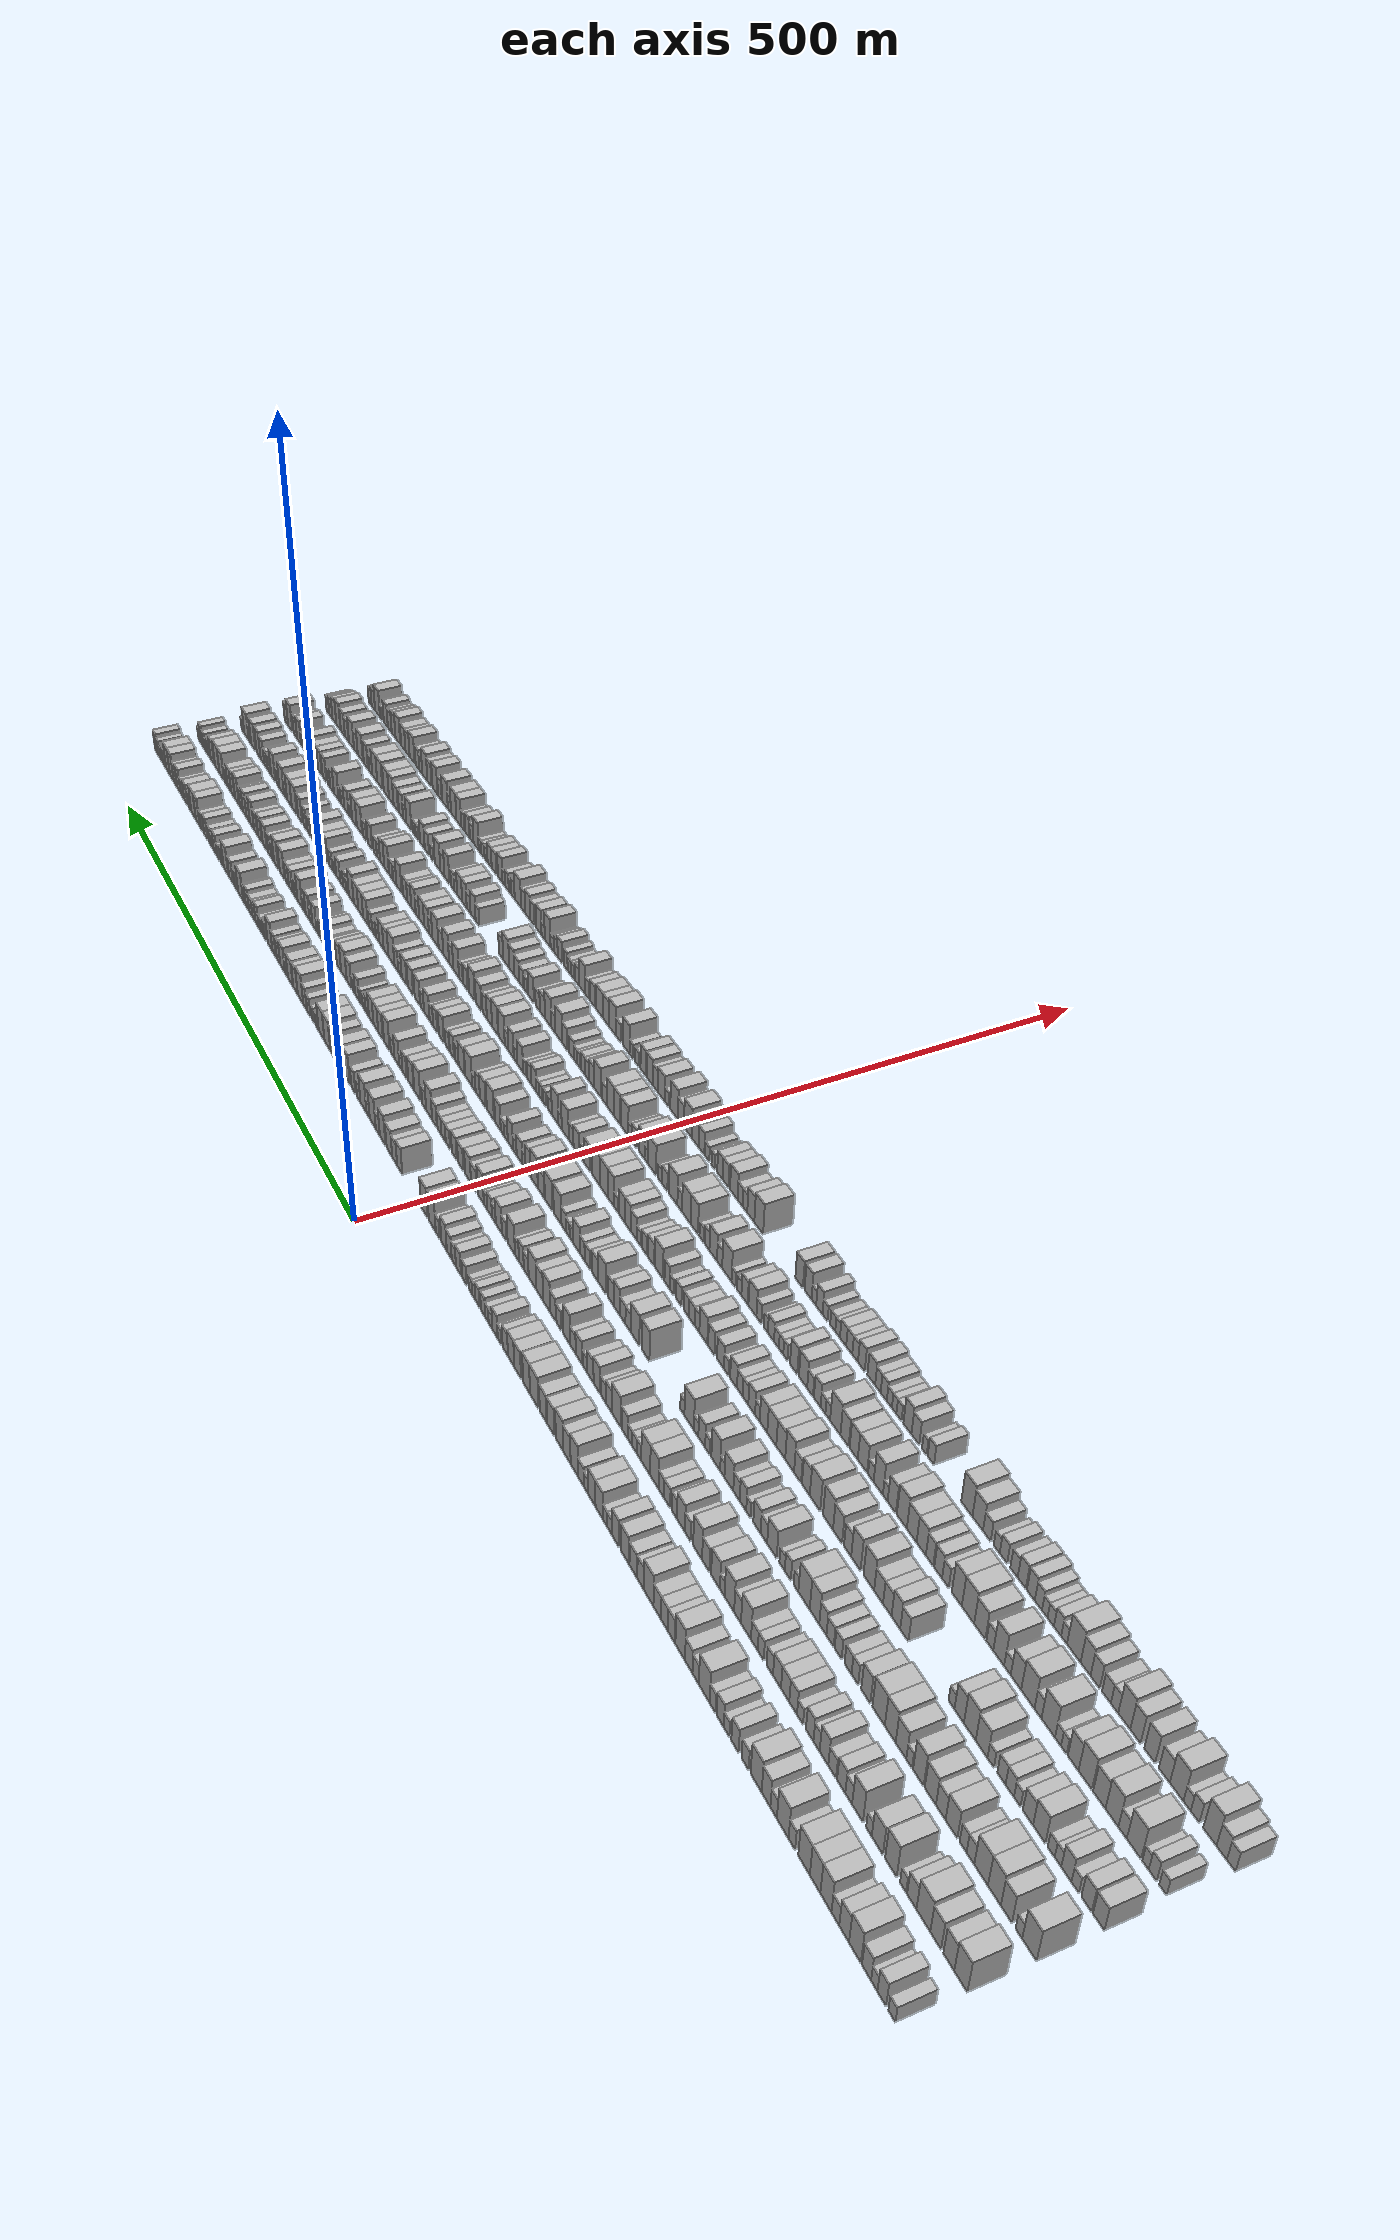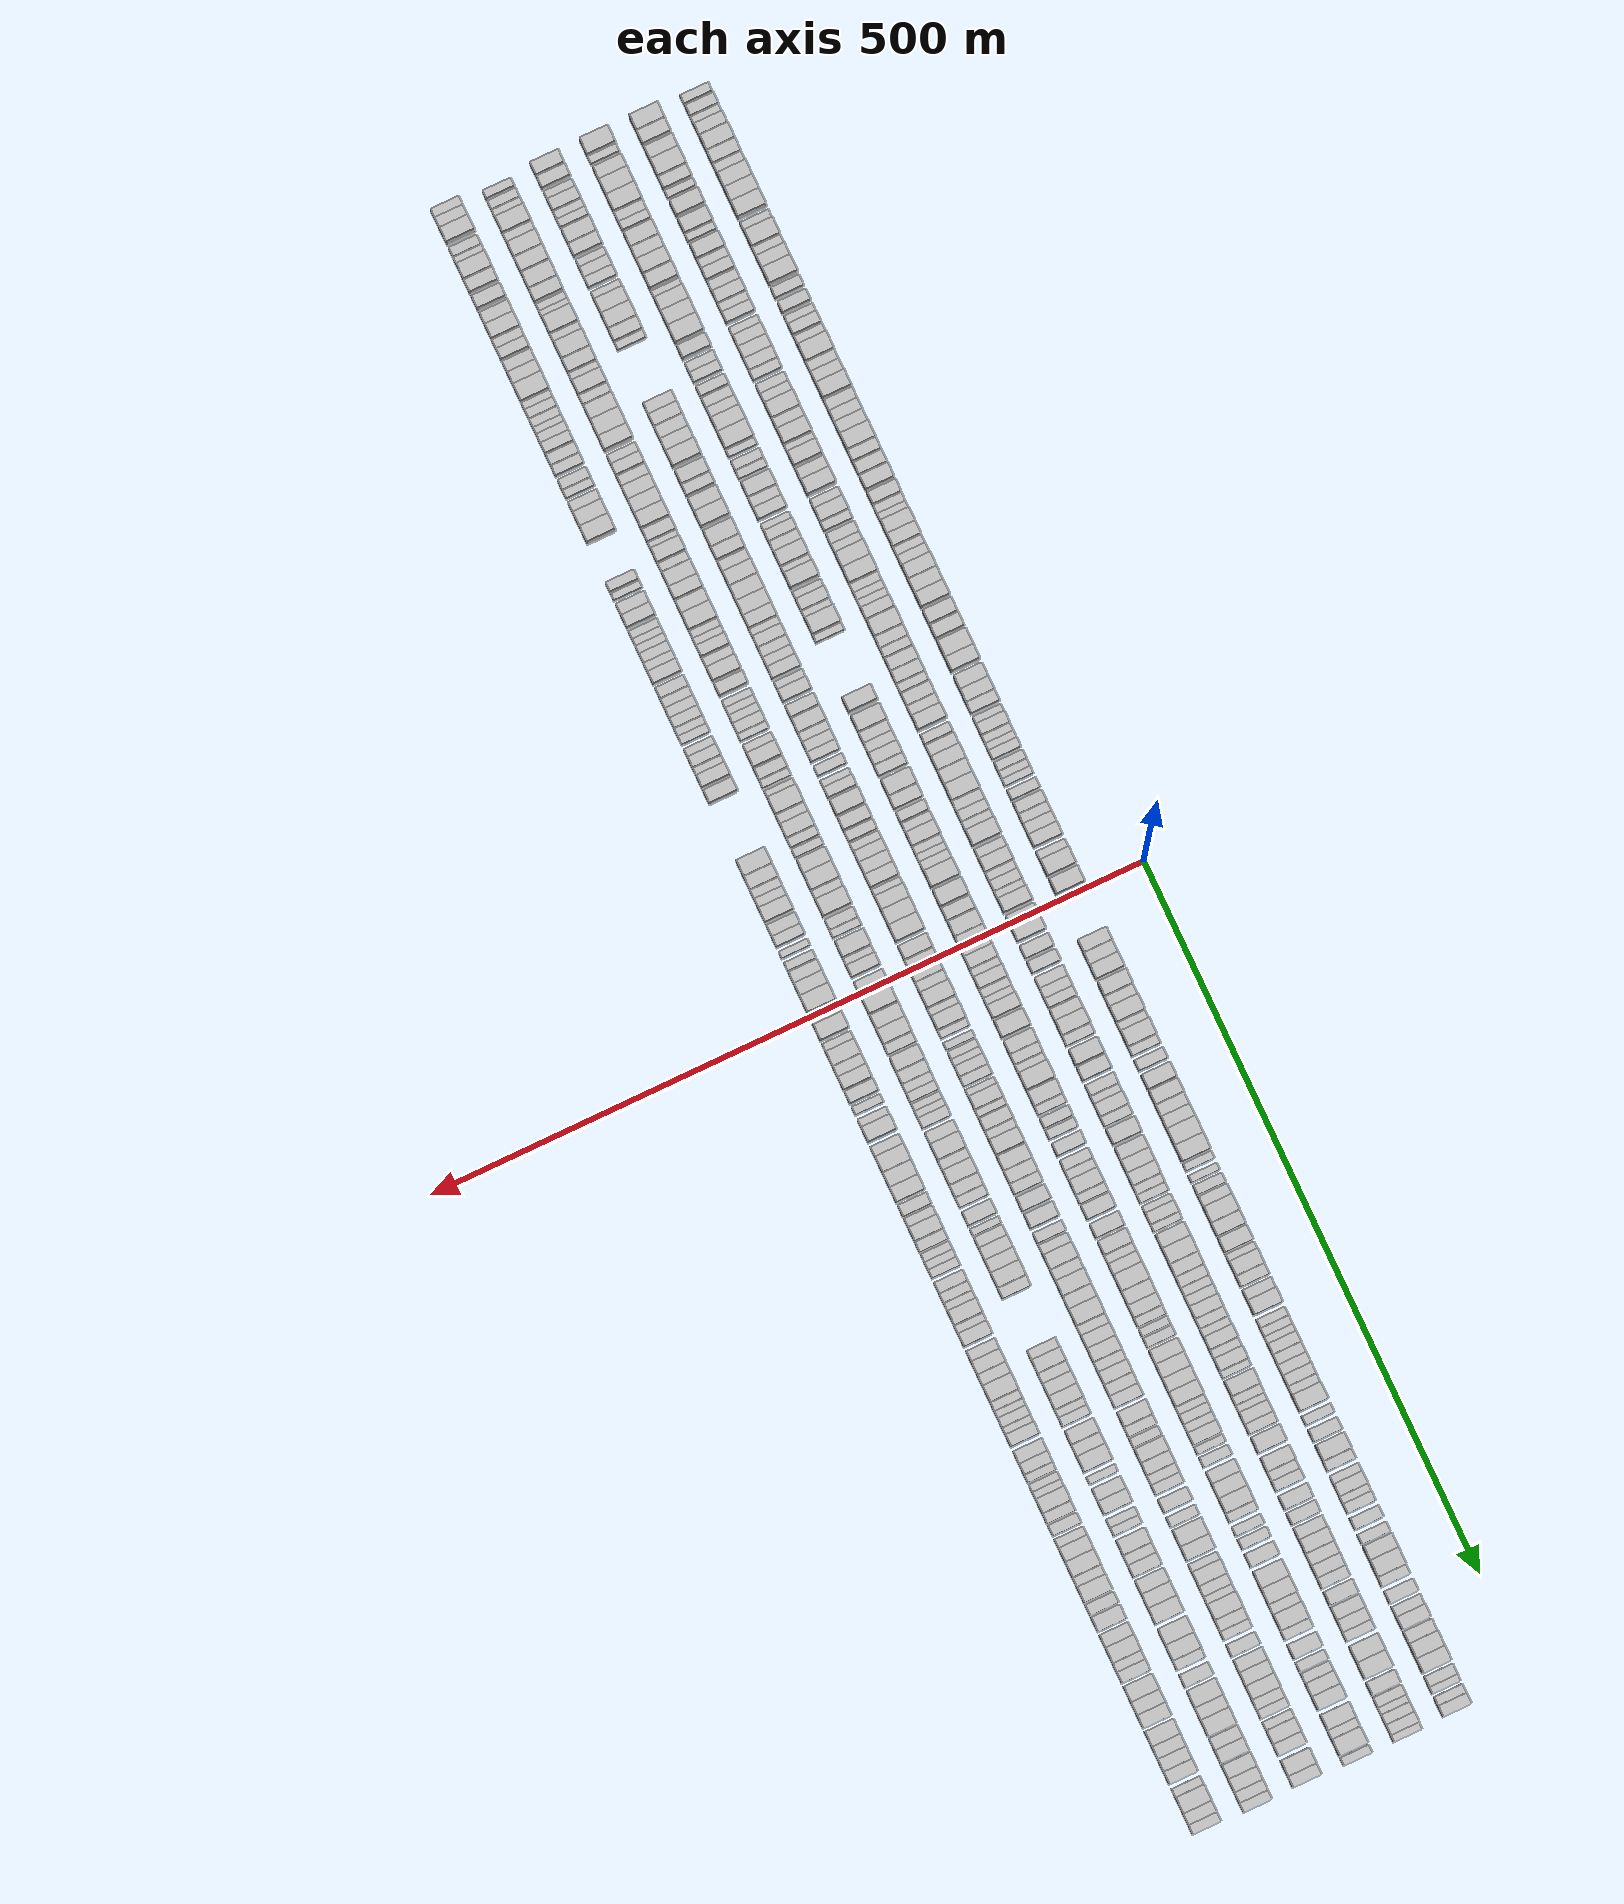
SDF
<sdf version="1.6">
 <world name="default">
  <scene>
   <sky><clouds><speed>12</speed></clouds></sky>
   <ambient>0.4 0.4 0.4 1</ambient>
   <background>0.7 0.7 0.7 1</background>
   <shadows>1</shadows>
  </scene>
  <gravity>0 0 -9.8066</gravity>
  <magnetic_field>6e-06 2.3e-05 -4.2e-05</magnetic_field>
  <physics default="0" name="default_physics" type="ode">
   <ode>
    <solver>
     <type>quick</type>
     <iters>10</iters>
     <sor>1.0</sor>
     <use_dynamic_moi_rescaling>0</use_dynamic_moi_rescaling>
    </solver>
    <constraints>
     <cfm>0</cfm>
     <erp>0.2</erp>
     <contact_max_correcting_vel>100</contact_max_correcting_vel>
     <contact_surface_layer>0.001</contact_surface_layer>
    </constraints>
   </ode>
   <max_step_size>0.004</max_step_size>
   <real_time_factor>1</real_time_factor>
   <real_time_update_rate>250</real_time_update_rate>
  </physics>
  <light name="sun" type="directional">
   <pose>0 0 10 0 0 0</pose>
   <diffuse>0.8 0.8 0.8 1</diffuse>
   <specular>0.2 0.2 0.2 1</specular>
   <attenuation>
    <range>1000</range>
    <constant>0.9</constant>
    <linear>0.01</linear>
    <quadratic>0.001</quadratic>
   </attenuation>
   <direction>-0.5 0.1 -0.9</direction>
  </light>
  <model name="building_1">
   <static>1</static>
   <pose>50.0000 -566.0021 0 0.000000 0.000000 0.000000</pose>
   <link name="link">
    <pose>0 0 6.00 0 0 0</pose>
    <collision name="collision"><geometry><box><size>20.0000 5.9958 12.0000</size></box></geometry></collision>
    <visual name="visual">
     <cast_shadows>0</cast_shadows>
     <geometry><box><size>20.0000 5.9958 12.0000</size></box></geometry>
     <material>
      <script>
       <uri>model://HANNAS_wall/materials/scripts</uri>
       <uri>model://HANNAS_wall/materials/textures</uri>
       <name>vrc/HANNAS_wall</name>
      </script>
     </material>
    </visual>
   </link>
  </model>
  <model name="building_2">
   <static>1</static>
   <pose>50.0000 -557.2755 0 0.000000 0.000000 0.000000</pose>
   <link name="link">
    <pose>0 0 9.00 0 0 0</pose>
    <collision name="collision"><geometry><box><size>20.0000 7.4574 18.0000</size></box></geometry></collision>
    <visual name="visual">
     <cast_shadows>0</cast_shadows>
     <geometry><box><size>20.0000 7.4574 18.0000</size></box></geometry>
     <material>
      <script>
       <uri>model://HANNAS_wall/materials/scripts</uri>
       <uri>model://HANNAS_wall/materials/textures</uri>
       <name>vrc/HANNAS_wall</name>
      </script>
     </material>
    </visual>
   </link>
  </model>
  <model name="building_3">
   <static>1</static>
   <pose>50.0000 -550.8041 0 0.000000 0.000000 0.000000</pose>
   <link name="link">
    <pose>0 0 6.00 0 0 0</pose>
    <collision name="collision"><geometry><box><size>20.0000 5.4854 12.0000</size></box></geometry></collision>
    <visual name="visual">
     <cast_shadows>0</cast_shadows>
     <geometry><box><size>20.0000 5.4854 12.0000</size></box></geometry>
     <material>
      <script>
       <uri>model://HANNAS_wall/materials/scripts</uri>
       <uri>model://HANNAS_wall/materials/textures</uri>
       <name>vrc/HANNAS_wall</name>
      </script>
     </material>
    </visual>
   </link>
  </model>
  <model name="building_4">
   <static>1</static>
   <pose>50.0000 -544.0784 0 0.000000 0.000000 0.000000</pose>
   <link name="link">
    <pose>0 0 9.00 0 0 0</pose>
    <collision name="collision"><geometry><box><size>20.0000 7.9661 18.0000</size></box></geometry></collision>
    <visual name="visual">
     <cast_shadows>0</cast_shadows>
     <geometry><box><size>20.0000 7.9661 18.0000</size></box></geometry>
     <material>
      <script>
       <uri>model://HANNAS_wall/materials/scripts</uri>
       <uri>model://HANNAS_wall/materials/textures</uri>
       <name>vrc/HANNAS_wall</name>
      </script>
     </material>
    </visual>
   </link>
  </model>
  <model name="building_5">
   <static>1</static>
   <pose>50.0000 -533.8237 0 0.000000 0.000000 0.000000</pose>
   <link name="link">
    <pose>0 0 12.00 0 0 0</pose>
    <collision name="collision"><geometry><box><size>20.0000 10.5432 24.0000</size></box></geometry></collision>
    <visual name="visual">
     <cast_shadows>0</cast_shadows>
     <geometry><box><size>20.0000 10.5432 24.0000</size></box></geometry>
     <material>
      <script>
       <uri>model://HANNAS_wall/materials/scripts</uri>
       <uri>model://HANNAS_wall/materials/textures</uri>
       <name>vrc/HANNAS_wall</name>
      </script>
     </material>
    </visual>
   </link>
  </model>
  <model name="building_6">
   <static>1</static>
   <pose>50.0000 -524.1240 0 0.000000 0.000000 0.000000</pose>
   <link name="link">
    <pose>0 0 10.50 0 0 0</pose>
    <collision name="collision"><geometry><box><size>20.0000 8.8564 21.0000</size></box></geometry></collision>
    <visual name="visual">
     <cast_shadows>0</cast_shadows>
     <geometry><box><size>20.0000 8.8564 21.0000</size></box></geometry>
     <material>
      <script>
       <uri>model://HANNAS_wall/materials/scripts</uri>
       <uri>model://HANNAS_wall/materials/textures</uri>
       <name>vrc/HANNAS_wall</name>
      </script>
     </material>
    </visual>
   </link>
  </model>
  <model name="building_7">
   <static>1</static>
   <pose>50.0000 -516.1544 0 0.000000 0.000000 0.000000</pose>
   <link name="link">
    <pose>0 0 7.50 0 0 0</pose>
    <collision name="collision"><geometry><box><size>20.0000 7.0828 15.0000</size></box></geometry></collision>
    <visual name="visual">
     <cast_shadows>0</cast_shadows>
     <geometry><box><size>20.0000 7.0828 15.0000</size></box></geometry>
     <material>
      <script>
       <uri>model://HANNAS_wall/materials/scripts</uri>
       <uri>model://HANNAS_wall/materials/textures</uri>
       <name>vrc/HANNAS_wall</name>
      </script>
     </material>
    </visual>
   </link>
  </model>
  <model name="building_8">
   <static>1</static>
   <pose>50.0000 -507.4797 0 0.000000 0.000000 0.000000</pose>
   <link name="link">
    <pose>0 0 12.00 0 0 0</pose>
    <collision name="collision"><geometry><box><size>20.0000 10.2665 24.0000</size></box></geometry></collision>
    <visual name="visual">
     <cast_shadows>0</cast_shadows>
     <geometry><box><size>20.0000 10.2665 24.0000</size></box></geometry>
     <material>
      <script>
       <uri>model://HANNAS_wall/materials/scripts</uri>
       <uri>model://HANNAS_wall/materials/textures</uri>
       <name>vrc/HANNAS_wall</name>
      </script>
     </material>
    </visual>
   </link>
  </model>
  <model name="building_9">
   <static>1</static>
   <pose>50.0000 -497.3951 0 0.000000 0.000000 0.000000</pose>
   <link name="link">
    <pose>0 0 12.00 0 0 0</pose>
    <collision name="collision"><geometry><box><size>20.0000 9.9028 24.0000</size></box></geometry></collision>
    <visual name="visual">
     <cast_shadows>0</cast_shadows>
     <geometry><box><size>20.0000 9.9028 24.0000</size></box></geometry>
     <material>
      <script>
       <uri>model://HANNAS_wall/materials/scripts</uri>
       <uri>model://HANNAS_wall/materials/textures</uri>
       <name>vrc/HANNAS_wall</name>
      </script>
     </material>
    </visual>
   </link>
  </model>
  <model name="building_10">
   <static>1</static>
   <pose>50.0000 -486.9409 0 0.000000 0.000000 0.000000</pose>
   <link name="link">
    <pose>0 0 12.00 0 0 0</pose>
    <collision name="collision"><geometry><box><size>20.0000 11.0058 24.0000</size></box></geometry></collision>
    <visual name="visual">
     <cast_shadows>0</cast_shadows>
     <geometry><box><size>20.0000 11.0058 24.0000</size></box></geometry>
     <material>
      <script>
       <uri>model://HANNAS_wall/materials/scripts</uri>
       <uri>model://HANNAS_wall/materials/textures</uri>
       <name>vrc/HANNAS_wall</name>
      </script>
     </material>
    </visual>
   </link>
  </model>
  <model name="building_11">
   <static>1</static>
   <pose>50.0000 -475.2833 0 0.000000 0.000000 0.000000</pose>
   <link name="link">
    <pose>0 0 7.50 0 0 0</pose>
    <collision name="collision"><geometry><box><size>20.0000 6.3094 15.0000</size></box></geometry></collision>
    <visual name="visual">
     <cast_shadows>0</cast_shadows>
     <geometry><box><size>20.0000 6.3094 15.0000</size></box></geometry>
     <material>
      <script>
       <uri>model://HANNAS_wall/materials/scripts</uri>
       <uri>model://HANNAS_wall/materials/textures</uri>
       <name>vrc/HANNAS_wall</name>
      </script>
     </material>
    </visual>
   </link>
  </model>
  <model name="building_12">
   <static>1</static>
   <pose>50.0000 -466.4035 0 0.000000 0.000000 0.000000</pose>
   <link name="link">
    <pose>0 0 12.00 0 0 0</pose>
    <collision name="collision"><geometry><box><size>20.0000 11.4501 24.0000</size></box></geometry></collision>
    <visual name="visual">
     <cast_shadows>0</cast_shadows>
     <geometry><box><size>20.0000 11.4501 24.0000</size></box></geometry>
     <material>
      <script>
       <uri>model://HANNAS_wall/materials/scripts</uri>
       <uri>model://HANNAS_wall/materials/textures</uri>
       <name>vrc/HANNAS_wall</name>
      </script>
     </material>
    </visual>
   </link>
  </model>
  <model name="building_13">
   <static>1</static>
   <pose>50.0000 -457.4832 0 0.000000 0.000000 0.000000</pose>
   <link name="link">
    <pose>0 0 7.50 0 0 0</pose>
    <collision name="collision"><geometry><box><size>20.0000 6.3907 15.0000</size></box></geometry></collision>
    <visual name="visual">
     <cast_shadows>0</cast_shadows>
     <geometry><box><size>20.0000 6.3907 15.0000</size></box></geometry>
     <material>
      <script>
       <uri>model://HANNAS_wall/materials/scripts</uri>
       <uri>model://HANNAS_wall/materials/textures</uri>
       <name>vrc/HANNAS_wall</name>
      </script>
     </material>
    </visual>
   </link>
  </model>
  <model name="building_14">
   <static>1</static>
   <pose>50.0000 -449.9137 0 0.000000 0.000000 0.000000</pose>
   <link name="link">
    <pose>0 0 10.50 0 0 0</pose>
    <collision name="collision"><geometry><box><size>20.0000 8.7481 21.0000</size></box></geometry></collision>
    <visual name="visual">
     <cast_shadows>0</cast_shadows>
     <geometry><box><size>20.0000 8.7481 21.0000</size></box></geometry>
     <material>
      <script>
       <uri>model://HANNAS_wall/materials/scripts</uri>
       <uri>model://HANNAS_wall/materials/textures</uri>
       <name>vrc/HANNAS_wall</name>
      </script>
     </material>
    </visual>
   </link>
  </model>
  <model name="building_15">
   <static>1</static>
   <pose>50.0000 -439.9456 0 0.000000 0.000000 0.000000</pose>
   <link name="link">
    <pose>0 0 12.00 0 0 0</pose>
    <collision name="collision"><geometry><box><size>20.0000 11.1882 24.0000</size></box></geometry></collision>
    <visual name="visual">
     <cast_shadows>0</cast_shadows>
     <geometry><box><size>20.0000 11.1882 24.0000</size></box></geometry>
     <material>
      <script>
       <uri>model://HANNAS_wall/materials/scripts</uri>
       <uri>model://HANNAS_wall/materials/textures</uri>
       <name>vrc/HANNAS_wall</name>
      </script>
     </material>
    </visual>
   </link>
  </model>
  <model name="building_16">
   <static>1</static>
   <pose>50.0000 -428.6951 0 0.000000 0.000000 0.000000</pose>
   <link name="link">
    <pose>0 0 7.50 0 0 0</pose>
    <collision name="collision"><geometry><box><size>20.0000 7.3129 15.0000</size></box></geometry></collision>
    <visual name="visual">
     <cast_shadows>0</cast_shadows>
     <geometry><box><size>20.0000 7.3129 15.0000</size></box></geometry>
     <material>
      <script>
       <uri>model://HANNAS_wall/materials/scripts</uri>
       <uri>model://HANNAS_wall/materials/textures</uri>
       <name>vrc/HANNAS_wall</name>
      </script>
     </material>
    </visual>
   </link>
  </model>
  <model name="building_17">
   <static>1</static>
   <pose>50.0000 -418.2388 0 0.000000 0.000000 0.000000</pose>
   <link name="link">
    <pose>0 0 9.00 0 0 0</pose>
    <collision name="collision"><geometry><box><size>20.0000 7.5996 18.0000</size></box></geometry></collision>
    <visual name="visual">
     <cast_shadows>0</cast_shadows>
     <geometry><box><size>20.0000 7.5996 18.0000</size></box></geometry>
     <material>
      <script>
       <uri>model://HANNAS_wall/materials/scripts</uri>
       <uri>model://HANNAS_wall/materials/textures</uri>
       <name>vrc/HANNAS_wall</name>
      </script>
     </material>
    </visual>
   </link>
  </model>
  <model name="building_18">
   <static>1</static>
   <pose>50.0000 -409.4825 0 0.000000 0.000000 0.000000</pose>
   <link name="link">
    <pose>0 0 6.00 0 0 0</pose>
    <collision name="collision"><geometry><box><size>20.0000 5.9131 12.0000</size></box></geometry></collision>
    <visual name="visual">
     <cast_shadows>0</cast_shadows>
     <geometry><box><size>20.0000 5.9131 12.0000</size></box></geometry>
     <material>
      <script>
       <uri>model://HANNAS_wall/materials/scripts</uri>
       <uri>model://HANNAS_wall/materials/textures</uri>
       <name>vrc/HANNAS_wall</name>
      </script>
     </material>
    </visual>
   </link>
  </model>
  <model name="building_19">
   <static>1</static>
   <pose>50.0000 -402.7227 0 0.000000 0.000000 0.000000</pose>
   <link name="link">
    <pose>0 0 9.00 0 0 0</pose>
    <collision name="collision"><geometry><box><size>20.0000 7.6064 18.0000</size></box></geometry></collision>
    <visual name="visual">
     <cast_shadows>0</cast_shadows>
     <geometry><box><size>20.0000 7.6064 18.0000</size></box></geometry>
     <material>
      <script>
       <uri>model://HANNAS_wall/materials/scripts</uri>
       <uri>model://HANNAS_wall/materials/textures</uri>
       <name>vrc/HANNAS_wall</name>
      </script>
     </material>
    </visual>
   </link>
  </model>
  <model name="building_20">
   <static>1</static>
   <pose>50.0000 -394.7155 0 0.000000 0.000000 0.000000</pose>
   <link name="link">
    <pose>0 0 7.50 0 0 0</pose>
    <collision name="collision"><geometry><box><size>20.0000 6.4081 15.0000</size></box></geometry></collision>
    <visual name="visual">
     <cast_shadows>0</cast_shadows>
     <geometry><box><size>20.0000 6.4081 15.0000</size></box></geometry>
     <material>
      <script>
       <uri>model://HANNAS_wall/materials/scripts</uri>
       <uri>model://HANNAS_wall/materials/textures</uri>
       <name>vrc/HANNAS_wall</name>
      </script>
     </material>
    </visual>
   </link>
  </model>
  <model name="building_21">
   <static>1</static>
   <pose>50.0000 -385.5684 0 0.000000 0.000000 0.000000</pose>
   <link name="link">
    <pose>0 0 12.00 0 0 0</pose>
    <collision name="collision"><geometry><box><size>20.0000 11.8859 24.0000</size></box></geometry></collision>
    <visual name="visual">
     <cast_shadows>0</cast_shadows>
     <geometry><box><size>20.0000 11.8859 24.0000</size></box></geometry>
     <material>
      <script>
       <uri>model://HANNAS_wall/materials/scripts</uri>
       <uri>model://HANNAS_wall/materials/textures</uri>
       <name>vrc/HANNAS_wall</name>
      </script>
     </material>
    </visual>
   </link>
  </model>
  <model name="building_22">
   <static>1</static>
   <pose>50.0000 -376.1716 0 0.000000 0.000000 0.000000</pose>
   <link name="link">
    <pose>0 0 7.50 0 0 0</pose>
    <collision name="collision"><geometry><box><size>20.0000 6.9078 15.0000</size></box></geometry></collision>
    <visual name="visual">
     <cast_shadows>0</cast_shadows>
     <geometry><box><size>20.0000 6.9078 15.0000</size></box></geometry>
     <material>
      <script>
       <uri>model://HANNAS_wall/materials/scripts</uri>
       <uri>model://HANNAS_wall/materials/textures</uri>
       <name>vrc/HANNAS_wall</name>
      </script>
     </material>
    </visual>
   </link>
  </model>
  <model name="building_23">
   <static>1</static>
   <pose>50.0000 -368.5605 0 0.000000 0.000000 0.000000</pose>
   <link name="link">
    <pose>0 0 9.00 0 0 0</pose>
    <collision name="collision"><geometry><box><size>20.0000 8.3145 18.0000</size></box></geometry></collision>
    <visual name="visual">
     <cast_shadows>0</cast_shadows>
     <geometry><box><size>20.0000 8.3145 18.0000</size></box></geometry>
     <material>
      <script>
       <uri>model://HANNAS_wall/materials/scripts</uri>
       <uri>model://HANNAS_wall/materials/textures</uri>
       <name>vrc/HANNAS_wall</name>
      </script>
     </material>
    </visual>
   </link>
  </model>
  <model name="building_24">
   <static>1</static>
   <pose>50.0000 -359.0265 0 0.000000 0.000000 0.000000</pose>
   <link name="link">
    <pose>0 0 12.00 0 0 0</pose>
    <collision name="collision"><geometry><box><size>20.0000 10.7535 24.0000</size></box></geometry></collision>
    <visual name="visual">
     <cast_shadows>0</cast_shadows>
     <geometry><box><size>20.0000 10.7535 24.0000</size></box></geometry>
     <material>
      <script>
       <uri>model://HANNAS_wall/materials/scripts</uri>
       <uri>model://HANNAS_wall/materials/textures</uri>
       <name>vrc/HANNAS_wall</name>
      </script>
     </material>
    </visual>
   </link>
  </model>
  <model name="building_25">
   <static>1</static>
   <pose>50.0000 -348.8388 0 0.000000 0.000000 0.000000</pose>
   <link name="link">
    <pose>0 0 9.00 0 0 0</pose>
    <collision name="collision"><geometry><box><size>20.0000 7.6219 18.0000</size></box></geometry></collision>
    <visual name="visual">
     <cast_shadows>0</cast_shadows>
     <geometry><box><size>20.0000 7.6219 18.0000</size></box></geometry>
     <material>
      <script>
       <uri>model://HANNAS_wall/materials/scripts</uri>
       <uri>model://HANNAS_wall/materials/textures</uri>
       <name>vrc/HANNAS_wall</name>
      </script>
     </material>
    </visual>
   </link>
  </model>
  <model name="building_26">
   <static>1</static>
   <pose>50.0000 -341.1490 0 0.000000 0.000000 0.000000</pose>
   <link name="link">
    <pose>0 0 9.00 0 0 0</pose>
    <collision name="collision"><geometry><box><size>20.0000 7.7577 18.0000</size></box></geometry></collision>
    <visual name="visual">
     <cast_shadows>0</cast_shadows>
     <geometry><box><size>20.0000 7.7577 18.0000</size></box></geometry>
     <material>
      <script>
       <uri>model://HANNAS_wall/materials/scripts</uri>
       <uri>model://HANNAS_wall/materials/textures</uri>
       <name>vrc/HANNAS_wall</name>
      </script>
     </material>
    </visual>
   </link>
  </model>
  <model name="building_27">
   <static>1</static>
   <pose>50.0000 -332.8798 0 0.000000 0.000000 0.000000</pose>
   <link name="link">
    <pose>0 0 9.00 0 0 0</pose>
    <collision name="collision"><geometry><box><size>20.0000 8.7808 18.0000</size></box></geometry></collision>
    <visual name="visual">
     <cast_shadows>0</cast_shadows>
     <geometry><box><size>20.0000 8.7808 18.0000</size></box></geometry>
     <material>
      <script>
       <uri>model://HANNAS_wall/materials/scripts</uri>
       <uri>model://HANNAS_wall/materials/textures</uri>
       <name>vrc/HANNAS_wall</name>
      </script>
     </material>
    </visual>
   </link>
  </model>
  <model name="building_28">
   <static>1</static>
   <pose>50.0000 -322.8463 0 0.000000 0.000000 0.000000</pose>
   <link name="link">
    <pose>0 0 12.00 0 0 0</pose>
    <collision name="collision"><geometry><box><size>20.0000 11.2861 24.0000</size></box></geometry></collision>
    <visual name="visual">
     <cast_shadows>0</cast_shadows>
     <geometry><box><size>20.0000 11.2861 24.0000</size></box></geometry>
     <material>
      <script>
       <uri>model://HANNAS_wall/materials/scripts</uri>
       <uri>model://HANNAS_wall/materials/textures</uri>
       <name>vrc/HANNAS_wall</name>
      </script>
     </material>
    </visual>
   </link>
  </model>
  <model name="building_29">
   <static>1</static>
   <pose>50.0000 -313.3382 0 0.000000 0.000000 0.000000</pose>
   <link name="link">
    <pose>0 0 9.00 0 0 0</pose>
    <collision name="collision"><geometry><box><size>20.0000 7.7301 18.0000</size></box></geometry></collision>
    <visual name="visual">
     <cast_shadows>0</cast_shadows>
     <geometry><box><size>20.0000 7.7301 18.0000</size></box></geometry>
     <material>
      <script>
       <uri>model://HANNAS_wall/materials/scripts</uri>
       <uri>model://HANNAS_wall/materials/textures</uri>
       <name>vrc/HANNAS_wall</name>
      </script>
     </material>
    </visual>
   </link>
  </model>
  <model name="building_30">
   <static>1</static>
   <pose>50.0000 -304.2649 0 0.000000 0.000000 0.000000</pose>
   <link name="link">
    <pose>0 0 9.00 0 0 0</pose>
    <collision name="collision"><geometry><box><size>20.0000 8.4165 18.0000</size></box></geometry></collision>
    <visual name="visual">
     <cast_shadows>0</cast_shadows>
     <geometry><box><size>20.0000 8.4165 18.0000</size></box></geometry>
     <material>
      <script>
       <uri>model://HANNAS_wall/materials/scripts</uri>
       <uri>model://HANNAS_wall/materials/textures</uri>
       <name>vrc/HANNAS_wall</name>
      </script>
     </material>
    </visual>
   </link>
  </model>
  <model name="building_31">
   <static>1</static>
   <pose>50.0000 -294.2038 0 0.000000 0.000000 0.000000</pose>
   <link name="link">
    <pose>0 0 10.50 0 0 0</pose>
    <collision name="collision"><geometry><box><size>20.0000 9.7058 21.0000</size></box></geometry></collision>
    <visual name="visual">
     <cast_shadows>0</cast_shadows>
     <geometry><box><size>20.0000 9.7058 21.0000</size></box></geometry>
     <material>
      <script>
       <uri>model://HANNAS_wall/materials/scripts</uri>
       <uri>model://HANNAS_wall/materials/textures</uri>
       <name>vrc/HANNAS_wall</name>
      </script>
     </material>
    </visual>
   </link>
  </model>
  <model name="building_32">
   <static>1</static>
   <pose>50.0000 -283.0797 0 0.000000 0.000000 0.000000</pose>
   <link name="link">
    <pose>0 0 10.50 0 0 0</pose>
    <collision name="collision"><geometry><box><size>20.0000 8.5424 21.0000</size></box></geometry></collision>
    <visual name="visual">
     <cast_shadows>0</cast_shadows>
     <geometry><box><size>20.0000 8.5424 21.0000</size></box></geometry>
     <material>
      <script>
       <uri>model://HANNAS_wall/materials/scripts</uri>
       <uri>model://HANNAS_wall/materials/textures</uri>
       <name>vrc/HANNAS_wall</name>
      </script>
     </material>
    </visual>
   </link>
  </model>
  <model name="building_33">
   <static>1</static>
   <pose>50.0000 -275.8419 0 0.000000 0.000000 0.000000</pose>
   <link name="link">
    <pose>0 0 6.00 0 0 0</pose>
    <collision name="collision"><geometry><box><size>20.0000 5.9331 12.0000</size></box></geometry></collision>
    <visual name="visual">
     <cast_shadows>0</cast_shadows>
     <geometry><box><size>20.0000 5.9331 12.0000</size></box></geometry>
     <material>
      <script>
       <uri>model://HANNAS_wall/materials/scripts</uri>
       <uri>model://HANNAS_wall/materials/textures</uri>
       <name>vrc/HANNAS_wall</name>
      </script>
     </material>
    </visual>
   </link>
  </model>
  <model name="building_34">
   <static>1</static>
   <pose>50.0000 -270.1936 0 0.000000 0.000000 0.000000</pose>
   <link name="link">
    <pose>0 0 6.00 0 0 0</pose>
    <collision name="collision"><geometry><box><size>20.0000 5.3635 12.0000</size></box></geometry></collision>
    <visual name="visual">
     <cast_shadows>0</cast_shadows>
     <geometry><box><size>20.0000 5.3635 12.0000</size></box></geometry>
     <material>
      <script>
       <uri>model://HANNAS_wall/materials/scripts</uri>
       <uri>model://HANNAS_wall/materials/textures</uri>
       <name>vrc/HANNAS_wall</name>
      </script>
     </material>
    </visual>
   </link>
  </model>
  <model name="building_35">
   <static>1</static>
   <pose>50.0000 -262.7760 0 0.000000 0.000000 0.000000</pose>
   <link name="link">
    <pose>0 0 10.50 0 0 0</pose>
    <collision name="collision"><geometry><box><size>20.0000 9.4717 21.0000</size></box></geometry></collision>
    <visual name="visual">
     <cast_shadows>0</cast_shadows>
     <geometry><box><size>20.0000 9.4717 21.0000</size></box></geometry>
     <material>
      <script>
       <uri>model://HANNAS_wall/materials/scripts</uri>
       <uri>model://HANNAS_wall/materials/textures</uri>
       <name>vrc/HANNAS_wall</name>
      </script>
     </material>
    </visual>
   </link>
  </model>
  <model name="building_36">
   <static>1</static>
   <pose>50.0000 -253.5233 0 0.000000 0.000000 0.000000</pose>
   <link name="link">
    <pose>0 0 10.50 0 0 0</pose>
    <collision name="collision"><geometry><box><size>20.0000 9.0336 21.0000</size></box></geometry></collision>
    <visual name="visual">
     <cast_shadows>0</cast_shadows>
     <geometry><box><size>20.0000 9.0336 21.0000</size></box></geometry>
     <material>
      <script>
       <uri>model://HANNAS_wall/materials/scripts</uri>
       <uri>model://HANNAS_wall/materials/textures</uri>
       <name>vrc/HANNAS_wall</name>
      </script>
     </material>
    </visual>
   </link>
  </model>
  <model name="building_37">
   <static>1</static>
   <pose>50.0000 -246.0254 0 0.000000 0.000000 0.000000</pose>
   <link name="link">
    <pose>0 0 6.00 0 0 0</pose>
    <collision name="collision"><geometry><box><size>20.0000 5.9621 12.0000</size></box></geometry></collision>
    <visual name="visual">
     <cast_shadows>0</cast_shadows>
     <geometry><box><size>20.0000 5.9621 12.0000</size></box></geometry>
     <material>
      <script>
       <uri>model://HANNAS_wall/materials/scripts</uri>
       <uri>model://HANNAS_wall/materials/textures</uri>
       <name>vrc/HANNAS_wall</name>
      </script>
     </material>
    </visual>
   </link>
  </model>
  <model name="building_38">
   <static>1</static>
   <pose>50.0000 -239.3330 0 0.000000 0.000000 0.000000</pose>
   <link name="link">
    <pose>0 0 7.50 0 0 0</pose>
    <collision name="collision"><geometry><box><size>20.0000 7.4227 15.0000</size></box></geometry></collision>
    <visual name="visual">
     <cast_shadows>0</cast_shadows>
     <geometry><box><size>20.0000 7.4227 15.0000</size></box></geometry>
     <material>
      <script>
       <uri>model://HANNAS_wall/materials/scripts</uri>
       <uri>model://HANNAS_wall/materials/textures</uri>
       <name>vrc/HANNAS_wall</name>
      </script>
     </material>
    </visual>
   </link>
  </model>
  <model name="building_39">
   <static>1</static>
   <pose>50.0000 -230.7598 0 0.000000 0.000000 0.000000</pose>
   <link name="link">
    <pose>0 0 12.00 0 0 0</pose>
    <collision name="collision"><geometry><box><size>20.0000 9.7237 24.0000</size></box></geometry></collision>
    <visual name="visual">
     <cast_shadows>0</cast_shadows>
     <geometry><box><size>20.0000 9.7237 24.0000</size></box></geometry>
     <material>
      <script>
       <uri>model://HANNAS_wall/materials/scripts</uri>
       <uri>model://HANNAS_wall/materials/textures</uri>
       <name>vrc/HANNAS_wall</name>
      </script>
     </material>
    </visual>
   </link>
  </model>
  <model name="building_40">
   <static>1</static>
   <pose>50.0000 -221.0899 0 0.000000 0.000000 0.000000</pose>
   <link name="link">
    <pose>0 0 10.50 0 0 0</pose>
    <collision name="collision"><geometry><box><size>20.0000 9.6162 21.0000</size></box></geometry></collision>
    <visual name="visual">
     <cast_shadows>0</cast_shadows>
     <geometry><box><size>20.0000 9.6162 21.0000</size></box></geometry>
     <material>
      <script>
       <uri>model://HANNAS_wall/materials/scripts</uri>
       <uri>model://HANNAS_wall/materials/textures</uri>
       <name>vrc/HANNAS_wall</name>
      </script>
     </material>
    </visual>
   </link>
  </model>
  <model name="building_41">
   <static>1</static>
   <pose>50.0000 -211.2209 0 0.000000 0.000000 0.000000</pose>
   <link name="link">
    <pose>0 0 12.00 0 0 0</pose>
    <collision name="collision"><geometry><box><size>20.0000 10.1218 24.0000</size></box></geometry></collision>
    <visual name="visual">
     <cast_shadows>0</cast_shadows>
     <geometry><box><size>20.0000 10.1218 24.0000</size></box></geometry>
     <material>
      <script>
       <uri>model://HANNAS_wall/materials/scripts</uri>
       <uri>model://HANNAS_wall/materials/textures</uri>
       <name>vrc/HANNAS_wall</name>
      </script>
     </material>
    </visual>
   </link>
  </model>
  <model name="building_42">
   <static>1</static>
   <pose>50.0000 -199.3403 0 0.000000 0.000000 0.000000</pose>
   <link name="link">
    <pose>0 0 10.50 0 0 0</pose>
    <collision name="collision"><geometry><box><size>20.0000 9.6392 21.0000</size></box></geometry></collision>
    <visual name="visual">
     <cast_shadows>0</cast_shadows>
     <geometry><box><size>20.0000 9.6392 21.0000</size></box></geometry>
     <material>
      <script>
       <uri>model://HANNAS_wall/materials/scripts</uri>
       <uri>model://HANNAS_wall/materials/textures</uri>
       <name>vrc/HANNAS_wall</name>
      </script>
     </material>
    </visual>
   </link>
  </model>
  <model name="building_43">
   <static>1</static>
   <pose>50.0000 -188.9205 0 0.000000 0.000000 0.000000</pose>
   <link name="link">
    <pose>0 0 10.50 0 0 0</pose>
    <collision name="collision"><geometry><box><size>20.0000 9.2004 21.0000</size></box></geometry></collision>
    <visual name="visual">
     <cast_shadows>0</cast_shadows>
     <geometry><box><size>20.0000 9.2004 21.0000</size></box></geometry>
     <material>
      <script>
       <uri>model://HANNAS_wall/materials/scripts</uri>
       <uri>model://HANNAS_wall/materials/textures</uri>
       <name>vrc/HANNAS_wall</name>
      </script>
     </material>
    </visual>
   </link>
  </model>
  <model name="building_44">
   <static>1</static>
   <pose>50.0000 -176.5398 0 0.000000 0.000000 0.000000</pose>
   <link name="link">
    <pose>0 0 12.00 0 0 0</pose>
    <collision name="collision"><geometry><box><size>20.0000 11.5611 24.0000</size></box></geometry></collision>
    <visual name="visual">
     <cast_shadows>0</cast_shadows>
     <geometry><box><size>20.0000 11.5611 24.0000</size></box></geometry>
     <material>
      <script>
       <uri>model://HANNAS_wall/materials/scripts</uri>
       <uri>model://HANNAS_wall/materials/textures</uri>
       <name>vrc/HANNAS_wall</name>
      </script>
     </material>
    </visual>
   </link>
  </model>
  <model name="building_45">
   <static>1</static>
   <pose>50.0000 -165.8892 0 0.000000 0.000000 0.000000</pose>
   <link name="link">
    <pose>0 0 12.00 0 0 0</pose>
    <collision name="collision"><geometry><box><size>20.0000 9.7400 24.0000</size></box></geometry></collision>
    <visual name="visual">
     <cast_shadows>0</cast_shadows>
     <geometry><box><size>20.0000 9.7400 24.0000</size></box></geometry>
     <material>
      <script>
       <uri>model://HANNAS_wall/materials/scripts</uri>
       <uri>model://HANNAS_wall/materials/textures</uri>
       <name>vrc/HANNAS_wall</name>
      </script>
     </material>
    </visual>
   </link>
  </model>
  <model name="building_46">
   <static>1</static>
   <pose>50.0000 -153.2231 0 0.000000 0.000000 0.000000</pose>
   <link name="link">
    <pose>0 0 10.50 0 0 0</pose>
    <collision name="collision"><geometry><box><size>20.0000 9.5921 21.0000</size></box></geometry></collision>
    <visual name="visual">
     <cast_shadows>0</cast_shadows>
     <geometry><box><size>20.0000 9.5921 21.0000</size></box></geometry>
     <material>
      <script>
       <uri>model://HANNAS_wall/materials/scripts</uri>
       <uri>model://HANNAS_wall/materials/textures</uri>
       <name>vrc/HANNAS_wall</name>
      </script>
     </material>
    </visual>
   </link>
  </model>
  <model name="building_47">
   <static>1</static>
   <pose>50.0000 -143.8796 0 0.000000 0.000000 0.000000</pose>
   <link name="link">
    <pose>0 0 10.50 0 0 0</pose>
    <collision name="collision"><geometry><box><size>20.0000 9.0949 21.0000</size></box></geometry></collision>
    <visual name="visual">
     <cast_shadows>0</cast_shadows>
     <geometry><box><size>20.0000 9.0949 21.0000</size></box></geometry>
     <material>
      <script>
       <uri>model://HANNAS_wall/materials/scripts</uri>
       <uri>model://HANNAS_wall/materials/textures</uri>
       <name>vrc/HANNAS_wall</name>
      </script>
     </material>
    </visual>
   </link>
  </model>
  <model name="building_48">
   <static>1</static>
   <pose>50.0000 -135.4511 0 0.000000 0.000000 0.000000</pose>
   <link name="link">
    <pose>0 0 9.00 0 0 0</pose>
    <collision name="collision"><geometry><box><size>20.0000 7.7621 18.0000</size></box></geometry></collision>
    <visual name="visual">
     <cast_shadows>0</cast_shadows>
     <geometry><box><size>20.0000 7.7621 18.0000</size></box></geometry>
     <material>
      <script>
       <uri>model://HANNAS_wall/materials/scripts</uri>
       <uri>model://HANNAS_wall/materials/textures</uri>
       <name>vrc/HANNAS_wall</name>
      </script>
     </material>
    </visual>
   </link>
  </model>
  <model name="building_49">
   <static>1</static>
   <pose>50.0000 -126.9528 0 0.000000 0.000000 0.000000</pose>
   <link name="link">
    <pose>0 0 6.00 0 0 0</pose>
    <collision name="collision"><geometry><box><size>20.0000 5.2345 12.0000</size></box></geometry></collision>
    <visual name="visual">
     <cast_shadows>0</cast_shadows>
     <geometry><box><size>20.0000 5.2345 12.0000</size></box></geometry>
     <material>
      <script>
       <uri>model://HANNAS_wall/materials/scripts</uri>
       <uri>model://HANNAS_wall/materials/textures</uri>
       <name>vrc/HANNAS_wall</name>
      </script>
     </material>
    </visual>
   </link>
  </model>
  <model name="building_50">
   <static>1</static>
   <pose>50.0000 -120.3016 0 0.000000 0.000000 0.000000</pose>
   <link name="link">
    <pose>0 0 9.00 0 0 0</pose>
    <collision name="collision"><geometry><box><size>20.0000 8.0678 18.0000</size></box></geometry></collision>
    <visual name="visual">
     <cast_shadows>0</cast_shadows>
     <geometry><box><size>20.0000 8.0678 18.0000</size></box></geometry>
     <material>
      <script>
       <uri>model://HANNAS_wall/materials/scripts</uri>
       <uri>model://HANNAS_wall/materials/textures</uri>
       <name>vrc/HANNAS_wall</name>
      </script>
     </material>
    </visual>
   </link>
  </model>
  <model name="building_51">
   <static>1</static>
   <pose>50.0000 -113.5602 0 0.000000 0.000000 0.000000</pose>
   <link name="link">
    <pose>0 0 6.00 0 0 0</pose>
    <collision name="collision"><geometry><box><size>20.0000 5.4152 12.0000</size></box></geometry></collision>
    <visual name="visual">
     <cast_shadows>0</cast_shadows>
     <geometry><box><size>20.0000 5.4152 12.0000</size></box></geometry>
     <material>
      <script>
       <uri>model://HANNAS_wall/materials/scripts</uri>
       <uri>model://HANNAS_wall/materials/textures</uri>
       <name>vrc/HANNAS_wall</name>
      </script>
     </material>
    </visual>
   </link>
  </model>
  <model name="building_52">
   <static>1</static>
   <pose>50.0000 -108.3492 0 0.000000 0.000000 0.000000</pose>
   <link name="link">
    <pose>0 0 6.00 0 0 0</pose>
    <collision name="collision"><geometry><box><size>20.0000 5.0068 12.0000</size></box></geometry></collision>
    <visual name="visual">
     <cast_shadows>0</cast_shadows>
     <geometry><box><size>20.0000 5.0068 12.0000</size></box></geometry>
     <material>
      <script>
       <uri>model://HANNAS_wall/materials/scripts</uri>
       <uri>model://HANNAS_wall/materials/textures</uri>
       <name>vrc/HANNAS_wall</name>
      </script>
     </material>
    </visual>
   </link>
  </model>
  <model name="building_53">
   <static>1</static>
   <pose>50.0000 -102.5391 0 0.000000 0.000000 0.000000</pose>
   <link name="link">
    <pose>0 0 7.50 0 0 0</pose>
    <collision name="collision"><geometry><box><size>20.0000 6.6133 15.0000</size></box></geometry></collision>
    <visual name="visual">
     <cast_shadows>0</cast_shadows>
     <geometry><box><size>20.0000 6.6133 15.0000</size></box></geometry>
     <material>
      <script>
       <uri>model://HANNAS_wall/materials/scripts</uri>
       <uri>model://HANNAS_wall/materials/textures</uri>
       <name>vrc/HANNAS_wall</name>
      </script>
     </material>
    </visual>
   </link>
  </model>
  <model name="building_54">
   <static>1</static>
   <pose>50.0000 -94.1244 0 0.000000 0.000000 0.000000</pose>
   <link name="link">
    <pose>0 0 7.50 0 0 0</pose>
    <collision name="collision"><geometry><box><size>20.0000 6.2161 15.0000</size></box></geometry></collision>
    <visual name="visual">
     <cast_shadows>0</cast_shadows>
     <geometry><box><size>20.0000 6.2161 15.0000</size></box></geometry>
     <material>
      <script>
       <uri>model://HANNAS_wall/materials/scripts</uri>
       <uri>model://HANNAS_wall/materials/textures</uri>
       <name>vrc/HANNAS_wall</name>
      </script>
     </material>
    </visual>
   </link>
  </model>
  <model name="building_55">
   <static>1</static>
   <pose>50.0000 -88.4312 0 0.000000 0.000000 0.000000</pose>
   <link name="link">
    <pose>0 0 6.00 0 0 0</pose>
    <collision name="collision"><geometry><box><size>20.0000 5.1702 12.0000</size></box></geometry></collision>
    <visual name="visual">
     <cast_shadows>0</cast_shadows>
     <geometry><box><size>20.0000 5.1702 12.0000</size></box></geometry>
     <material>
      <script>
       <uri>model://HANNAS_wall/materials/scripts</uri>
       <uri>model://HANNAS_wall/materials/textures</uri>
       <name>vrc/HANNAS_wall</name>
      </script>
     </material>
    </visual>
   </link>
  </model>
  <model name="building_56">
   <static>1</static>
   <pose>50.0000 -83.2639 0 0.000000 0.000000 0.000000</pose>
   <link name="link">
    <pose>0 0 6.00 0 0 0</pose>
    <collision name="collision"><geometry><box><size>20.0000 5.1645 12.0000</size></box></geometry></collision>
    <visual name="visual">
     <cast_shadows>0</cast_shadows>
     <geometry><box><size>20.0000 5.1645 12.0000</size></box></geometry>
     <material>
      <script>
       <uri>model://HANNAS_wall/materials/scripts</uri>
       <uri>model://HANNAS_wall/materials/textures</uri>
       <name>vrc/HANNAS_wall</name>
      </script>
     </material>
    </visual>
   </link>
  </model>
  <model name="building_57">
   <static>1</static>
   <pose>50.0000 -74.1556 0 0.000000 0.000000 0.000000</pose>
   <link name="link">
    <pose>0 0 7.50 0 0 0</pose>
    <collision name="collision"><geometry><box><size>20.0000 7.0520 15.0000</size></box></geometry></collision>
    <visual name="visual">
     <cast_shadows>0</cast_shadows>
     <geometry><box><size>20.0000 7.0520 15.0000</size></box></geometry>
     <material>
      <script>
       <uri>model://HANNAS_wall/materials/scripts</uri>
       <uri>model://HANNAS_wall/materials/textures</uri>
       <name>vrc/HANNAS_wall</name>
      </script>
     </material>
    </visual>
   </link>
  </model>
  <model name="building_58">
   <static>1</static>
   <pose>50.0000 -64.6822 0 0.000000 0.000000 0.000000</pose>
   <link name="link">
    <pose>0 0 9.00 0 0 0</pose>
    <collision name="collision"><geometry><box><size>20.0000 7.8949 18.0000</size></box></geometry></collision>
    <visual name="visual">
     <cast_shadows>0</cast_shadows>
     <geometry><box><size>20.0000 7.8949 18.0000</size></box></geometry>
     <material>
      <script>
       <uri>model://HANNAS_wall/materials/scripts</uri>
       <uri>model://HANNAS_wall/materials/textures</uri>
       <name>vrc/HANNAS_wall</name>
      </script>
     </material>
    </visual>
   </link>
  </model>
  <model name="building_59">
   <static>1</static>
   <pose>50.0000 -57.3447 0 0.000000 0.000000 0.000000</pose>
   <link name="link">
    <pose>0 0 7.50 0 0 0</pose>
    <collision name="collision"><geometry><box><size>20.0000 6.7800 15.0000</size></box></geometry></collision>
    <visual name="visual">
     <cast_shadows>0</cast_shadows>
     <geometry><box><size>20.0000 6.7800 15.0000</size></box></geometry>
     <material>
      <script>
       <uri>model://HANNAS_wall/materials/scripts</uri>
       <uri>model://HANNAS_wall/materials/textures</uri>
       <name>vrc/HANNAS_wall</name>
      </script>
     </material>
    </visual>
   </link>
  </model>
  <model name="building_60">
   <static>1</static>
   <pose>50.0000 -50.0588 0 0.000000 0.000000 0.000000</pose>
   <link name="link">
    <pose>0 0 9.00 0 0 0</pose>
    <collision name="collision"><geometry><box><size>20.0000 7.7916 18.0000</size></box></geometry></collision>
    <visual name="visual">
     <cast_shadows>0</cast_shadows>
     <geometry><box><size>20.0000 7.7916 18.0000</size></box></geometry>
     <material>
      <script>
       <uri>model://HANNAS_wall/materials/scripts</uri>
       <uri>model://HANNAS_wall/materials/textures</uri>
       <name>vrc/HANNAS_wall</name>
      </script>
     </material>
    </visual>
   </link>
  </model>
  <model name="building_61">
   <static>1</static>
   <pose>50.0000 -41.8054 0 0.000000 0.000000 0.000000</pose>
   <link name="link">
    <pose>0 0 10.50 0 0 0</pose>
    <collision name="collision"><geometry><box><size>20.0000 8.7152 21.0000</size></box></geometry></collision>
    <visual name="visual">
     <cast_shadows>0</cast_shadows>
     <geometry><box><size>20.0000 8.7152 21.0000</size></box></geometry>
     <material>
      <script>
       <uri>model://HANNAS_wall/materials/scripts</uri>
       <uri>model://HANNAS_wall/materials/textures</uri>
       <name>vrc/HANNAS_wall</name>
      </script>
     </material>
    </visual>
   </link>
  </model>
  <model name="building_62">
   <static>1</static>
   <pose>50.0000 -31.4027 0 0.000000 0.000000 0.000000</pose>
   <link name="link">
    <pose>0 0 7.50 0 0 0</pose>
    <collision name="collision"><geometry><box><size>20.0000 6.0904 15.0000</size></box></geometry></collision>
    <visual name="visual">
     <cast_shadows>0</cast_shadows>
     <geometry><box><size>20.0000 6.0904 15.0000</size></box></geometry>
     <material>
      <script>
       <uri>model://HANNAS_wall/materials/scripts</uri>
       <uri>model://HANNAS_wall/materials/textures</uri>
       <name>vrc/HANNAS_wall</name>
      </script>
     </material>
    </visual>
   </link>
  </model>
  <model name="building_63">
   <static>1</static>
   <pose>50.0000 -22.6697 0 0.000000 0.000000 0.000000</pose>
   <link name="link">
    <pose>0 0 12.00 0 0 0</pose>
    <collision name="collision"><geometry><box><size>20.0000 11.3756 24.0000</size></box></geometry></collision>
    <visual name="visual">
     <cast_shadows>0</cast_shadows>
     <geometry><box><size>20.0000 11.3756 24.0000</size></box></geometry>
     <material>
      <script>
       <uri>model://HANNAS_wall/materials/scripts</uri>
       <uri>model://HANNAS_wall/materials/textures</uri>
       <name>vrc/HANNAS_wall</name>
      </script>
     </material>
    </visual>
   </link>
  </model>
  <model name="building_64">
   <static>1</static>
   <pose>50.0000 -9.5587 0 0.000000 0.000000 0.000000</pose>
   <link name="link">
    <pose>0 0 12.00 0 0 0</pose>
    <collision name="collision"><geometry><box><size>20.0000 10.8463 24.0000</size></box></geometry></collision>
    <visual name="visual">
     <cast_shadows>0</cast_shadows>
     <geometry><box><size>20.0000 10.8463 24.0000</size></box></geometry>
     <material>
      <script>
       <uri>model://HANNAS_wall/materials/scripts</uri>
       <uri>model://HANNAS_wall/materials/textures</uri>
       <name>vrc/HANNAS_wall</name>
      </script>
     </material>
    </visual>
   </link>
  </model>
  <model name="building_65">
   <static>1</static>
   <pose>50.0000 32.2987 0 0.000000 0.000000 0.000000</pose>
   <link name="link">
    <pose>0 0 10.50 0 0 0</pose>
    <collision name="collision"><geometry><box><size>20.0000 8.9562 21.0000</size></box></geometry></collision>
    <visual name="visual">
     <cast_shadows>0</cast_shadows>
     <geometry><box><size>20.0000 8.9562 21.0000</size></box></geometry>
     <material>
      <script>
       <uri>model://HANNAS_wall/materials/scripts</uri>
       <uri>model://HANNAS_wall/materials/textures</uri>
       <name>vrc/HANNAS_wall</name>
      </script>
     </material>
    </visual>
   </link>
  </model>
  <model name="building_66">
   <static>1</static>
   <pose>50.0000 41.0747 0 0.000000 0.000000 0.000000</pose>
   <link name="link">
    <pose>0 0 9.00 0 0 0</pose>
    <collision name="collision"><geometry><box><size>20.0000 8.5957 18.0000</size></box></geometry></collision>
    <visual name="visual">
     <cast_shadows>0</cast_shadows>
     <geometry><box><size>20.0000 8.5957 18.0000</size></box></geometry>
     <material>
      <script>
       <uri>model://HANNAS_wall/materials/scripts</uri>
       <uri>model://HANNAS_wall/materials/textures</uri>
       <name>vrc/HANNAS_wall</name>
      </script>
     </material>
    </visual>
   </link>
  </model>
  <model name="building_67">
   <static>1</static>
   <pose>50.0000 50.3520 0 0.000000 0.000000 0.000000</pose>
   <link name="link">
    <pose>0 0 10.50 0 0 0</pose>
    <collision name="collision"><geometry><box><size>20.0000 9.9589 21.0000</size></box></geometry></collision>
    <visual name="visual">
     <cast_shadows>0</cast_shadows>
     <geometry><box><size>20.0000 9.9589 21.0000</size></box></geometry>
     <material>
      <script>
       <uri>model://HANNAS_wall/materials/scripts</uri>
       <uri>model://HANNAS_wall/materials/textures</uri>
       <name>vrc/HANNAS_wall</name>
      </script>
     </material>
    </visual>
   </link>
  </model>
  <model name="building_68">
   <static>1</static>
   <pose>50.0000 62.4243 0 0.000000 0.000000 0.000000</pose>
   <link name="link">
    <pose>0 0 12.00 0 0 0</pose>
    <collision name="collision"><geometry><box><size>20.0000 10.1857 24.0000</size></box></geometry></collision>
    <visual name="visual">
     <cast_shadows>0</cast_shadows>
     <geometry><box><size>20.0000 10.1857 24.0000</size></box></geometry>
     <material>
      <script>
       <uri>model://HANNAS_wall/materials/scripts</uri>
       <uri>model://HANNAS_wall/materials/textures</uri>
       <name>vrc/HANNAS_wall</name>
      </script>
     </material>
    </visual>
   </link>
  </model>
  <model name="building_69">
   <static>1</static>
   <pose>50.0000 71.2146 0 0.000000 0.000000 0.000000</pose>
   <link name="link">
    <pose>0 0 7.50 0 0 0</pose>
    <collision name="collision"><geometry><box><size>20.0000 7.3948 15.0000</size></box></geometry></collision>
    <visual name="visual">
     <cast_shadows>0</cast_shadows>
     <geometry><box><size>20.0000 7.3948 15.0000</size></box></geometry>
     <material>
      <script>
       <uri>model://HANNAS_wall/materials/scripts</uri>
       <uri>model://HANNAS_wall/materials/textures</uri>
       <name>vrc/HANNAS_wall</name>
      </script>
     </material>
    </visual>
   </link>
  </model>
  <model name="building_70">
   <static>1</static>
   <pose>50.0000 80.3502 0 0.000000 0.000000 0.000000</pose>
   <link name="link">
    <pose>0 0 12.00 0 0 0</pose>
    <collision name="collision"><geometry><box><size>20.0000 10.8765 24.0000</size></box></geometry></collision>
    <visual name="visual">
     <cast_shadows>0</cast_shadows>
     <geometry><box><size>20.0000 10.8765 24.0000</size></box></geometry>
     <material>
      <script>
       <uri>model://HANNAS_wall/materials/scripts</uri>
       <uri>model://HANNAS_wall/materials/textures</uri>
       <name>vrc/HANNAS_wall</name>
      </script>
     </material>
    </visual>
   </link>
  </model>
  <model name="building_71">
   <static>1</static>
   <pose>50.0000 88.7648 0 0.000000 0.000000 0.000000</pose>
   <link name="link">
    <pose>0 0 6.00 0 0 0</pose>
    <collision name="collision"><geometry><box><size>20.0000 5.9526 12.0000</size></box></geometry></collision>
    <visual name="visual">
     <cast_shadows>0</cast_shadows>
     <geometry><box><size>20.0000 5.9526 12.0000</size></box></geometry>
     <material>
      <script>
       <uri>model://HANNAS_wall/materials/scripts</uri>
       <uri>model://HANNAS_wall/materials/textures</uri>
       <name>vrc/HANNAS_wall</name>
      </script>
     </material>
    </visual>
   </link>
  </model>
  <model name="building_72">
   <static>1</static>
   <pose>50.0000 97.3793 0 0.000000 0.000000 0.000000</pose>
   <link name="link">
    <pose>0 0 12.00 0 0 0</pose>
    <collision name="collision"><geometry><box><size>20.0000 11.2766 24.0000</size></box></geometry></collision>
    <visual name="visual">
     <cast_shadows>0</cast_shadows>
     <geometry><box><size>20.0000 11.2766 24.0000</size></box></geometry>
     <material>
      <script>
       <uri>model://HANNAS_wall/materials/scripts</uri>
       <uri>model://HANNAS_wall/materials/textures</uri>
       <name>vrc/HANNAS_wall</name>
      </script>
     </material>
    </visual>
   </link>
  </model>
  <model name="building_73">
   <static>1</static>
   <pose>50.0000 106.1438 0 0.000000 0.000000 0.000000</pose>
   <link name="link">
    <pose>0 0 7.50 0 0 0</pose>
    <collision name="collision"><geometry><box><size>20.0000 6.2524 15.0000</size></box></geometry></collision>
    <visual name="visual">
     <cast_shadows>0</cast_shadows>
     <geometry><box><size>20.0000 6.2524 15.0000</size></box></geometry>
     <material>
      <script>
       <uri>model://HANNAS_wall/materials/scripts</uri>
       <uri>model://HANNAS_wall/materials/textures</uri>
       <name>vrc/HANNAS_wall</name>
      </script>
     </material>
    </visual>
   </link>
  </model>
  <model name="building_74">
   <static>1</static>
   <pose>50.0000 116.0277 0 0.000000 0.000000 0.000000</pose>
   <link name="link">
    <pose>0 0 9.00 0 0 0</pose>
    <collision name="collision"><geometry><box><size>20.0000 7.5154 18.0000</size></box></geometry></collision>
    <visual name="visual">
     <cast_shadows>0</cast_shadows>
     <geometry><box><size>20.0000 7.5154 18.0000</size></box></geometry>
     <material>
      <script>
       <uri>model://HANNAS_wall/materials/scripts</uri>
       <uri>model://HANNAS_wall/materials/textures</uri>
       <name>vrc/HANNAS_wall</name>
      </script>
     </material>
    </visual>
   </link>
  </model>
  <model name="building_75">
   <static>1</static>
   <pose>50.0000 127.8854 0 0.000000 0.000000 0.000000</pose>
   <link name="link">
    <pose>0 0 12.00 0 0 0</pose>
    <collision name="collision"><geometry><box><size>20.0000 10.2000 24.0000</size></box></geometry></collision>
    <visual name="visual">
     <cast_shadows>0</cast_shadows>
     <geometry><box><size>20.0000 10.2000 24.0000</size></box></geometry>
     <material>
      <script>
       <uri>model://HANNAS_wall/materials/scripts</uri>
       <uri>model://HANNAS_wall/materials/textures</uri>
       <name>vrc/HANNAS_wall</name>
      </script>
     </material>
    </visual>
   </link>
  </model>
  <model name="building_76">
   <static>1</static>
   <pose>50.0000 138.8652 0 0.000000 0.000000 0.000000</pose>
   <link name="link">
    <pose>0 0 12.00 0 0 0</pose>
    <collision name="collision"><geometry><box><size>20.0000 9.7596 24.0000</size></box></geometry></collision>
    <visual name="visual">
     <cast_shadows>0</cast_shadows>
     <geometry><box><size>20.0000 9.7596 24.0000</size></box></geometry>
     <material>
      <script>
       <uri>model://HANNAS_wall/materials/scripts</uri>
       <uri>model://HANNAS_wall/materials/textures</uri>
       <name>vrc/HANNAS_wall</name>
      </script>
     </material>
    </visual>
   </link>
  </model>
  <model name="building_77">
   <static>1</static>
   <pose>50.0000 147.8287 0 0.000000 0.000000 0.000000</pose>
   <link name="link">
    <pose>0 0 9.00 0 0 0</pose>
    <collision name="collision"><geometry><box><size>20.0000 8.1674 18.0000</size></box></geometry></collision>
    <visual name="visual">
     <cast_shadows>0</cast_shadows>
     <geometry><box><size>20.0000 8.1674 18.0000</size></box></geometry>
     <material>
      <script>
       <uri>model://HANNAS_wall/materials/scripts</uri>
       <uri>model://HANNAS_wall/materials/textures</uri>
       <name>vrc/HANNAS_wall</name>
      </script>
     </material>
    </visual>
   </link>
  </model>
  <model name="building_78">
   <static>1</static>
   <pose>50.0000 156.1607 0 0.000000 0.000000 0.000000</pose>
   <link name="link">
    <pose>0 0 10.50 0 0 0</pose>
    <collision name="collision"><geometry><box><size>20.0000 8.4967 21.0000</size></box></geometry></collision>
    <visual name="visual">
     <cast_shadows>0</cast_shadows>
     <geometry><box><size>20.0000 8.4967 21.0000</size></box></geometry>
     <material>
      <script>
       <uri>model://HANNAS_wall/materials/scripts</uri>
       <uri>model://HANNAS_wall/materials/textures</uri>
       <name>vrc/HANNAS_wall</name>
      </script>
     </material>
    </visual>
   </link>
  </model>
  <model name="building_79">
   <static>1</static>
   <pose>50.0000 166.3033 0 0.000000 0.000000 0.000000</pose>
   <link name="link">
    <pose>0 0 12.00 0 0 0</pose>
    <collision name="collision"><geometry><box><size>20.0000 11.7883 24.0000</size></box></geometry></collision>
    <visual name="visual">
     <cast_shadows>0</cast_shadows>
     <geometry><box><size>20.0000 11.7883 24.0000</size></box></geometry>
     <material>
      <script>
       <uri>model://HANNAS_wall/materials/scripts</uri>
       <uri>model://HANNAS_wall/materials/textures</uri>
       <name>vrc/HANNAS_wall</name>
      </script>
     </material>
    </visual>
   </link>
  </model>
  <model name="building_80">
   <static>1</static>
   <pose>50.0000 177.9087 0 0.000000 0.000000 0.000000</pose>
   <link name="link">
    <pose>0 0 12.00 0 0 0</pose>
    <collision name="collision"><geometry><box><size>20.0000 11.4226 24.0000</size></box></geometry></collision>
    <visual name="visual">
     <cast_shadows>0</cast_shadows>
     <geometry><box><size>20.0000 11.4226 24.0000</size></box></geometry>
     <material>
      <script>
       <uri>model://HANNAS_wall/materials/scripts</uri>
       <uri>model://HANNAS_wall/materials/textures</uri>
       <name>vrc/HANNAS_wall</name>
      </script>
     </material>
    </visual>
   </link>
  </model>
  <model name="building_81">
   <static>1</static>
   <pose>50.0000 187.2695 0 0.000000 0.000000 0.000000</pose>
   <link name="link">
    <pose>0 0 6.00 0 0 0</pose>
    <collision name="collision"><geometry><box><size>20.0000 5.2989 12.0000</size></box></geometry></collision>
    <visual name="visual">
     <cast_shadows>0</cast_shadows>
     <geometry><box><size>20.0000 5.2989 12.0000</size></box></geometry>
     <material>
      <script>
       <uri>model://HANNAS_wall/materials/scripts</uri>
       <uri>model://HANNAS_wall/materials/textures</uri>
       <name>vrc/HANNAS_wall</name>
      </script>
     </material>
    </visual>
   </link>
  </model>
  <model name="building_82">
   <static>1</static>
   <pose>50.0000 195.4602 0 0.000000 0.000000 0.000000</pose>
   <link name="link">
    <pose>0 0 6.00 0 0 0</pose>
    <collision name="collision"><geometry><box><size>20.0000 5.0826 12.0000</size></box></geometry></collision>
    <visual name="visual">
     <cast_shadows>0</cast_shadows>
     <geometry><box><size>20.0000 5.0826 12.0000</size></box></geometry>
     <material>
      <script>
       <uri>model://HANNAS_wall/materials/scripts</uri>
       <uri>model://HANNAS_wall/materials/textures</uri>
       <name>vrc/HANNAS_wall</name>
      </script>
     </material>
    </visual>
   </link>
  </model>
  <model name="building_83">
   <static>1</static>
   <pose>50.0000 203.4119 0 0.000000 0.000000 0.000000</pose>
   <link name="link">
    <pose>0 0 7.50 0 0 0</pose>
    <collision name="collision"><geometry><box><size>20.0000 6.8208 15.0000</size></box></geometry></collision>
    <visual name="visual">
     <cast_shadows>0</cast_shadows>
     <geometry><box><size>20.0000 6.8208 15.0000</size></box></geometry>
     <material>
      <script>
       <uri>model://HANNAS_wall/materials/scripts</uri>
       <uri>model://HANNAS_wall/materials/textures</uri>
       <name>vrc/HANNAS_wall</name>
      </script>
     </material>
    </visual>
   </link>
  </model>
  <model name="building_84">
   <static>1</static>
   <pose>50.0000 211.5135 0 0.000000 0.000000 0.000000</pose>
   <link name="link">
    <pose>0 0 9.00 0 0 0</pose>
    <collision name="collision"><geometry><box><size>20.0000 7.3824 18.0000</size></box></geometry></collision>
    <visual name="visual">
     <cast_shadows>0</cast_shadows>
     <geometry><box><size>20.0000 7.3824 18.0000</size></box></geometry>
     <material>
      <script>
       <uri>model://HANNAS_wall/materials/scripts</uri>
       <uri>model://HANNAS_wall/materials/textures</uri>
       <name>vrc/HANNAS_wall</name>
      </script>
     </material>
    </visual>
   </link>
  </model>
  <model name="building_85">
   <static>1</static>
   <pose>50.0000 220.8676 0 0.000000 0.000000 0.000000</pose>
   <link name="link">
    <pose>0 0 12.00 0 0 0</pose>
    <collision name="collision"><geometry><box><size>20.0000 11.3259 24.0000</size></box></geometry></collision>
    <visual name="visual">
     <cast_shadows>0</cast_shadows>
     <geometry><box><size>20.0000 11.3259 24.0000</size></box></geometry>
     <material>
      <script>
       <uri>model://HANNAS_wall/materials/scripts</uri>
       <uri>model://HANNAS_wall/materials/textures</uri>
       <name>vrc/HANNAS_wall</name>
      </script>
     </material>
    </visual>
   </link>
  </model>
  <model name="building_86">
   <static>1</static>
   <pose>50.0000 231.1917 0 0.000000 0.000000 0.000000</pose>
   <link name="link">
    <pose>0 0 10.50 0 0 0</pose>
    <collision name="collision"><geometry><box><size>20.0000 9.3222 21.0000</size></box></geometry></collision>
    <visual name="visual">
     <cast_shadows>0</cast_shadows>
     <geometry><box><size>20.0000 9.3222 21.0000</size></box></geometry>
     <material>
      <script>
       <uri>model://HANNAS_wall/materials/scripts</uri>
       <uri>model://HANNAS_wall/materials/textures</uri>
       <name>vrc/HANNAS_wall</name>
      </script>
     </material>
    </visual>
   </link>
  </model>
  <model name="building_87">
   <static>1</static>
   <pose>50.0000 242.0632 0 0.000000 0.000000 0.000000</pose>
   <link name="link">
    <pose>0 0 10.50 0 0 0</pose>
    <collision name="collision"><geometry><box><size>20.0000 10.4208 21.0000</size></box></geometry></collision>
    <visual name="visual">
     <cast_shadows>0</cast_shadows>
     <geometry><box><size>20.0000 10.4208 21.0000</size></box></geometry>
     <material>
      <script>
       <uri>model://HANNAS_wall/materials/scripts</uri>
       <uri>model://HANNAS_wall/materials/textures</uri>
       <name>vrc/HANNAS_wall</name>
      </script>
     </material>
    </visual>
   </link>
  </model>
  <model name="building_88">
   <static>1</static>
   <pose>50.0000 250.7900 0 0.000000 0.000000 0.000000</pose>
   <link name="link">
    <pose>0 0 6.00 0 0 0</pose>
    <collision name="collision"><geometry><box><size>20.0000 5.0328 12.0000</size></box></geometry></collision>
    <visual name="visual">
     <cast_shadows>0</cast_shadows>
     <geometry><box><size>20.0000 5.0328 12.0000</size></box></geometry>
     <material>
      <script>
       <uri>model://HANNAS_wall/materials/scripts</uri>
       <uri>model://HANNAS_wall/materials/textures</uri>
       <name>vrc/HANNAS_wall</name>
      </script>
     </material>
    </visual>
   </link>
  </model>
  <model name="building_89">
   <static>1</static>
   <pose>50.0000 258.4701 0 0.000000 0.000000 0.000000</pose>
   <link name="link">
    <pose>0 0 10.50 0 0 0</pose>
    <collision name="collision"><geometry><box><size>20.0000 10.3274 21.0000</size></box></geometry></collision>
    <visual name="visual">
     <cast_shadows>0</cast_shadows>
     <geometry><box><size>20.0000 10.3274 21.0000</size></box></geometry>
     <material>
      <script>
       <uri>model://HANNAS_wall/materials/scripts</uri>
       <uri>model://HANNAS_wall/materials/textures</uri>
       <name>vrc/HANNAS_wall</name>
      </script>
     </material>
    </visual>
   </link>
  </model>
  <model name="building_90">
   <static>1</static>
   <pose>50.0000 267.4633 0 0.000000 0.000000 0.000000</pose>
   <link name="link">
    <pose>0 0 9.00 0 0 0</pose>
    <collision name="collision"><geometry><box><size>20.0000 7.6590 18.0000</size></box></geometry></collision>
    <visual name="visual">
     <cast_shadows>0</cast_shadows>
     <geometry><box><size>20.0000 7.6590 18.0000</size></box></geometry>
     <material>
      <script>
       <uri>model://HANNAS_wall/materials/scripts</uri>
       <uri>model://HANNAS_wall/materials/textures</uri>
       <name>vrc/HANNAS_wall</name>
      </script>
     </material>
    </visual>
   </link>
  </model>
  <model name="building_91">
   <static>1</static>
   <pose>50.0000 276.9901 0 0.000000 0.000000 0.000000</pose>
   <link name="link">
    <pose>0 0 9.00 0 0 0</pose>
    <collision name="collision"><geometry><box><size>20.0000 7.3944 18.0000</size></box></geometry></collision>
    <visual name="visual">
     <cast_shadows>0</cast_shadows>
     <geometry><box><size>20.0000 7.3944 18.0000</size></box></geometry>
     <material>
      <script>
       <uri>model://HANNAS_wall/materials/scripts</uri>
       <uri>model://HANNAS_wall/materials/textures</uri>
       <name>vrc/HANNAS_wall</name>
      </script>
     </material>
    </visual>
   </link>
  </model>
  <model name="building_92">
   <static>1</static>
   <pose>50.0000 285.8323 0 0.000000 0.000000 0.000000</pose>
   <link name="link">
    <pose>0 0 12.00 0 0 0</pose>
    <collision name="collision"><geometry><box><size>20.0000 10.2900 24.0000</size></box></geometry></collision>
    <visual name="visual">
     <cast_shadows>0</cast_shadows>
     <geometry><box><size>20.0000 10.2900 24.0000</size></box></geometry>
     <material>
      <script>
       <uri>model://HANNAS_wall/materials/scripts</uri>
       <uri>model://HANNAS_wall/materials/textures</uri>
       <name>vrc/HANNAS_wall</name>
      </script>
     </material>
    </visual>
   </link>
  </model>
  <model name="building_93">
   <static>1</static>
   <pose>50.0000 296.9844 0 0.000000 0.000000 0.000000</pose>
   <link name="link">
    <pose>0 0 7.50 0 0 0</pose>
    <collision name="collision"><geometry><box><size>20.0000 6.0143 15.0000</size></box></geometry></collision>
    <visual name="visual">
     <cast_shadows>0</cast_shadows>
     <geometry><box><size>20.0000 6.0143 15.0000</size></box></geometry>
     <material>
      <script>
       <uri>model://HANNAS_wall/materials/scripts</uri>
       <uri>model://HANNAS_wall/materials/textures</uri>
       <name>vrc/HANNAS_wall</name>
      </script>
     </material>
    </visual>
   </link>
  </model>
  <model name="building_94">
   <static>1</static>
   <pose>50.0000 302.8937 0 0.000000 0.000000 0.000000</pose>
   <link name="link">
    <pose>0 0 6.00 0 0 0</pose>
    <collision name="collision"><geometry><box><size>20.0000 5.8043 12.0000</size></box></geometry></collision>
    <visual name="visual">
     <cast_shadows>0</cast_shadows>
     <geometry><box><size>20.0000 5.8043 12.0000</size></box></geometry>
     <material>
      <script>
       <uri>model://HANNAS_wall/materials/scripts</uri>
       <uri>model://HANNAS_wall/materials/textures</uri>
       <name>vrc/HANNAS_wall</name>
      </script>
     </material>
    </visual>
   </link>
  </model>
  <model name="building_95">
   <static>1</static>
   <pose>50.0000 308.3409 0 0.000000 0.000000 0.000000</pose>
   <link name="link">
    <pose>0 0 6.00 0 0 0</pose>
    <collision name="collision"><geometry><box><size>20.0000 5.0900 12.0000</size></box></geometry></collision>
    <visual name="visual">
     <cast_shadows>0</cast_shadows>
     <geometry><box><size>20.0000 5.0900 12.0000</size></box></geometry>
     <material>
      <script>
       <uri>model://HANNAS_wall/materials/scripts</uri>
       <uri>model://HANNAS_wall/materials/textures</uri>
       <name>vrc/HANNAS_wall</name>
      </script>
     </material>
    </visual>
   </link>
  </model>
  <model name="building_96">
   <static>1</static>
   <pose>50.0000 314.6957 0 0.000000 0.000000 0.000000</pose>
   <link name="link">
    <pose>0 0 9.00 0 0 0</pose>
    <collision name="collision"><geometry><box><size>20.0000 7.6195 18.0000</size></box></geometry></collision>
    <visual name="visual">
     <cast_shadows>0</cast_shadows>
     <geometry><box><size>20.0000 7.6195 18.0000</size></box></geometry>
     <material>
      <script>
       <uri>model://HANNAS_wall/materials/scripts</uri>
       <uri>model://HANNAS_wall/materials/textures</uri>
       <name>vrc/HANNAS_wall</name>
      </script>
     </material>
    </visual>
   </link>
  </model>
  <model name="building_97">
   <static>1</static>
   <pose>50.0000 322.0569 0 0.000000 0.000000 0.000000</pose>
   <link name="link">
    <pose>0 0 7.50 0 0 0</pose>
    <collision name="collision"><geometry><box><size>20.0000 7.1030 15.0000</size></box></geometry></collision>
    <visual name="visual">
     <cast_shadows>0</cast_shadows>
     <geometry><box><size>20.0000 7.1030 15.0000</size></box></geometry>
     <material>
      <script>
       <uri>model://HANNAS_wall/materials/scripts</uri>
       <uri>model://HANNAS_wall/materials/textures</uri>
       <name>vrc/HANNAS_wall</name>
      </script>
     </material>
    </visual>
   </link>
  </model>
  <model name="building_98">
   <static>1</static>
   <pose>50.0000 329.3516 0 0.000000 0.000000 0.000000</pose>
   <link name="link">
    <pose>0 0 7.50 0 0 0</pose>
    <collision name="collision"><geometry><box><size>20.0000 7.4864 15.0000</size></box></geometry></collision>
    <visual name="visual">
     <cast_shadows>0</cast_shadows>
     <geometry><box><size>20.0000 7.4864 15.0000</size></box></geometry>
     <material>
      <script>
       <uri>model://HANNAS_wall/materials/scripts</uri>
       <uri>model://HANNAS_wall/materials/textures</uri>
       <name>vrc/HANNAS_wall</name>
      </script>
     </material>
    </visual>
   </link>
  </model>
  <model name="building_99">
   <static>1</static>
   <pose>50.0000 336.9601 0 0.000000 0.000000 0.000000</pose>
   <link name="link">
    <pose>0 0 9.00 0 0 0</pose>
    <collision name="collision"><geometry><box><size>20.0000 7.7304 18.0000</size></box></geometry></collision>
    <visual name="visual">
     <cast_shadows>0</cast_shadows>
     <geometry><box><size>20.0000 7.7304 18.0000</size></box></geometry>
     <material>
      <script>
       <uri>model://HANNAS_wall/materials/scripts</uri>
       <uri>model://HANNAS_wall/materials/textures</uri>
       <name>vrc/HANNAS_wall</name>
      </script>
     </material>
    </visual>
   </link>
  </model>
  <model name="building_100">
   <static>1</static>
   <pose>50.0000 343.8478 0 0.000000 0.000000 0.000000</pose>
   <link name="link">
    <pose>0 0 7.50 0 0 0</pose>
    <collision name="collision"><geometry><box><size>20.0000 6.0451 15.0000</size></box></geometry></collision>
    <visual name="visual">
     <cast_shadows>0</cast_shadows>
     <geometry><box><size>20.0000 6.0451 15.0000</size></box></geometry>
     <material>
      <script>
       <uri>model://HANNAS_wall/materials/scripts</uri>
       <uri>model://HANNAS_wall/materials/textures</uri>
       <name>vrc/HANNAS_wall</name>
      </script>
     </material>
    </visual>
   </link>
  </model>
  <model name="building_101">
   <static>1</static>
   <pose>50.0000 352.7280 0 0.000000 0.000000 0.000000</pose>
   <link name="link">
    <pose>0 0 12.00 0 0 0</pose>
    <collision name="collision"><geometry><box><size>20.0000 11.7153 24.0000</size></box></geometry></collision>
    <visual name="visual">
     <cast_shadows>0</cast_shadows>
     <geometry><box><size>20.0000 11.7153 24.0000</size></box></geometry>
     <material>
      <script>
       <uri>model://HANNAS_wall/materials/scripts</uri>
       <uri>model://HANNAS_wall/materials/textures</uri>
       <name>vrc/HANNAS_wall</name>
      </script>
     </material>
    </visual>
   </link>
  </model>
  <model name="building_102">
   <static>1</static>
   <pose>50.0000 364.8833 0 0.000000 0.000000 0.000000</pose>
   <link name="link">
    <pose>0 0 7.50 0 0 0</pose>
    <collision name="collision"><geometry><box><size>20.0000 6.5952 15.0000</size></box></geometry></collision>
    <visual name="visual">
     <cast_shadows>0</cast_shadows>
     <geometry><box><size>20.0000 6.5952 15.0000</size></box></geometry>
     <material>
      <script>
       <uri>model://HANNAS_wall/materials/scripts</uri>
       <uri>model://HANNAS_wall/materials/textures</uri>
       <name>vrc/HANNAS_wall</name>
      </script>
     </material>
    </visual>
   </link>
  </model>
  <model name="building_103">
   <static>1</static>
   <pose>50.0000 375.5681 0 0.000000 0.000000 0.000000</pose>
   <link name="link">
    <pose>0 0 9.00 0 0 0</pose>
    <collision name="collision"><geometry><box><size>20.0000 8.7745 18.0000</size></box></geometry></collision>
    <visual name="visual">
     <cast_shadows>0</cast_shadows>
     <geometry><box><size>20.0000 8.7745 18.0000</size></box></geometry>
     <material>
      <script>
       <uri>model://HANNAS_wall/materials/scripts</uri>
       <uri>model://HANNAS_wall/materials/textures</uri>
       <name>vrc/HANNAS_wall</name>
      </script>
     </material>
    </visual>
   </link>
  </model>
  <model name="building_104">
   <static>1</static>
   <pose>50.0000 387.6037 0 0.000000 0.000000 0.000000</pose>
   <link name="link">
    <pose>0 0 12.00 0 0 0</pose>
    <collision name="collision"><geometry><box><size>20.0000 11.2968 24.0000</size></box></geometry></collision>
    <visual name="visual">
     <cast_shadows>0</cast_shadows>
     <geometry><box><size>20.0000 11.2968 24.0000</size></box></geometry>
     <material>
      <script>
       <uri>model://HANNAS_wall/materials/scripts</uri>
       <uri>model://HANNAS_wall/materials/textures</uri>
       <name>vrc/HANNAS_wall</name>
      </script>
     </material>
    </visual>
   </link>
  </model>
  <model name="building_105">
   <static>1</static>
   <pose>50.0000 396.7427 0 0.000000 0.000000 0.000000</pose>
   <link name="link">
    <pose>0 0 7.50 0 0 0</pose>
    <collision name="collision"><geometry><box><size>20.0000 6.9811 15.0000</size></box></geometry></collision>
    <visual name="visual">
     <cast_shadows>0</cast_shadows>
     <geometry><box><size>20.0000 6.9811 15.0000</size></box></geometry>
     <material>
      <script>
       <uri>model://HANNAS_wall/materials/scripts</uri>
       <uri>model://HANNAS_wall/materials/textures</uri>
       <name>vrc/HANNAS_wall</name>
      </script>
     </material>
    </visual>
   </link>
  </model>
  <model name="building_106">
   <static>1</static>
   <pose>50.0000 406.0928 0 0.000000 0.000000 0.000000</pose>
   <link name="link">
    <pose>0 0 6.00 0 0 0</pose>
    <collision name="collision"><geometry><box><size>20.0000 5.7191 12.0000</size></box></geometry></collision>
    <visual name="visual">
     <cast_shadows>0</cast_shadows>
     <geometry><box><size>20.0000 5.7191 12.0000</size></box></geometry>
     <material>
      <script>
       <uri>model://HANNAS_wall/materials/scripts</uri>
       <uri>model://HANNAS_wall/materials/textures</uri>
       <name>vrc/HANNAS_wall</name>
      </script>
     </material>
    </visual>
   </link>
  </model>
  <model name="building_107">
   <static>1</static>
   <pose>50.0000 413.3296 0 0.000000 0.000000 0.000000</pose>
   <link name="link">
    <pose>0 0 9.00 0 0 0</pose>
    <collision name="collision"><geometry><box><size>20.0000 8.7545 18.0000</size></box></geometry></collision>
    <visual name="visual">
     <cast_shadows>0</cast_shadows>
     <geometry><box><size>20.0000 8.7545 18.0000</size></box></geometry>
     <material>
      <script>
       <uri>model://HANNAS_wall/materials/scripts</uri>
       <uri>model://HANNAS_wall/materials/textures</uri>
       <name>vrc/HANNAS_wall</name>
      </script>
     </material>
    </visual>
   </link>
  </model>
  <model name="building_108">
   <static>1</static>
   <pose>50.0000 420.2775 0 0.000000 0.000000 0.000000</pose>
   <link name="link">
    <pose>0 0 6.00 0 0 0</pose>
    <collision name="collision"><geometry><box><size>20.0000 5.1414 12.0000</size></box></geometry></collision>
    <visual name="visual">
     <cast_shadows>0</cast_shadows>
     <geometry><box><size>20.0000 5.1414 12.0000</size></box></geometry>
     <material>
      <script>
       <uri>model://HANNAS_wall/materials/scripts</uri>
       <uri>model://HANNAS_wall/materials/textures</uri>
       <name>vrc/HANNAS_wall</name>
      </script>
     </material>
    </visual>
   </link>
  </model>
  <model name="building_109">
   <static>1</static>
   <pose>50.0000 426.3585 0 0.000000 0.000000 0.000000</pose>
   <link name="link">
    <pose>0 0 7.50 0 0 0</pose>
    <collision name="collision"><geometry><box><size>20.0000 7.0205 15.0000</size></box></geometry></collision>
    <visual name="visual">
     <cast_shadows>0</cast_shadows>
     <geometry><box><size>20.0000 7.0205 15.0000</size></box></geometry>
     <material>
      <script>
       <uri>model://HANNAS_wall/materials/scripts</uri>
       <uri>model://HANNAS_wall/materials/textures</uri>
       <name>vrc/HANNAS_wall</name>
      </script>
     </material>
    </visual>
   </link>
  </model>
  <model name="building_110">
   <static>1</static>
   <pose>50.0000 437.0555 0 0.000000 0.000000 0.000000</pose>
   <link name="link">
    <pose>0 0 9.00 0 0 0</pose>
    <collision name="collision"><geometry><box><size>20.0000 8.3734 18.0000</size></box></geometry></collision>
    <visual name="visual">
     <cast_shadows>0</cast_shadows>
     <geometry><box><size>20.0000 8.3734 18.0000</size></box></geometry>
     <material>
      <script>
       <uri>model://HANNAS_wall/materials/scripts</uri>
       <uri>model://HANNAS_wall/materials/textures</uri>
       <name>vrc/HANNAS_wall</name>
      </script>
     </material>
    </visual>
   </link>
  </model>
  <model name="building_111">
   <static>1</static>
   <pose>50.0000 447.8370 0 0.000000 0.000000 0.000000</pose>
   <link name="link">
    <pose>0 0 7.50 0 0 0</pose>
    <collision name="collision"><geometry><box><size>20.0000 7.1897 15.0000</size></box></geometry></collision>
    <visual name="visual">
     <cast_shadows>0</cast_shadows>
     <geometry><box><size>20.0000 7.1897 15.0000</size></box></geometry>
     <material>
      <script>
       <uri>model://HANNAS_wall/materials/scripts</uri>
       <uri>model://HANNAS_wall/materials/textures</uri>
       <name>vrc/HANNAS_wall</name>
      </script>
     </material>
    </visual>
   </link>
  </model>
  <model name="building_112">
   <static>1</static>
   <pose>50.0000 457.3846 0 0.000000 0.000000 0.000000</pose>
   <link name="link">
    <pose>0 0 12.00 0 0 0</pose>
    <collision name="collision"><geometry><box><size>20.0000 9.9054 24.0000</size></box></geometry></collision>
    <visual name="visual">
     <cast_shadows>0</cast_shadows>
     <geometry><box><size>20.0000 9.9054 24.0000</size></box></geometry>
     <material>
      <script>
       <uri>model://HANNAS_wall/materials/scripts</uri>
       <uri>model://HANNAS_wall/materials/textures</uri>
       <name>vrc/HANNAS_wall</name>
      </script>
     </material>
    </visual>
   </link>
  </model>
  <model name="building_113">
   <static>1</static>
   <pose>50.0000 468.2517 0 0.000000 0.000000 0.000000</pose>
   <link name="link">
    <pose>0 0 12.00 0 0 0</pose>
    <collision name="collision"><geometry><box><size>20.0000 11.8288 24.0000</size></box></geometry></collision>
    <visual name="visual">
     <cast_shadows>0</cast_shadows>
     <geometry><box><size>20.0000 11.8288 24.0000</size></box></geometry>
     <material>
      <script>
       <uri>model://HANNAS_wall/materials/scripts</uri>
       <uri>model://HANNAS_wall/materials/textures</uri>
       <name>vrc/HANNAS_wall</name>
      </script>
     </material>
    </visual>
   </link>
  </model>
  <model name="building_114">
   <static>1</static>
   <pose>50.0000 477.5770 0 0.000000 0.000000 0.000000</pose>
   <link name="link">
    <pose>0 0 7.50 0 0 0</pose>
    <collision name="collision"><geometry><box><size>20.0000 6.8219 15.0000</size></box></geometry></collision>
    <visual name="visual">
     <cast_shadows>0</cast_shadows>
     <geometry><box><size>20.0000 6.8219 15.0000</size></box></geometry>
     <material>
      <script>
       <uri>model://HANNAS_wall/materials/scripts</uri>
       <uri>model://HANNAS_wall/materials/textures</uri>
       <name>vrc/HANNAS_wall</name>
      </script>
     </material>
    </visual>
   </link>
  </model>
  <model name="building_115">
   <static>1</static>
   <pose>50.0000 488.3977 0 0.000000 0.000000 0.000000</pose>
   <link name="link">
    <pose>0 0 9.00 0 0 0</pose>
    <collision name="collision"><geometry><box><size>20.0000 8.8195 18.0000</size></box></geometry></collision>
    <visual name="visual">
     <cast_shadows>0</cast_shadows>
     <geometry><box><size>20.0000 8.8195 18.0000</size></box></geometry>
     <material>
      <script>
       <uri>model://HANNAS_wall/materials/scripts</uri>
       <uri>model://HANNAS_wall/materials/textures</uri>
       <name>vrc/HANNAS_wall</name>
      </script>
     </material>
    </visual>
   </link>
  </model>
  <model name="building_116">
   <static>1</static>
   <pose>50.0000 498.3627 0 0.000000 0.000000 0.000000</pose>
   <link name="link">
    <pose>0 0 7.50 0 0 0</pose>
    <collision name="collision"><geometry><box><size>20.0000 7.1104 15.0000</size></box></geometry></collision>
    <visual name="visual">
     <cast_shadows>0</cast_shadows>
     <geometry><box><size>20.0000 7.1104 15.0000</size></box></geometry>
     <material>
      <script>
       <uri>model://HANNAS_wall/materials/scripts</uri>
       <uri>model://HANNAS_wall/materials/textures</uri>
       <name>vrc/HANNAS_wall</name>
      </script>
     </material>
    </visual>
   </link>
  </model>
  <model name="building_117">
   <static>1</static>
   <pose>50.0000 506.5333 0 0.000000 0.000000 0.000000</pose>
   <link name="link">
    <pose>0 0 10.50 0 0 0</pose>
    <collision name="collision"><geometry><box><size>20.0000 9.2308 21.0000</size></box></geometry></collision>
    <visual name="visual">
     <cast_shadows>0</cast_shadows>
     <geometry><box><size>20.0000 9.2308 21.0000</size></box></geometry>
     <material>
      <script>
       <uri>model://HANNAS_wall/materials/scripts</uri>
       <uri>model://HANNAS_wall/materials/textures</uri>
       <name>vrc/HANNAS_wall</name>
      </script>
     </material>
    </visual>
   </link>
  </model>
  <model name="building_118">
   <static>1</static>
   <pose>50.0000 516.3145 0 0.000000 0.000000 0.000000</pose>
   <link name="link">
    <pose>0 0 9.00 0 0 0</pose>
    <collision name="collision"><geometry><box><size>20.0000 8.3315 18.0000</size></box></geometry></collision>
    <visual name="visual">
     <cast_shadows>0</cast_shadows>
     <geometry><box><size>20.0000 8.3315 18.0000</size></box></geometry>
     <material>
      <script>
       <uri>model://HANNAS_wall/materials/scripts</uri>
       <uri>model://HANNAS_wall/materials/textures</uri>
       <name>vrc/HANNAS_wall</name>
      </script>
     </material>
    </visual>
   </link>
  </model>
  <model name="building_119">
   <static>1</static>
   <pose>50.0000 525.7347 0 0.000000 0.000000 0.000000</pose>
   <link name="link">
    <pose>0 0 12.00 0 0 0</pose>
    <collision name="collision"><geometry><box><size>20.0000 10.5090 24.0000</size></box></geometry></collision>
    <visual name="visual">
     <cast_shadows>0</cast_shadows>
     <geometry><box><size>20.0000 10.5090 24.0000</size></box></geometry>
     <material>
      <script>
       <uri>model://HANNAS_wall/materials/scripts</uri>
       <uri>model://HANNAS_wall/materials/textures</uri>
       <name>vrc/HANNAS_wall</name>
      </script>
     </material>
    </visual>
   </link>
  </model>
  <model name="building_120">
   <static>1</static>
   <pose>50.0000 536.1999 0 0.000000 0.000000 0.000000</pose>
   <link name="link">
    <pose>0 0 12.00 0 0 0</pose>
    <collision name="collision"><geometry><box><size>20.0000 10.4213 24.0000</size></box></geometry></collision>
    <visual name="visual">
     <cast_shadows>0</cast_shadows>
     <geometry><box><size>20.0000 10.4213 24.0000</size></box></geometry>
     <material>
      <script>
       <uri>model://HANNAS_wall/materials/scripts</uri>
       <uri>model://HANNAS_wall/materials/textures</uri>
       <name>vrc/HANNAS_wall</name>
      </script>
     </material>
    </visual>
   </link>
  </model>
  <model name="building_121">
   <static>1</static>
   <pose>50.0000 547.1112 0 0.000000 0.000000 0.000000</pose>
   <link name="link">
    <pose>0 0 7.50 0 0 0</pose>
    <collision name="collision"><geometry><box><size>20.0000 7.4013 15.0000</size></box></geometry></collision>
    <visual name="visual">
     <cast_shadows>0</cast_shadows>
     <geometry><box><size>20.0000 7.4013 15.0000</size></box></geometry>
     <material>
      <script>
       <uri>model://HANNAS_wall/materials/scripts</uri>
       <uri>model://HANNAS_wall/materials/textures</uri>
       <name>vrc/HANNAS_wall</name>
      </script>
     </material>
    </visual>
   </link>
  </model>
  <model name="building_122">
   <static>1</static>
   <pose>50.0000 553.2495 0 0.000000 0.000000 0.000000</pose>
   <link name="link">
    <pose>0 0 6.00 0 0 0</pose>
    <collision name="collision"><geometry><box><size>20.0000 4.8753 12.0000</size></box></geometry></collision>
    <visual name="visual">
     <cast_shadows>0</cast_shadows>
     <geometry><box><size>20.0000 4.8753 12.0000</size></box></geometry>
     <material>
      <script>
       <uri>model://HANNAS_wall/materials/scripts</uri>
       <uri>model://HANNAS_wall/materials/textures</uri>
       <name>vrc/HANNAS_wall</name>
      </script>
     </material>
    </visual>
   </link>
  </model>
  <model name="building_123">
   <static>1</static>
   <pose>50.0000 560.7667 0 0.000000 0.000000 0.000000</pose>
   <link name="link">
    <pose>0 0 7.50 0 0 0</pose>
    <collision name="collision"><geometry><box><size>20.0000 6.1592 15.0000</size></box></geometry></collision>
    <visual name="visual">
     <cast_shadows>0</cast_shadows>
     <geometry><box><size>20.0000 6.1592 15.0000</size></box></geometry>
     <material>
      <script>
       <uri>model://HANNAS_wall/materials/scripts</uri>
       <uri>model://HANNAS_wall/materials/textures</uri>
       <name>vrc/HANNAS_wall</name>
      </script>
     </material>
    </visual>
   </link>
  </model>
  <model name="building_124">
   <static>1</static>
   <pose>50.0000 567.7388 0 0.000000 0.000000 0.000000</pose>
   <link name="link">
    <pose>0 0 9.00 0 0 0</pose>
    <collision name="collision"><geometry><box><size>20.0000 7.7850 18.0000</size></box></geometry></collision>
    <visual name="visual">
     <cast_shadows>0</cast_shadows>
     <geometry><box><size>20.0000 7.7850 18.0000</size></box></geometry>
     <material>
      <script>
       <uri>model://HANNAS_wall/materials/scripts</uri>
       <uri>model://HANNAS_wall/materials/textures</uri>
       <name>vrc/HANNAS_wall</name>
      </script>
     </material>
    </visual>
   </link>
  </model>
  <model name="building_125">
   <static>1</static>
   <pose>85.0000 -564.5752 0 0.000000 0.000000 0.000000</pose>
   <link name="link">
    <pose>0 0 12.00 0 0 0</pose>
    <collision name="collision"><geometry><box><size>20.0000 10.8495 24.0000</size></box></geometry></collision>
    <visual name="visual">
     <cast_shadows>0</cast_shadows>
     <geometry><box><size>20.0000 10.8495 24.0000</size></box></geometry>
     <material>
      <script>
       <uri>model://HANNAS_wall/materials/scripts</uri>
       <uri>model://HANNAS_wall/materials/textures</uri>
       <name>vrc/HANNAS_wall</name>
      </script>
     </material>
    </visual>
   </link>
  </model>
  <model name="building_126">
   <static>1</static>
   <pose>85.0000 -554.5731 0 0.000000 0.000000 0.000000</pose>
   <link name="link">
    <pose>0 0 10.50 0 0 0</pose>
    <collision name="collision"><geometry><box><size>20.0000 9.1548 21.0000</size></box></geometry></collision>
    <visual name="visual">
     <cast_shadows>0</cast_shadows>
     <geometry><box><size>20.0000 9.1548 21.0000</size></box></geometry>
     <material>
      <script>
       <uri>model://HANNAS_wall/materials/scripts</uri>
       <uri>model://HANNAS_wall/materials/textures</uri>
       <name>vrc/HANNAS_wall</name>
      </script>
     </material>
    </visual>
   </link>
  </model>
  <model name="building_127">
   <static>1</static>
   <pose>85.0000 -543.4138 0 0.000000 0.000000 0.000000</pose>
   <link name="link">
    <pose>0 0 10.50 0 0 0</pose>
    <collision name="collision"><geometry><box><size>20.0000 9.1639 21.0000</size></box></geometry></collision>
    <visual name="visual">
     <cast_shadows>0</cast_shadows>
     <geometry><box><size>20.0000 9.1639 21.0000</size></box></geometry>
     <material>
      <script>
       <uri>model://HANNAS_wall/materials/scripts</uri>
       <uri>model://HANNAS_wall/materials/textures</uri>
       <name>vrc/HANNAS_wall</name>
      </script>
     </material>
    </visual>
   </link>
  </model>
  <model name="building_128">
   <static>1</static>
   <pose>85.0000 -532.8423 0 0.000000 0.000000 0.000000</pose>
   <link name="link">
    <pose>0 0 12.00 0 0 0</pose>
    <collision name="collision"><geometry><box><size>20.0000 11.9789 24.0000</size></box></geometry></collision>
    <visual name="visual">
     <cast_shadows>0</cast_shadows>
     <geometry><box><size>20.0000 11.9789 24.0000</size></box></geometry>
     <material>
      <script>
       <uri>model://HANNAS_wall/materials/scripts</uri>
       <uri>model://HANNAS_wall/materials/textures</uri>
       <name>vrc/HANNAS_wall</name>
      </script>
     </material>
    </visual>
   </link>
  </model>
  <model name="building_129">
   <static>1</static>
   <pose>85.0000 -522.7722 0 0.000000 0.000000 0.000000</pose>
   <link name="link">
    <pose>0 0 9.00 0 0 0</pose>
    <collision name="collision"><geometry><box><size>20.0000 8.1614 18.0000</size></box></geometry></collision>
    <visual name="visual">
     <cast_shadows>0</cast_shadows>
     <geometry><box><size>20.0000 8.1614 18.0000</size></box></geometry>
     <material>
      <script>
       <uri>model://HANNAS_wall/materials/scripts</uri>
       <uri>model://HANNAS_wall/materials/textures</uri>
       <name>vrc/HANNAS_wall</name>
      </script>
     </material>
    </visual>
   </link>
  </model>
  <model name="building_130">
   <static>1</static>
   <pose>85.0000 -515.0618 0 0.000000 0.000000 0.000000</pose>
   <link name="link">
    <pose>0 0 6.00 0 0 0</pose>
    <collision name="collision"><geometry><box><size>20.0000 5.2594 12.0000</size></box></geometry></collision>
    <visual name="visual">
     <cast_shadows>0</cast_shadows>
     <geometry><box><size>20.0000 5.2594 12.0000</size></box></geometry>
     <material>
      <script>
       <uri>model://HANNAS_wall/materials/scripts</uri>
       <uri>model://HANNAS_wall/materials/textures</uri>
       <name>vrc/HANNAS_wall</name>
      </script>
     </material>
    </visual>
   </link>
  </model>
  <model name="building_131">
   <static>1</static>
   <pose>85.0000 -504.2198 0 0.000000 0.000000 0.000000</pose>
   <link name="link">
    <pose>0 0 12.00 0 0 0</pose>
    <collision name="collision"><geometry><box><size>20.0000 10.4248 24.0000</size></box></geometry></collision>
    <visual name="visual">
     <cast_shadows>0</cast_shadows>
     <geometry><box><size>20.0000 10.4248 24.0000</size></box></geometry>
     <material>
      <script>
       <uri>model://HANNAS_wall/materials/scripts</uri>
       <uri>model://HANNAS_wall/materials/textures</uri>
       <name>vrc/HANNAS_wall</name>
      </script>
     </material>
    </visual>
   </link>
  </model>
  <model name="building_132">
   <static>1</static>
   <pose>85.0000 -491.9169 0 0.000000 0.000000 0.000000</pose>
   <link name="link">
    <pose>0 0 10.50 0 0 0</pose>
    <collision name="collision"><geometry><box><size>20.0000 10.1810 21.0000</size></box></geometry></collision>
    <visual name="visual">
     <cast_shadows>0</cast_shadows>
     <geometry><box><size>20.0000 10.1810 21.0000</size></box></geometry>
     <material>
      <script>
       <uri>model://HANNAS_wall/materials/scripts</uri>
       <uri>model://HANNAS_wall/materials/textures</uri>
       <name>vrc/HANNAS_wall</name>
      </script>
     </material>
    </visual>
   </link>
  </model>
  <model name="building_133">
   <static>1</static>
   <pose>85.0000 -484.2434 0 0.000000 0.000000 0.000000</pose>
   <link name="link">
    <pose>0 0 6.00 0 0 0</pose>
    <collision name="collision"><geometry><box><size>20.0000 5.1661 12.0000</size></box></geometry></collision>
    <visual name="visual">
     <cast_shadows>0</cast_shadows>
     <geometry><box><size>20.0000 5.1661 12.0000</size></box></geometry>
     <material>
      <script>
       <uri>model://HANNAS_wall/materials/scripts</uri>
       <uri>model://HANNAS_wall/materials/textures</uri>
       <name>vrc/HANNAS_wall</name>
      </script>
     </material>
    </visual>
   </link>
  </model>
  <model name="building_134">
   <static>1</static>
   <pose>85.0000 -473.5802 0 0.000000 0.000000 0.000000</pose>
   <link name="link">
    <pose>0 0 12.00 0 0 0</pose>
    <collision name="collision"><geometry><box><size>20.0000 10.1602 24.0000</size></box></geometry></collision>
    <visual name="visual">
     <cast_shadows>0</cast_shadows>
     <geometry><box><size>20.0000 10.1602 24.0000</size></box></geometry>
     <material>
      <script>
       <uri>model://HANNAS_wall/materials/scripts</uri>
       <uri>model://HANNAS_wall/materials/textures</uri>
       <name>vrc/HANNAS_wall</name>
      </script>
     </material>
    </visual>
   </link>
  </model>
  <model name="building_135">
   <static>1</static>
   <pose>85.0000 -465.2892 0 0.000000 0.000000 0.000000</pose>
   <link name="link">
    <pose>0 0 7.50 0 0 0</pose>
    <collision name="collision"><geometry><box><size>20.0000 6.4219 15.0000</size></box></geometry></collision>
    <visual name="visual">
     <cast_shadows>0</cast_shadows>
     <geometry><box><size>20.0000 6.4219 15.0000</size></box></geometry>
     <material>
      <script>
       <uri>model://HANNAS_wall/materials/scripts</uri>
       <uri>model://HANNAS_wall/materials/textures</uri>
       <name>vrc/HANNAS_wall</name>
      </script>
     </material>
    </visual>
   </link>
  </model>
  <model name="building_136">
   <static>1</static>
   <pose>85.0000 -458.1255 0 0.000000 0.000000 0.000000</pose>
   <link name="link">
    <pose>0 0 9.00 0 0 0</pose>
    <collision name="collision"><geometry><box><size>20.0000 7.9053 18.0000</size></box></geometry></collision>
    <visual name="visual">
     <cast_shadows>0</cast_shadows>
     <geometry><box><size>20.0000 7.9053 18.0000</size></box></geometry>
     <material>
      <script>
       <uri>model://HANNAS_wall/materials/scripts</uri>
       <uri>model://HANNAS_wall/materials/textures</uri>
       <name>vrc/HANNAS_wall</name>
      </script>
     </material>
    </visual>
   </link>
  </model>
  <model name="building_137">
   <static>1</static>
   <pose>85.0000 -449.4346 0 0.000000 0.000000 0.000000</pose>
   <link name="link">
    <pose>0 0 7.50 0 0 0</pose>
    <collision name="collision"><geometry><box><size>20.0000 7.4765 15.0000</size></box></geometry></collision>
    <visual name="visual">
     <cast_shadows>0</cast_shadows>
     <geometry><box><size>20.0000 7.4765 15.0000</size></box></geometry>
     <material>
      <script>
       <uri>model://HANNAS_wall/materials/scripts</uri>
       <uri>model://HANNAS_wall/materials/textures</uri>
       <name>vrc/HANNAS_wall</name>
      </script>
     </material>
    </visual>
   </link>
  </model>
  <model name="building_138">
   <static>1</static>
   <pose>85.0000 -441.4592 0 0.000000 0.000000 0.000000</pose>
   <link name="link">
    <pose>0 0 10.50 0 0 0</pose>
    <collision name="collision"><geometry><box><size>20.0000 8.4742 21.0000</size></box></geometry></collision>
    <visual name="visual">
     <cast_shadows>0</cast_shadows>
     <geometry><box><size>20.0000 8.4742 21.0000</size></box></geometry>
     <material>
      <script>
       <uri>model://HANNAS_wall/materials/scripts</uri>
       <uri>model://HANNAS_wall/materials/textures</uri>
       <name>vrc/HANNAS_wall</name>
      </script>
     </material>
    </visual>
   </link>
  </model>
  <model name="building_139">
   <static>1</static>
   <pose>85.0000 -434.1700 0 0.000000 0.000000 0.000000</pose>
   <link name="link">
    <pose>0 0 7.50 0 0 0</pose>
    <collision name="collision"><geometry><box><size>20.0000 6.1043 15.0000</size></box></geometry></collision>
    <visual name="visual">
     <cast_shadows>0</cast_shadows>
     <geometry><box><size>20.0000 6.1043 15.0000</size></box></geometry>
     <material>
      <script>
       <uri>model://HANNAS_wall/materials/scripts</uri>
       <uri>model://HANNAS_wall/materials/textures</uri>
       <name>vrc/HANNAS_wall</name>
      </script>
     </material>
    </visual>
   </link>
  </model>
  <model name="building_140">
   <static>1</static>
   <pose>85.0000 -427.3878 0 0.000000 0.000000 0.000000</pose>
   <link name="link">
    <pose>0 0 9.00 0 0 0</pose>
    <collision name="collision"><geometry><box><size>20.0000 7.4600 18.0000</size></box></geometry></collision>
    <visual name="visual">
     <cast_shadows>0</cast_shadows>
     <geometry><box><size>20.0000 7.4600 18.0000</size></box></geometry>
     <material>
      <script>
       <uri>model://HANNAS_wall/materials/scripts</uri>
       <uri>model://HANNAS_wall/materials/textures</uri>
       <name>vrc/HANNAS_wall</name>
      </script>
     </material>
    </visual>
   </link>
  </model>
  <model name="building_141">
   <static>1</static>
   <pose>85.0000 -417.6631 0 0.000000 0.000000 0.000000</pose>
   <link name="link">
    <pose>0 0 6.00 0 0 0</pose>
    <collision name="collision"><geometry><box><size>20.0000 5.9894 12.0000</size></box></geometry></collision>
    <visual name="visual">
     <cast_shadows>0</cast_shadows>
     <geometry><box><size>20.0000 5.9894 12.0000</size></box></geometry>
     <material>
      <script>
       <uri>model://HANNAS_wall/materials/scripts</uri>
       <uri>model://HANNAS_wall/materials/textures</uri>
       <name>vrc/HANNAS_wall</name>
      </script>
     </material>
    </visual>
   </link>
  </model>
  <model name="building_142">
   <static>1</static>
   <pose>85.0000 -410.7108 0 0.000000 0.000000 0.000000</pose>
   <link name="link">
    <pose>0 0 9.00 0 0 0</pose>
    <collision name="collision"><geometry><box><size>20.0000 7.9152 18.0000</size></box></geometry></collision>
    <visual name="visual">
     <cast_shadows>0</cast_shadows>
     <geometry><box><size>20.0000 7.9152 18.0000</size></box></geometry>
     <material>
      <script>
       <uri>model://HANNAS_wall/materials/scripts</uri>
       <uri>model://HANNAS_wall/materials/textures</uri>
       <name>vrc/HANNAS_wall</name>
      </script>
     </material>
    </visual>
   </link>
  </model>
  <model name="building_143">
   <static>1</static>
   <pose>85.0000 -402.5007 0 0.000000 0.000000 0.000000</pose>
   <link name="link">
    <pose>0 0 9.00 0 0 0</pose>
    <collision name="collision"><geometry><box><size>20.0000 8.5051 18.0000</size></box></geometry></collision>
    <visual name="visual">
     <cast_shadows>0</cast_shadows>
     <geometry><box><size>20.0000 8.5051 18.0000</size></box></geometry>
     <material>
      <script>
       <uri>model://HANNAS_wall/materials/scripts</uri>
       <uri>model://HANNAS_wall/materials/textures</uri>
       <name>vrc/HANNAS_wall</name>
      </script>
     </material>
    </visual>
   </link>
  </model>
  <model name="building_144">
   <static>1</static>
   <pose>85.0000 -394.1140 0 0.000000 0.000000 0.000000</pose>
   <link name="link">
    <pose>0 0 9.00 0 0 0</pose>
    <collision name="collision"><geometry><box><size>20.0000 8.2684 18.0000</size></box></geometry></collision>
    <visual name="visual">
     <cast_shadows>0</cast_shadows>
     <geometry><box><size>20.0000 8.2684 18.0000</size></box></geometry>
     <material>
      <script>
       <uri>model://HANNAS_wall/materials/scripts</uri>
       <uri>model://HANNAS_wall/materials/textures</uri>
       <name>vrc/HANNAS_wall</name>
      </script>
     </material>
    </visual>
   </link>
  </model>
  <model name="building_145">
   <static>1</static>
   <pose>85.0000 -386.5935 0 0.000000 0.000000 0.000000</pose>
   <link name="link">
    <pose>0 0 7.50 0 0 0</pose>
    <collision name="collision"><geometry><box><size>20.0000 6.7724 15.0000</size></box></geometry></collision>
    <visual name="visual">
     <cast_shadows>0</cast_shadows>
     <geometry><box><size>20.0000 6.7724 15.0000</size></box></geometry>
     <material>
      <script>
       <uri>model://HANNAS_wall/materials/scripts</uri>
       <uri>model://HANNAS_wall/materials/textures</uri>
       <name>vrc/HANNAS_wall</name>
      </script>
     </material>
    </visual>
   </link>
  </model>
  <model name="building_146">
   <static>1</static>
   <pose>85.0000 -376.9957 0 0.000000 0.000000 0.000000</pose>
   <link name="link">
    <pose>0 0 7.50 0 0 0</pose>
    <collision name="collision"><geometry><box><size>20.0000 6.4231 15.0000</size></box></geometry></collision>
    <visual name="visual">
     <cast_shadows>0</cast_shadows>
     <geometry><box><size>20.0000 6.4231 15.0000</size></box></geometry>
     <material>
      <script>
       <uri>model://HANNAS_wall/materials/scripts</uri>
       <uri>model://HANNAS_wall/materials/textures</uri>
       <name>vrc/HANNAS_wall</name>
      </script>
     </material>
    </visual>
   </link>
  </model>
  <model name="building_147">
   <static>1</static>
   <pose>85.0000 -370.2069 0 0.000000 0.000000 0.000000</pose>
   <link name="link">
    <pose>0 0 7.50 0 0 0</pose>
    <collision name="collision"><geometry><box><size>20.0000 7.1545 15.0000</size></box></geometry></collision>
    <visual name="visual">
     <cast_shadows>0</cast_shadows>
     <geometry><box><size>20.0000 7.1545 15.0000</size></box></geometry>
     <material>
      <script>
       <uri>model://HANNAS_wall/materials/scripts</uri>
       <uri>model://HANNAS_wall/materials/textures</uri>
       <name>vrc/HANNAS_wall</name>
      </script>
     </material>
    </visual>
   </link>
  </model>
  <model name="building_148">
   <static>1</static>
   <pose>85.0000 -361.2239 0 0.000000 0.000000 0.000000</pose>
   <link name="link">
    <pose>0 0 12.00 0 0 0</pose>
    <collision name="collision"><geometry><box><size>20.0000 10.8116 24.0000</size></box></geometry></collision>
    <visual name="visual">
     <cast_shadows>0</cast_shadows>
     <geometry><box><size>20.0000 10.8116 24.0000</size></box></geometry>
     <material>
      <script>
       <uri>model://HANNAS_wall/materials/scripts</uri>
       <uri>model://HANNAS_wall/materials/textures</uri>
       <name>vrc/HANNAS_wall</name>
      </script>
     </material>
    </visual>
   </link>
  </model>
  <model name="building_149">
   <static>1</static>
   <pose>85.0000 -352.0449 0 0.000000 0.000000 0.000000</pose>
   <link name="link">
    <pose>0 0 9.00 0 0 0</pose>
    <collision name="collision"><geometry><box><size>20.0000 7.5464 18.0000</size></box></geometry></collision>
    <visual name="visual">
     <cast_shadows>0</cast_shadows>
     <geometry><box><size>20.0000 7.5464 18.0000</size></box></geometry>
     <material>
      <script>
       <uri>model://HANNAS_wall/materials/scripts</uri>
       <uri>model://HANNAS_wall/materials/textures</uri>
       <name>vrc/HANNAS_wall</name>
      </script>
     </material>
    </visual>
   </link>
  </model>
  <model name="building_150">
   <static>1</static>
   <pose>85.0000 -342.9796 0 0.000000 0.000000 0.000000</pose>
   <link name="link">
    <pose>0 0 12.00 0 0 0</pose>
    <collision name="collision"><geometry><box><size>20.0000 10.5842 24.0000</size></box></geometry></collision>
    <visual name="visual">
     <cast_shadows>0</cast_shadows>
     <geometry><box><size>20.0000 10.5842 24.0000</size></box></geometry>
     <material>
      <script>
       <uri>model://HANNAS_wall/materials/scripts</uri>
       <uri>model://HANNAS_wall/materials/textures</uri>
       <name>vrc/HANNAS_wall</name>
      </script>
     </material>
    </visual>
   </link>
  </model>
  <model name="building_151">
   <static>1</static>
   <pose>85.0000 -335.1094 0 0.000000 0.000000 0.000000</pose>
   <link name="link">
    <pose>0 0 6.00 0 0 0</pose>
    <collision name="collision"><geometry><box><size>20.0000 5.1560 12.0000</size></box></geometry></collision>
    <visual name="visual">
     <cast_shadows>0</cast_shadows>
     <geometry><box><size>20.0000 5.1560 12.0000</size></box></geometry>
     <material>
      <script>
       <uri>model://HANNAS_wall/materials/scripts</uri>
       <uri>model://HANNAS_wall/materials/textures</uri>
       <name>vrc/HANNAS_wall</name>
      </script>
     </material>
    </visual>
   </link>
  </model>
  <model name="building_152">
   <static>1</static>
   <pose>85.0000 -327.5653 0 0.000000 0.000000 0.000000</pose>
   <link name="link">
    <pose>0 0 10.50 0 0 0</pose>
    <collision name="collision"><geometry><box><size>20.0000 9.9322 21.0000</size></box></geometry></collision>
    <visual name="visual">
     <cast_shadows>0</cast_shadows>
     <geometry><box><size>20.0000 9.9322 21.0000</size></box></geometry>
     <material>
      <script>
       <uri>model://HANNAS_wall/materials/scripts</uri>
       <uri>model://HANNAS_wall/materials/textures</uri>
       <name>vrc/HANNAS_wall</name>
      </script>
     </material>
    </visual>
   </link>
  </model>
  <model name="building_153">
   <static>1</static>
   <pose>85.0000 -316.4506 0 0.000000 0.000000 0.000000</pose>
   <link name="link">
    <pose>0 0 9.00 0 0 0</pose>
    <collision name="collision"><geometry><box><size>20.0000 8.2972 18.0000</size></box></geometry></collision>
    <visual name="visual">
     <cast_shadows>0</cast_shadows>
     <geometry><box><size>20.0000 8.2972 18.0000</size></box></geometry>
     <material>
      <script>
       <uri>model://HANNAS_wall/materials/scripts</uri>
       <uri>model://HANNAS_wall/materials/textures</uri>
       <name>vrc/HANNAS_wall</name>
      </script>
     </material>
    </visual>
   </link>
  </model>
  <model name="building_154">
   <static>1</static>
   <pose>85.0000 -307.1242 0 0.000000 0.000000 0.000000</pose>
   <link name="link">
    <pose>0 0 12.00 0 0 0</pose>
    <collision name="collision"><geometry><box><size>20.0000 10.3557 24.0000</size></box></geometry></collision>
    <visual name="visual">
     <cast_shadows>0</cast_shadows>
     <geometry><box><size>20.0000 10.3557 24.0000</size></box></geometry>
     <material>
      <script>
       <uri>model://HANNAS_wall/materials/scripts</uri>
       <uri>model://HANNAS_wall/materials/textures</uri>
       <name>vrc/HANNAS_wall</name>
      </script>
     </material>
    </visual>
   </link>
  </model>
  <model name="building_155">
   <static>1</static>
   <pose>85.0000 -295.6260 0 0.000000 0.000000 0.000000</pose>
   <link name="link">
    <pose>0 0 7.50 0 0 0</pose>
    <collision name="collision"><geometry><box><size>20.0000 6.6408 15.0000</size></box></geometry></collision>
    <visual name="visual">
     <cast_shadows>0</cast_shadows>
     <geometry><box><size>20.0000 6.6408 15.0000</size></box></geometry>
     <material>
      <script>
       <uri>model://HANNAS_wall/materials/scripts</uri>
       <uri>model://HANNAS_wall/materials/textures</uri>
       <name>vrc/HANNAS_wall</name>
      </script>
     </material>
    </visual>
   </link>
  </model>
  <model name="building_156">
   <static>1</static>
   <pose>85.0000 -287.5985 0 0.000000 0.000000 0.000000</pose>
   <link name="link">
    <pose>0 0 10.50 0 0 0</pose>
    <collision name="collision"><geometry><box><size>20.0000 9.4142 21.0000</size></box></geometry></collision>
    <visual name="visual">
     <cast_shadows>0</cast_shadows>
     <geometry><box><size>20.0000 9.4142 21.0000</size></box></geometry>
     <material>
      <script>
       <uri>model://HANNAS_wall/materials/scripts</uri>
       <uri>model://HANNAS_wall/materials/textures</uri>
       <name>vrc/HANNAS_wall</name>
      </script>
     </material>
    </visual>
   </link>
  </model>
  <model name="building_157">
   <static>1</static>
   <pose>85.0000 -279.8517 0 0.000000 0.000000 0.000000</pose>
   <link name="link">
    <pose>0 0 7.50 0 0 0</pose>
    <collision name="collision"><geometry><box><size>20.0000 6.0793 15.0000</size></box></geometry></collision>
    <visual name="visual">
     <cast_shadows>0</cast_shadows>
     <geometry><box><size>20.0000 6.0793 15.0000</size></box></geometry>
     <material>
      <script>
       <uri>model://HANNAS_wall/materials/scripts</uri>
       <uri>model://HANNAS_wall/materials/textures</uri>
       <name>vrc/HANNAS_wall</name>
      </script>
     </material>
    </visual>
   </link>
  </model>
  <model name="building_158">
   <static>1</static>
   <pose>85.0000 -271.0899 0 0.000000 0.000000 0.000000</pose>
   <link name="link">
    <pose>0 0 7.50 0 0 0</pose>
    <collision name="collision"><geometry><box><size>20.0000 7.4442 15.0000</size></box></geometry></collision>
    <visual name="visual">
     <cast_shadows>0</cast_shadows>
     <geometry><box><size>20.0000 7.4442 15.0000</size></box></geometry>
     <material>
      <script>
       <uri>model://HANNAS_wall/materials/scripts</uri>
       <uri>model://HANNAS_wall/materials/textures</uri>
       <name>vrc/HANNAS_wall</name>
      </script>
     </material>
    </visual>
   </link>
  </model>
  <model name="building_159">
   <static>1</static>
   <pose>85.0000 -264.1698 0 0.000000 0.000000 0.000000</pose>
   <link name="link">
    <pose>0 0 7.50 0 0 0</pose>
    <collision name="collision"><geometry><box><size>20.0000 6.3959 15.0000</size></box></geometry></collision>
    <visual name="visual">
     <cast_shadows>0</cast_shadows>
     <geometry><box><size>20.0000 6.3959 15.0000</size></box></geometry>
     <material>
      <script>
       <uri>model://HANNAS_wall/materials/scripts</uri>
       <uri>model://HANNAS_wall/materials/textures</uri>
       <name>vrc/HANNAS_wall</name>
      </script>
     </material>
    </visual>
   </link>
  </model>
  <model name="building_160">
   <static>1</static>
   <pose>85.0000 -255.7183 0 0.000000 0.000000 0.000000</pose>
   <link name="link">
    <pose>0 0 12.00 0 0 0</pose>
    <collision name="collision"><geometry><box><size>20.0000 10.5071 24.0000</size></box></geometry></collision>
    <visual name="visual">
     <cast_shadows>0</cast_shadows>
     <geometry><box><size>20.0000 10.5071 24.0000</size></box></geometry>
     <material>
      <script>
       <uri>model://HANNAS_wall/materials/scripts</uri>
       <uri>model://HANNAS_wall/materials/textures</uri>
       <name>vrc/HANNAS_wall</name>
      </script>
     </material>
    </visual>
   </link>
  </model>
  <model name="building_161">
   <static>1</static>
   <pose>85.0000 -244.9627 0 0.000000 0.000000 0.000000</pose>
   <link name="link">
    <pose>0 0 12.00 0 0 0</pose>
    <collision name="collision"><geometry><box><size>20.0000 11.0042 24.0000</size></box></geometry></collision>
    <visual name="visual">
     <cast_shadows>0</cast_shadows>
     <geometry><box><size>20.0000 11.0042 24.0000</size></box></geometry>
     <material>
      <script>
       <uri>model://HANNAS_wall/materials/scripts</uri>
       <uri>model://HANNAS_wall/materials/textures</uri>
       <name>vrc/HANNAS_wall</name>
      </script>
     </material>
    </visual>
   </link>
  </model>
  <model name="building_162">
   <static>1</static>
   <pose>85.0000 -236.4675 0 0.000000 0.000000 0.000000</pose>
   <link name="link">
    <pose>0 0 6.00 0 0 0</pose>
    <collision name="collision"><geometry><box><size>20.0000 5.9862 12.0000</size></box></geometry></collision>
    <visual name="visual">
     <cast_shadows>0</cast_shadows>
     <geometry><box><size>20.0000 5.9862 12.0000</size></box></geometry>
     <material>
      <script>
       <uri>model://HANNAS_wall/materials/scripts</uri>
       <uri>model://HANNAS_wall/materials/textures</uri>
       <name>vrc/HANNAS_wall</name>
      </script>
     </material>
    </visual>
   </link>
  </model>
  <model name="building_163">
   <static>1</static>
   <pose>85.0000 -230.8353 0 0.000000 0.000000 0.000000</pose>
   <link name="link">
    <pose>0 0 6.00 0 0 0</pose>
    <collision name="collision"><geometry><box><size>20.0000 5.2783 12.0000</size></box></geometry></collision>
    <visual name="visual">
     <cast_shadows>0</cast_shadows>
     <geometry><box><size>20.0000 5.2783 12.0000</size></box></geometry>
     <material>
      <script>
       <uri>model://HANNAS_wall/materials/scripts</uri>
       <uri>model://HANNAS_wall/materials/textures</uri>
       <name>vrc/HANNAS_wall</name>
      </script>
     </material>
    </visual>
   </link>
  </model>
  <model name="building_164">
   <static>1</static>
   <pose>85.0000 -225.3508 0 0.000000 0.000000 0.000000</pose>
   <link name="link">
    <pose>0 0 6.00 0 0 0</pose>
    <collision name="collision"><geometry><box><size>20.0000 5.6907 12.0000</size></box></geometry></collision>
    <visual name="visual">
     <cast_shadows>0</cast_shadows>
     <geometry><box><size>20.0000 5.6907 12.0000</size></box></geometry>
     <material>
      <script>
       <uri>model://HANNAS_wall/materials/scripts</uri>
       <uri>model://HANNAS_wall/materials/textures</uri>
       <name>vrc/HANNAS_wall</name>
      </script>
     </material>
    </visual>
   </link>
  </model>
  <model name="building_165">
   <static>1</static>
   <pose>85.0000 -218.4374 0 0.000000 0.000000 0.000000</pose>
   <link name="link">
    <pose>0 0 9.00 0 0 0</pose>
    <collision name="collision"><geometry><box><size>20.0000 8.1360 18.0000</size></box></geometry></collision>
    <visual name="visual">
     <cast_shadows>0</cast_shadows>
     <geometry><box><size>20.0000 8.1360 18.0000</size></box></geometry>
     <material>
      <script>
       <uri>model://HANNAS_wall/materials/scripts</uri>
       <uri>model://HANNAS_wall/materials/textures</uri>
       <name>vrc/HANNAS_wall</name>
      </script>
     </material>
    </visual>
   </link>
  </model>
  <model name="building_166">
   <static>1</static>
   <pose>85.0000 -207.5686 0 0.000000 0.000000 0.000000</pose>
   <link name="link">
    <pose>0 0 12.00 0 0 0</pose>
    <collision name="collision"><geometry><box><size>20.0000 11.6016 24.0000</size></box></geometry></collision>
    <visual name="visual">
     <cast_shadows>0</cast_shadows>
     <geometry><box><size>20.0000 11.6016 24.0000</size></box></geometry>
     <material>
      <script>
       <uri>model://HANNAS_wall/materials/scripts</uri>
       <uri>model://HANNAS_wall/materials/textures</uri>
       <name>vrc/HANNAS_wall</name>
      </script>
     </material>
    </visual>
   </link>
  </model>
  <model name="building_167">
   <static>1</static>
   <pose>85.0000 -197.8309 0 0.000000 0.000000 0.000000</pose>
   <link name="link">
    <pose>0 0 9.00 0 0 0</pose>
    <collision name="collision"><geometry><box><size>20.0000 7.8739 18.0000</size></box></geometry></collision>
    <visual name="visual">
     <cast_shadows>0</cast_shadows>
     <geometry><box><size>20.0000 7.8739 18.0000</size></box></geometry>
     <material>
      <script>
       <uri>model://HANNAS_wall/materials/scripts</uri>
       <uri>model://HANNAS_wall/materials/textures</uri>
       <name>vrc/HANNAS_wall</name>
      </script>
     </material>
    </visual>
   </link>
  </model>
  <model name="building_168">
   <static>1</static>
   <pose>85.0000 -190.6220 0 0.000000 0.000000 0.000000</pose>
   <link name="link">
    <pose>0 0 7.50 0 0 0</pose>
    <collision name="collision"><geometry><box><size>20.0000 6.5438 15.0000</size></box></geometry></collision>
    <visual name="visual">
     <cast_shadows>0</cast_shadows>
     <geometry><box><size>20.0000 6.5438 15.0000</size></box></geometry>
     <material>
      <script>
       <uri>model://HANNAS_wall/materials/scripts</uri>
       <uri>model://HANNAS_wall/materials/textures</uri>
       <name>vrc/HANNAS_wall</name>
      </script>
     </material>
    </visual>
   </link>
  </model>
  <model name="building_169">
   <static>1</static>
   <pose>85.0000 -181.9804 0 0.000000 0.000000 0.000000</pose>
   <link name="link">
    <pose>0 0 10.50 0 0 0</pose>
    <collision name="collision"><geometry><box><size>20.0000 8.7394 21.0000</size></box></geometry></collision>
    <visual name="visual">
     <cast_shadows>0</cast_shadows>
     <geometry><box><size>20.0000 8.7394 21.0000</size></box></geometry>
     <material>
      <script>
       <uri>model://HANNAS_wall/materials/scripts</uri>
       <uri>model://HANNAS_wall/materials/textures</uri>
       <name>vrc/HANNAS_wall</name>
      </script>
     </material>
    </visual>
   </link>
  </model>
  <model name="building_170">
   <static>1</static>
   <pose>85.0000 -173.2847 0 0.000000 0.000000 0.000000</pose>
   <link name="link">
    <pose>0 0 9.00 0 0 0</pose>
    <collision name="collision"><geometry><box><size>20.0000 8.6521 18.0000</size></box></geometry></collision>
    <visual name="visual">
     <cast_shadows>0</cast_shadows>
     <geometry><box><size>20.0000 8.6521 18.0000</size></box></geometry>
     <material>
      <script>
       <uri>model://HANNAS_wall/materials/scripts</uri>
       <uri>model://HANNAS_wall/materials/textures</uri>
       <name>vrc/HANNAS_wall</name>
      </script>
     </material>
    </visual>
   </link>
  </model>
  <model name="building_171">
   <static>1</static>
   <pose>85.0000 -165.9737 0 0.000000 0.000000 0.000000</pose>
   <link name="link">
    <pose>0 0 6.00 0 0 0</pose>
    <collision name="collision"><geometry><box><size>20.0000 5.9699 12.0000</size></box></geometry></collision>
    <visual name="visual">
     <cast_shadows>0</cast_shadows>
     <geometry><box><size>20.0000 5.9699 12.0000</size></box></geometry>
     <material>
      <script>
       <uri>model://HANNAS_wall/materials/scripts</uri>
       <uri>model://HANNAS_wall/materials/textures</uri>
       <name>vrc/HANNAS_wall</name>
      </script>
     </material>
    </visual>
   </link>
  </model>
  <model name="building_172">
   <static>1</static>
   <pose>85.0000 -157.6527 0 0.000000 0.000000 0.000000</pose>
   <link name="link">
    <pose>0 0 9.00 0 0 0</pose>
    <collision name="collision"><geometry><box><size>20.0000 8.6721 18.0000</size></box></geometry></collision>
    <visual name="visual">
     <cast_shadows>0</cast_shadows>
     <geometry><box><size>20.0000 8.6721 18.0000</size></box></geometry>
     <material>
      <script>
       <uri>model://HANNAS_wall/materials/scripts</uri>
       <uri>model://HANNAS_wall/materials/textures</uri>
       <name>vrc/HANNAS_wall</name>
      </script>
     </material>
    </visual>
   </link>
  </model>
  <model name="building_173">
   <static>1</static>
   <pose>85.0000 -149.6448 0 0.000000 0.000000 0.000000</pose>
   <link name="link">
    <pose>0 0 7.50 0 0 0</pose>
    <collision name="collision"><geometry><box><size>20.0000 7.3436 15.0000</size></box></geometry></collision>
    <visual name="visual">
     <cast_shadows>0</cast_shadows>
     <geometry><box><size>20.0000 7.3436 15.0000</size></box></geometry>
     <material>
      <script>
       <uri>model://HANNAS_wall/materials/scripts</uri>
       <uri>model://HANNAS_wall/materials/textures</uri>
       <name>vrc/HANNAS_wall</name>
      </script>
     </material>
    </visual>
   </link>
  </model>
  <model name="building_174">
   <static>1</static>
   <pose>85.0000 -141.0411 0 0.000000 0.000000 0.000000</pose>
   <link name="link">
    <pose>0 0 12.00 0 0 0</pose>
    <collision name="collision"><geometry><box><size>20.0000 9.8637 24.0000</size></box></geometry></collision>
    <visual name="visual">
     <cast_shadows>0</cast_shadows>
     <geometry><box><size>20.0000 9.8637 24.0000</size></box></geometry>
     <material>
      <script>
       <uri>model://HANNAS_wall/materials/scripts</uri>
       <uri>model://HANNAS_wall/materials/textures</uri>
       <name>vrc/HANNAS_wall</name>
      </script>
     </material>
    </visual>
   </link>
  </model>
  <model name="building_175">
   <static>1</static>
   <pose>85.0000 -129.8252 0 0.000000 0.000000 0.000000</pose>
   <link name="link">
    <pose>0 0 7.50 0 0 0</pose>
    <collision name="collision"><geometry><box><size>20.0000 6.5681 15.0000</size></box></geometry></collision>
    <visual name="visual">
     <cast_shadows>0</cast_shadows>
     <geometry><box><size>20.0000 6.5681 15.0000</size></box></geometry>
     <material>
      <script>
       <uri>model://HANNAS_wall/materials/scripts</uri>
       <uri>model://HANNAS_wall/materials/textures</uri>
       <name>vrc/HANNAS_wall</name>
      </script>
     </material>
    </visual>
   </link>
  </model>
  <model name="building_176">
   <static>1</static>
   <pose>85.0000 -121.4539 0 0.000000 0.000000 0.000000</pose>
   <link name="link">
    <pose>0 0 9.00 0 0 0</pose>
    <collision name="collision"><geometry><box><size>20.0000 8.1746 18.0000</size></box></geometry></collision>
    <visual name="visual">
     <cast_shadows>0</cast_shadows>
     <geometry><box><size>20.0000 8.1746 18.0000</size></box></geometry>
     <material>
      <script>
       <uri>model://HANNAS_wall/materials/scripts</uri>
       <uri>model://HANNAS_wall/materials/textures</uri>
       <name>vrc/HANNAS_wall</name>
      </script>
     </material>
    </visual>
   </link>
  </model>
  <model name="building_177">
   <static>1</static>
   <pose>85.0000 -112.3186 0 0.000000 0.000000 0.000000</pose>
   <link name="link">
    <pose>0 0 12.00 0 0 0</pose>
    <collision name="collision"><geometry><box><size>20.0000 10.0960 24.0000</size></box></geometry></collision>
    <visual name="visual">
     <cast_shadows>0</cast_shadows>
     <geometry><box><size>20.0000 10.0960 24.0000</size></box></geometry>
     <material>
      <script>
       <uri>model://HANNAS_wall/materials/scripts</uri>
       <uri>model://HANNAS_wall/materials/textures</uri>
       <name>vrc/HANNAS_wall</name>
      </script>
     </material>
    </visual>
   </link>
  </model>
  <model name="building_178">
   <static>1</static>
   <pose>85.0000 -102.4097 0 0.000000 0.000000 0.000000</pose>
   <link name="link">
    <pose>0 0 10.50 0 0 0</pose>
    <collision name="collision"><geometry><box><size>20.0000 9.7217 21.0000</size></box></geometry></collision>
    <visual name="visual">
     <cast_shadows>0</cast_shadows>
     <geometry><box><size>20.0000 9.7217 21.0000</size></box></geometry>
     <material>
      <script>
       <uri>model://HANNAS_wall/materials/scripts</uri>
       <uri>model://HANNAS_wall/materials/textures</uri>
       <name>vrc/HANNAS_wall</name>
      </script>
     </material>
    </visual>
   </link>
  </model>
  <model name="building_179">
   <static>1</static>
   <pose>85.0000 -91.8756 0 0.000000 0.000000 0.000000</pose>
   <link name="link">
    <pose>0 0 12.00 0 0 0</pose>
    <collision name="collision"><geometry><box><size>20.0000 11.3465 24.0000</size></box></geometry></collision>
    <visual name="visual">
     <cast_shadows>0</cast_shadows>
     <geometry><box><size>20.0000 11.3465 24.0000</size></box></geometry>
     <material>
      <script>
       <uri>model://HANNAS_wall/materials/scripts</uri>
       <uri>model://HANNAS_wall/materials/textures</uri>
       <name>vrc/HANNAS_wall</name>
      </script>
     </material>
    </visual>
   </link>
  </model>
  <model name="building_180">
   <static>1</static>
   <pose>85.0000 -82.5604 0 0.000000 0.000000 0.000000</pose>
   <link name="link">
    <pose>0 0 7.50 0 0 0</pose>
    <collision name="collision"><geometry><box><size>20.0000 7.2840 15.0000</size></box></geometry></collision>
    <visual name="visual">
     <cast_shadows>0</cast_shadows>
     <geometry><box><size>20.0000 7.2840 15.0000</size></box></geometry>
     <material>
      <script>
       <uri>model://HANNAS_wall/materials/scripts</uri>
       <uri>model://HANNAS_wall/materials/textures</uri>
       <name>vrc/HANNAS_wall</name>
      </script>
     </material>
    </visual>
   </link>
  </model>
  <model name="building_181">
   <static>1</static>
   <pose>85.0000 -75.2940 0 0.000000 0.000000 0.000000</pose>
   <link name="link">
    <pose>0 0 9.00 0 0 0</pose>
    <collision name="collision"><geometry><box><size>20.0000 7.2488 18.0000</size></box></geometry></collision>
    <visual name="visual">
     <cast_shadows>0</cast_shadows>
     <geometry><box><size>20.0000 7.2488 18.0000</size></box></geometry>
     <material>
      <script>
       <uri>model://HANNAS_wall/materials/scripts</uri>
       <uri>model://HANNAS_wall/materials/textures</uri>
       <name>vrc/HANNAS_wall</name>
      </script>
     </material>
    </visual>
   </link>
  </model>
  <model name="building_182">
   <static>1</static>
   <pose>85.0000 -68.6359 0 0.000000 0.000000 0.000000</pose>
   <link name="link">
    <pose>0 0 7.50 0 0 0</pose>
    <collision name="collision"><geometry><box><size>20.0000 6.0674 15.0000</size></box></geometry></collision>
    <visual name="visual">
     <cast_shadows>0</cast_shadows>
     <geometry><box><size>20.0000 6.0674 15.0000</size></box></geometry>
     <material>
      <script>
       <uri>model://HANNAS_wall/materials/scripts</uri>
       <uri>model://HANNAS_wall/materials/textures</uri>
       <name>vrc/HANNAS_wall</name>
      </script>
     </material>
    </visual>
   </link>
  </model>
  <model name="building_183">
   <static>1</static>
   <pose>85.0000 -60.0396 0 0.000000 0.000000 0.000000</pose>
   <link name="link">
    <pose>0 0 12.00 0 0 0</pose>
    <collision name="collision"><geometry><box><size>20.0000 11.1253 24.0000</size></box></geometry></collision>
    <visual name="visual">
     <cast_shadows>0</cast_shadows>
     <geometry><box><size>20.0000 11.1253 24.0000</size></box></geometry>
     <material>
      <script>
       <uri>model://HANNAS_wall/materials/scripts</uri>
       <uri>model://HANNAS_wall/materials/textures</uri>
       <name>vrc/HANNAS_wall</name>
      </script>
     </material>
    </visual>
   </link>
  </model>
  <model name="building_184">
   <static>1</static>
   <pose>85.0000 -49.0860 0 0.000000 0.000000 0.000000</pose>
   <link name="link">
    <pose>0 0 7.50 0 0 0</pose>
    <collision name="collision"><geometry><box><size>20.0000 6.7820 15.0000</size></box></geometry></collision>
    <visual name="visual">
     <cast_shadows>0</cast_shadows>
     <geometry><box><size>20.0000 6.7820 15.0000</size></box></geometry>
     <material>
      <script>
       <uri>model://HANNAS_wall/materials/scripts</uri>
       <uri>model://HANNAS_wall/materials/textures</uri>
       <name>vrc/HANNAS_wall</name>
      </script>
     </material>
    </visual>
   </link>
  </model>
  <model name="building_185">
   <static>1</static>
   <pose>85.0000 -40.9374 0 0.000000 0.000000 0.000000</pose>
   <link name="link">
    <pose>0 0 10.50 0 0 0</pose>
    <collision name="collision"><geometry><box><size>20.0000 9.5151 21.0000</size></box></geometry></collision>
    <visual name="visual">
     <cast_shadows>0</cast_shadows>
     <geometry><box><size>20.0000 9.5151 21.0000</size></box></geometry>
     <material>
      <script>
       <uri>model://HANNAS_wall/materials/scripts</uri>
       <uri>model://HANNAS_wall/materials/textures</uri>
       <name>vrc/HANNAS_wall</name>
      </script>
     </material>
    </visual>
   </link>
  </model>
  <model name="building_186">
   <static>1</static>
   <pose>85.0000 -33.2122 0 0.000000 0.000000 0.000000</pose>
   <link name="link">
    <pose>0 0 6.00 0 0 0</pose>
    <collision name="collision"><geometry><box><size>20.0000 5.9353 12.0000</size></box></geometry></collision>
    <visual name="visual">
     <cast_shadows>0</cast_shadows>
     <geometry><box><size>20.0000 5.9353 12.0000</size></box></geometry>
     <material>
      <script>
       <uri>model://HANNAS_wall/materials/scripts</uri>
       <uri>model://HANNAS_wall/materials/textures</uri>
       <name>vrc/HANNAS_wall</name>
      </script>
     </material>
    </visual>
   </link>
  </model>
  <model name="building_187">
   <static>1</static>
   <pose>85.0000 -26.6049 0 0.000000 0.000000 0.000000</pose>
   <link name="link">
    <pose>0 0 7.50 0 0 0</pose>
    <collision name="collision"><geometry><box><size>20.0000 7.2794 15.0000</size></box></geometry></collision>
    <visual name="visual">
     <cast_shadows>0</cast_shadows>
     <geometry><box><size>20.0000 7.2794 15.0000</size></box></geometry>
     <material>
      <script>
       <uri>model://HANNAS_wall/materials/scripts</uri>
       <uri>model://HANNAS_wall/materials/textures</uri>
       <name>vrc/HANNAS_wall</name>
      </script>
     </material>
    </visual>
   </link>
  </model>
  <model name="building_188">
   <static>1</static>
   <pose>85.0000 -20.1975 0 0.000000 0.000000 0.000000</pose>
   <link name="link">
    <pose>0 0 6.00 0 0 0</pose>
    <collision name="collision"><geometry><box><size>20.0000 5.5354 12.0000</size></box></geometry></collision>
    <visual name="visual">
     <cast_shadows>0</cast_shadows>
     <geometry><box><size>20.0000 5.5354 12.0000</size></box></geometry>
     <material>
      <script>
       <uri>model://HANNAS_wall/materials/scripts</uri>
       <uri>model://HANNAS_wall/materials/textures</uri>
       <name>vrc/HANNAS_wall</name>
      </script>
     </material>
    </visual>
   </link>
  </model>
  <model name="building_189">
   <static>1</static>
   <pose>85.0000 -12.5226 0 0.000000 0.000000 0.000000</pose>
   <link name="link">
    <pose>0 0 12.00 0 0 0</pose>
    <collision name="collision"><geometry><box><size>20.0000 9.8143 24.0000</size></box></geometry></collision>
    <visual name="visual">
     <cast_shadows>0</cast_shadows>
     <geometry><box><size>20.0000 9.8143 24.0000</size></box></geometry>
     <material>
      <script>
       <uri>model://HANNAS_wall/materials/scripts</uri>
       <uri>model://HANNAS_wall/materials/textures</uri>
       <name>vrc/HANNAS_wall</name>
      </script>
     </material>
    </visual>
   </link>
  </model>
  <model name="building_190">
   <static>1</static>
   <pose>85.0000 -1.2175 0 0.000000 0.000000 0.000000</pose>
   <link name="link">
    <pose>0 0 9.00 0 0 0</pose>
    <collision name="collision"><geometry><box><size>20.0000 8.7960 18.0000</size></box></geometry></collision>
    <visual name="visual">
     <cast_shadows>0</cast_shadows>
     <geometry><box><size>20.0000 8.7960 18.0000</size></box></geometry>
     <material>
      <script>
       <uri>model://HANNAS_wall/materials/scripts</uri>
       <uri>model://HANNAS_wall/materials/textures</uri>
       <name>vrc/HANNAS_wall</name>
      </script>
     </material>
    </visual>
   </link>
  </model>
  <model name="building_191">
   <static>1</static>
   <pose>85.0000 7.8904 0 0.000000 0.000000 0.000000</pose>
   <link name="link">
    <pose>0 0 10.50 0 0 0</pose>
    <collision name="collision"><geometry><box><size>20.0000 9.4198 21.0000</size></box></geometry></collision>
    <visual name="visual">
     <cast_shadows>0</cast_shadows>
     <geometry><box><size>20.0000 9.4198 21.0000</size></box></geometry>
     <material>
      <script>
       <uri>model://HANNAS_wall/materials/scripts</uri>
       <uri>model://HANNAS_wall/materials/textures</uri>
       <name>vrc/HANNAS_wall</name>
      </script>
     </material>
    </visual>
   </link>
  </model>
  <model name="building_192">
   <static>1</static>
   <pose>85.0000 20.0888 0 0.000000 0.000000 0.000000</pose>
   <link name="link">
    <pose>0 0 9.00 0 0 0</pose>
    <collision name="collision"><geometry><box><size>20.0000 8.9771 18.0000</size></box></geometry></collision>
    <visual name="visual">
     <cast_shadows>0</cast_shadows>
     <geometry><box><size>20.0000 8.9771 18.0000</size></box></geometry>
     <material>
      <script>
       <uri>model://HANNAS_wall/materials/scripts</uri>
       <uri>model://HANNAS_wall/materials/textures</uri>
       <name>vrc/HANNAS_wall</name>
      </script>
     </material>
    </visual>
   </link>
  </model>
  <model name="building_193">
   <static>1</static>
   <pose>85.0000 30.6857 0 0.000000 0.000000 0.000000</pose>
   <link name="link">
    <pose>0 0 9.00 0 0 0</pose>
    <collision name="collision"><geometry><box><size>20.0000 8.2168 18.0000</size></box></geometry></collision>
    <visual name="visual">
     <cast_shadows>0</cast_shadows>
     <geometry><box><size>20.0000 8.2168 18.0000</size></box></geometry>
     <material>
      <script>
       <uri>model://HANNAS_wall/materials/scripts</uri>
       <uri>model://HANNAS_wall/materials/textures</uri>
       <name>vrc/HANNAS_wall</name>
      </script>
     </material>
    </visual>
   </link>
  </model>
  <model name="building_194">
   <static>1</static>
   <pose>85.0000 41.5175 0 0.000000 0.000000 0.000000</pose>
   <link name="link">
    <pose>0 0 7.50 0 0 0</pose>
    <collision name="collision"><geometry><box><size>20.0000 7.4469 15.0000</size></box></geometry></collision>
    <visual name="visual">
     <cast_shadows>0</cast_shadows>
     <geometry><box><size>20.0000 7.4469 15.0000</size></box></geometry>
     <material>
      <script>
       <uri>model://HANNAS_wall/materials/scripts</uri>
       <uri>model://HANNAS_wall/materials/textures</uri>
       <name>vrc/HANNAS_wall</name>
      </script>
     </material>
    </visual>
   </link>
  </model>
  <model name="building_195">
   <static>1</static>
   <pose>85.0000 48.8222 0 0.000000 0.000000 0.000000</pose>
   <link name="link">
    <pose>0 0 7.50 0 0 0</pose>
    <collision name="collision"><geometry><box><size>20.0000 7.1625 15.0000</size></box></geometry></collision>
    <visual name="visual">
     <cast_shadows>0</cast_shadows>
     <geometry><box><size>20.0000 7.1625 15.0000</size></box></geometry>
     <material>
      <script>
       <uri>model://HANNAS_wall/materials/scripts</uri>
       <uri>model://HANNAS_wall/materials/textures</uri>
       <name>vrc/HANNAS_wall</name>
      </script>
     </material>
    </visual>
   </link>
  </model>
  <model name="building_196">
   <static>1</static>
   <pose>85.0000 55.7459 0 0.000000 0.000000 0.000000</pose>
   <link name="link">
    <pose>0 0 7.50 0 0 0</pose>
    <collision name="collision"><geometry><box><size>20.0000 6.6847 15.0000</size></box></geometry></collision>
    <visual name="visual">
     <cast_shadows>0</cast_shadows>
     <geometry><box><size>20.0000 6.6847 15.0000</size></box></geometry>
     <material>
      <script>
       <uri>model://HANNAS_wall/materials/scripts</uri>
       <uri>model://HANNAS_wall/materials/textures</uri>
       <name>vrc/HANNAS_wall</name>
      </script>
     </material>
    </visual>
   </link>
  </model>
  <model name="building_197">
   <static>1</static>
   <pose>85.0000 64.2257 0 0.000000 0.000000 0.000000</pose>
   <link name="link">
    <pose>0 0 9.00 0 0 0</pose>
    <collision name="collision"><geometry><box><size>20.0000 8.2749 18.0000</size></box></geometry></collision>
    <visual name="visual">
     <cast_shadows>0</cast_shadows>
     <geometry><box><size>20.0000 8.2749 18.0000</size></box></geometry>
     <material>
      <script>
       <uri>model://HANNAS_wall/materials/scripts</uri>
       <uri>model://HANNAS_wall/materials/textures</uri>
       <name>vrc/HANNAS_wall</name>
      </script>
     </material>
    </visual>
   </link>
  </model>
  <model name="building_198">
   <static>1</static>
   <pose>85.0000 73.5810 0 0.000000 0.000000 0.000000</pose>
   <link name="link">
    <pose>0 0 12.00 0 0 0</pose>
    <collision name="collision"><geometry><box><size>20.0000 10.4357 24.0000</size></box></geometry></collision>
    <visual name="visual">
     <cast_shadows>0</cast_shadows>
     <geometry><box><size>20.0000 10.4357 24.0000</size></box></geometry>
     <material>
      <script>
       <uri>model://HANNAS_wall/materials/scripts</uri>
       <uri>model://HANNAS_wall/materials/textures</uri>
       <name>vrc/HANNAS_wall</name>
      </script>
     </material>
    </visual>
   </link>
  </model>
  <model name="building_199">
   <static>1</static>
   <pose>85.0000 82.2928 0 0.000000 0.000000 0.000000</pose>
   <link name="link">
    <pose>0 0 7.50 0 0 0</pose>
    <collision name="collision"><geometry><box><size>20.0000 6.9880 15.0000</size></box></geometry></collision>
    <visual name="visual">
     <cast_shadows>0</cast_shadows>
     <geometry><box><size>20.0000 6.9880 15.0000</size></box></geometry>
     <material>
      <script>
       <uri>model://HANNAS_wall/materials/scripts</uri>
       <uri>model://HANNAS_wall/materials/textures</uri>
       <name>vrc/HANNAS_wall</name>
      </script>
     </material>
    </visual>
   </link>
  </model>
  <model name="building_200">
   <static>1</static>
   <pose>85.0000 94.2583 0 0.000000 0.000000 0.000000</pose>
   <link name="link">
    <pose>0 0 12.00 0 0 0</pose>
    <collision name="collision"><geometry><box><size>20.0000 10.9429 24.0000</size></box></geometry></collision>
    <visual name="visual">
     <cast_shadows>0</cast_shadows>
     <geometry><box><size>20.0000 10.9429 24.0000</size></box></geometry>
     <material>
      <script>
       <uri>model://HANNAS_wall/materials/scripts</uri>
       <uri>model://HANNAS_wall/materials/textures</uri>
       <name>vrc/HANNAS_wall</name>
      </script>
     </material>
    </visual>
   </link>
  </model>
  <model name="building_201">
   <static>1</static>
   <pose>85.0000 105.5626 0 0.000000 0.000000 0.000000</pose>
   <link name="link">
    <pose>0 0 10.50 0 0 0</pose>
    <collision name="collision"><geometry><box><size>20.0000 9.6658 21.0000</size></box></geometry></collision>
    <visual name="visual">
     <cast_shadows>0</cast_shadows>
     <geometry><box><size>20.0000 9.6658 21.0000</size></box></geometry>
     <material>
      <script>
       <uri>model://HANNAS_wall/materials/scripts</uri>
       <uri>model://HANNAS_wall/materials/textures</uri>
       <name>vrc/HANNAS_wall</name>
      </script>
     </material>
    </visual>
   </link>
  </model>
  <model name="building_202">
   <static>1</static>
   <pose>85.0000 117.2221 0 0.000000 0.000000 0.000000</pose>
   <link name="link">
    <pose>0 0 9.00 0 0 0</pose>
    <collision name="collision"><geometry><box><size>20.0000 7.6530 18.0000</size></box></geometry></collision>
    <visual name="visual">
     <cast_shadows>0</cast_shadows>
     <geometry><box><size>20.0000 7.6530 18.0000</size></box></geometry>
     <material>
      <script>
       <uri>model://HANNAS_wall/materials/scripts</uri>
       <uri>model://HANNAS_wall/materials/textures</uri>
       <name>vrc/HANNAS_wall</name>
      </script>
     </material>
    </visual>
   </link>
  </model>
  <model name="building_203">
   <static>1</static>
   <pose>85.0000 123.8144 0 0.000000 0.000000 0.000000</pose>
   <link name="link">
    <pose>0 0 6.00 0 0 0</pose>
    <collision name="collision"><geometry><box><size>20.0000 5.5315 12.0000</size></box></geometry></collision>
    <visual name="visual">
     <cast_shadows>0</cast_shadows>
     <geometry><box><size>20.0000 5.5315 12.0000</size></box></geometry>
     <material>
      <script>
       <uri>model://HANNAS_wall/materials/scripts</uri>
       <uri>model://HANNAS_wall/materials/textures</uri>
       <name>vrc/HANNAS_wall</name>
      </script>
     </material>
    </visual>
   </link>
  </model>
  <model name="building_204">
   <static>1</static>
   <pose>85.0000 131.1586 0 0.000000 0.000000 0.000000</pose>
   <link name="link">
    <pose>0 0 10.50 0 0 0</pose>
    <collision name="collision"><geometry><box><size>20.0000 9.1569 21.0000</size></box></geometry></collision>
    <visual name="visual">
     <cast_shadows>0</cast_shadows>
     <geometry><box><size>20.0000 9.1569 21.0000</size></box></geometry>
     <material>
      <script>
       <uri>model://HANNAS_wall/materials/scripts</uri>
       <uri>model://HANNAS_wall/materials/textures</uri>
       <name>vrc/HANNAS_wall</name>
      </script>
     </material>
    </visual>
   </link>
  </model>
  <model name="building_205">
   <static>1</static>
   <pose>85.0000 139.1313 0 0.000000 0.000000 0.000000</pose>
   <link name="link">
    <pose>0 0 7.50 0 0 0</pose>
    <collision name="collision"><geometry><box><size>20.0000 6.7886 15.0000</size></box></geometry></collision>
    <visual name="visual">
     <cast_shadows>0</cast_shadows>
     <geometry><box><size>20.0000 6.7886 15.0000</size></box></geometry>
     <material>
      <script>
       <uri>model://HANNAS_wall/materials/scripts</uri>
       <uri>model://HANNAS_wall/materials/textures</uri>
       <name>vrc/HANNAS_wall</name>
      </script>
     </material>
    </visual>
   </link>
  </model>
  <model name="building_206">
   <static>1</static>
   <pose>85.0000 149.9293 0 0.000000 0.000000 0.000000</pose>
   <link name="link">
    <pose>0 0 12.00 0 0 0</pose>
    <collision name="collision"><geometry><box><size>20.0000 10.8074 24.0000</size></box></geometry></collision>
    <visual name="visual">
     <cast_shadows>0</cast_shadows>
     <geometry><box><size>20.0000 10.8074 24.0000</size></box></geometry>
     <material>
      <script>
       <uri>model://HANNAS_wall/materials/scripts</uri>
       <uri>model://HANNAS_wall/materials/textures</uri>
       <name>vrc/HANNAS_wall</name>
      </script>
     </material>
    </visual>
   </link>
  </model>
  <model name="building_207">
   <static>1</static>
   <pose>85.0000 161.7518 0 0.000000 0.000000 0.000000</pose>
   <link name="link">
    <pose>0 0 10.50 0 0 0</pose>
    <collision name="collision"><geometry><box><size>20.0000 8.8378 21.0000</size></box></geometry></collision>
    <visual name="visual">
     <cast_shadows>0</cast_shadows>
     <geometry><box><size>20.0000 8.8378 21.0000</size></box></geometry>
     <material>
      <script>
       <uri>model://HANNAS_wall/materials/scripts</uri>
       <uri>model://HANNAS_wall/materials/textures</uri>
       <name>vrc/HANNAS_wall</name>
      </script>
     </material>
    </visual>
   </link>
  </model>
  <model name="building_208">
   <static>1</static>
   <pose>85.0000 170.6619 0 0.000000 0.000000 0.000000</pose>
   <link name="link">
    <pose>0 0 10.50 0 0 0</pose>
    <collision name="collision"><geometry><box><size>20.0000 8.9824 21.0000</size></box></geometry></collision>
    <visual name="visual">
     <cast_shadows>0</cast_shadows>
     <geometry><box><size>20.0000 8.9824 21.0000</size></box></geometry>
     <material>
      <script>
       <uri>model://HANNAS_wall/materials/scripts</uri>
       <uri>model://HANNAS_wall/materials/textures</uri>
       <name>vrc/HANNAS_wall</name>
      </script>
     </material>
    </visual>
   </link>
  </model>
  <model name="building_209">
   <static>1</static>
   <pose>85.0000 179.6695 0 0.000000 0.000000 0.000000</pose>
   <link name="link">
    <pose>0 0 10.50 0 0 0</pose>
    <collision name="collision"><geometry><box><size>20.0000 9.0328 21.0000</size></box></geometry></collision>
    <visual name="visual">
     <cast_shadows>0</cast_shadows>
     <geometry><box><size>20.0000 9.0328 21.0000</size></box></geometry>
     <material>
      <script>
       <uri>model://HANNAS_wall/materials/scripts</uri>
       <uri>model://HANNAS_wall/materials/textures</uri>
       <name>vrc/HANNAS_wall</name>
      </script>
     </material>
    </visual>
   </link>
  </model>
  <model name="building_210">
   <static>1</static>
   <pose>85.0000 187.1967 0 0.000000 0.000000 0.000000</pose>
   <link name="link">
    <pose>0 0 7.50 0 0 0</pose>
    <collision name="collision"><geometry><box><size>20.0000 6.0217 15.0000</size></box></geometry></collision>
    <visual name="visual">
     <cast_shadows>0</cast_shadows>
     <geometry><box><size>20.0000 6.0217 15.0000</size></box></geometry>
     <material>
      <script>
       <uri>model://HANNAS_wall/materials/scripts</uri>
       <uri>model://HANNAS_wall/materials/textures</uri>
       <name>vrc/HANNAS_wall</name>
      </script>
     </material>
    </visual>
   </link>
  </model>
  <model name="building_211">
   <static>1</static>
   <pose>85.0000 193.1685 0 0.000000 0.000000 0.000000</pose>
   <link name="link">
    <pose>0 0 6.00 0 0 0</pose>
    <collision name="collision"><geometry><box><size>20.0000 5.9219 12.0000</size></box></geometry></collision>
    <visual name="visual">
     <cast_shadows>0</cast_shadows>
     <geometry><box><size>20.0000 5.9219 12.0000</size></box></geometry>
     <material>
      <script>
       <uri>model://HANNAS_wall/materials/scripts</uri>
       <uri>model://HANNAS_wall/materials/textures</uri>
       <name>vrc/HANNAS_wall</name>
      </script>
     </material>
    </visual>
   </link>
  </model>
  <model name="building_212">
   <static>1</static>
   <pose>85.0000 200.5698 0 0.000000 0.000000 0.000000</pose>
   <link name="link">
    <pose>0 0 6.00 0 0 0</pose>
    <collision name="collision"><geometry><box><size>20.0000 4.8807 12.0000</size></box></geometry></collision>
    <visual name="visual">
     <cast_shadows>0</cast_shadows>
     <geometry><box><size>20.0000 4.8807 12.0000</size></box></geometry>
     <material>
      <script>
       <uri>model://HANNAS_wall/materials/scripts</uri>
       <uri>model://HANNAS_wall/materials/textures</uri>
       <name>vrc/HANNAS_wall</name>
      </script>
     </material>
    </visual>
   </link>
  </model>
  <model name="building_213">
   <static>1</static>
   <pose>85.0000 207.0691 0 0.000000 0.000000 0.000000</pose>
   <link name="link">
    <pose>0 0 9.00 0 0 0</pose>
    <collision name="collision"><geometry><box><size>20.0000 8.1179 18.0000</size></box></geometry></collision>
    <visual name="visual">
     <cast_shadows>0</cast_shadows>
     <geometry><box><size>20.0000 8.1179 18.0000</size></box></geometry>
     <material>
      <script>
       <uri>model://HANNAS_wall/materials/scripts</uri>
       <uri>model://HANNAS_wall/materials/textures</uri>
       <name>vrc/HANNAS_wall</name>
      </script>
     </material>
    </visual>
   </link>
  </model>
  <model name="building_214">
   <static>1</static>
   <pose>85.0000 213.7032 0 0.000000 0.000000 0.000000</pose>
   <link name="link">
    <pose>0 0 6.00 0 0 0</pose>
    <collision name="collision"><geometry><box><size>20.0000 5.1504 12.0000</size></box></geometry></collision>
    <visual name="visual">
     <cast_shadows>0</cast_shadows>
     <geometry><box><size>20.0000 5.1504 12.0000</size></box></geometry>
     <material>
      <script>
       <uri>model://HANNAS_wall/materials/scripts</uri>
       <uri>model://HANNAS_wall/materials/textures</uri>
       <name>vrc/HANNAS_wall</name>
      </script>
     </material>
    </visual>
   </link>
  </model>
  <model name="building_215">
   <static>1</static>
   <pose>85.0000 223.0862 0 0.000000 0.000000 0.000000</pose>
   <link name="link">
    <pose>0 0 10.50 0 0 0</pose>
    <collision name="collision"><geometry><box><size>20.0000 9.6157 21.0000</size></box></geometry></collision>
    <visual name="visual">
     <cast_shadows>0</cast_shadows>
     <geometry><box><size>20.0000 9.6157 21.0000</size></box></geometry>
     <material>
      <script>
       <uri>model://HANNAS_wall/materials/scripts</uri>
       <uri>model://HANNAS_wall/materials/textures</uri>
       <name>vrc/HANNAS_wall</name>
      </script>
     </material>
    </visual>
   </link>
  </model>
  <model name="building_216">
   <static>1</static>
   <pose>85.0000 233.5058 0 0.000000 0.000000 0.000000</pose>
   <link name="link">
    <pose>0 0 12.00 0 0 0</pose>
    <collision name="collision"><geometry><box><size>20.0000 11.2235 24.0000</size></box></geometry></collision>
    <visual name="visual">
     <cast_shadows>0</cast_shadows>
     <geometry><box><size>20.0000 11.2235 24.0000</size></box></geometry>
     <material>
      <script>
       <uri>model://HANNAS_wall/materials/scripts</uri>
       <uri>model://HANNAS_wall/materials/textures</uri>
       <name>vrc/HANNAS_wall</name>
      </script>
     </material>
    </visual>
   </link>
  </model>
  <model name="building_217">
   <static>1</static>
   <pose>85.0000 243.5644 0 0.000000 0.000000 0.000000</pose>
   <link name="link">
    <pose>0 0 10.50 0 0 0</pose>
    <collision name="collision"><geometry><box><size>20.0000 8.8936 21.0000</size></box></geometry></collision>
    <visual name="visual">
     <cast_shadows>0</cast_shadows>
     <geometry><box><size>20.0000 8.8936 21.0000</size></box></geometry>
     <material>
      <script>
       <uri>model://HANNAS_wall/materials/scripts</uri>
       <uri>model://HANNAS_wall/materials/textures</uri>
       <name>vrc/HANNAS_wall</name>
      </script>
     </material>
    </visual>
   </link>
  </model>
  <model name="building_218">
   <static>1</static>
   <pose>85.0000 251.7752 0 0.000000 0.000000 0.000000</pose>
   <link name="link">
    <pose>0 0 9.00 0 0 0</pose>
    <collision name="collision"><geometry><box><size>20.0000 7.5281 18.0000</size></box></geometry></collision>
    <visual name="visual">
     <cast_shadows>0</cast_shadows>
     <geometry><box><size>20.0000 7.5281 18.0000</size></box></geometry>
     <material>
      <script>
       <uri>model://HANNAS_wall/materials/scripts</uri>
       <uri>model://HANNAS_wall/materials/textures</uri>
       <name>vrc/HANNAS_wall</name>
      </script>
     </material>
    </visual>
   </link>
  </model>
  <model name="building_219">
   <static>1</static>
   <pose>85.0000 258.5435 0 0.000000 0.000000 0.000000</pose>
   <link name="link">
    <pose>0 0 7.50 0 0 0</pose>
    <collision name="collision"><geometry><box><size>20.0000 6.0084 15.0000</size></box></geometry></collision>
    <visual name="visual">
     <cast_shadows>0</cast_shadows>
     <geometry><box><size>20.0000 6.0084 15.0000</size></box></geometry>
     <material>
      <script>
       <uri>model://HANNAS_wall/materials/scripts</uri>
       <uri>model://HANNAS_wall/materials/textures</uri>
       <name>vrc/HANNAS_wall</name>
      </script>
     </material>
    </visual>
   </link>
  </model>
  <model name="building_220">
   <static>1</static>
   <pose>85.0000 265.0072 0 0.000000 0.000000 0.000000</pose>
   <link name="link">
    <pose>0 0 7.50 0 0 0</pose>
    <collision name="collision"><geometry><box><size>20.0000 6.9190 15.0000</size></box></geometry></collision>
    <visual name="visual">
     <cast_shadows>0</cast_shadows>
     <geometry><box><size>20.0000 6.9190 15.0000</size></box></geometry>
     <material>
      <script>
       <uri>model://HANNAS_wall/materials/scripts</uri>
       <uri>model://HANNAS_wall/materials/textures</uri>
       <name>vrc/HANNAS_wall</name>
      </script>
     </material>
    </visual>
   </link>
  </model>
  <model name="building_221">
   <static>1</static>
   <pose>85.0000 272.8584 0 0.000000 0.000000 0.000000</pose>
   <link name="link">
    <pose>0 0 9.00 0 0 0</pose>
    <collision name="collision"><geometry><box><size>20.0000 8.7835 18.0000</size></box></geometry></collision>
    <visual name="visual">
     <cast_shadows>0</cast_shadows>
     <geometry><box><size>20.0000 8.7835 18.0000</size></box></geometry>
     <material>
      <script>
       <uri>model://HANNAS_wall/materials/scripts</uri>
       <uri>model://HANNAS_wall/materials/textures</uri>
       <name>vrc/HANNAS_wall</name>
      </script>
     </material>
    </visual>
   </link>
  </model>
  <model name="building_222">
   <static>1</static>
   <pose>85.0000 280.7125 0 0.000000 0.000000 0.000000</pose>
   <link name="link">
    <pose>0 0 7.50 0 0 0</pose>
    <collision name="collision"><geometry><box><size>20.0000 6.9246 15.0000</size></box></geometry></collision>
    <visual name="visual">
     <cast_shadows>0</cast_shadows>
     <geometry><box><size>20.0000 6.9246 15.0000</size></box></geometry>
     <material>
      <script>
       <uri>model://HANNAS_wall/materials/scripts</uri>
       <uri>model://HANNAS_wall/materials/textures</uri>
       <name>vrc/HANNAS_wall</name>
      </script>
     </material>
    </visual>
   </link>
  </model>
  <model name="building_223">
   <static>1</static>
   <pose>85.0000 287.0395 0 0.000000 0.000000 0.000000</pose>
   <link name="link">
    <pose>0 0 6.00 0 0 0</pose>
    <collision name="collision"><geometry><box><size>20.0000 5.7294 12.0000</size></box></geometry></collision>
    <visual name="visual">
     <cast_shadows>0</cast_shadows>
     <geometry><box><size>20.0000 5.7294 12.0000</size></box></geometry>
     <material>
      <script>
       <uri>model://HANNAS_wall/materials/scripts</uri>
       <uri>model://HANNAS_wall/materials/textures</uri>
       <name>vrc/HANNAS_wall</name>
      </script>
     </material>
    </visual>
   </link>
  </model>
  <model name="building_224">
   <static>1</static>
   <pose>85.0000 294.4517 0 0.000000 0.000000 0.000000</pose>
   <link name="link">
    <pose>0 0 10.50 0 0 0</pose>
    <collision name="collision"><geometry><box><size>20.0000 9.0950 21.0000</size></box></geometry></collision>
    <visual name="visual">
     <cast_shadows>0</cast_shadows>
     <geometry><box><size>20.0000 9.0950 21.0000</size></box></geometry>
     <material>
      <script>
       <uri>model://HANNAS_wall/materials/scripts</uri>
       <uri>model://HANNAS_wall/materials/textures</uri>
       <name>vrc/HANNAS_wall</name>
      </script>
     </material>
    </visual>
   </link>
  </model>
  <model name="building_225">
   <static>1</static>
   <pose>85.0000 301.9974 0 0.000000 0.000000 0.000000</pose>
   <link name="link">
    <pose>0 0 6.00 0 0 0</pose>
    <collision name="collision"><geometry><box><size>20.0000 5.9963 12.0000</size></box></geometry></collision>
    <visual name="visual">
     <cast_shadows>0</cast_shadows>
     <geometry><box><size>20.0000 5.9963 12.0000</size></box></geometry>
     <material>
      <script>
       <uri>model://HANNAS_wall/materials/scripts</uri>
       <uri>model://HANNAS_wall/materials/textures</uri>
       <name>vrc/HANNAS_wall</name>
      </script>
     </material>
    </visual>
   </link>
  </model>
  <model name="building_226">
   <static>1</static>
   <pose>85.0000 309.4690 0 0.000000 0.000000 0.000000</pose>
   <link name="link">
    <pose>0 0 10.50 0 0 0</pose>
    <collision name="collision"><geometry><box><size>20.0000 8.9469 21.0000</size></box></geometry></collision>
    <visual name="visual">
     <cast_shadows>0</cast_shadows>
     <geometry><box><size>20.0000 8.9469 21.0000</size></box></geometry>
     <material>
      <script>
       <uri>model://HANNAS_wall/materials/scripts</uri>
       <uri>model://HANNAS_wall/materials/textures</uri>
       <name>vrc/HANNAS_wall</name>
      </script>
     </material>
    </visual>
   </link>
  </model>
  <model name="building_227">
   <static>1</static>
   <pose>85.0000 316.4232 0 0.000000 0.000000 0.000000</pose>
   <link name="link">
    <pose>0 0 6.00 0 0 0</pose>
    <collision name="collision"><geometry><box><size>20.0000 4.9615 12.0000</size></box></geometry></collision>
    <visual name="visual">
     <cast_shadows>0</cast_shadows>
     <geometry><box><size>20.0000 4.9615 12.0000</size></box></geometry>
     <material>
      <script>
       <uri>model://HANNAS_wall/materials/scripts</uri>
       <uri>model://HANNAS_wall/materials/textures</uri>
       <name>vrc/HANNAS_wall</name>
      </script>
     </material>
    </visual>
   </link>
  </model>
  <model name="building_228">
   <static>1</static>
   <pose>85.0000 326.2820 0 0.000000 0.000000 0.000000</pose>
   <link name="link">
    <pose>0 0 12.00 0 0 0</pose>
    <collision name="collision"><geometry><box><size>20.0000 10.7560 24.0000</size></box></geometry></collision>
    <visual name="visual">
     <cast_shadows>0</cast_shadows>
     <geometry><box><size>20.0000 10.7560 24.0000</size></box></geometry>
     <material>
      <script>
       <uri>model://HANNAS_wall/materials/scripts</uri>
       <uri>model://HANNAS_wall/materials/textures</uri>
       <name>vrc/HANNAS_wall</name>
      </script>
     </material>
    </visual>
   </link>
  </model>
  <model name="building_229">
   <static>1</static>
   <pose>85.0000 334.6974 0 0.000000 0.000000 0.000000</pose>
   <link name="link">
    <pose>0 0 7.50 0 0 0</pose>
    <collision name="collision"><geometry><box><size>20.0000 6.0748 15.0000</size></box></geometry></collision>
    <visual name="visual">
     <cast_shadows>0</cast_shadows>
     <geometry><box><size>20.0000 6.0748 15.0000</size></box></geometry>
     <material>
      <script>
       <uri>model://HANNAS_wall/materials/scripts</uri>
       <uri>model://HANNAS_wall/materials/textures</uri>
       <name>vrc/HANNAS_wall</name>
      </script>
     </material>
    </visual>
   </link>
  </model>
  <model name="building_230">
   <static>1</static>
   <pose>85.0000 340.1680 0 0.000000 0.000000 0.000000</pose>
   <link name="link">
    <pose>0 0 6.00 0 0 0</pose>
    <collision name="collision"><geometry><box><size>20.0000 4.8662 12.0000</size></box></geometry></collision>
    <visual name="visual">
     <cast_shadows>0</cast_shadows>
     <geometry><box><size>20.0000 4.8662 12.0000</size></box></geometry>
     <material>
      <script>
       <uri>model://HANNAS_wall/materials/scripts</uri>
       <uri>model://HANNAS_wall/materials/textures</uri>
       <name>vrc/HANNAS_wall</name>
      </script>
     </material>
    </visual>
   </link>
  </model>
  <model name="building_231">
   <static>1</static>
   <pose>85.0000 346.7523 0 0.000000 0.000000 0.000000</pose>
   <link name="link">
    <pose>0 0 9.00 0 0 0</pose>
    <collision name="collision"><geometry><box><size>20.0000 8.3025 18.0000</size></box></geometry></collision>
    <visual name="visual">
     <cast_shadows>0</cast_shadows>
     <geometry><box><size>20.0000 8.3025 18.0000</size></box></geometry>
     <material>
      <script>
       <uri>model://HANNAS_wall/materials/scripts</uri>
       <uri>model://HANNAS_wall/materials/textures</uri>
       <name>vrc/HANNAS_wall</name>
      </script>
     </material>
    </visual>
   </link>
  </model>
  <model name="building_232">
   <static>1</static>
   <pose>85.0000 354.5277 0 0.000000 0.000000 0.000000</pose>
   <link name="link">
    <pose>0 0 9.00 0 0 0</pose>
    <collision name="collision"><geometry><box><size>20.0000 7.2482 18.0000</size></box></geometry></collision>
    <visual name="visual">
     <cast_shadows>0</cast_shadows>
     <geometry><box><size>20.0000 7.2482 18.0000</size></box></geometry>
     <material>
      <script>
       <uri>model://HANNAS_wall/materials/scripts</uri>
       <uri>model://HANNAS_wall/materials/textures</uri>
       <name>vrc/HANNAS_wall</name>
      </script>
     </material>
    </visual>
   </link>
  </model>
  <model name="building_233">
   <static>1</static>
   <pose>85.0000 365.7847 0 0.000000 0.000000 0.000000</pose>
   <link name="link">
    <pose>0 0 12.00 0 0 0</pose>
    <collision name="collision"><geometry><box><size>20.0000 11.2659 24.0000</size></box></geometry></collision>
    <visual name="visual">
     <cast_shadows>0</cast_shadows>
     <geometry><box><size>20.0000 11.2659 24.0000</size></box></geometry>
     <material>
      <script>
       <uri>model://HANNAS_wall/materials/scripts</uri>
       <uri>model://HANNAS_wall/materials/textures</uri>
       <name>vrc/HANNAS_wall</name>
      </script>
     </material>
    </visual>
   </link>
  </model>
  <model name="building_234">
   <static>1</static>
   <pose>85.0000 379.4049 0 0.000000 0.000000 0.000000</pose>
   <link name="link">
    <pose>0 0 12.00 0 0 0</pose>
    <collision name="collision"><geometry><box><size>20.0000 9.9745 24.0000</size></box></geometry></collision>
    <visual name="visual">
     <cast_shadows>0</cast_shadows>
     <geometry><box><size>20.0000 9.9745 24.0000</size></box></geometry>
     <material>
      <script>
       <uri>model://HANNAS_wall/materials/scripts</uri>
       <uri>model://HANNAS_wall/materials/textures</uri>
       <name>vrc/HANNAS_wall</name>
      </script>
     </material>
    </visual>
   </link>
  </model>
  <model name="building_235">
   <static>1</static>
   <pose>85.0000 387.5725 0 0.000000 0.000000 0.000000</pose>
   <link name="link">
    <pose>0 0 7.50 0 0 0</pose>
    <collision name="collision"><geometry><box><size>20.0000 6.3607 15.0000</size></box></geometry></collision>
    <visual name="visual">
     <cast_shadows>0</cast_shadows>
     <geometry><box><size>20.0000 6.3607 15.0000</size></box></geometry>
     <material>
      <script>
       <uri>model://HANNAS_wall/materials/scripts</uri>
       <uri>model://HANNAS_wall/materials/textures</uri>
       <name>vrc/HANNAS_wall</name>
      </script>
     </material>
    </visual>
   </link>
  </model>
  <model name="building_236">
   <static>1</static>
   <pose>85.0000 394.3996 0 0.000000 0.000000 0.000000</pose>
   <link name="link">
    <pose>0 0 9.00 0 0 0</pose>
    <collision name="collision"><geometry><box><size>20.0000 7.2936 18.0000</size></box></geometry></collision>
    <visual name="visual">
     <cast_shadows>0</cast_shadows>
     <geometry><box><size>20.0000 7.2936 18.0000</size></box></geometry>
     <material>
      <script>
       <uri>model://HANNAS_wall/materials/scripts</uri>
       <uri>model://HANNAS_wall/materials/textures</uri>
       <name>vrc/HANNAS_wall</name>
      </script>
     </material>
    </visual>
   </link>
  </model>
  <model name="building_237">
   <static>1</static>
   <pose>85.0000 406.0227 0 0.000000 0.000000 0.000000</pose>
   <link name="link">
    <pose>0 0 10.50 0 0 0</pose>
    <collision name="collision"><geometry><box><size>20.0000 9.9526 21.0000</size></box></geometry></collision>
    <visual name="visual">
     <cast_shadows>0</cast_shadows>
     <geometry><box><size>20.0000 9.9526 21.0000</size></box></geometry>
     <material>
      <script>
       <uri>model://HANNAS_wall/materials/scripts</uri>
       <uri>model://HANNAS_wall/materials/textures</uri>
       <name>vrc/HANNAS_wall</name>
      </script>
     </material>
    </visual>
   </link>
  </model>
  <model name="building_238">
   <static>1</static>
   <pose>85.0000 417.2450 0 0.000000 0.000000 0.000000</pose>
   <link name="link">
    <pose>0 0 10.50 0 0 0</pose>
    <collision name="collision"><geometry><box><size>20.0000 8.4921 21.0000</size></box></geometry></collision>
    <visual name="visual">
     <cast_shadows>0</cast_shadows>
     <geometry><box><size>20.0000 8.4921 21.0000</size></box></geometry>
     <material>
      <script>
       <uri>model://HANNAS_wall/materials/scripts</uri>
       <uri>model://HANNAS_wall/materials/textures</uri>
       <name>vrc/HANNAS_wall</name>
      </script>
     </material>
    </visual>
   </link>
  </model>
  <model name="building_239">
   <static>1</static>
   <pose>85.0000 427.5450 0 0.000000 0.000000 0.000000</pose>
   <link name="link">
    <pose>0 0 9.00 0 0 0</pose>
    <collision name="collision"><geometry><box><size>20.0000 8.1079 18.0000</size></box></geometry></collision>
    <visual name="visual">
     <cast_shadows>0</cast_shadows>
     <geometry><box><size>20.0000 8.1079 18.0000</size></box></geometry>
     <material>
      <script>
       <uri>model://HANNAS_wall/materials/scripts</uri>
       <uri>model://HANNAS_wall/materials/textures</uri>
       <name>vrc/HANNAS_wall</name>
      </script>
     </material>
    </visual>
   </link>
  </model>
  <model name="building_240">
   <static>1</static>
   <pose>85.0000 436.5046 0 0.000000 0.000000 0.000000</pose>
   <link name="link">
    <pose>0 0 12.00 0 0 0</pose>
    <collision name="collision"><geometry><box><size>20.0000 9.8112 24.0000</size></box></geometry></collision>
    <visual name="visual">
     <cast_shadows>0</cast_shadows>
     <geometry><box><size>20.0000 9.8112 24.0000</size></box></geometry>
     <material>
      <script>
       <uri>model://HANNAS_wall/materials/scripts</uri>
       <uri>model://HANNAS_wall/materials/textures</uri>
       <name>vrc/HANNAS_wall</name>
      </script>
     </material>
    </visual>
   </link>
  </model>
  <model name="building_241">
   <static>1</static>
   <pose>85.0000 445.6085 0 0.000000 0.000000 0.000000</pose>
   <link name="link">
    <pose>0 0 9.00 0 0 0</pose>
    <collision name="collision"><geometry><box><size>20.0000 8.3968 18.0000</size></box></geometry></collision>
    <visual name="visual">
     <cast_shadows>0</cast_shadows>
     <geometry><box><size>20.0000 8.3968 18.0000</size></box></geometry>
     <material>
      <script>
       <uri>model://HANNAS_wall/materials/scripts</uri>
       <uri>model://HANNAS_wall/materials/textures</uri>
       <name>vrc/HANNAS_wall</name>
      </script>
     </material>
    </visual>
   </link>
  </model>
  <model name="building_242">
   <static>1</static>
   <pose>85.0000 454.1133 0 0.000000 0.000000 0.000000</pose>
   <link name="link">
    <pose>0 0 10.50 0 0 0</pose>
    <collision name="collision"><geometry><box><size>20.0000 8.6128 21.0000</size></box></geometry></collision>
    <visual name="visual">
     <cast_shadows>0</cast_shadows>
     <geometry><box><size>20.0000 8.6128 21.0000</size></box></geometry>
     <material>
      <script>
       <uri>model://HANNAS_wall/materials/scripts</uri>
       <uri>model://HANNAS_wall/materials/textures</uri>
       <name>vrc/HANNAS_wall</name>
      </script>
     </material>
    </visual>
   </link>
  </model>
  <model name="building_243">
   <static>1</static>
   <pose>85.0000 462.2076 0 0.000000 0.000000 0.000000</pose>
   <link name="link">
    <pose>0 0 9.00 0 0 0</pose>
    <collision name="collision"><geometry><box><size>20.0000 7.5757 18.0000</size></box></geometry></collision>
    <visual name="visual">
     <cast_shadows>0</cast_shadows>
     <geometry><box><size>20.0000 7.5757 18.0000</size></box></geometry>
     <material>
      <script>
       <uri>model://HANNAS_wall/materials/scripts</uri>
       <uri>model://HANNAS_wall/materials/textures</uri>
       <name>vrc/HANNAS_wall</name>
      </script>
     </material>
    </visual>
   </link>
  </model>
  <model name="building_244">
   <static>1</static>
   <pose>85.0000 472.8939 0 0.000000 0.000000 0.000000</pose>
   <link name="link">
    <pose>0 0 12.00 0 0 0</pose>
    <collision name="collision"><geometry><box><size>20.0000 9.7969 24.0000</size></box></geometry></collision>
    <visual name="visual">
     <cast_shadows>0</cast_shadows>
     <geometry><box><size>20.0000 9.7969 24.0000</size></box></geometry>
     <material>
      <script>
       <uri>model://HANNAS_wall/materials/scripts</uri>
       <uri>model://HANNAS_wall/materials/textures</uri>
       <name>vrc/HANNAS_wall</name>
      </script>
     </material>
    </visual>
   </link>
  </model>
  <model name="building_245">
   <static>1</static>
   <pose>85.0000 483.2592 0 0.000000 0.000000 0.000000</pose>
   <link name="link">
    <pose>0 0 10.50 0 0 0</pose>
    <collision name="collision"><geometry><box><size>20.0000 8.9336 21.0000</size></box></geometry></collision>
    <visual name="visual">
     <cast_shadows>0</cast_shadows>
     <geometry><box><size>20.0000 8.9336 21.0000</size></box></geometry>
     <material>
      <script>
       <uri>model://HANNAS_wall/materials/scripts</uri>
       <uri>model://HANNAS_wall/materials/textures</uri>
       <name>vrc/HANNAS_wall</name>
      </script>
     </material>
    </visual>
   </link>
  </model>
  <model name="building_246">
   <static>1</static>
   <pose>85.0000 492.0335 0 0.000000 0.000000 0.000000</pose>
   <link name="link">
    <pose>0 0 10.50 0 0 0</pose>
    <collision name="collision"><geometry><box><size>20.0000 8.6151 21.0000</size></box></geometry></collision>
    <visual name="visual">
     <cast_shadows>0</cast_shadows>
     <geometry><box><size>20.0000 8.6151 21.0000</size></box></geometry>
     <material>
      <script>
       <uri>model://HANNAS_wall/materials/scripts</uri>
       <uri>model://HANNAS_wall/materials/textures</uri>
       <name>vrc/HANNAS_wall</name>
      </script>
     </material>
    </visual>
   </link>
  </model>
  <model name="building_247">
   <static>1</static>
   <pose>85.0000 499.6027 0 0.000000 0.000000 0.000000</pose>
   <link name="link">
    <pose>0 0 7.50 0 0 0</pose>
    <collision name="collision"><geometry><box><size>20.0000 6.5233 15.0000</size></box></geometry></collision>
    <visual name="visual">
     <cast_shadows>0</cast_shadows>
     <geometry><box><size>20.0000 6.5233 15.0000</size></box></geometry>
     <material>
      <script>
       <uri>model://HANNAS_wall/materials/scripts</uri>
       <uri>model://HANNAS_wall/materials/textures</uri>
       <name>vrc/HANNAS_wall</name>
      </script>
     </material>
    </visual>
   </link>
  </model>
  <model name="building_248">
   <static>1</static>
   <pose>85.0000 511.6254 0 0.000000 0.000000 0.000000</pose>
   <link name="link">
    <pose>0 0 12.00 0 0 0</pose>
    <collision name="collision"><geometry><box><size>20.0000 11.5221 24.0000</size></box></geometry></collision>
    <visual name="visual">
     <cast_shadows>0</cast_shadows>
     <geometry><box><size>20.0000 11.5221 24.0000</size></box></geometry>
     <material>
      <script>
       <uri>model://HANNAS_wall/materials/scripts</uri>
       <uri>model://HANNAS_wall/materials/textures</uri>
       <name>vrc/HANNAS_wall</name>
      </script>
     </material>
    </visual>
   </link>
  </model>
  <model name="building_249">
   <static>1</static>
   <pose>85.0000 523.2528 0 0.000000 0.000000 0.000000</pose>
   <link name="link">
    <pose>0 0 12.00 0 0 0</pose>
    <collision name="collision"><geometry><box><size>20.0000 11.7327 24.0000</size></box></geometry></collision>
    <visual name="visual">
     <cast_shadows>0</cast_shadows>
     <geometry><box><size>20.0000 11.7327 24.0000</size></box></geometry>
     <material>
      <script>
       <uri>model://HANNAS_wall/materials/scripts</uri>
       <uri>model://HANNAS_wall/materials/textures</uri>
       <name>vrc/HANNAS_wall</name>
      </script>
     </material>
    </visual>
   </link>
  </model>
  <model name="building_250">
   <static>1</static>
   <pose>85.0000 535.9151 0 0.000000 0.000000 0.000000</pose>
   <link name="link">
    <pose>0 0 10.50 0 0 0</pose>
    <collision name="collision"><geometry><box><size>20.0000 9.5918 21.0000</size></box></geometry></collision>
    <visual name="visual">
     <cast_shadows>0</cast_shadows>
     <geometry><box><size>20.0000 9.5918 21.0000</size></box></geometry>
     <material>
      <script>
       <uri>model://HANNAS_wall/materials/scripts</uri>
       <uri>model://HANNAS_wall/materials/textures</uri>
       <name>vrc/HANNAS_wall</name>
      </script>
     </material>
    </visual>
   </link>
  </model>
  <model name="building_251">
   <static>1</static>
   <pose>85.0000 545.2066 0 0.000000 0.000000 0.000000</pose>
   <link name="link">
    <pose>0 0 7.50 0 0 0</pose>
    <collision name="collision"><geometry><box><size>20.0000 6.9914 15.0000</size></box></geometry></collision>
    <visual name="visual">
     <cast_shadows>0</cast_shadows>
     <geometry><box><size>20.0000 6.9914 15.0000</size></box></geometry>
     <material>
      <script>
       <uri>model://HANNAS_wall/materials/scripts</uri>
       <uri>model://HANNAS_wall/materials/textures</uri>
       <name>vrc/HANNAS_wall</name>
      </script>
     </material>
    </visual>
   </link>
  </model>
  <model name="building_252">
   <static>1</static>
   <pose>85.0000 551.2076 0 0.000000 0.000000 0.000000</pose>
   <link name="link">
    <pose>0 0 6.00 0 0 0</pose>
    <collision name="collision"><geometry><box><size>20.0000 5.0105 12.0000</size></box></geometry></collision>
    <visual name="visual">
     <cast_shadows>0</cast_shadows>
     <geometry><box><size>20.0000 5.0105 12.0000</size></box></geometry>
     <material>
      <script>
       <uri>model://HANNAS_wall/materials/scripts</uri>
       <uri>model://HANNAS_wall/materials/textures</uri>
       <name>vrc/HANNAS_wall</name>
      </script>
     </material>
    </visual>
   </link>
  </model>
  <model name="building_253">
   <static>1</static>
   <pose>85.0000 557.1914 0 0.000000 0.000000 0.000000</pose>
   <link name="link">
    <pose>0 0 7.50 0 0 0</pose>
    <collision name="collision"><geometry><box><size>20.0000 6.9571 15.0000</size></box></geometry></collision>
    <visual name="visual">
     <cast_shadows>0</cast_shadows>
     <geometry><box><size>20.0000 6.9571 15.0000</size></box></geometry>
     <material>
      <script>
       <uri>model://HANNAS_wall/materials/scripts</uri>
       <uri>model://HANNAS_wall/materials/textures</uri>
       <name>vrc/HANNAS_wall</name>
      </script>
     </material>
    </visual>
   </link>
  </model>
  <model name="building_254">
   <static>1</static>
   <pose>85.0000 564.2882 0 0.000000 0.000000 0.000000</pose>
   <link name="link">
    <pose>0 0 9.00 0 0 0</pose>
    <collision name="collision"><geometry><box><size>20.0000 7.2365 18.0000</size></box></geometry></collision>
    <visual name="visual">
     <cast_shadows>0</cast_shadows>
     <geometry><box><size>20.0000 7.2365 18.0000</size></box></geometry>
     <material>
      <script>
       <uri>model://HANNAS_wall/materials/scripts</uri>
       <uri>model://HANNAS_wall/materials/textures</uri>
       <name>vrc/HANNAS_wall</name>
      </script>
     </material>
    </visual>
   </link>
  </model>
  <model name="building_255">
   <static>1</static>
   <pose>85.0000 570.3842 0 0.000000 0.000000 0.000000</pose>
   <link name="link">
    <pose>0 0 6.00 0 0 0</pose>
    <collision name="collision"><geometry><box><size>20.0000 4.9554 12.0000</size></box></geometry></collision>
    <visual name="visual">
     <cast_shadows>0</cast_shadows>
     <geometry><box><size>20.0000 4.9554 12.0000</size></box></geometry>
     <material>
      <script>
       <uri>model://HANNAS_wall/materials/scripts</uri>
       <uri>model://HANNAS_wall/materials/textures</uri>
       <name>vrc/HANNAS_wall</name>
      </script>
     </material>
    </visual>
   </link>
  </model>
  <model name="building_256">
   <static>1</static>
   <pose>120.0000 -564.1861 0 0.000000 0.000000 0.000000</pose>
   <link name="link">
    <pose>0 0 12.00 0 0 0</pose>
    <collision name="collision"><geometry><box><size>20.0000 11.6279 24.0000</size></box></geometry></collision>
    <visual name="visual">
     <cast_shadows>0</cast_shadows>
     <geometry><box><size>20.0000 11.6279 24.0000</size></box></geometry>
     <material>
      <script>
       <uri>model://HANNAS_wall/materials/scripts</uri>
       <uri>model://HANNAS_wall/materials/textures</uri>
       <name>vrc/HANNAS_wall</name>
      </script>
     </material>
    </visual>
   </link>
  </model>
  <model name="building_257">
   <static>1</static>
   <pose>120.0000 -555.6757 0 0.000000 0.000000 0.000000</pose>
   <link name="link">
    <pose>0 0 6.00 0 0 0</pose>
    <collision name="collision"><geometry><box><size>20.0000 5.3928 12.0000</size></box></geometry></collision>
    <visual name="visual">
     <cast_shadows>0</cast_shadows>
     <geometry><box><size>20.0000 5.3928 12.0000</size></box></geometry>
     <material>
      <script>
       <uri>model://HANNAS_wall/materials/scripts</uri>
       <uri>model://HANNAS_wall/materials/textures</uri>
       <name>vrc/HANNAS_wall</name>
      </script>
     </material>
    </visual>
   </link>
  </model>
  <model name="building_258">
   <static>1</static>
   <pose>120.0000 -545.4255 0 0.000000 0.000000 0.000000</pose>
   <link name="link">
    <pose>0 0 10.50 0 0 0</pose>
    <collision name="collision"><geometry><box><size>20.0000 9.1075 21.0000</size></box></geometry></collision>
    <visual name="visual">
     <cast_shadows>0</cast_shadows>
     <geometry><box><size>20.0000 9.1075 21.0000</size></box></geometry>
     <material>
      <script>
       <uri>model://HANNAS_wall/materials/scripts</uri>
       <uri>model://HANNAS_wall/materials/textures</uri>
       <name>vrc/HANNAS_wall</name>
      </script>
     </material>
    </visual>
   </link>
  </model>
  <model name="building_259">
   <static>1</static>
   <pose>120.0000 -535.4527 0 0.000000 0.000000 0.000000</pose>
   <link name="link">
    <pose>0 0 12.00 0 0 0</pose>
    <collision name="collision"><geometry><box><size>20.0000 10.8380 24.0000</size></box></geometry></collision>
    <visual name="visual">
     <cast_shadows>0</cast_shadows>
     <geometry><box><size>20.0000 10.8380 24.0000</size></box></geometry>
     <material>
      <script>
       <uri>model://HANNAS_wall/materials/scripts</uri>
       <uri>model://HANNAS_wall/materials/textures</uri>
       <name>vrc/HANNAS_wall</name>
      </script>
     </material>
    </visual>
   </link>
  </model>
  <model name="building_260">
   <static>1</static>
   <pose>120.0000 -524.2302 0 0.000000 0.000000 0.000000</pose>
   <link name="link">
    <pose>0 0 12.00 0 0 0</pose>
    <collision name="collision"><geometry><box><size>20.0000 11.6070 24.0000</size></box></geometry></collision>
    <visual name="visual">
     <cast_shadows>0</cast_shadows>
     <geometry><box><size>20.0000 11.6070 24.0000</size></box></geometry>
     <material>
      <script>
       <uri>model://HANNAS_wall/materials/scripts</uri>
       <uri>model://HANNAS_wall/materials/textures</uri>
       <name>vrc/HANNAS_wall</name>
      </script>
     </material>
    </visual>
   </link>
  </model>
  <model name="building_261">
   <static>1</static>
   <pose>120.0000 -515.1118 0 0.000000 0.000000 0.000000</pose>
   <link name="link">
    <pose>0 0 7.50 0 0 0</pose>
    <collision name="collision"><geometry><box><size>20.0000 6.6299 15.0000</size></box></geometry></collision>
    <visual name="visual">
     <cast_shadows>0</cast_shadows>
     <geometry><box><size>20.0000 6.6299 15.0000</size></box></geometry>
     <material>
      <script>
       <uri>model://HANNAS_wall/materials/scripts</uri>
       <uri>model://HANNAS_wall/materials/textures</uri>
       <name>vrc/HANNAS_wall</name>
      </script>
     </material>
    </visual>
   </link>
  </model>
  <model name="building_262">
   <static>1</static>
   <pose>120.0000 -508.7792 0 0.000000 0.000000 0.000000</pose>
   <link name="link">
    <pose>0 0 7.50 0 0 0</pose>
    <collision name="collision"><geometry><box><size>20.0000 6.0353 15.0000</size></box></geometry></collision>
    <visual name="visual">
     <cast_shadows>0</cast_shadows>
     <geometry><box><size>20.0000 6.0353 15.0000</size></box></geometry>
     <material>
      <script>
       <uri>model://HANNAS_wall/materials/scripts</uri>
       <uri>model://HANNAS_wall/materials/textures</uri>
       <name>vrc/HANNAS_wall</name>
      </script>
     </material>
    </visual>
   </link>
  </model>
  <model name="building_263">
   <static>1</static>
   <pose>120.0000 -498.5709 0 0.000000 0.000000 0.000000</pose>
   <link name="link">
    <pose>0 0 10.50 0 0 0</pose>
    <collision name="collision"><geometry><box><size>20.0000 10.3811 21.0000</size></box></geometry></collision>
    <visual name="visual">
     <cast_shadows>0</cast_shadows>
     <geometry><box><size>20.0000 10.3811 21.0000</size></box></geometry>
     <material>
      <script>
       <uri>model://HANNAS_wall/materials/scripts</uri>
       <uri>model://HANNAS_wall/materials/textures</uri>
       <name>vrc/HANNAS_wall</name>
      </script>
     </material>
    </visual>
   </link>
  </model>
  <model name="building_264">
   <static>1</static>
   <pose>120.0000 -489.0834 0 0.000000 0.000000 0.000000</pose>
   <link name="link">
    <pose>0 0 9.00 0 0 0</pose>
    <collision name="collision"><geometry><box><size>20.0000 8.5941 18.0000</size></box></geometry></collision>
    <visual name="visual">
     <cast_shadows>0</cast_shadows>
     <geometry><box><size>20.0000 8.5941 18.0000</size></box></geometry>
     <material>
      <script>
       <uri>model://HANNAS_wall/materials/scripts</uri>
       <uri>model://HANNAS_wall/materials/textures</uri>
       <name>vrc/HANNAS_wall</name>
      </script>
     </material>
    </visual>
   </link>
  </model>
  <model name="building_265">
   <static>1</static>
   <pose>120.0000 -479.7365 0 0.000000 0.000000 0.000000</pose>
   <link name="link">
    <pose>0 0 10.50 0 0 0</pose>
    <collision name="collision"><geometry><box><size>20.0000 10.0997 21.0000</size></box></geometry></collision>
    <visual name="visual">
     <cast_shadows>0</cast_shadows>
     <geometry><box><size>20.0000 10.0997 21.0000</size></box></geometry>
     <material>
      <script>
       <uri>model://HANNAS_wall/materials/scripts</uri>
       <uri>model://HANNAS_wall/materials/textures</uri>
       <name>vrc/HANNAS_wall</name>
      </script>
     </material>
    </visual>
   </link>
  </model>
  <model name="building_266">
   <static>1</static>
   <pose>120.0000 -468.8409 0 0.000000 0.000000 0.000000</pose>
   <link name="link">
    <pose>0 0 12.00 0 0 0</pose>
    <collision name="collision"><geometry><box><size>20.0000 9.6913 24.0000</size></box></geometry></collision>
    <visual name="visual">
     <cast_shadows>0</cast_shadows>
     <geometry><box><size>20.0000 9.6913 24.0000</size></box></geometry>
     <material>
      <script>
       <uri>model://HANNAS_wall/materials/scripts</uri>
       <uri>model://HANNAS_wall/materials/textures</uri>
       <name>vrc/HANNAS_wall</name>
      </script>
     </material>
    </visual>
   </link>
  </model>
  <model name="building_267">
   <static>1</static>
   <pose>120.0000 -460.3468 0 0.000000 0.000000 0.000000</pose>
   <link name="link">
    <pose>0 0 6.00 0 0 0</pose>
    <collision name="collision"><geometry><box><size>20.0000 5.2969 12.0000</size></box></geometry></collision>
    <visual name="visual">
     <cast_shadows>0</cast_shadows>
     <geometry><box><size>20.0000 5.2969 12.0000</size></box></geometry>
     <material>
      <script>
       <uri>model://HANNAS_wall/materials/scripts</uri>
       <uri>model://HANNAS_wall/materials/textures</uri>
       <name>vrc/HANNAS_wall</name>
      </script>
     </material>
    </visual>
   </link>
  </model>
  <model name="building_268">
   <static>1</static>
   <pose>120.0000 -452.7520 0 0.000000 0.000000 0.000000</pose>
   <link name="link">
    <pose>0 0 10.50 0 0 0</pose>
    <collision name="collision"><geometry><box><size>20.0000 9.8929 21.0000</size></box></geometry></collision>
    <visual name="visual">
     <cast_shadows>0</cast_shadows>
     <geometry><box><size>20.0000 9.8929 21.0000</size></box></geometry>
     <material>
      <script>
       <uri>model://HANNAS_wall/materials/scripts</uri>
       <uri>model://HANNAS_wall/materials/textures</uri>
       <name>vrc/HANNAS_wall</name>
      </script>
     </material>
    </visual>
   </link>
  </model>
  <model name="building_269">
   <static>1</static>
   <pose>120.0000 -442.6767 0 0.000000 0.000000 0.000000</pose>
   <link name="link">
    <pose>0 0 12.00 0 0 0</pose>
    <collision name="collision"><geometry><box><size>20.0000 10.2576 24.0000</size></box></geometry></collision>
    <visual name="visual">
     <cast_shadows>0</cast_shadows>
     <geometry><box><size>20.0000 10.2576 24.0000</size></box></geometry>
     <material>
      <script>
       <uri>model://HANNAS_wall/materials/scripts</uri>
       <uri>model://HANNAS_wall/materials/textures</uri>
       <name>vrc/HANNAS_wall</name>
      </script>
     </material>
    </visual>
   </link>
  </model>
  <model name="building_270">
   <static>1</static>
   <pose>120.0000 -431.5740 0 0.000000 0.000000 0.000000</pose>
   <link name="link">
    <pose>0 0 12.00 0 0 0</pose>
    <collision name="collision"><geometry><box><size>20.0000 11.9480 24.0000</size></box></geometry></collision>
    <visual name="visual">
     <cast_shadows>0</cast_shadows>
     <geometry><box><size>20.0000 11.9480 24.0000</size></box></geometry>
     <material>
      <script>
       <uri>model://HANNAS_wall/materials/scripts</uri>
       <uri>model://HANNAS_wall/materials/textures</uri>
       <name>vrc/HANNAS_wall</name>
      </script>
     </material>
    </visual>
   </link>
  </model>
  <model name="building_271">
   <static>1</static>
   <pose>120.0000 -419.1545 0 0.000000 0.000000 0.000000</pose>
   <link name="link">
    <pose>0 0 10.50 0 0 0</pose>
    <collision name="collision"><geometry><box><size>20.0000 8.8909 21.0000</size></box></geometry></collision>
    <visual name="visual">
     <cast_shadows>0</cast_shadows>
     <geometry><box><size>20.0000 8.8909 21.0000</size></box></geometry>
     <material>
      <script>
       <uri>model://HANNAS_wall/materials/scripts</uri>
       <uri>model://HANNAS_wall/materials/textures</uri>
       <name>vrc/HANNAS_wall</name>
      </script>
     </material>
    </visual>
   </link>
  </model>
  <model name="building_272">
   <static>1</static>
   <pose>120.0000 -408.4423 0 0.000000 0.000000 0.000000</pose>
   <link name="link">
    <pose>0 0 7.50 0 0 0</pose>
    <collision name="collision"><geometry><box><size>20.0000 6.5335 15.0000</size></box></geometry></collision>
    <visual name="visual">
     <cast_shadows>0</cast_shadows>
     <geometry><box><size>20.0000 6.5335 15.0000</size></box></geometry>
     <material>
      <script>
       <uri>model://HANNAS_wall/materials/scripts</uri>
       <uri>model://HANNAS_wall/materials/textures</uri>
       <name>vrc/HANNAS_wall</name>
      </script>
     </material>
    </visual>
   </link>
  </model>
  <model name="building_273">
   <static>1</static>
   <pose>120.0000 -401.6878 0 0.000000 0.000000 0.000000</pose>
   <link name="link">
    <pose>0 0 7.50 0 0 0</pose>
    <collision name="collision"><geometry><box><size>20.0000 6.9755 15.0000</size></box></geometry></collision>
    <visual name="visual">
     <cast_shadows>0</cast_shadows>
     <geometry><box><size>20.0000 6.9755 15.0000</size></box></geometry>
     <material>
      <script>
       <uri>model://HANNAS_wall/materials/scripts</uri>
       <uri>model://HANNAS_wall/materials/textures</uri>
       <name>vrc/HANNAS_wall</name>
      </script>
     </material>
    </visual>
   </link>
  </model>
  <model name="building_274">
   <static>1</static>
   <pose>120.0000 -391.6861 0 0.000000 0.000000 0.000000</pose>
   <link name="link">
    <pose>0 0 7.50 0 0 0</pose>
    <collision name="collision"><geometry><box><size>20.0000 7.0279 15.0000</size></box></geometry></collision>
    <visual name="visual">
     <cast_shadows>0</cast_shadows>
     <geometry><box><size>20.0000 7.0279 15.0000</size></box></geometry>
     <material>
      <script>
       <uri>model://HANNAS_wall/materials/scripts</uri>
       <uri>model://HANNAS_wall/materials/textures</uri>
       <name>vrc/HANNAS_wall</name>
      </script>
     </material>
    </visual>
   </link>
  </model>
  <model name="building_275">
   <static>1</static>
   <pose>120.0000 -383.4972 0 0.000000 0.000000 0.000000</pose>
   <link name="link">
    <pose>0 0 7.50 0 0 0</pose>
    <collision name="collision"><geometry><box><size>20.0000 7.3499 15.0000</size></box></geometry></collision>
    <visual name="visual">
     <cast_shadows>0</cast_shadows>
     <geometry><box><size>20.0000 7.3499 15.0000</size></box></geometry>
     <material>
      <script>
       <uri>model://HANNAS_wall/materials/scripts</uri>
       <uri>model://HANNAS_wall/materials/textures</uri>
       <name>vrc/HANNAS_wall</name>
      </script>
     </material>
    </visual>
   </link>
  </model>
  <model name="building_276">
   <static>1</static>
   <pose>120.0000 -376.1194 0 0.000000 0.000000 0.000000</pose>
   <link name="link">
    <pose>0 0 9.00 0 0 0</pose>
    <collision name="collision"><geometry><box><size>20.0000 7.4057 18.0000</size></box></geometry></collision>
    <visual name="visual">
     <cast_shadows>0</cast_shadows>
     <geometry><box><size>20.0000 7.4057 18.0000</size></box></geometry>
     <material>
      <script>
       <uri>model://HANNAS_wall/materials/scripts</uri>
       <uri>model://HANNAS_wall/materials/textures</uri>
       <name>vrc/HANNAS_wall</name>
      </script>
     </material>
    </visual>
   </link>
  </model>
  <model name="building_277">
   <static>1</static>
   <pose>120.0000 -367.4332 0 0.000000 0.000000 0.000000</pose>
   <link name="link">
    <pose>0 0 12.00 0 0 0</pose>
    <collision name="collision"><geometry><box><size>20.0000 9.9667 24.0000</size></box></geometry></collision>
    <visual name="visual">
     <cast_shadows>0</cast_shadows>
     <geometry><box><size>20.0000 9.9667 24.0000</size></box></geometry>
     <material>
      <script>
       <uri>model://HANNAS_wall/materials/scripts</uri>
       <uri>model://HANNAS_wall/materials/textures</uri>
       <name>vrc/HANNAS_wall</name>
      </script>
     </material>
    </visual>
   </link>
  </model>
  <model name="building_278">
   <static>1</static>
   <pose>120.0000 -356.4660 0 0.000000 0.000000 0.000000</pose>
   <link name="link">
    <pose>0 0 12.00 0 0 0</pose>
    <collision name="collision"><geometry><box><size>20.0000 11.9676 24.0000</size></box></geometry></collision>
    <visual name="visual">
     <cast_shadows>0</cast_shadows>
     <geometry><box><size>20.0000 11.9676 24.0000</size></box></geometry>
     <material>
      <script>
       <uri>model://HANNAS_wall/materials/scripts</uri>
       <uri>model://HANNAS_wall/materials/textures</uri>
       <name>vrc/HANNAS_wall</name>
      </script>
     </material>
    </visual>
   </link>
  </model>
  <model name="building_279">
   <static>1</static>
   <pose>120.0000 -347.9840 0 0.000000 0.000000 0.000000</pose>
   <link name="link">
    <pose>0 0 6.00 0 0 0</pose>
    <collision name="collision"><geometry><box><size>20.0000 4.9965 12.0000</size></box></geometry></collision>
    <visual name="visual">
     <cast_shadows>0</cast_shadows>
     <geometry><box><size>20.0000 4.9965 12.0000</size></box></geometry>
     <material>
      <script>
       <uri>model://HANNAS_wall/materials/scripts</uri>
       <uri>model://HANNAS_wall/materials/textures</uri>
       <name>vrc/HANNAS_wall</name>
      </script>
     </material>
    </visual>
   </link>
  </model>
  <model name="building_280">
   <static>1</static>
   <pose>120.0000 -339.1944 0 0.000000 0.000000 0.000000</pose>
   <link name="link">
    <pose>0 0 7.50 0 0 0</pose>
    <collision name="collision"><geometry><box><size>20.0000 6.5827 15.0000</size></box></geometry></collision>
    <visual name="visual">
     <cast_shadows>0</cast_shadows>
     <geometry><box><size>20.0000 6.5827 15.0000</size></box></geometry>
     <material>
      <script>
       <uri>model://HANNAS_wall/materials/scripts</uri>
       <uri>model://HANNAS_wall/materials/textures</uri>
       <name>vrc/HANNAS_wall</name>
      </script>
     </material>
    </visual>
   </link>
  </model>
  <model name="building_281">
   <static>1</static>
   <pose>120.0000 -332.9940 0 0.000000 0.000000 0.000000</pose>
   <link name="link">
    <pose>0 0 6.00 0 0 0</pose>
    <collision name="collision"><geometry><box><size>20.0000 5.8182 12.0000</size></box></geometry></collision>
    <visual name="visual">
     <cast_shadows>0</cast_shadows>
     <geometry><box><size>20.0000 5.8182 12.0000</size></box></geometry>
     <material>
      <script>
       <uri>model://HANNAS_wall/materials/scripts</uri>
       <uri>model://HANNAS_wall/materials/textures</uri>
       <name>vrc/HANNAS_wall</name>
      </script>
     </material>
    </visual>
   </link>
  </model>
  <model name="building_282">
   <static>1</static>
   <pose>120.0000 -321.8644 0 0.000000 0.000000 0.000000</pose>
   <link name="link">
    <pose>0 0 10.50 0 0 0</pose>
    <collision name="collision"><geometry><box><size>20.0000 10.4409 21.0000</size></box></geometry></collision>
    <visual name="visual">
     <cast_shadows>0</cast_shadows>
     <geometry><box><size>20.0000 10.4409 21.0000</size></box></geometry>
     <material>
      <script>
       <uri>model://HANNAS_wall/materials/scripts</uri>
       <uri>model://HANNAS_wall/materials/textures</uri>
       <name>vrc/HANNAS_wall</name>
      </script>
     </material>
    </visual>
   </link>
  </model>
  <model name="building_283">
   <static>1</static>
   <pose>120.0000 -312.9675 0 0.000000 0.000000 0.000000</pose>
   <link name="link">
    <pose>0 0 7.50 0 0 0</pose>
    <collision name="collision"><geometry><box><size>20.0000 7.3531 15.0000</size></box></geometry></collision>
    <visual name="visual">
     <cast_shadows>0</cast_shadows>
     <geometry><box><size>20.0000 7.3531 15.0000</size></box></geometry>
     <material>
      <script>
       <uri>model://HANNAS_wall/materials/scripts</uri>
       <uri>model://HANNAS_wall/materials/textures</uri>
       <name>vrc/HANNAS_wall</name>
      </script>
     </material>
    </visual>
   </link>
  </model>
  <model name="building_284">
   <static>1</static>
   <pose>120.0000 -305.2260 0 0.000000 0.000000 0.000000</pose>
   <link name="link">
    <pose>0 0 9.00 0 0 0</pose>
    <collision name="collision"><geometry><box><size>20.0000 8.1299 18.0000</size></box></geometry></collision>
    <visual name="visual">
     <cast_shadows>0</cast_shadows>
     <geometry><box><size>20.0000 8.1299 18.0000</size></box></geometry>
     <material>
      <script>
       <uri>model://HANNAS_wall/materials/scripts</uri>
       <uri>model://HANNAS_wall/materials/textures</uri>
       <name>vrc/HANNAS_wall</name>
      </script>
     </material>
    </visual>
   </link>
  </model>
  <model name="building_285">
   <static>1</static>
   <pose>120.0000 -295.6570 0 0.000000 0.000000 0.000000</pose>
   <link name="link">
    <pose>0 0 6.00 0 0 0</pose>
    <collision name="collision"><geometry><box><size>20.0000 5.0080 12.0000</size></box></geometry></collision>
    <visual name="visual">
     <cast_shadows>0</cast_shadows>
     <geometry><box><size>20.0000 5.0080 12.0000</size></box></geometry>
     <material>
      <script>
       <uri>model://HANNAS_wall/materials/scripts</uri>
       <uri>model://HANNAS_wall/materials/textures</uri>
       <name>vrc/HANNAS_wall</name>
      </script>
     </material>
    </visual>
   </link>
  </model>
  <model name="building_286">
   <static>1</static>
   <pose>120.0000 -289.4142 0 0.000000 0.000000 0.000000</pose>
   <link name="link">
    <pose>0 0 9.00 0 0 0</pose>
    <collision name="collision"><geometry><box><size>20.0000 7.4776 18.0000</size></box></geometry></collision>
    <visual name="visual">
     <cast_shadows>0</cast_shadows>
     <geometry><box><size>20.0000 7.4776 18.0000</size></box></geometry>
     <material>
      <script>
       <uri>model://HANNAS_wall/materials/scripts</uri>
       <uri>model://HANNAS_wall/materials/textures</uri>
       <name>vrc/HANNAS_wall</name>
      </script>
     </material>
    </visual>
   </link>
  </model>
  <model name="building_287">
   <static>1</static>
   <pose>120.0000 -281.9789 0 0.000000 0.000000 0.000000</pose>
   <link name="link">
    <pose>0 0 7.50 0 0 0</pose>
    <collision name="collision"><geometry><box><size>20.0000 7.3929 15.0000</size></box></geometry></collision>
    <visual name="visual">
     <cast_shadows>0</cast_shadows>
     <geometry><box><size>20.0000 7.3929 15.0000</size></box></geometry>
     <material>
      <script>
       <uri>model://HANNAS_wall/materials/scripts</uri>
       <uri>model://HANNAS_wall/materials/textures</uri>
       <name>vrc/HANNAS_wall</name>
      </script>
     </material>
    </visual>
   </link>
  </model>
  <model name="building_288">
   <static>1</static>
   <pose>120.0000 -273.1396 0 0.000000 0.000000 0.000000</pose>
   <link name="link">
    <pose>0 0 10.50 0 0 0</pose>
    <collision name="collision"><geometry><box><size>20.0000 10.2859 21.0000</size></box></geometry></collision>
    <visual name="visual">
     <cast_shadows>0</cast_shadows>
     <geometry><box><size>20.0000 10.2859 21.0000</size></box></geometry>
     <material>
      <script>
       <uri>model://HANNAS_wall/materials/scripts</uri>
       <uri>model://HANNAS_wall/materials/textures</uri>
       <name>vrc/HANNAS_wall</name>
      </script>
     </material>
    </visual>
   </link>
  </model>
  <model name="building_289">
   <static>1</static>
   <pose>120.0000 -265.4649 0 0.000000 0.000000 0.000000</pose>
   <link name="link">
    <pose>0 0 6.00 0 0 0</pose>
    <collision name="collision"><geometry><box><size>20.0000 5.0634 12.0000</size></box></geometry></collision>
    <visual name="visual">
     <cast_shadows>0</cast_shadows>
     <geometry><box><size>20.0000 5.0634 12.0000</size></box></geometry>
     <material>
      <script>
       <uri>model://HANNAS_wall/materials/scripts</uri>
       <uri>model://HANNAS_wall/materials/textures</uri>
       <name>vrc/HANNAS_wall</name>
      </script>
     </material>
    </visual>
   </link>
  </model>
  <model name="building_290">
   <static>1</static>
   <pose>120.0000 -257.6985 0 0.000000 0.000000 0.000000</pose>
   <link name="link">
    <pose>0 0 12.00 0 0 0</pose>
    <collision name="collision"><geometry><box><size>20.0000 10.4695 24.0000</size></box></geometry></collision>
    <visual name="visual">
     <cast_shadows>0</cast_shadows>
     <geometry><box><size>20.0000 10.4695 24.0000</size></box></geometry>
     <material>
      <script>
       <uri>model://HANNAS_wall/materials/scripts</uri>
       <uri>model://HANNAS_wall/materials/textures</uri>
       <name>vrc/HANNAS_wall</name>
      </script>
     </material>
    </visual>
   </link>
  </model>
  <model name="building_291">
   <static>1</static>
   <pose>120.0000 -247.7805 0 0.000000 0.000000 0.000000</pose>
   <link name="link">
    <pose>0 0 6.00 0 0 0</pose>
    <collision name="collision"><geometry><box><size>20.0000 5.3666 12.0000</size></box></geometry></collision>
    <visual name="visual">
     <cast_shadows>0</cast_shadows>
     <geometry><box><size>20.0000 5.3666 12.0000</size></box></geometry>
     <material>
      <script>
       <uri>model://HANNAS_wall/materials/scripts</uri>
       <uri>model://HANNAS_wall/materials/textures</uri>
       <name>vrc/HANNAS_wall</name>
      </script>
     </material>
    </visual>
   </link>
  </model>
  <model name="building_292">
   <static>1</static>
   <pose>120.0000 -240.9618 0 0.000000 0.000000 0.000000</pose>
   <link name="link">
    <pose>0 0 9.00 0 0 0</pose>
    <collision name="collision"><geometry><box><size>20.0000 8.2709 18.0000</size></box></geometry></collision>
    <visual name="visual">
     <cast_shadows>0</cast_shadows>
     <geometry><box><size>20.0000 8.2709 18.0000</size></box></geometry>
     <material>
      <script>
       <uri>model://HANNAS_wall/materials/scripts</uri>
       <uri>model://HANNAS_wall/materials/textures</uri>
       <name>vrc/HANNAS_wall</name>
      </script>
     </material>
    </visual>
   </link>
  </model>
  <model name="building_293">
   <static>1</static>
   <pose>120.0000 -234.0902 0 0.000000 0.000000 0.000000</pose>
   <link name="link">
    <pose>0 0 6.00 0 0 0</pose>
    <collision name="collision"><geometry><box><size>20.0000 5.4723 12.0000</size></box></geometry></collision>
    <visual name="visual">
     <cast_shadows>0</cast_shadows>
     <geometry><box><size>20.0000 5.4723 12.0000</size></box></geometry>
     <material>
      <script>
       <uri>model://HANNAS_wall/materials/scripts</uri>
       <uri>model://HANNAS_wall/materials/textures</uri>
       <name>vrc/HANNAS_wall</name>
      </script>
     </material>
    </visual>
   </link>
  </model>
  <model name="building_294">
   <static>1</static>
   <pose>120.0000 -225.5413 0 0.000000 0.000000 0.000000</pose>
   <link name="link">
    <pose>0 0 12.00 0 0 0</pose>
    <collision name="collision"><geometry><box><size>20.0000 11.6255 24.0000</size></box></geometry></collision>
    <visual name="visual">
     <cast_shadows>0</cast_shadows>
     <geometry><box><size>20.0000 11.6255 24.0000</size></box></geometry>
     <material>
      <script>
       <uri>model://HANNAS_wall/materials/scripts</uri>
       <uri>model://HANNAS_wall/materials/textures</uri>
       <name>vrc/HANNAS_wall</name>
      </script>
     </material>
    </visual>
   </link>
  </model>
  <model name="building_295">
   <static>1</static>
   <pose>120.0000 -217.1911 0 0.000000 0.000000 0.000000</pose>
   <link name="link">
    <pose>0 0 6.00 0 0 0</pose>
    <collision name="collision"><geometry><box><size>20.0000 5.0747 12.0000</size></box></geometry></collision>
    <visual name="visual">
     <cast_shadows>0</cast_shadows>
     <geometry><box><size>20.0000 5.0747 12.0000</size></box></geometry>
     <material>
      <script>
       <uri>model://HANNAS_wall/materials/scripts</uri>
       <uri>model://HANNAS_wall/materials/textures</uri>
       <name>vrc/HANNAS_wall</name>
      </script>
     </material>
    </visual>
   </link>
  </model>
  <model name="building_296">
   <static>1</static>
   <pose>120.0000 -170.2387 0 0.000000 0.000000 0.000000</pose>
   <link name="link">
    <pose>0 0 12.00 0 0 0</pose>
    <collision name="collision"><geometry><box><size>20.0000 10.2768 24.0000</size></box></geometry></collision>
    <visual name="visual">
     <cast_shadows>0</cast_shadows>
     <geometry><box><size>20.0000 10.2768 24.0000</size></box></geometry>
     <material>
      <script>
       <uri>model://HANNAS_wall/materials/scripts</uri>
       <uri>model://HANNAS_wall/materials/textures</uri>
       <name>vrc/HANNAS_wall</name>
      </script>
     </material>
    </visual>
   </link>
  </model>
  <model name="building_297">
   <static>1</static>
   <pose>120.0000 -156.5115 0 0.000000 0.000000 0.000000</pose>
   <link name="link">
    <pose>0 0 12.00 0 0 0</pose>
    <collision name="collision"><geometry><box><size>20.0000 11.1776 24.0000</size></box></geometry></collision>
    <visual name="visual">
     <cast_shadows>0</cast_shadows>
     <geometry><box><size>20.0000 11.1776 24.0000</size></box></geometry>
     <material>
      <script>
       <uri>model://HANNAS_wall/materials/scripts</uri>
       <uri>model://HANNAS_wall/materials/textures</uri>
       <name>vrc/HANNAS_wall</name>
      </script>
     </material>
    </visual>
   </link>
  </model>
  <model name="building_298">
   <static>1</static>
   <pose>120.0000 -147.2868 0 0.000000 0.000000 0.000000</pose>
   <link name="link">
    <pose>0 0 7.50 0 0 0</pose>
    <collision name="collision"><geometry><box><size>20.0000 7.2718 15.0000</size></box></geometry></collision>
    <visual name="visual">
     <cast_shadows>0</cast_shadows>
     <geometry><box><size>20.0000 7.2718 15.0000</size></box></geometry>
     <material>
      <script>
       <uri>model://HANNAS_wall/materials/scripts</uri>
       <uri>model://HANNAS_wall/materials/textures</uri>
       <name>vrc/HANNAS_wall</name>
      </script>
     </material>
    </visual>
   </link>
  </model>
  <model name="building_299">
   <static>1</static>
   <pose>120.0000 -139.9324 0 0.000000 0.000000 0.000000</pose>
   <link name="link">
    <pose>0 0 7.50 0 0 0</pose>
    <collision name="collision"><geometry><box><size>20.0000 7.4371 15.0000</size></box></geometry></collision>
    <visual name="visual">
     <cast_shadows>0</cast_shadows>
     <geometry><box><size>20.0000 7.4371 15.0000</size></box></geometry>
     <material>
      <script>
       <uri>model://HANNAS_wall/materials/scripts</uri>
       <uri>model://HANNAS_wall/materials/textures</uri>
       <name>vrc/HANNAS_wall</name>
      </script>
     </material>
    </visual>
   </link>
  </model>
  <model name="building_300">
   <static>1</static>
   <pose>120.0000 -131.9129 0 0.000000 0.000000 0.000000</pose>
   <link name="link">
    <pose>0 0 10.50 0 0 0</pose>
    <collision name="collision"><geometry><box><size>20.0000 8.6019 21.0000</size></box></geometry></collision>
    <visual name="visual">
     <cast_shadows>0</cast_shadows>
     <geometry><box><size>20.0000 8.6019 21.0000</size></box></geometry>
     <material>
      <script>
       <uri>model://HANNAS_wall/materials/scripts</uri>
       <uri>model://HANNAS_wall/materials/textures</uri>
       <name>vrc/HANNAS_wall</name>
      </script>
     </material>
    </visual>
   </link>
  </model>
  <model name="building_301">
   <static>1</static>
   <pose>120.0000 -123.8991 0 0.000000 0.000000 0.000000</pose>
   <link name="link">
    <pose>0 0 9.00 0 0 0</pose>
    <collision name="collision"><geometry><box><size>20.0000 7.4257 18.0000</size></box></geometry></collision>
    <visual name="visual">
     <cast_shadows>0</cast_shadows>
     <geometry><box><size>20.0000 7.4257 18.0000</size></box></geometry>
     <material>
      <script>
       <uri>model://HANNAS_wall/materials/scripts</uri>
       <uri>model://HANNAS_wall/materials/textures</uri>
       <name>vrc/HANNAS_wall</name>
      </script>
     </material>
    </visual>
   </link>
  </model>
  <model name="building_302">
   <static>1</static>
   <pose>120.0000 -111.5586 0 0.000000 0.000000 0.000000</pose>
   <link name="link">
    <pose>0 0 12.00 0 0 0</pose>
    <collision name="collision"><geometry><box><size>20.0000 11.2554 24.0000</size></box></geometry></collision>
    <visual name="visual">
     <cast_shadows>0</cast_shadows>
     <geometry><box><size>20.0000 11.2554 24.0000</size></box></geometry>
     <material>
      <script>
       <uri>model://HANNAS_wall/materials/scripts</uri>
       <uri>model://HANNAS_wall/materials/textures</uri>
       <name>vrc/HANNAS_wall</name>
      </script>
     </material>
    </visual>
   </link>
  </model>
  <model name="building_303">
   <static>1</static>
   <pose>120.0000 -101.4931 0 0.000000 0.000000 0.000000</pose>
   <link name="link">
    <pose>0 0 9.00 0 0 0</pose>
    <collision name="collision"><geometry><box><size>20.0000 8.8756 18.0000</size></box></geometry></collision>
    <visual name="visual">
     <cast_shadows>0</cast_shadows>
     <geometry><box><size>20.0000 8.8756 18.0000</size></box></geometry>
     <material>
      <script>
       <uri>model://HANNAS_wall/materials/scripts</uri>
       <uri>model://HANNAS_wall/materials/textures</uri>
       <name>vrc/HANNAS_wall</name>
      </script>
     </material>
    </visual>
   </link>
  </model>
  <model name="building_304">
   <static>1</static>
   <pose>120.0000 -91.5124 0 0.000000 0.000000 0.000000</pose>
   <link name="link">
    <pose>0 0 7.50 0 0 0</pose>
    <collision name="collision"><geometry><box><size>20.0000 7.0858 15.0000</size></box></geometry></collision>
    <visual name="visual">
     <cast_shadows>0</cast_shadows>
     <geometry><box><size>20.0000 7.0858 15.0000</size></box></geometry>
     <material>
      <script>
       <uri>model://HANNAS_wall/materials/scripts</uri>
       <uri>model://HANNAS_wall/materials/textures</uri>
       <name>vrc/HANNAS_wall</name>
      </script>
     </material>
    </visual>
   </link>
  </model>
  <model name="building_305">
   <static>1</static>
   <pose>120.0000 -83.7449 0 0.000000 0.000000 0.000000</pose>
   <link name="link">
    <pose>0 0 7.50 0 0 0</pose>
    <collision name="collision"><geometry><box><size>20.0000 6.4491 15.0000</size></box></geometry></collision>
    <visual name="visual">
     <cast_shadows>0</cast_shadows>
     <geometry><box><size>20.0000 6.4491 15.0000</size></box></geometry>
     <material>
      <script>
       <uri>model://HANNAS_wall/materials/scripts</uri>
       <uri>model://HANNAS_wall/materials/textures</uri>
       <name>vrc/HANNAS_wall</name>
      </script>
     </material>
    </visual>
   </link>
  </model>
  <model name="building_306">
   <static>1</static>
   <pose>120.0000 -75.6520 0 0.000000 0.000000 0.000000</pose>
   <link name="link">
    <pose>0 0 10.50 0 0 0</pose>
    <collision name="collision"><geometry><box><size>20.0000 9.7367 21.0000</size></box></geometry></collision>
    <visual name="visual">
     <cast_shadows>0</cast_shadows>
     <geometry><box><size>20.0000 9.7367 21.0000</size></box></geometry>
     <material>
      <script>
       <uri>model://HANNAS_wall/materials/scripts</uri>
       <uri>model://HANNAS_wall/materials/textures</uri>
       <name>vrc/HANNAS_wall</name>
      </script>
     </material>
    </visual>
   </link>
  </model>
  <model name="building_307">
   <static>1</static>
   <pose>120.0000 -68.0322 0 0.000000 0.000000 0.000000</pose>
   <link name="link">
    <pose>0 0 6.00 0 0 0</pose>
    <collision name="collision"><geometry><box><size>20.0000 5.5030 12.0000</size></box></geometry></collision>
    <visual name="visual">
     <cast_shadows>0</cast_shadows>
     <geometry><box><size>20.0000 5.5030 12.0000</size></box></geometry>
     <material>
      <script>
       <uri>model://HANNAS_wall/materials/scripts</uri>
       <uri>model://HANNAS_wall/materials/textures</uri>
       <name>vrc/HANNAS_wall</name>
      </script>
     </material>
    </visual>
   </link>
  </model>
  <model name="building_308">
   <static>1</static>
   <pose>120.0000 -62.6818 0 0.000000 0.000000 0.000000</pose>
   <link name="link">
    <pose>0 0 6.00 0 0 0</pose>
    <collision name="collision"><geometry><box><size>20.0000 5.1977 12.0000</size></box></geometry></collision>
    <visual name="visual">
     <cast_shadows>0</cast_shadows>
     <geometry><box><size>20.0000 5.1977 12.0000</size></box></geometry>
     <material>
      <script>
       <uri>model://HANNAS_wall/materials/scripts</uri>
       <uri>model://HANNAS_wall/materials/textures</uri>
       <name>vrc/HANNAS_wall</name>
      </script>
     </material>
    </visual>
   </link>
  </model>
  <model name="building_309">
   <static>1</static>
   <pose>120.0000 -56.7090 0 0.000000 0.000000 0.000000</pose>
   <link name="link">
    <pose>0 0 7.50 0 0 0</pose>
    <collision name="collision"><geometry><box><size>20.0000 6.7481 15.0000</size></box></geometry></collision>
    <visual name="visual">
     <cast_shadows>0</cast_shadows>
     <geometry><box><size>20.0000 6.7481 15.0000</size></box></geometry>
     <material>
      <script>
       <uri>model://HANNAS_wall/materials/scripts</uri>
       <uri>model://HANNAS_wall/materials/textures</uri>
       <name>vrc/HANNAS_wall</name>
      </script>
     </material>
    </visual>
   </link>
  </model>
  <model name="building_310">
   <static>1</static>
   <pose>120.0000 -47.5419 0 0.000000 0.000000 0.000000</pose>
   <link name="link">
    <pose>0 0 12.00 0 0 0</pose>
    <collision name="collision"><geometry><box><size>20.0000 11.5861 24.0000</size></box></geometry></collision>
    <visual name="visual">
     <cast_shadows>0</cast_shadows>
     <geometry><box><size>20.0000 11.5861 24.0000</size></box></geometry>
     <material>
      <script>
       <uri>model://HANNAS_wall/materials/scripts</uri>
       <uri>model://HANNAS_wall/materials/textures</uri>
       <name>vrc/HANNAS_wall</name>
      </script>
     </material>
    </visual>
   </link>
  </model>
  <model name="building_311">
   <static>1</static>
   <pose>120.0000 -34.0307 0 0.000000 0.000000 0.000000</pose>
   <link name="link">
    <pose>0 0 12.00 0 0 0</pose>
    <collision name="collision"><geometry><box><size>20.0000 11.4361 24.0000</size></box></geometry></collision>
    <visual name="visual">
     <cast_shadows>0</cast_shadows>
     <geometry><box><size>20.0000 11.4361 24.0000</size></box></geometry>
     <material>
      <script>
       <uri>model://HANNAS_wall/materials/scripts</uri>
       <uri>model://HANNAS_wall/materials/textures</uri>
       <name>vrc/HANNAS_wall</name>
      </script>
     </material>
    </visual>
   </link>
  </model>
  <model name="building_312">
   <static>1</static>
   <pose>120.0000 -22.9382 0 0.000000 0.000000 0.000000</pose>
   <link name="link">
    <pose>0 0 9.00 0 0 0</pose>
    <collision name="collision"><geometry><box><size>20.0000 8.7489 18.0000</size></box></geometry></collision>
    <visual name="visual">
     <cast_shadows>0</cast_shadows>
     <geometry><box><size>20.0000 8.7489 18.0000</size></box></geometry>
     <material>
      <script>
       <uri>model://HANNAS_wall/materials/scripts</uri>
       <uri>model://HANNAS_wall/materials/textures</uri>
       <name>vrc/HANNAS_wall</name>
      </script>
     </material>
    </visual>
   </link>
  </model>
  <model name="building_313">
   <static>1</static>
   <pose>120.0000 -12.2815 0 0.000000 0.000000 0.000000</pose>
   <link name="link">
    <pose>0 0 12.00 0 0 0</pose>
    <collision name="collision"><geometry><box><size>20.0000 10.5646 24.0000</size></box></geometry></collision>
    <visual name="visual">
     <cast_shadows>0</cast_shadows>
     <geometry><box><size>20.0000 10.5646 24.0000</size></box></geometry>
     <material>
      <script>
       <uri>model://HANNAS_wall/materials/scripts</uri>
       <uri>model://HANNAS_wall/materials/textures</uri>
       <name>vrc/HANNAS_wall</name>
      </script>
     </material>
    </visual>
   </link>
  </model>
  <model name="building_314">
   <static>1</static>
   <pose>120.0000 -2.7231 0 0.000000 0.000000 0.000000</pose>
   <link name="link">
    <pose>0 0 10.50 0 0 0</pose>
    <collision name="collision"><geometry><box><size>20.0000 8.5522 21.0000</size></box></geometry></collision>
    <visual name="visual">
     <cast_shadows>0</cast_shadows>
     <geometry><box><size>20.0000 8.5522 21.0000</size></box></geometry>
     <material>
      <script>
       <uri>model://HANNAS_wall/materials/scripts</uri>
       <uri>model://HANNAS_wall/materials/textures</uri>
       <name>vrc/HANNAS_wall</name>
      </script>
     </material>
    </visual>
   </link>
  </model>
  <model name="building_315">
   <static>1</static>
   <pose>120.0000 4.0740 0 0.000000 0.000000 0.000000</pose>
   <link name="link">
    <pose>0 0 6.00 0 0 0</pose>
    <collision name="collision"><geometry><box><size>20.0000 5.0420 12.0000</size></box></geometry></collision>
    <visual name="visual">
     <cast_shadows>0</cast_shadows>
     <geometry><box><size>20.0000 5.0420 12.0000</size></box></geometry>
     <material>
      <script>
       <uri>model://HANNAS_wall/materials/scripts</uri>
       <uri>model://HANNAS_wall/materials/textures</uri>
       <name>vrc/HANNAS_wall</name>
      </script>
     </material>
    </visual>
   </link>
  </model>
  <model name="building_316">
   <static>1</static>
   <pose>120.0000 11.0069 0 0.000000 0.000000 0.000000</pose>
   <link name="link">
    <pose>0 0 9.00 0 0 0</pose>
    <collision name="collision"><geometry><box><size>20.0000 8.8238 18.0000</size></box></geometry></collision>
    <visual name="visual">
     <cast_shadows>0</cast_shadows>
     <geometry><box><size>20.0000 8.8238 18.0000</size></box></geometry>
     <material>
      <script>
       <uri>model://HANNAS_wall/materials/scripts</uri>
       <uri>model://HANNAS_wall/materials/textures</uri>
       <name>vrc/HANNAS_wall</name>
      </script>
     </material>
    </visual>
   </link>
  </model>
  <model name="building_317">
   <static>1</static>
   <pose>120.0000 18.2955 0 0.000000 0.000000 0.000000</pose>
   <link name="link">
    <pose>0 0 6.00 0 0 0</pose>
    <collision name="collision"><geometry><box><size>20.0000 5.7532 12.0000</size></box></geometry></collision>
    <visual name="visual">
     <cast_shadows>0</cast_shadows>
     <geometry><box><size>20.0000 5.7532 12.0000</size></box></geometry>
     <material>
      <script>
       <uri>model://HANNAS_wall/materials/scripts</uri>
       <uri>model://HANNAS_wall/materials/textures</uri>
       <name>vrc/HANNAS_wall</name>
      </script>
     </material>
    </visual>
   </link>
  </model>
  <model name="building_318">
   <static>1</static>
   <pose>120.0000 25.4135 0 0.000000 0.000000 0.000000</pose>
   <link name="link">
    <pose>0 0 10.50 0 0 0</pose>
    <collision name="collision"><geometry><box><size>20.0000 8.4828 21.0000</size></box></geometry></collision>
    <visual name="visual">
     <cast_shadows>0</cast_shadows>
     <geometry><box><size>20.0000 8.4828 21.0000</size></box></geometry>
     <material>
      <script>
       <uri>model://HANNAS_wall/materials/scripts</uri>
       <uri>model://HANNAS_wall/materials/textures</uri>
       <name>vrc/HANNAS_wall</name>
      </script>
     </material>
    </visual>
   </link>
  </model>
  <model name="building_319">
   <static>1</static>
   <pose>120.0000 32.5932 0 0.000000 0.000000 0.000000</pose>
   <link name="link">
    <pose>0 0 6.00 0 0 0</pose>
    <collision name="collision"><geometry><box><size>20.0000 5.8766 12.0000</size></box></geometry></collision>
    <visual name="visual">
     <cast_shadows>0</cast_shadows>
     <geometry><box><size>20.0000 5.8766 12.0000</size></box></geometry>
     <material>
      <script>
       <uri>model://HANNAS_wall/materials/scripts</uri>
       <uri>model://HANNAS_wall/materials/textures</uri>
       <name>vrc/HANNAS_wall</name>
      </script>
     </material>
    </visual>
   </link>
  </model>
  <model name="building_320">
   <static>1</static>
   <pose>120.0000 38.2560 0 0.000000 0.000000 0.000000</pose>
   <link name="link">
    <pose>0 0 6.00 0 0 0</pose>
    <collision name="collision"><geometry><box><size>20.0000 5.4492 12.0000</size></box></geometry></collision>
    <visual name="visual">
     <cast_shadows>0</cast_shadows>
     <geometry><box><size>20.0000 5.4492 12.0000</size></box></geometry>
     <material>
      <script>
       <uri>model://HANNAS_wall/materials/scripts</uri>
       <uri>model://HANNAS_wall/materials/textures</uri>
       <name>vrc/HANNAS_wall</name>
      </script>
     </material>
    </visual>
   </link>
  </model>
  <model name="building_321">
   <static>1</static>
   <pose>120.0000 45.6116 0 0.000000 0.000000 0.000000</pose>
   <link name="link">
    <pose>0 0 10.50 0 0 0</pose>
    <collision name="collision"><geometry><box><size>20.0000 9.2619 21.0000</size></box></geometry></collision>
    <visual name="visual">
     <cast_shadows>0</cast_shadows>
     <geometry><box><size>20.0000 9.2619 21.0000</size></box></geometry>
     <material>
      <script>
       <uri>model://HANNAS_wall/materials/scripts</uri>
       <uri>model://HANNAS_wall/materials/textures</uri>
       <name>vrc/HANNAS_wall</name>
      </script>
     </material>
    </visual>
   </link>
  </model>
  <model name="building_322">
   <static>1</static>
   <pose>120.0000 58.0895 0 0.000000 0.000000 0.000000</pose>
   <link name="link">
    <pose>0 0 12.00 0 0 0</pose>
    <collision name="collision"><geometry><box><size>20.0000 11.6939 24.0000</size></box></geometry></collision>
    <visual name="visual">
     <cast_shadows>0</cast_shadows>
     <geometry><box><size>20.0000 11.6939 24.0000</size></box></geometry>
     <material>
      <script>
       <uri>model://HANNAS_wall/materials/scripts</uri>
       <uri>model://HANNAS_wall/materials/textures</uri>
       <name>vrc/HANNAS_wall</name>
      </script>
     </material>
    </visual>
   </link>
  </model>
  <model name="building_323">
   <static>1</static>
   <pose>120.0000 70.7302 0 0.000000 0.000000 0.000000</pose>
   <link name="link">
    <pose>0 0 10.50 0 0 0</pose>
    <collision name="collision"><geometry><box><size>20.0000 9.5875 21.0000</size></box></geometry></collision>
    <visual name="visual">
     <cast_shadows>0</cast_shadows>
     <geometry><box><size>20.0000 9.5875 21.0000</size></box></geometry>
     <material>
      <script>
       <uri>model://HANNAS_wall/materials/scripts</uri>
       <uri>model://HANNAS_wall/materials/textures</uri>
       <name>vrc/HANNAS_wall</name>
      </script>
     </material>
    </visual>
   </link>
  </model>
  <model name="building_324">
   <static>1</static>
   <pose>120.0000 79.1300 0 0.000000 0.000000 0.000000</pose>
   <link name="link">
    <pose>0 0 9.00 0 0 0</pose>
    <collision name="collision"><geometry><box><size>20.0000 7.2120 18.0000</size></box></geometry></collision>
    <visual name="visual">
     <cast_shadows>0</cast_shadows>
     <geometry><box><size>20.0000 7.2120 18.0000</size></box></geometry>
     <material>
      <script>
       <uri>model://HANNAS_wall/materials/scripts</uri>
       <uri>model://HANNAS_wall/materials/textures</uri>
       <name>vrc/HANNAS_wall</name>
      </script>
     </material>
    </visual>
   </link>
  </model>
  <model name="building_325">
   <static>1</static>
   <pose>120.0000 85.6402 0 0.000000 0.000000 0.000000</pose>
   <link name="link">
    <pose>0 0 6.00 0 0 0</pose>
    <collision name="collision"><geometry><box><size>20.0000 5.8085 12.0000</size></box></geometry></collision>
    <visual name="visual">
     <cast_shadows>0</cast_shadows>
     <geometry><box><size>20.0000 5.8085 12.0000</size></box></geometry>
     <material>
      <script>
       <uri>model://HANNAS_wall/materials/scripts</uri>
       <uri>model://HANNAS_wall/materials/textures</uri>
       <name>vrc/HANNAS_wall</name>
      </script>
     </material>
    </visual>
   </link>
  </model>
  <model name="building_326">
   <static>1</static>
   <pose>120.0000 94.5332 0 0.000000 0.000000 0.000000</pose>
   <link name="link">
    <pose>0 0 12.00 0 0 0</pose>
    <collision name="collision"><geometry><box><size>20.0000 11.9775 24.0000</size></box></geometry></collision>
    <visual name="visual">
     <cast_shadows>0</cast_shadows>
     <geometry><box><size>20.0000 11.9775 24.0000</size></box></geometry>
     <material>
      <script>
       <uri>model://HANNAS_wall/materials/scripts</uri>
       <uri>model://HANNAS_wall/materials/textures</uri>
       <name>vrc/HANNAS_wall</name>
      </script>
     </material>
    </visual>
   </link>
  </model>
  <model name="building_327">
   <static>1</static>
   <pose>120.0000 106.7192 0 0.000000 0.000000 0.000000</pose>
   <link name="link">
    <pose>0 0 10.50 0 0 0</pose>
    <collision name="collision"><geometry><box><size>20.0000 10.3947 21.0000</size></box></geometry></collision>
    <visual name="visual">
     <cast_shadows>0</cast_shadows>
     <geometry><box><size>20.0000 10.3947 21.0000</size></box></geometry>
     <material>
      <script>
       <uri>model://HANNAS_wall/materials/scripts</uri>
       <uri>model://HANNAS_wall/materials/textures</uri>
       <name>vrc/HANNAS_wall</name>
      </script>
     </material>
    </visual>
   </link>
  </model>
  <model name="building_328">
   <static>1</static>
   <pose>120.0000 115.0086 0 0.000000 0.000000 0.000000</pose>
   <link name="link">
    <pose>0 0 7.50 0 0 0</pose>
    <collision name="collision"><geometry><box><size>20.0000 6.1840 15.0000</size></box></geometry></collision>
    <visual name="visual">
     <cast_shadows>0</cast_shadows>
     <geometry><box><size>20.0000 6.1840 15.0000</size></box></geometry>
     <material>
      <script>
       <uri>model://HANNAS_wall/materials/scripts</uri>
       <uri>model://HANNAS_wall/materials/textures</uri>
       <name>vrc/HANNAS_wall</name>
      </script>
     </material>
    </visual>
   </link>
  </model>
  <model name="building_329">
   <static>1</static>
   <pose>120.0000 123.7527 0 0.000000 0.000000 0.000000</pose>
   <link name="link">
    <pose>0 0 9.00 0 0 0</pose>
    <collision name="collision"><geometry><box><size>20.0000 7.3042 18.0000</size></box></geometry></collision>
    <visual name="visual">
     <cast_shadows>0</cast_shadows>
     <geometry><box><size>20.0000 7.3042 18.0000</size></box></geometry>
     <material>
      <script>
       <uri>model://HANNAS_wall/materials/scripts</uri>
       <uri>model://HANNAS_wall/materials/textures</uri>
       <name>vrc/HANNAS_wall</name>
      </script>
     </material>
    </visual>
   </link>
  </model>
  <model name="building_330">
   <static>1</static>
   <pose>120.0000 131.7267 0 0.000000 0.000000 0.000000</pose>
   <link name="link">
    <pose>0 0 7.50 0 0 0</pose>
    <collision name="collision"><geometry><box><size>20.0000 6.6437 15.0000</size></box></geometry></collision>
    <visual name="visual">
     <cast_shadows>0</cast_shadows>
     <geometry><box><size>20.0000 6.6437 15.0000</size></box></geometry>
     <material>
      <script>
       <uri>model://HANNAS_wall/materials/scripts</uri>
       <uri>model://HANNAS_wall/materials/textures</uri>
       <name>vrc/HANNAS_wall</name>
      </script>
     </material>
    </visual>
   </link>
  </model>
  <model name="building_331">
   <static>1</static>
   <pose>120.0000 142.4500 0 0.000000 0.000000 0.000000</pose>
   <link name="link">
    <pose>0 0 10.50 0 0 0</pose>
    <collision name="collision"><geometry><box><size>20.0000 8.8029 21.0000</size></box></geometry></collision>
    <visual name="visual">
     <cast_shadows>0</cast_shadows>
     <geometry><box><size>20.0000 8.8029 21.0000</size></box></geometry>
     <material>
      <script>
       <uri>model://HANNAS_wall/materials/scripts</uri>
       <uri>model://HANNAS_wall/materials/textures</uri>
       <name>vrc/HANNAS_wall</name>
      </script>
     </material>
    </visual>
   </link>
  </model>
  <model name="building_332">
   <static>1</static>
   <pose>120.0000 153.5160 0 0.000000 0.000000 0.000000</pose>
   <link name="link">
    <pose>0 0 9.00 0 0 0</pose>
    <collision name="collision"><geometry><box><size>20.0000 7.3291 18.0000</size></box></geometry></collision>
    <visual name="visual">
     <cast_shadows>0</cast_shadows>
     <geometry><box><size>20.0000 7.3291 18.0000</size></box></geometry>
     <material>
      <script>
       <uri>model://HANNAS_wall/materials/scripts</uri>
       <uri>model://HANNAS_wall/materials/textures</uri>
       <name>vrc/HANNAS_wall</name>
      </script>
     </material>
    </visual>
   </link>
  </model>
  <model name="building_333">
   <static>1</static>
   <pose>120.0000 160.4133 0 0.000000 0.000000 0.000000</pose>
   <link name="link">
    <pose>0 0 7.50 0 0 0</pose>
    <collision name="collision"><geometry><box><size>20.0000 6.4655 15.0000</size></box></geometry></collision>
    <visual name="visual">
     <cast_shadows>0</cast_shadows>
     <geometry><box><size>20.0000 6.4655 15.0000</size></box></geometry>
     <material>
      <script>
       <uri>model://HANNAS_wall/materials/scripts</uri>
       <uri>model://HANNAS_wall/materials/textures</uri>
       <name>vrc/HANNAS_wall</name>
      </script>
     </material>
    </visual>
   </link>
  </model>
  <model name="building_334">
   <static>1</static>
   <pose>120.0000 168.8353 0 0.000000 0.000000 0.000000</pose>
   <link name="link">
    <pose>0 0 10.50 0 0 0</pose>
    <collision name="collision"><geometry><box><size>20.0000 10.3785 21.0000</size></box></geometry></collision>
    <visual name="visual">
     <cast_shadows>0</cast_shadows>
     <geometry><box><size>20.0000 10.3785 21.0000</size></box></geometry>
     <material>
      <script>
       <uri>model://HANNAS_wall/materials/scripts</uri>
       <uri>model://HANNAS_wall/materials/textures</uri>
       <name>vrc/HANNAS_wall</name>
      </script>
     </material>
    </visual>
   </link>
  </model>
  <model name="building_335">
   <static>1</static>
   <pose>120.0000 177.1607 0 0.000000 0.000000 0.000000</pose>
   <link name="link">
    <pose>0 0 7.50 0 0 0</pose>
    <collision name="collision"><geometry><box><size>20.0000 6.2723 15.0000</size></box></geometry></collision>
    <visual name="visual">
     <cast_shadows>0</cast_shadows>
     <geometry><box><size>20.0000 6.2723 15.0000</size></box></geometry>
     <material>
      <script>
       <uri>model://HANNAS_wall/materials/scripts</uri>
       <uri>model://HANNAS_wall/materials/textures</uri>
       <name>vrc/HANNAS_wall</name>
      </script>
     </material>
    </visual>
   </link>
  </model>
  <model name="building_336">
   <static>1</static>
   <pose>120.0000 186.3556 0 0.000000 0.000000 0.000000</pose>
   <link name="link">
    <pose>0 0 10.50 0 0 0</pose>
    <collision name="collision"><geometry><box><size>20.0000 10.1175 21.0000</size></box></geometry></collision>
    <visual name="visual">
     <cast_shadows>0</cast_shadows>
     <geometry><box><size>20.0000 10.1175 21.0000</size></box></geometry>
     <material>
      <script>
       <uri>model://HANNAS_wall/materials/scripts</uri>
       <uri>model://HANNAS_wall/materials/textures</uri>
       <name>vrc/HANNAS_wall</name>
      </script>
     </material>
    </visual>
   </link>
  </model>
  <model name="building_337">
   <static>1</static>
   <pose>120.0000 199.3939 0 0.000000 0.000000 0.000000</pose>
   <link name="link">
    <pose>0 0 10.50 0 0 0</pose>
    <collision name="collision"><geometry><box><size>20.0000 9.9592 21.0000</size></box></geometry></collision>
    <visual name="visual">
     <cast_shadows>0</cast_shadows>
     <geometry><box><size>20.0000 9.9592 21.0000</size></box></geometry>
     <material>
      <script>
       <uri>model://HANNAS_wall/materials/scripts</uri>
       <uri>model://HANNAS_wall/materials/textures</uri>
       <name>vrc/HANNAS_wall</name>
      </script>
     </material>
    </visual>
   </link>
  </model>
  <model name="building_338">
   <static>1</static>
   <pose>120.0000 211.2855 0 0.000000 0.000000 0.000000</pose>
   <link name="link">
    <pose>0 0 10.50 0 0 0</pose>
    <collision name="collision"><geometry><box><size>20.0000 9.8240 21.0000</size></box></geometry></collision>
    <visual name="visual">
     <cast_shadows>0</cast_shadows>
     <geometry><box><size>20.0000 9.8240 21.0000</size></box></geometry>
     <material>
      <script>
       <uri>model://HANNAS_wall/materials/scripts</uri>
       <uri>model://HANNAS_wall/materials/textures</uri>
       <name>vrc/HANNAS_wall</name>
      </script>
     </material>
    </visual>
   </link>
  </model>
  <model name="building_339">
   <static>1</static>
   <pose>120.0000 219.1743 0 0.000000 0.000000 0.000000</pose>
   <link name="link">
    <pose>0 0 6.00 0 0 0</pose>
    <collision name="collision"><geometry><box><size>20.0000 5.9536 12.0000</size></box></geometry></collision>
    <visual name="visual">
     <cast_shadows>0</cast_shadows>
     <geometry><box><size>20.0000 5.9536 12.0000</size></box></geometry>
     <material>
      <script>
       <uri>model://HANNAS_wall/materials/scripts</uri>
       <uri>model://HANNAS_wall/materials/textures</uri>
       <name>vrc/HANNAS_wall</name>
      </script>
     </material>
    </visual>
   </link>
  </model>
  <model name="building_340">
   <static>1</static>
   <pose>120.0000 226.0874 0 0.000000 0.000000 0.000000</pose>
   <link name="link">
    <pose>0 0 9.00 0 0 0</pose>
    <collision name="collision"><geometry><box><size>20.0000 7.8726 18.0000</size></box></geometry></collision>
    <visual name="visual">
     <cast_shadows>0</cast_shadows>
     <geometry><box><size>20.0000 7.8726 18.0000</size></box></geometry>
     <material>
      <script>
       <uri>model://HANNAS_wall/materials/scripts</uri>
       <uri>model://HANNAS_wall/materials/textures</uri>
       <name>vrc/HANNAS_wall</name>
      </script>
     </material>
    </visual>
   </link>
  </model>
  <model name="building_341">
   <static>1</static>
   <pose>120.0000 235.8815 0 0.000000 0.000000 0.000000</pose>
   <link name="link">
    <pose>0 0 12.00 0 0 0</pose>
    <collision name="collision"><geometry><box><size>20.0000 11.7156 24.0000</size></box></geometry></collision>
    <visual name="visual">
     <cast_shadows>0</cast_shadows>
     <geometry><box><size>20.0000 11.7156 24.0000</size></box></geometry>
     <material>
      <script>
       <uri>model://HANNAS_wall/materials/scripts</uri>
       <uri>model://HANNAS_wall/materials/textures</uri>
       <name>vrc/HANNAS_wall</name>
      </script>
     </material>
    </visual>
   </link>
  </model>
  <model name="building_342">
   <static>1</static>
   <pose>120.0000 246.5385 0 0.000000 0.000000 0.000000</pose>
   <link name="link">
    <pose>0 0 10.50 0 0 0</pose>
    <collision name="collision"><geometry><box><size>20.0000 9.5984 21.0000</size></box></geometry></collision>
    <visual name="visual">
     <cast_shadows>0</cast_shadows>
     <geometry><box><size>20.0000 9.5984 21.0000</size></box></geometry>
     <material>
      <script>
       <uri>model://HANNAS_wall/materials/scripts</uri>
       <uri>model://HANNAS_wall/materials/textures</uri>
       <name>vrc/HANNAS_wall</name>
      </script>
     </material>
    </visual>
   </link>
  </model>
  <model name="building_343">
   <static>1</static>
   <pose>120.0000 255.8148 0 0.000000 0.000000 0.000000</pose>
   <link name="link">
    <pose>0 0 10.50 0 0 0</pose>
    <collision name="collision"><geometry><box><size>20.0000 8.9542 21.0000</size></box></geometry></collision>
    <visual name="visual">
     <cast_shadows>0</cast_shadows>
     <geometry><box><size>20.0000 8.9542 21.0000</size></box></geometry>
     <material>
      <script>
       <uri>model://HANNAS_wall/materials/scripts</uri>
       <uri>model://HANNAS_wall/materials/textures</uri>
       <name>vrc/HANNAS_wall</name>
      </script>
     </material>
    </visual>
   </link>
  </model>
  <model name="building_344">
   <static>1</static>
   <pose>120.0000 263.4176 0 0.000000 0.000000 0.000000</pose>
   <link name="link">
    <pose>0 0 7.50 0 0 0</pose>
    <collision name="collision"><geometry><box><size>20.0000 6.2515 15.0000</size></box></geometry></collision>
    <visual name="visual">
     <cast_shadows>0</cast_shadows>
     <geometry><box><size>20.0000 6.2515 15.0000</size></box></geometry>
     <material>
      <script>
       <uri>model://HANNAS_wall/materials/scripts</uri>
       <uri>model://HANNAS_wall/materials/textures</uri>
       <name>vrc/HANNAS_wall</name>
      </script>
     </material>
    </visual>
   </link>
  </model>
  <model name="building_345">
   <static>1</static>
   <pose>120.0000 270.3871 0 0.000000 0.000000 0.000000</pose>
   <link name="link">
    <pose>0 0 6.00 0 0 0</pose>
    <collision name="collision"><geometry><box><size>20.0000 5.6874 12.0000</size></box></geometry></collision>
    <visual name="visual">
     <cast_shadows>0</cast_shadows>
     <geometry><box><size>20.0000 5.6874 12.0000</size></box></geometry>
     <material>
      <script>
       <uri>model://HANNAS_wall/materials/scripts</uri>
       <uri>model://HANNAS_wall/materials/textures</uri>
       <name>vrc/HANNAS_wall</name>
      </script>
     </material>
    </visual>
   </link>
  </model>
  <model name="building_346">
   <static>1</static>
   <pose>120.0000 277.6049 0 0.000000 0.000000 0.000000</pose>
   <link name="link">
    <pose>0 0 7.50 0 0 0</pose>
    <collision name="collision"><geometry><box><size>20.0000 6.7481 15.0000</size></box></geometry></collision>
    <visual name="visual">
     <cast_shadows>0</cast_shadows>
     <geometry><box><size>20.0000 6.7481 15.0000</size></box></geometry>
     <material>
      <script>
       <uri>model://HANNAS_wall/materials/scripts</uri>
       <uri>model://HANNAS_wall/materials/textures</uri>
       <name>vrc/HANNAS_wall</name>
      </script>
     </material>
    </visual>
   </link>
  </model>
  <model name="building_347">
   <static>1</static>
   <pose>120.0000 287.8095 0 0.000000 0.000000 0.000000</pose>
   <link name="link">
    <pose>0 0 10.50 0 0 0</pose>
    <collision name="collision"><geometry><box><size>20.0000 9.6611 21.0000</size></box></geometry></collision>
    <visual name="visual">
     <cast_shadows>0</cast_shadows>
     <geometry><box><size>20.0000 9.6611 21.0000</size></box></geometry>
     <material>
      <script>
       <uri>model://HANNAS_wall/materials/scripts</uri>
       <uri>model://HANNAS_wall/materials/textures</uri>
       <name>vrc/HANNAS_wall</name>
      </script>
     </material>
    </visual>
   </link>
  </model>
  <model name="building_348">
   <static>1</static>
   <pose>120.0000 297.6020 0 0.000000 0.000000 0.000000</pose>
   <link name="link">
    <pose>0 0 10.50 0 0 0</pose>
    <collision name="collision"><geometry><box><size>20.0000 9.9241 21.0000</size></box></geometry></collision>
    <visual name="visual">
     <cast_shadows>0</cast_shadows>
     <geometry><box><size>20.0000 9.9241 21.0000</size></box></geometry>
     <material>
      <script>
       <uri>model://HANNAS_wall/materials/scripts</uri>
       <uri>model://HANNAS_wall/materials/textures</uri>
       <name>vrc/HANNAS_wall</name>
      </script>
     </material>
    </visual>
   </link>
  </model>
  <model name="building_349">
   <static>1</static>
   <pose>120.0000 307.3539 0 0.000000 0.000000 0.000000</pose>
   <link name="link">
    <pose>0 0 10.50 0 0 0</pose>
    <collision name="collision"><geometry><box><size>20.0000 9.5798 21.0000</size></box></geometry></collision>
    <visual name="visual">
     <cast_shadows>0</cast_shadows>
     <geometry><box><size>20.0000 9.5798 21.0000</size></box></geometry>
     <material>
      <script>
       <uri>model://HANNAS_wall/materials/scripts</uri>
       <uri>model://HANNAS_wall/materials/textures</uri>
       <name>vrc/HANNAS_wall</name>
      </script>
     </material>
    </visual>
   </link>
  </model>
  <model name="building_350">
   <static>1</static>
   <pose>120.0000 317.3137 0 0.000000 0.000000 0.000000</pose>
   <link name="link">
    <pose>0 0 12.00 0 0 0</pose>
    <collision name="collision"><geometry><box><size>20.0000 10.3397 24.0000</size></box></geometry></collision>
    <visual name="visual">
     <cast_shadows>0</cast_shadows>
     <geometry><box><size>20.0000 10.3397 24.0000</size></box></geometry>
     <material>
      <script>
       <uri>model://HANNAS_wall/materials/scripts</uri>
       <uri>model://HANNAS_wall/materials/textures</uri>
       <name>vrc/HANNAS_wall</name>
      </script>
     </material>
    </visual>
   </link>
  </model>
  <model name="building_351">
   <static>1</static>
   <pose>120.0000 325.1560 0 0.000000 0.000000 0.000000</pose>
   <link name="link">
    <pose>0 0 6.00 0 0 0</pose>
    <collision name="collision"><geometry><box><size>20.0000 5.3449 12.0000</size></box></geometry></collision>
    <visual name="visual">
     <cast_shadows>0</cast_shadows>
     <geometry><box><size>20.0000 5.3449 12.0000</size></box></geometry>
     <material>
      <script>
       <uri>model://HANNAS_wall/materials/scripts</uri>
       <uri>model://HANNAS_wall/materials/textures</uri>
       <name>vrc/HANNAS_wall</name>
      </script>
     </material>
    </visual>
   </link>
  </model>
  <model name="building_352">
   <static>1</static>
   <pose>120.0000 331.1573 0 0.000000 0.000000 0.000000</pose>
   <link name="link">
    <pose>0 0 7.50 0 0 0</pose>
    <collision name="collision"><geometry><box><size>20.0000 6.6576 15.0000</size></box></geometry></collision>
    <visual name="visual">
     <cast_shadows>0</cast_shadows>
     <geometry><box><size>20.0000 6.6576 15.0000</size></box></geometry>
     <material>
      <script>
       <uri>model://HANNAS_wall/materials/scripts</uri>
       <uri>model://HANNAS_wall/materials/textures</uri>
       <name>vrc/HANNAS_wall</name>
      </script>
     </material>
    </visual>
   </link>
  </model>
  <model name="building_353">
   <static>1</static>
   <pose>120.0000 337.4495 0 0.000000 0.000000 0.000000</pose>
   <link name="link">
    <pose>0 0 6.00 0 0 0</pose>
    <collision name="collision"><geometry><box><size>20.0000 5.9270 12.0000</size></box></geometry></collision>
    <visual name="visual">
     <cast_shadows>0</cast_shadows>
     <geometry><box><size>20.0000 5.9270 12.0000</size></box></geometry>
     <material>
      <script>
       <uri>model://HANNAS_wall/materials/scripts</uri>
       <uri>model://HANNAS_wall/materials/textures</uri>
       <name>vrc/HANNAS_wall</name>
      </script>
     </material>
    </visual>
   </link>
  </model>
  <model name="building_354">
   <static>1</static>
   <pose>120.0000 344.8628 0 0.000000 0.000000 0.000000</pose>
   <link name="link">
    <pose>0 0 9.00 0 0 0</pose>
    <collision name="collision"><geometry><box><size>20.0000 8.8996 18.0000</size></box></geometry></collision>
    <visual name="visual">
     <cast_shadows>0</cast_shadows>
     <geometry><box><size>20.0000 8.8996 18.0000</size></box></geometry>
     <material>
      <script>
       <uri>model://HANNAS_wall/materials/scripts</uri>
       <uri>model://HANNAS_wall/materials/textures</uri>
       <name>vrc/HANNAS_wall</name>
      </script>
     </material>
    </visual>
   </link>
  </model>
  <model name="building_355">
   <static>1</static>
   <pose>120.0000 352.9798 0 0.000000 0.000000 0.000000</pose>
   <link name="link">
    <pose>0 0 6.00 0 0 0</pose>
    <collision name="collision"><geometry><box><size>20.0000 5.3344 12.0000</size></box></geometry></collision>
    <visual name="visual">
     <cast_shadows>0</cast_shadows>
     <geometry><box><size>20.0000 5.3344 12.0000</size></box></geometry>
     <material>
      <script>
       <uri>model://HANNAS_wall/materials/scripts</uri>
       <uri>model://HANNAS_wall/materials/textures</uri>
       <name>vrc/HANNAS_wall</name>
      </script>
     </material>
    </visual>
   </link>
  </model>
  <model name="building_356">
   <static>1</static>
   <pose>120.0000 361.1886 0 0.000000 0.000000 0.000000</pose>
   <link name="link">
    <pose>0 0 7.50 0 0 0</pose>
    <collision name="collision"><geometry><box><size>20.0000 7.0832 15.0000</size></box></geometry></collision>
    <visual name="visual">
     <cast_shadows>0</cast_shadows>
     <geometry><box><size>20.0000 7.0832 15.0000</size></box></geometry>
     <material>
      <script>
       <uri>model://HANNAS_wall/materials/scripts</uri>
       <uri>model://HANNAS_wall/materials/textures</uri>
       <name>vrc/HANNAS_wall</name>
      </script>
     </material>
    </visual>
   </link>
  </model>
  <model name="building_357">
   <static>1</static>
   <pose>120.0000 372.0303 0 0.000000 0.000000 0.000000</pose>
   <link name="link">
    <pose>0 0 10.50 0 0 0</pose>
    <collision name="collision"><geometry><box><size>20.0000 8.6001 21.0000</size></box></geometry></collision>
    <visual name="visual">
     <cast_shadows>0</cast_shadows>
     <geometry><box><size>20.0000 8.6001 21.0000</size></box></geometry>
     <material>
      <script>
       <uri>model://HANNAS_wall/materials/scripts</uri>
       <uri>model://HANNAS_wall/materials/textures</uri>
       <name>vrc/HANNAS_wall</name>
      </script>
     </material>
    </visual>
   </link>
  </model>
  <model name="building_358">
   <static>1</static>
   <pose>120.0000 381.3657 0 0.000000 0.000000 0.000000</pose>
   <link name="link">
    <pose>0 0 10.50 0 0 0</pose>
    <collision name="collision"><geometry><box><size>20.0000 10.0707 21.0000</size></box></geometry></collision>
    <visual name="visual">
     <cast_shadows>0</cast_shadows>
     <geometry><box><size>20.0000 10.0707 21.0000</size></box></geometry>
     <material>
      <script>
       <uri>model://HANNAS_wall/materials/scripts</uri>
       <uri>model://HANNAS_wall/materials/textures</uri>
       <name>vrc/HANNAS_wall</name>
      </script>
     </material>
    </visual>
   </link>
  </model>
  <model name="building_359">
   <static>1</static>
   <pose>120.0000 391.7198 0 0.000000 0.000000 0.000000</pose>
   <link name="link">
    <pose>0 0 12.00 0 0 0</pose>
    <collision name="collision"><geometry><box><size>20.0000 10.6375 24.0000</size></box></geometry></collision>
    <visual name="visual">
     <cast_shadows>0</cast_shadows>
     <geometry><box><size>20.0000 10.6375 24.0000</size></box></geometry>
     <material>
      <script>
       <uri>model://HANNAS_wall/materials/scripts</uri>
       <uri>model://HANNAS_wall/materials/textures</uri>
       <name>vrc/HANNAS_wall</name>
      </script>
     </material>
    </visual>
   </link>
  </model>
  <model name="building_360">
   <static>1</static>
   <pose>120.0000 400.1053 0 0.000000 0.000000 0.000000</pose>
   <link name="link">
    <pose>0 0 7.50 0 0 0</pose>
    <collision name="collision"><geometry><box><size>20.0000 6.1336 15.0000</size></box></geometry></collision>
    <visual name="visual">
     <cast_shadows>0</cast_shadows>
     <geometry><box><size>20.0000 6.1336 15.0000</size></box></geometry>
     <material>
      <script>
       <uri>model://HANNAS_wall/materials/scripts</uri>
       <uri>model://HANNAS_wall/materials/textures</uri>
       <name>vrc/HANNAS_wall</name>
      </script>
     </material>
    </visual>
   </link>
  </model>
  <model name="building_361">
   <static>1</static>
   <pose>120.0000 409.5759 0 0.000000 0.000000 0.000000</pose>
   <link name="link">
    <pose>0 0 7.50 0 0 0</pose>
    <collision name="collision"><geometry><box><size>20.0000 6.8076 15.0000</size></box></geometry></collision>
    <visual name="visual">
     <cast_shadows>0</cast_shadows>
     <geometry><box><size>20.0000 6.8076 15.0000</size></box></geometry>
     <material>
      <script>
       <uri>model://HANNAS_wall/materials/scripts</uri>
       <uri>model://HANNAS_wall/materials/textures</uri>
       <name>vrc/HANNAS_wall</name>
      </script>
     </material>
    </visual>
   </link>
  </model>
  <model name="building_362">
   <static>1</static>
   <pose>120.0000 418.6079 0 0.000000 0.000000 0.000000</pose>
   <link name="link">
    <pose>0 0 9.00 0 0 0</pose>
    <collision name="collision"><geometry><box><size>20.0000 7.2563 18.0000</size></box></geometry></collision>
    <visual name="visual">
     <cast_shadows>0</cast_shadows>
     <geometry><box><size>20.0000 7.2563 18.0000</size></box></geometry>
     <material>
      <script>
       <uri>model://HANNAS_wall/materials/scripts</uri>
       <uri>model://HANNAS_wall/materials/textures</uri>
       <name>vrc/HANNAS_wall</name>
      </script>
     </material>
    </visual>
   </link>
  </model>
  <model name="building_363">
   <static>1</static>
   <pose>120.0000 429.9715 0 0.000000 0.000000 0.000000</pose>
   <link name="link">
    <pose>0 0 10.50 0 0 0</pose>
    <collision name="collision"><geometry><box><size>20.0000 9.4709 21.0000</size></box></geometry></collision>
    <visual name="visual">
     <cast_shadows>0</cast_shadows>
     <geometry><box><size>20.0000 9.4709 21.0000</size></box></geometry>
     <material>
      <script>
       <uri>model://HANNAS_wall/materials/scripts</uri>
       <uri>model://HANNAS_wall/materials/textures</uri>
       <name>vrc/HANNAS_wall</name>
      </script>
     </material>
    </visual>
   </link>
  </model>
  <model name="building_364">
   <static>1</static>
   <pose>120.0000 443.5776 0 0.000000 0.000000 0.000000</pose>
   <link name="link">
    <pose>0 0 12.00 0 0 0</pose>
    <collision name="collision"><geometry><box><size>20.0000 11.7414 24.0000</size></box></geometry></collision>
    <visual name="visual">
     <cast_shadows>0</cast_shadows>
     <geometry><box><size>20.0000 11.7414 24.0000</size></box></geometry>
     <material>
      <script>
       <uri>model://HANNAS_wall/materials/scripts</uri>
       <uri>model://HANNAS_wall/materials/textures</uri>
       <name>vrc/HANNAS_wall</name>
      </script>
     </material>
    </visual>
   </link>
  </model>
  <model name="building_365">
   <static>1</static>
   <pose>120.0000 455.0075 0 0.000000 0.000000 0.000000</pose>
   <link name="link">
    <pose>0 0 12.00 0 0 0</pose>
    <collision name="collision"><geometry><box><size>20.0000 11.1184 24.0000</size></box></geometry></collision>
    <visual name="visual">
     <cast_shadows>0</cast_shadows>
     <geometry><box><size>20.0000 11.1184 24.0000</size></box></geometry>
     <material>
      <script>
       <uri>model://HANNAS_wall/materials/scripts</uri>
       <uri>model://HANNAS_wall/materials/textures</uri>
       <name>vrc/HANNAS_wall</name>
      </script>
     </material>
    </visual>
   </link>
  </model>
  <model name="building_366">
   <static>1</static>
   <pose>120.0000 464.0497 0 0.000000 0.000000 0.000000</pose>
   <link name="link">
    <pose>0 0 7.50 0 0 0</pose>
    <collision name="collision"><geometry><box><size>20.0000 6.9659 15.0000</size></box></geometry></collision>
    <visual name="visual">
     <cast_shadows>0</cast_shadows>
     <geometry><box><size>20.0000 6.9659 15.0000</size></box></geometry>
     <material>
      <script>
       <uri>model://HANNAS_wall/materials/scripts</uri>
       <uri>model://HANNAS_wall/materials/textures</uri>
       <name>vrc/HANNAS_wall</name>
      </script>
     </material>
    </visual>
   </link>
  </model>
  <model name="building_367">
   <static>1</static>
   <pose>120.0000 473.2083 0 0.000000 0.000000 0.000000</pose>
   <link name="link">
    <pose>0 0 12.00 0 0 0</pose>
    <collision name="collision"><geometry><box><size>20.0000 11.3515 24.0000</size></box></geometry></collision>
    <visual name="visual">
     <cast_shadows>0</cast_shadows>
     <geometry><box><size>20.0000 11.3515 24.0000</size></box></geometry>
     <material>
      <script>
       <uri>model://HANNAS_wall/materials/scripts</uri>
       <uri>model://HANNAS_wall/materials/textures</uri>
       <name>vrc/HANNAS_wall</name>
      </script>
     </material>
    </visual>
   </link>
  </model>
  <model name="building_368">
   <static>1</static>
   <pose>120.0000 482.2010 0 0.000000 0.000000 0.000000</pose>
   <link name="link">
    <pose>0 0 7.50 0 0 0</pose>
    <collision name="collision"><geometry><box><size>20.0000 6.6339 15.0000</size></box></geometry></collision>
    <visual name="visual">
     <cast_shadows>0</cast_shadows>
     <geometry><box><size>20.0000 6.6339 15.0000</size></box></geometry>
     <material>
      <script>
       <uri>model://HANNAS_wall/materials/scripts</uri>
       <uri>model://HANNAS_wall/materials/textures</uri>
       <name>vrc/HANNAS_wall</name>
      </script>
     </material>
    </visual>
   </link>
  </model>
  <model name="building_369">
   <static>1</static>
   <pose>120.0000 493.6407 0 0.000000 0.000000 0.000000</pose>
   <link name="link">
    <pose>0 0 12.00 0 0 0</pose>
    <collision name="collision"><geometry><box><size>20.0000 10.2455 24.0000</size></box></geometry></collision>
    <visual name="visual">
     <cast_shadows>0</cast_shadows>
     <geometry><box><size>20.0000 10.2455 24.0000</size></box></geometry>
     <material>
      <script>
       <uri>model://HANNAS_wall/materials/scripts</uri>
       <uri>model://HANNAS_wall/materials/textures</uri>
       <name>vrc/HANNAS_wall</name>
      </script>
     </material>
    </visual>
   </link>
  </model>
  <model name="building_370">
   <static>1</static>
   <pose>120.0000 504.2190 0 0.000000 0.000000 0.000000</pose>
   <link name="link">
    <pose>0 0 7.50 0 0 0</pose>
    <collision name="collision"><geometry><box><size>20.0000 6.9110 15.0000</size></box></geometry></collision>
    <visual name="visual">
     <cast_shadows>0</cast_shadows>
     <geometry><box><size>20.0000 6.9110 15.0000</size></box></geometry>
     <material>
      <script>
       <uri>model://HANNAS_wall/materials/scripts</uri>
       <uri>model://HANNAS_wall/materials/textures</uri>
       <name>vrc/HANNAS_wall</name>
      </script>
     </material>
    </visual>
   </link>
  </model>
  <model name="building_371">
   <static>1</static>
   <pose>120.0000 512.0822 0 0.000000 0.000000 0.000000</pose>
   <link name="link">
    <pose>0 0 7.50 0 0 0</pose>
    <collision name="collision"><geometry><box><size>20.0000 6.8153 15.0000</size></box></geometry></collision>
    <visual name="visual">
     <cast_shadows>0</cast_shadows>
     <geometry><box><size>20.0000 6.8153 15.0000</size></box></geometry>
     <material>
      <script>
       <uri>model://HANNAS_wall/materials/scripts</uri>
       <uri>model://HANNAS_wall/materials/textures</uri>
       <name>vrc/HANNAS_wall</name>
      </script>
     </material>
    </visual>
   </link>
  </model>
  <model name="building_372">
   <static>1</static>
   <pose>120.0000 520.0840 0 0.000000 0.000000 0.000000</pose>
   <link name="link">
    <pose>0 0 10.50 0 0 0</pose>
    <collision name="collision"><geometry><box><size>20.0000 9.1883 21.0000</size></box></geometry></collision>
    <visual name="visual">
     <cast_shadows>0</cast_shadows>
     <geometry><box><size>20.0000 9.1883 21.0000</size></box></geometry>
     <material>
      <script>
       <uri>model://HANNAS_wall/materials/scripts</uri>
       <uri>model://HANNAS_wall/materials/textures</uri>
       <name>vrc/HANNAS_wall</name>
      </script>
     </material>
    </visual>
   </link>
  </model>
  <model name="building_373">
   <static>1</static>
   <pose>120.0000 529.5847 0 0.000000 0.000000 0.000000</pose>
   <link name="link">
    <pose>0 0 12.00 0 0 0</pose>
    <collision name="collision"><geometry><box><size>20.0000 9.8130 24.0000</size></box></geometry></collision>
    <visual name="visual">
     <cast_shadows>0</cast_shadows>
     <geometry><box><size>20.0000 9.8130 24.0000</size></box></geometry>
     <material>
      <script>
       <uri>model://HANNAS_wall/materials/scripts</uri>
       <uri>model://HANNAS_wall/materials/textures</uri>
       <name>vrc/HANNAS_wall</name>
      </script>
     </material>
    </visual>
   </link>
  </model>
  <model name="building_374">
   <static>1</static>
   <pose>120.0000 542.8760 0 0.000000 0.000000 0.000000</pose>
   <link name="link">
    <pose>0 0 12.00 0 0 0</pose>
    <collision name="collision"><geometry><box><size>20.0000 10.7697 24.0000</size></box></geometry></collision>
    <visual name="visual">
     <cast_shadows>0</cast_shadows>
     <geometry><box><size>20.0000 10.7697 24.0000</size></box></geometry>
     <material>
      <script>
       <uri>model://HANNAS_wall/materials/scripts</uri>
       <uri>model://HANNAS_wall/materials/textures</uri>
       <name>vrc/HANNAS_wall</name>
      </script>
     </material>
    </visual>
   </link>
  </model>
  <model name="building_375">
   <static>1</static>
   <pose>120.0000 551.3742 0 0.000000 0.000000 0.000000</pose>
   <link name="link">
    <pose>0 0 7.50 0 0 0</pose>
    <collision name="collision"><geometry><box><size>20.0000 6.2267 15.0000</size></box></geometry></collision>
    <visual name="visual">
     <cast_shadows>0</cast_shadows>
     <geometry><box><size>20.0000 6.2267 15.0000</size></box></geometry>
     <material>
      <script>
       <uri>model://HANNAS_wall/materials/scripts</uri>
       <uri>model://HANNAS_wall/materials/textures</uri>
       <name>vrc/HANNAS_wall</name>
      </script>
     </material>
    </visual>
   </link>
  </model>
  <model name="building_376">
   <static>1</static>
   <pose>120.0000 560.3779 0 0.000000 0.000000 0.000000</pose>
   <link name="link">
    <pose>0 0 12.00 0 0 0</pose>
    <collision name="collision"><geometry><box><size>20.0000 11.7807 24.0000</size></box></geometry></collision>
    <visual name="visual">
     <cast_shadows>0</cast_shadows>
     <geometry><box><size>20.0000 11.7807 24.0000</size></box></geometry>
     <material>
      <script>
       <uri>model://HANNAS_wall/materials/scripts</uri>
       <uri>model://HANNAS_wall/materials/textures</uri>
       <name>vrc/HANNAS_wall</name>
      </script>
     </material>
    </visual>
   </link>
  </model>
  <model name="building_377">
   <static>1</static>
   <pose>120.0000 570.1002 0 0.000000 0.000000 0.000000</pose>
   <link name="link">
    <pose>0 0 6.00 0 0 0</pose>
    <collision name="collision"><geometry><box><size>20.0000 5.6638 12.0000</size></box></geometry></collision>
    <visual name="visual">
     <cast_shadows>0</cast_shadows>
     <geometry><box><size>20.0000 5.6638 12.0000</size></box></geometry>
     <material>
      <script>
       <uri>model://HANNAS_wall/materials/scripts</uri>
       <uri>model://HANNAS_wall/materials/textures</uri>
       <name>vrc/HANNAS_wall</name>
      </script>
     </material>
    </visual>
   </link>
  </model>
  <model name="building_378">
   <static>1</static>
   <pose>155.0000 -565.5223 0 0.000000 0.000000 0.000000</pose>
   <link name="link">
    <pose>0 0 9.00 0 0 0</pose>
    <collision name="collision"><geometry><box><size>20.0000 8.9554 18.0000</size></box></geometry></collision>
    <visual name="visual">
     <cast_shadows>0</cast_shadows>
     <geometry><box><size>20.0000 8.9554 18.0000</size></box></geometry>
     <material>
      <script>
       <uri>model://HANNAS_wall/materials/scripts</uri>
       <uri>model://HANNAS_wall/materials/textures</uri>
       <name>vrc/HANNAS_wall</name>
      </script>
     </material>
    </visual>
   </link>
  </model>
  <model name="building_379">
   <static>1</static>
   <pose>155.0000 -555.9621 0 0.000000 0.000000 0.000000</pose>
   <link name="link">
    <pose>0 0 9.00 0 0 0</pose>
    <collision name="collision"><geometry><box><size>20.0000 8.1649 18.0000</size></box></geometry></collision>
    <visual name="visual">
     <cast_shadows>0</cast_shadows>
     <geometry><box><size>20.0000 8.1649 18.0000</size></box></geometry>
     <material>
      <script>
       <uri>model://HANNAS_wall/materials/scripts</uri>
       <uri>model://HANNAS_wall/materials/textures</uri>
       <name>vrc/HANNAS_wall</name>
      </script>
     </material>
    </visual>
   </link>
  </model>
  <model name="building_380">
   <static>1</static>
   <pose>155.0000 -546.9111 0 0.000000 0.000000 0.000000</pose>
   <link name="link">
    <pose>0 0 6.00 0 0 0</pose>
    <collision name="collision"><geometry><box><size>20.0000 5.9371 12.0000</size></box></geometry></collision>
    <visual name="visual">
     <cast_shadows>0</cast_shadows>
     <geometry><box><size>20.0000 5.9371 12.0000</size></box></geometry>
     <material>
      <script>
       <uri>model://HANNAS_wall/materials/scripts</uri>
       <uri>model://HANNAS_wall/materials/textures</uri>
       <name>vrc/HANNAS_wall</name>
      </script>
     </material>
    </visual>
   </link>
  </model>
  <model name="building_381">
   <static>1</static>
   <pose>155.0000 -539.8017 0 0.000000 0.000000 0.000000</pose>
   <link name="link">
    <pose>0 0 9.00 0 0 0</pose>
    <collision name="collision"><geometry><box><size>20.0000 8.2818 18.0000</size></box></geometry></collision>
    <visual name="visual">
     <cast_shadows>0</cast_shadows>
     <geometry><box><size>20.0000 8.2818 18.0000</size></box></geometry>
     <material>
      <script>
       <uri>model://HANNAS_wall/materials/scripts</uri>
       <uri>model://HANNAS_wall/materials/textures</uri>
       <name>vrc/HANNAS_wall</name>
      </script>
     </material>
    </visual>
   </link>
  </model>
  <model name="building_382">
   <static>1</static>
   <pose>155.0000 -532.9852 0 0.000000 0.000000 0.000000</pose>
   <link name="link">
    <pose>0 0 6.00 0 0 0</pose>
    <collision name="collision"><geometry><box><size>20.0000 5.3512 12.0000</size></box></geometry></collision>
    <visual name="visual">
     <cast_shadows>0</cast_shadows>
     <geometry><box><size>20.0000 5.3512 12.0000</size></box></geometry>
     <material>
      <script>
       <uri>model://HANNAS_wall/materials/scripts</uri>
       <uri>model://HANNAS_wall/materials/textures</uri>
       <name>vrc/HANNAS_wall</name>
      </script>
     </material>
    </visual>
   </link>
  </model>
  <model name="building_383">
   <static>1</static>
   <pose>155.0000 -527.4396 0 0.000000 0.000000 0.000000</pose>
   <link name="link">
    <pose>0 0 6.00 0 0 0</pose>
    <collision name="collision"><geometry><box><size>20.0000 5.7400 12.0000</size></box></geometry></collision>
    <visual name="visual">
     <cast_shadows>0</cast_shadows>
     <geometry><box><size>20.0000 5.7400 12.0000</size></box></geometry>
     <material>
      <script>
       <uri>model://HANNAS_wall/materials/scripts</uri>
       <uri>model://HANNAS_wall/materials/textures</uri>
       <name>vrc/HANNAS_wall</name>
      </script>
     </material>
    </visual>
   </link>
  </model>
  <model name="building_384">
   <static>1</static>
   <pose>155.0000 -517.4441 0 0.000000 0.000000 0.000000</pose>
   <link name="link">
    <pose>0 0 10.50 0 0 0</pose>
    <collision name="collision"><geometry><box><size>20.0000 10.2512 21.0000</size></box></geometry></collision>
    <visual name="visual">
     <cast_shadows>0</cast_shadows>
     <geometry><box><size>20.0000 10.2512 21.0000</size></box></geometry>
     <material>
      <script>
       <uri>model://HANNAS_wall/materials/scripts</uri>
       <uri>model://HANNAS_wall/materials/textures</uri>
       <name>vrc/HANNAS_wall</name>
      </script>
     </material>
    </visual>
   </link>
  </model>
  <model name="building_385">
   <static>1</static>
   <pose>155.0000 -507.9889 0 0.000000 0.000000 0.000000</pose>
   <link name="link">
    <pose>0 0 9.00 0 0 0</pose>
    <collision name="collision"><geometry><box><size>20.0000 8.6591 18.0000</size></box></geometry></collision>
    <visual name="visual">
     <cast_shadows>0</cast_shadows>
     <geometry><box><size>20.0000 8.6591 18.0000</size></box></geometry>
     <material>
      <script>
       <uri>model://HANNAS_wall/materials/scripts</uri>
       <uri>model://HANNAS_wall/materials/textures</uri>
       <name>vrc/HANNAS_wall</name>
      </script>
     </material>
    </visual>
   </link>
  </model>
  <model name="building_386">
   <static>1</static>
   <pose>155.0000 -498.8530 0 0.000000 0.000000 0.000000</pose>
   <link name="link">
    <pose>0 0 6.00 0 0 0</pose>
    <collision name="collision"><geometry><box><size>20.0000 5.6127 12.0000</size></box></geometry></collision>
    <visual name="visual">
     <cast_shadows>0</cast_shadows>
     <geometry><box><size>20.0000 5.6127 12.0000</size></box></geometry>
     <material>
      <script>
       <uri>model://HANNAS_wall/materials/scripts</uri>
       <uri>model://HANNAS_wall/materials/textures</uri>
       <name>vrc/HANNAS_wall</name>
      </script>
     </material>
    </visual>
   </link>
  </model>
  <model name="building_387">
   <static>1</static>
   <pose>155.0000 -492.4238 0 0.000000 0.000000 0.000000</pose>
   <link name="link">
    <pose>0 0 7.50 0 0 0</pose>
    <collision name="collision"><geometry><box><size>20.0000 7.2458 15.0000</size></box></geometry></collision>
    <visual name="visual">
     <cast_shadows>0</cast_shadows>
     <geometry><box><size>20.0000 7.2458 15.0000</size></box></geometry>
     <material>
      <script>
       <uri>model://HANNAS_wall/materials/scripts</uri>
       <uri>model://HANNAS_wall/materials/textures</uri>
       <name>vrc/HANNAS_wall</name>
      </script>
     </material>
    </visual>
   </link>
  </model>
  <model name="building_388">
   <static>1</static>
   <pose>155.0000 -485.2194 0 0.000000 0.000000 0.000000</pose>
   <link name="link">
    <pose>0 0 7.50 0 0 0</pose>
    <collision name="collision"><geometry><box><size>20.0000 7.1629 15.0000</size></box></geometry></collision>
    <visual name="visual">
     <cast_shadows>0</cast_shadows>
     <geometry><box><size>20.0000 7.1629 15.0000</size></box></geometry>
     <material>
      <script>
       <uri>model://HANNAS_wall/materials/scripts</uri>
       <uri>model://HANNAS_wall/materials/textures</uri>
       <name>vrc/HANNAS_wall</name>
      </script>
     </material>
    </visual>
   </link>
  </model>
  <model name="building_389">
   <static>1</static>
   <pose>155.0000 -475.7964 0 0.000000 0.000000 0.000000</pose>
   <link name="link">
    <pose>0 0 6.00 0 0 0</pose>
    <collision name="collision"><geometry><box><size>20.0000 5.6832 12.0000</size></box></geometry></collision>
    <visual name="visual">
     <cast_shadows>0</cast_shadows>
     <geometry><box><size>20.0000 5.6832 12.0000</size></box></geometry>
     <material>
      <script>
       <uri>model://HANNAS_wall/materials/scripts</uri>
       <uri>model://HANNAS_wall/materials/textures</uri>
       <name>vrc/HANNAS_wall</name>
      </script>
     </material>
    </visual>
   </link>
  </model>
  <model name="building_390">
   <static>1</static>
   <pose>155.0000 -467.7347 0 0.000000 0.000000 0.000000</pose>
   <link name="link">
    <pose>0 0 10.50 0 0 0</pose>
    <collision name="collision"><geometry><box><size>20.0000 10.4400 21.0000</size></box></geometry></collision>
    <visual name="visual">
     <cast_shadows>0</cast_shadows>
     <geometry><box><size>20.0000 10.4400 21.0000</size></box></geometry>
     <material>
      <script>
       <uri>model://HANNAS_wall/materials/scripts</uri>
       <uri>model://HANNAS_wall/materials/textures</uri>
       <name>vrc/HANNAS_wall</name>
      </script>
     </material>
    </visual>
   </link>
  </model>
  <model name="building_391">
   <static>1</static>
   <pose>155.0000 -457.1366 0 0.000000 0.000000 0.000000</pose>
   <link name="link">
    <pose>0 0 12.00 0 0 0</pose>
    <collision name="collision"><geometry><box><size>20.0000 10.7563 24.0000</size></box></geometry></collision>
    <visual name="visual">
     <cast_shadows>0</cast_shadows>
     <geometry><box><size>20.0000 10.7563 24.0000</size></box></geometry>
     <material>
      <script>
       <uri>model://HANNAS_wall/materials/scripts</uri>
       <uri>model://HANNAS_wall/materials/textures</uri>
       <name>vrc/HANNAS_wall</name>
      </script>
     </material>
    </visual>
   </link>
  </model>
  <model name="building_392">
   <static>1</static>
   <pose>155.0000 -447.4472 0 0.000000 0.000000 0.000000</pose>
   <link name="link">
    <pose>0 0 10.50 0 0 0</pose>
    <collision name="collision"><geometry><box><size>20.0000 8.6224 21.0000</size></box></geometry></collision>
    <visual name="visual">
     <cast_shadows>0</cast_shadows>
     <geometry><box><size>20.0000 8.6224 21.0000</size></box></geometry>
     <material>
      <script>
       <uri>model://HANNAS_wall/materials/scripts</uri>
       <uri>model://HANNAS_wall/materials/textures</uri>
       <name>vrc/HANNAS_wall</name>
      </script>
     </material>
    </visual>
   </link>
  </model>
  <model name="building_393">
   <static>1</static>
   <pose>155.0000 -440.4294 0 0.000000 0.000000 0.000000</pose>
   <link name="link">
    <pose>0 0 6.00 0 0 0</pose>
    <collision name="collision"><geometry><box><size>20.0000 5.4133 12.0000</size></box></geometry></collision>
    <visual name="visual">
     <cast_shadows>0</cast_shadows>
     <geometry><box><size>20.0000 5.4133 12.0000</size></box></geometry>
     <material>
      <script>
       <uri>model://HANNAS_wall/materials/scripts</uri>
       <uri>model://HANNAS_wall/materials/textures</uri>
       <name>vrc/HANNAS_wall</name>
      </script>
     </material>
    </visual>
   </link>
  </model>
  <model name="building_394">
   <static>1</static>
   <pose>155.0000 -395.5953 0 0.000000 0.000000 0.000000</pose>
   <link name="link">
    <pose>0 0 9.00 0 0 0</pose>
    <collision name="collision"><geometry><box><size>20.0000 8.0850 18.0000</size></box></geometry></collision>
    <visual name="visual">
     <cast_shadows>0</cast_shadows>
     <geometry><box><size>20.0000 8.0850 18.0000</size></box></geometry>
     <material>
      <script>
       <uri>model://HANNAS_wall/materials/scripts</uri>
       <uri>model://HANNAS_wall/materials/textures</uri>
       <name>vrc/HANNAS_wall</name>
      </script>
     </material>
    </visual>
   </link>
  </model>
  <model name="building_395">
   <static>1</static>
   <pose>155.0000 -387.2845 0 0.000000 0.000000 0.000000</pose>
   <link name="link">
    <pose>0 0 10.50 0 0 0</pose>
    <collision name="collision"><geometry><box><size>20.0000 8.5365 21.0000</size></box></geometry></collision>
    <visual name="visual">
     <cast_shadows>0</cast_shadows>
     <geometry><box><size>20.0000 8.5365 21.0000</size></box></geometry>
     <material>
      <script>
       <uri>model://HANNAS_wall/materials/scripts</uri>
       <uri>model://HANNAS_wall/materials/textures</uri>
       <name>vrc/HANNAS_wall</name>
      </script>
     </material>
    </visual>
   </link>
  </model>
  <model name="building_396">
   <static>1</static>
   <pose>155.0000 -378.7510 0 0.000000 0.000000 0.000000</pose>
   <link name="link">
    <pose>0 0 9.00 0 0 0</pose>
    <collision name="collision"><geometry><box><size>20.0000 8.5305 18.0000</size></box></geometry></collision>
    <visual name="visual">
     <cast_shadows>0</cast_shadows>
     <geometry><box><size>20.0000 8.5305 18.0000</size></box></geometry>
     <material>
      <script>
       <uri>model://HANNAS_wall/materials/scripts</uri>
       <uri>model://HANNAS_wall/materials/textures</uri>
       <name>vrc/HANNAS_wall</name>
      </script>
     </material>
    </visual>
   </link>
  </model>
  <model name="building_397">
   <static>1</static>
   <pose>155.0000 -370.0155 0 0.000000 0.000000 0.000000</pose>
   <link name="link">
    <pose>0 0 9.00 0 0 0</pose>
    <collision name="collision"><geometry><box><size>20.0000 8.9405 18.0000</size></box></geometry></collision>
    <visual name="visual">
     <cast_shadows>0</cast_shadows>
     <geometry><box><size>20.0000 8.9405 18.0000</size></box></geometry>
     <material>
      <script>
       <uri>model://HANNAS_wall/materials/scripts</uri>
       <uri>model://HANNAS_wall/materials/textures</uri>
       <name>vrc/HANNAS_wall</name>
      </script>
     </material>
    </visual>
   </link>
  </model>
  <model name="building_398">
   <static>1</static>
   <pose>155.0000 -360.1018 0 0.000000 0.000000 0.000000</pose>
   <link name="link">
    <pose>0 0 12.00 0 0 0</pose>
    <collision name="collision"><geometry><box><size>20.0000 10.8870 24.0000</size></box></geometry></collision>
    <visual name="visual">
     <cast_shadows>0</cast_shadows>
     <geometry><box><size>20.0000 10.8870 24.0000</size></box></geometry>
     <material>
      <script>
       <uri>model://HANNAS_wall/materials/scripts</uri>
       <uri>model://HANNAS_wall/materials/textures</uri>
       <name>vrc/HANNAS_wall</name>
      </script>
     </material>
    </visual>
   </link>
  </model>
  <model name="building_399">
   <static>1</static>
   <pose>155.0000 -346.7911 0 0.000000 0.000000 0.000000</pose>
   <link name="link">
    <pose>0 0 12.00 0 0 0</pose>
    <collision name="collision"><geometry><box><size>20.0000 9.7343 24.0000</size></box></geometry></collision>
    <visual name="visual">
     <cast_shadows>0</cast_shadows>
     <geometry><box><size>20.0000 9.7343 24.0000</size></box></geometry>
     <material>
      <script>
       <uri>model://HANNAS_wall/materials/scripts</uri>
       <uri>model://HANNAS_wall/materials/textures</uri>
       <name>vrc/HANNAS_wall</name>
      </script>
     </material>
    </visual>
   </link>
  </model>
  <model name="building_400">
   <static>1</static>
   <pose>155.0000 -338.1324 0 0.000000 0.000000 0.000000</pose>
   <link name="link">
    <pose>0 0 9.00 0 0 0</pose>
    <collision name="collision"><geometry><box><size>20.0000 7.5832 18.0000</size></box></geometry></collision>
    <visual name="visual">
     <cast_shadows>0</cast_shadows>
     <geometry><box><size>20.0000 7.5832 18.0000</size></box></geometry>
     <material>
      <script>
       <uri>model://HANNAS_wall/materials/scripts</uri>
       <uri>model://HANNAS_wall/materials/textures</uri>
       <name>vrc/HANNAS_wall</name>
      </script>
     </material>
    </visual>
   </link>
  </model>
  <model name="building_401">
   <static>1</static>
   <pose>155.0000 -327.5429 0 0.000000 0.000000 0.000000</pose>
   <link name="link">
    <pose>0 0 10.50 0 0 0</pose>
    <collision name="collision"><geometry><box><size>20.0000 9.5957 21.0000</size></box></geometry></collision>
    <visual name="visual">
     <cast_shadows>0</cast_shadows>
     <geometry><box><size>20.0000 9.5957 21.0000</size></box></geometry>
     <material>
      <script>
       <uri>model://HANNAS_wall/materials/scripts</uri>
       <uri>model://HANNAS_wall/materials/textures</uri>
       <name>vrc/HANNAS_wall</name>
      </script>
     </material>
    </visual>
   </link>
  </model>
  <model name="building_402">
   <static>1</static>
   <pose>155.0000 -317.3906 0 0.000000 0.000000 0.000000</pose>
   <link name="link">
    <pose>0 0 12.00 0 0 0</pose>
    <collision name="collision"><geometry><box><size>20.0000 10.7089 24.0000</size></box></geometry></collision>
    <visual name="visual">
     <cast_shadows>0</cast_shadows>
     <geometry><box><size>20.0000 10.7089 24.0000</size></box></geometry>
     <material>
      <script>
       <uri>model://HANNAS_wall/materials/scripts</uri>
       <uri>model://HANNAS_wall/materials/textures</uri>
       <name>vrc/HANNAS_wall</name>
      </script>
     </material>
    </visual>
   </link>
  </model>
  <model name="building_403">
   <static>1</static>
   <pose>155.0000 -303.3240 0 0.000000 0.000000 0.000000</pose>
   <link name="link">
    <pose>0 0 12.00 0 0 0</pose>
    <collision name="collision"><geometry><box><size>20.0000 11.4244 24.0000</size></box></geometry></collision>
    <visual name="visual">
     <cast_shadows>0</cast_shadows>
     <geometry><box><size>20.0000 11.4244 24.0000</size></box></geometry>
     <material>
      <script>
       <uri>model://HANNAS_wall/materials/scripts</uri>
       <uri>model://HANNAS_wall/materials/textures</uri>
       <name>vrc/HANNAS_wall</name>
      </script>
     </material>
    </visual>
   </link>
  </model>
  <model name="building_404">
   <static>1</static>
   <pose>155.0000 -293.2525 0 0.000000 0.000000 0.000000</pose>
   <link name="link">
    <pose>0 0 10.50 0 0 0</pose>
    <collision name="collision"><geometry><box><size>20.0000 8.7186 21.0000</size></box></geometry></collision>
    <visual name="visual">
     <cast_shadows>0</cast_shadows>
     <geometry><box><size>20.0000 8.7186 21.0000</size></box></geometry>
     <material>
      <script>
       <uri>model://HANNAS_wall/materials/scripts</uri>
       <uri>model://HANNAS_wall/materials/textures</uri>
       <name>vrc/HANNAS_wall</name>
      </script>
     </material>
    </visual>
   </link>
  </model>
  <model name="building_405">
   <static>1</static>
   <pose>155.0000 -284.0314 0 0.000000 0.000000 0.000000</pose>
   <link name="link">
    <pose>0 0 9.00 0 0 0</pose>
    <collision name="collision"><geometry><box><size>20.0000 7.7238 18.0000</size></box></geometry></collision>
    <visual name="visual">
     <cast_shadows>0</cast_shadows>
     <geometry><box><size>20.0000 7.7238 18.0000</size></box></geometry>
     <material>
      <script>
       <uri>model://HANNAS_wall/materials/scripts</uri>
       <uri>model://HANNAS_wall/materials/textures</uri>
       <name>vrc/HANNAS_wall</name>
      </script>
     </material>
    </visual>
   </link>
  </model>
  <model name="building_406">
   <static>1</static>
   <pose>155.0000 -275.1392 0 0.000000 0.000000 0.000000</pose>
   <link name="link">
    <pose>0 0 12.00 0 0 0</pose>
    <collision name="collision"><geometry><box><size>20.0000 10.0605 24.0000</size></box></geometry></collision>
    <visual name="visual">
     <cast_shadows>0</cast_shadows>
     <geometry><box><size>20.0000 10.0605 24.0000</size></box></geometry>
     <material>
      <script>
       <uri>model://HANNAS_wall/materials/scripts</uri>
       <uri>model://HANNAS_wall/materials/textures</uri>
       <name>vrc/HANNAS_wall</name>
      </script>
     </material>
    </visual>
   </link>
  </model>
  <model name="building_407">
   <static>1</static>
   <pose>155.0000 -265.0425 0 0.000000 0.000000 0.000000</pose>
   <link name="link">
    <pose>0 0 10.50 0 0 0</pose>
    <collision name="collision"><geometry><box><size>20.0000 10.1330 21.0000</size></box></geometry></collision>
    <visual name="visual">
     <cast_shadows>0</cast_shadows>
     <geometry><box><size>20.0000 10.1330 21.0000</size></box></geometry>
     <material>
      <script>
       <uri>model://HANNAS_wall/materials/scripts</uri>
       <uri>model://HANNAS_wall/materials/textures</uri>
       <name>vrc/HANNAS_wall</name>
      </script>
     </material>
    </visual>
   </link>
  </model>
  <model name="building_408">
   <static>1</static>
   <pose>155.0000 -254.7732 0 0.000000 0.000000 0.000000</pose>
   <link name="link">
    <pose>0 0 10.50 0 0 0</pose>
    <collision name="collision"><geometry><box><size>20.0000 10.4056 21.0000</size></box></geometry></collision>
    <visual name="visual">
     <cast_shadows>0</cast_shadows>
     <geometry><box><size>20.0000 10.4056 21.0000</size></box></geometry>
     <material>
      <script>
       <uri>model://HANNAS_wall/materials/scripts</uri>
       <uri>model://HANNAS_wall/materials/textures</uri>
       <name>vrc/HANNAS_wall</name>
      </script>
     </material>
    </visual>
   </link>
  </model>
  <model name="building_409">
   <static>1</static>
   <pose>155.0000 -245.1203 0 0.000000 0.000000 0.000000</pose>
   <link name="link">
    <pose>0 0 10.50 0 0 0</pose>
    <collision name="collision"><geometry><box><size>20.0000 8.9001 21.0000</size></box></geometry></collision>
    <visual name="visual">
     <cast_shadows>0</cast_shadows>
     <geometry><box><size>20.0000 8.9001 21.0000</size></box></geometry>
     <material>
      <script>
       <uri>model://HANNAS_wall/materials/scripts</uri>
       <uri>model://HANNAS_wall/materials/textures</uri>
       <name>vrc/HANNAS_wall</name>
      </script>
     </material>
    </visual>
   </link>
  </model>
  <model name="building_410">
   <static>1</static>
   <pose>155.0000 -237.9542 0 0.000000 0.000000 0.000000</pose>
   <link name="link">
    <pose>0 0 6.00 0 0 0</pose>
    <collision name="collision"><geometry><box><size>20.0000 5.4320 12.0000</size></box></geometry></collision>
    <visual name="visual">
     <cast_shadows>0</cast_shadows>
     <geometry><box><size>20.0000 5.4320 12.0000</size></box></geometry>
     <material>
      <script>
       <uri>model://HANNAS_wall/materials/scripts</uri>
       <uri>model://HANNAS_wall/materials/textures</uri>
       <name>vrc/HANNAS_wall</name>
      </script>
     </material>
    </visual>
   </link>
  </model>
  <model name="building_411">
   <static>1</static>
   <pose>155.0000 -231.2307 0 0.000000 0.000000 0.000000</pose>
   <link name="link">
    <pose>0 0 9.00 0 0 0</pose>
    <collision name="collision"><geometry><box><size>20.0000 8.0151 18.0000</size></box></geometry></collision>
    <visual name="visual">
     <cast_shadows>0</cast_shadows>
     <geometry><box><size>20.0000 8.0151 18.0000</size></box></geometry>
     <material>
      <script>
       <uri>model://HANNAS_wall/materials/scripts</uri>
       <uri>model://HANNAS_wall/materials/textures</uri>
       <name>vrc/HANNAS_wall</name>
      </script>
     </material>
    </visual>
   </link>
  </model>
  <model name="building_412">
   <static>1</static>
   <pose>155.0000 -223.8261 0 0.000000 0.000000 0.000000</pose>
   <link name="link">
    <pose>0 0 7.50 0 0 0</pose>
    <collision name="collision"><geometry><box><size>20.0000 6.7941 15.0000</size></box></geometry></collision>
    <visual name="visual">
     <cast_shadows>0</cast_shadows>
     <geometry><box><size>20.0000 6.7941 15.0000</size></box></geometry>
     <material>
      <script>
       <uri>model://HANNAS_wall/materials/scripts</uri>
       <uri>model://HANNAS_wall/materials/textures</uri>
       <name>vrc/HANNAS_wall</name>
      </script>
     </material>
    </visual>
   </link>
  </model>
  <model name="building_413">
   <static>1</static>
   <pose>155.0000 -217.0500 0 0.000000 0.000000 0.000000</pose>
   <link name="link">
    <pose>0 0 7.50 0 0 0</pose>
    <collision name="collision"><geometry><box><size>20.0000 6.7580 15.0000</size></box></geometry></collision>
    <visual name="visual">
     <cast_shadows>0</cast_shadows>
     <geometry><box><size>20.0000 6.7580 15.0000</size></box></geometry>
     <material>
      <script>
       <uri>model://HANNAS_wall/materials/scripts</uri>
       <uri>model://HANNAS_wall/materials/textures</uri>
       <name>vrc/HANNAS_wall</name>
      </script>
     </material>
    </visual>
   </link>
  </model>
  <model name="building_414">
   <static>1</static>
   <pose>155.0000 -209.4854 0 0.000000 0.000000 0.000000</pose>
   <link name="link">
    <pose>0 0 9.00 0 0 0</pose>
    <collision name="collision"><geometry><box><size>20.0000 8.3712 18.0000</size></box></geometry></collision>
    <visual name="visual">
     <cast_shadows>0</cast_shadows>
     <geometry><box><size>20.0000 8.3712 18.0000</size></box></geometry>
     <material>
      <script>
       <uri>model://HANNAS_wall/materials/scripts</uri>
       <uri>model://HANNAS_wall/materials/textures</uri>
       <name>vrc/HANNAS_wall</name>
      </script>
     </material>
    </visual>
   </link>
  </model>
  <model name="building_415">
   <static>1</static>
   <pose>155.0000 -200.5211 0 0.000000 0.000000 0.000000</pose>
   <link name="link">
    <pose>0 0 6.00 0 0 0</pose>
    <collision name="collision"><geometry><box><size>20.0000 5.5573 12.0000</size></box></geometry></collision>
    <visual name="visual">
     <cast_shadows>0</cast_shadows>
     <geometry><box><size>20.0000 5.5573 12.0000</size></box></geometry>
     <material>
      <script>
       <uri>model://HANNAS_wall/materials/scripts</uri>
       <uri>model://HANNAS_wall/materials/textures</uri>
       <name>vrc/HANNAS_wall</name>
      </script>
     </material>
    </visual>
   </link>
  </model>
  <model name="building_416">
   <static>1</static>
   <pose>155.0000 -193.4323 0 0.000000 0.000000 0.000000</pose>
   <link name="link">
    <pose>0 0 9.00 0 0 0</pose>
    <collision name="collision"><geometry><box><size>20.0000 8.6204 18.0000</size></box></geometry></collision>
    <visual name="visual">
     <cast_shadows>0</cast_shadows>
     <geometry><box><size>20.0000 8.6204 18.0000</size></box></geometry>
     <material>
      <script>
       <uri>model://HANNAS_wall/materials/scripts</uri>
       <uri>model://HANNAS_wall/materials/textures</uri>
       <name>vrc/HANNAS_wall</name>
      </script>
     </material>
    </visual>
   </link>
  </model>
  <model name="building_417">
   <static>1</static>
   <pose>155.0000 -182.0601 0 0.000000 0.000000 0.000000</pose>
   <link name="link">
    <pose>0 0 9.00 0 0 0</pose>
    <collision name="collision"><geometry><box><size>20.0000 8.1240 18.0000</size></box></geometry></collision>
    <visual name="visual">
     <cast_shadows>0</cast_shadows>
     <geometry><box><size>20.0000 8.1240 18.0000</size></box></geometry>
     <material>
      <script>
       <uri>model://HANNAS_wall/materials/scripts</uri>
       <uri>model://HANNAS_wall/materials/textures</uri>
       <name>vrc/HANNAS_wall</name>
      </script>
     </material>
    </visual>
   </link>
  </model>
  <model name="building_418">
   <static>1</static>
   <pose>155.0000 -171.9781 0 0.000000 0.000000 0.000000</pose>
   <link name="link">
    <pose>0 0 10.50 0 0 0</pose>
    <collision name="collision"><geometry><box><size>20.0000 10.0400 21.0000</size></box></geometry></collision>
    <visual name="visual">
     <cast_shadows>0</cast_shadows>
     <geometry><box><size>20.0000 10.0400 21.0000</size></box></geometry>
     <material>
      <script>
       <uri>model://HANNAS_wall/materials/scripts</uri>
       <uri>model://HANNAS_wall/materials/textures</uri>
       <name>vrc/HANNAS_wall</name>
      </script>
     </material>
    </visual>
   </link>
  </model>
  <model name="building_419">
   <static>1</static>
   <pose>155.0000 -163.9209 0 0.000000 0.000000 0.000000</pose>
   <link name="link">
    <pose>0 0 7.50 0 0 0</pose>
    <collision name="collision"><geometry><box><size>20.0000 6.0745 15.0000</size></box></geometry></collision>
    <visual name="visual">
     <cast_shadows>0</cast_shadows>
     <geometry><box><size>20.0000 6.0745 15.0000</size></box></geometry>
     <material>
      <script>
       <uri>model://HANNAS_wall/materials/scripts</uri>
       <uri>model://HANNAS_wall/materials/textures</uri>
       <name>vrc/HANNAS_wall</name>
      </script>
     </material>
    </visual>
   </link>
  </model>
  <model name="building_420">
   <static>1</static>
   <pose>155.0000 -157.2814 0 0.000000 0.000000 0.000000</pose>
   <link name="link">
    <pose>0 0 7.50 0 0 0</pose>
    <collision name="collision"><geometry><box><size>20.0000 7.2046 15.0000</size></box></geometry></collision>
    <visual name="visual">
     <cast_shadows>0</cast_shadows>
     <geometry><box><size>20.0000 7.2046 15.0000</size></box></geometry>
     <material>
      <script>
       <uri>model://HANNAS_wall/materials/scripts</uri>
       <uri>model://HANNAS_wall/materials/textures</uri>
       <name>vrc/HANNAS_wall</name>
      </script>
     </material>
    </visual>
   </link>
  </model>
  <model name="building_421">
   <static>1</static>
   <pose>155.0000 -150.2402 0 0.000000 0.000000 0.000000</pose>
   <link name="link">
    <pose>0 0 7.50 0 0 0</pose>
    <collision name="collision"><geometry><box><size>20.0000 6.8778 15.0000</size></box></geometry></collision>
    <visual name="visual">
     <cast_shadows>0</cast_shadows>
     <geometry><box><size>20.0000 6.8778 15.0000</size></box></geometry>
     <material>
      <script>
       <uri>model://HANNAS_wall/materials/scripts</uri>
       <uri>model://HANNAS_wall/materials/textures</uri>
       <name>vrc/HANNAS_wall</name>
      </script>
     </material>
    </visual>
   </link>
  </model>
  <model name="building_422">
   <static>1</static>
   <pose>155.0000 -140.3167 0 0.000000 0.000000 0.000000</pose>
   <link name="link">
    <pose>0 0 7.50 0 0 0</pose>
    <collision name="collision"><geometry><box><size>20.0000 6.9691 15.0000</size></box></geometry></collision>
    <visual name="visual">
     <cast_shadows>0</cast_shadows>
     <geometry><box><size>20.0000 6.9691 15.0000</size></box></geometry>
     <material>
      <script>
       <uri>model://HANNAS_wall/materials/scripts</uri>
       <uri>model://HANNAS_wall/materials/textures</uri>
       <name>vrc/HANNAS_wall</name>
      </script>
     </material>
    </visual>
   </link>
  </model>
  <model name="building_423">
   <static>1</static>
   <pose>155.0000 -131.3008 0 0.000000 0.000000 0.000000</pose>
   <link name="link">
    <pose>0 0 6.00 0 0 0</pose>
    <collision name="collision"><geometry><box><size>20.0000 5.0627 12.0000</size></box></geometry></collision>
    <visual name="visual">
     <cast_shadows>0</cast_shadows>
     <geometry><box><size>20.0000 5.0627 12.0000</size></box></geometry>
     <material>
      <script>
       <uri>model://HANNAS_wall/materials/scripts</uri>
       <uri>model://HANNAS_wall/materials/textures</uri>
       <name>vrc/HANNAS_wall</name>
      </script>
     </material>
    </visual>
   </link>
  </model>
  <model name="building_424">
   <static>1</static>
   <pose>155.0000 -125.1274 0 0.000000 0.000000 0.000000</pose>
   <link name="link">
    <pose>0 0 9.00 0 0 0</pose>
    <collision name="collision"><geometry><box><size>20.0000 7.2842 18.0000</size></box></geometry></collision>
    <visual name="visual">
     <cast_shadows>0</cast_shadows>
     <geometry><box><size>20.0000 7.2842 18.0000</size></box></geometry>
     <material>
      <script>
       <uri>model://HANNAS_wall/materials/scripts</uri>
       <uri>model://HANNAS_wall/materials/textures</uri>
       <name>vrc/HANNAS_wall</name>
      </script>
     </material>
    </visual>
   </link>
  </model>
  <model name="building_425">
   <static>1</static>
   <pose>155.0000 -114.0852 0 0.000000 0.000000 0.000000</pose>
   <link name="link">
    <pose>0 0 12.00 0 0 0</pose>
    <collision name="collision"><geometry><box><size>20.0000 10.8000 24.0000</size></box></geometry></collision>
    <visual name="visual">
     <cast_shadows>0</cast_shadows>
     <geometry><box><size>20.0000 10.8000 24.0000</size></box></geometry>
     <material>
      <script>
       <uri>model://HANNAS_wall/materials/scripts</uri>
       <uri>model://HANNAS_wall/materials/textures</uri>
       <name>vrc/HANNAS_wall</name>
      </script>
     </material>
    </visual>
   </link>
  </model>
  <model name="building_426">
   <static>1</static>
   <pose>155.0000 -103.2085 0 0.000000 0.000000 0.000000</pose>
   <link name="link">
    <pose>0 0 9.00 0 0 0</pose>
    <collision name="collision"><geometry><box><size>20.0000 8.9534 18.0000</size></box></geometry></collision>
    <visual name="visual">
     <cast_shadows>0</cast_shadows>
     <geometry><box><size>20.0000 8.9534 18.0000</size></box></geometry>
     <material>
      <script>
       <uri>model://HANNAS_wall/materials/scripts</uri>
       <uri>model://HANNAS_wall/materials/textures</uri>
       <name>vrc/HANNAS_wall</name>
      </script>
     </material>
    </visual>
   </link>
  </model>
  <model name="building_427">
   <static>1</static>
   <pose>155.0000 -94.1930 0 0.000000 0.000000 0.000000</pose>
   <link name="link">
    <pose>0 0 7.50 0 0 0</pose>
    <collision name="collision"><geometry><box><size>20.0000 7.0775 15.0000</size></box></geometry></collision>
    <visual name="visual">
     <cast_shadows>0</cast_shadows>
     <geometry><box><size>20.0000 7.0775 15.0000</size></box></geometry>
     <material>
      <script>
       <uri>model://HANNAS_wall/materials/scripts</uri>
       <uri>model://HANNAS_wall/materials/textures</uri>
       <name>vrc/HANNAS_wall</name>
      </script>
     </material>
    </visual>
   </link>
  </model>
  <model name="building_428">
   <static>1</static>
   <pose>155.0000 -86.7264 0 0.000000 0.000000 0.000000</pose>
   <link name="link">
    <pose>0 0 6.00 0 0 0</pose>
    <collision name="collision"><geometry><box><size>20.0000 5.8557 12.0000</size></box></geometry></collision>
    <visual name="visual">
     <cast_shadows>0</cast_shadows>
     <geometry><box><size>20.0000 5.8557 12.0000</size></box></geometry>
     <material>
      <script>
       <uri>model://HANNAS_wall/materials/scripts</uri>
       <uri>model://HANNAS_wall/materials/textures</uri>
       <name>vrc/HANNAS_wall</name>
      </script>
     </material>
    </visual>
   </link>
  </model>
  <model name="building_429">
   <static>1</static>
   <pose>155.0000 -79.7750 0 0.000000 0.000000 0.000000</pose>
   <link name="link">
    <pose>0 0 9.00 0 0 0</pose>
    <collision name="collision"><geometry><box><size>20.0000 8.0472 18.0000</size></box></geometry></collision>
    <visual name="visual">
     <cast_shadows>0</cast_shadows>
     <geometry><box><size>20.0000 8.0472 18.0000</size></box></geometry>
     <material>
      <script>
       <uri>model://HANNAS_wall/materials/scripts</uri>
       <uri>model://HANNAS_wall/materials/textures</uri>
       <name>vrc/HANNAS_wall</name>
      </script>
     </material>
    </visual>
   </link>
  </model>
  <model name="building_430">
   <static>1</static>
   <pose>155.0000 -71.4947 0 0.000000 0.000000 0.000000</pose>
   <link name="link">
    <pose>0 0 10.50 0 0 0</pose>
    <collision name="collision"><geometry><box><size>20.0000 8.5134 21.0000</size></box></geometry></collision>
    <visual name="visual">
     <cast_shadows>0</cast_shadows>
     <geometry><box><size>20.0000 8.5134 21.0000</size></box></geometry>
     <material>
      <script>
       <uri>model://HANNAS_wall/materials/scripts</uri>
       <uri>model://HANNAS_wall/materials/textures</uri>
       <name>vrc/HANNAS_wall</name>
      </script>
     </material>
    </visual>
   </link>
  </model>
  <model name="building_431">
   <static>1</static>
   <pose>155.0000 -62.7119 0 0.000000 0.000000 0.000000</pose>
   <link name="link">
    <pose>0 0 10.50 0 0 0</pose>
    <collision name="collision"><geometry><box><size>20.0000 9.0521 21.0000</size></box></geometry></collision>
    <visual name="visual">
     <cast_shadows>0</cast_shadows>
     <geometry><box><size>20.0000 9.0521 21.0000</size></box></geometry>
     <material>
      <script>
       <uri>model://HANNAS_wall/materials/scripts</uri>
       <uri>model://HANNAS_wall/materials/textures</uri>
       <name>vrc/HANNAS_wall</name>
      </script>
     </material>
    </visual>
   </link>
  </model>
  <model name="building_432">
   <static>1</static>
   <pose>155.0000 -54.5400 0 0.000000 0.000000 0.000000</pose>
   <link name="link">
    <pose>0 0 6.00 0 0 0</pose>
    <collision name="collision"><geometry><box><size>20.0000 5.2918 12.0000</size></box></geometry></collision>
    <visual name="visual">
     <cast_shadows>0</cast_shadows>
     <geometry><box><size>20.0000 5.2918 12.0000</size></box></geometry>
     <material>
      <script>
       <uri>model://HANNAS_wall/materials/scripts</uri>
       <uri>model://HANNAS_wall/materials/textures</uri>
       <name>vrc/HANNAS_wall</name>
      </script>
     </material>
    </visual>
   </link>
  </model>
  <model name="building_433">
   <static>1</static>
   <pose>155.0000 -47.0612 0 0.000000 0.000000 0.000000</pose>
   <link name="link">
    <pose>0 0 12.00 0 0 0</pose>
    <collision name="collision"><geometry><box><size>20.0000 9.6658 24.0000</size></box></geometry></collision>
    <visual name="visual">
     <cast_shadows>0</cast_shadows>
     <geometry><box><size>20.0000 9.6658 24.0000</size></box></geometry>
     <material>
      <script>
       <uri>model://HANNAS_wall/materials/scripts</uri>
       <uri>model://HANNAS_wall/materials/textures</uri>
       <name>vrc/HANNAS_wall</name>
      </script>
     </material>
    </visual>
   </link>
  </model>
  <model name="building_434">
   <static>1</static>
   <pose>155.0000 -36.9147 0 0.000000 0.000000 0.000000</pose>
   <link name="link">
    <pose>0 0 12.00 0 0 0</pose>
    <collision name="collision"><geometry><box><size>20.0000 10.6271 24.0000</size></box></geometry></collision>
    <visual name="visual">
     <cast_shadows>0</cast_shadows>
     <geometry><box><size>20.0000 10.6271 24.0000</size></box></geometry>
     <material>
      <script>
       <uri>model://HANNAS_wall/materials/scripts</uri>
       <uri>model://HANNAS_wall/materials/textures</uri>
       <name>vrc/HANNAS_wall</name>
      </script>
     </material>
    </visual>
   </link>
  </model>
  <model name="building_435">
   <static>1</static>
   <pose>155.0000 -25.7898 0 0.000000 0.000000 0.000000</pose>
   <link name="link">
    <pose>0 0 12.00 0 0 0</pose>
    <collision name="collision"><geometry><box><size>20.0000 11.6227 24.0000</size></box></geometry></collision>
    <visual name="visual">
     <cast_shadows>0</cast_shadows>
     <geometry><box><size>20.0000 11.6227 24.0000</size></box></geometry>
     <material>
      <script>
       <uri>model://HANNAS_wall/materials/scripts</uri>
       <uri>model://HANNAS_wall/materials/textures</uri>
       <name>vrc/HANNAS_wall</name>
      </script>
     </material>
    </visual>
   </link>
  </model>
  <model name="building_436">
   <static>1</static>
   <pose>155.0000 -12.1797 0 0.000000 0.000000 0.000000</pose>
   <link name="link">
    <pose>0 0 10.50 0 0 0</pose>
    <collision name="collision"><geometry><box><size>20.0000 9.5976 21.0000</size></box></geometry></collision>
    <visual name="visual">
     <cast_shadows>0</cast_shadows>
     <geometry><box><size>20.0000 9.5976 21.0000</size></box></geometry>
     <material>
      <script>
       <uri>model://HANNAS_wall/materials/scripts</uri>
       <uri>model://HANNAS_wall/materials/textures</uri>
       <name>vrc/HANNAS_wall</name>
      </script>
     </material>
    </visual>
   </link>
  </model>
  <model name="building_437">
   <static>1</static>
   <pose>155.0000 -4.7977 0 0.000000 0.000000 0.000000</pose>
   <link name="link">
    <pose>0 0 6.00 0 0 0</pose>
    <collision name="collision"><geometry><box><size>20.0000 5.1664 12.0000</size></box></geometry></collision>
    <visual name="visual">
     <cast_shadows>0</cast_shadows>
     <geometry><box><size>20.0000 5.1664 12.0000</size></box></geometry>
     <material>
      <script>
       <uri>model://HANNAS_wall/materials/scripts</uri>
       <uri>model://HANNAS_wall/materials/textures</uri>
       <name>vrc/HANNAS_wall</name>
      </script>
     </material>
    </visual>
   </link>
  </model>
  <model name="building_438">
   <static>1</static>
   <pose>155.0000 4.0860 0 0.000000 0.000000 0.000000</pose>
   <link name="link">
    <pose>0 0 9.00 0 0 0</pose>
    <collision name="collision"><geometry><box><size>20.0000 8.6009 18.0000</size></box></geometry></collision>
    <visual name="visual">
     <cast_shadows>0</cast_shadows>
     <geometry><box><size>20.0000 8.6009 18.0000</size></box></geometry>
     <material>
      <script>
       <uri>model://HANNAS_wall/materials/scripts</uri>
       <uri>model://HANNAS_wall/materials/textures</uri>
       <name>vrc/HANNAS_wall</name>
      </script>
     </material>
    </visual>
   </link>
  </model>
  <model name="building_439">
   <static>1</static>
   <pose>155.0000 12.0719 0 0.000000 0.000000 0.000000</pose>
   <link name="link">
    <pose>0 0 7.50 0 0 0</pose>
    <collision name="collision"><geometry><box><size>20.0000 7.3711 15.0000</size></box></geometry></collision>
    <visual name="visual">
     <cast_shadows>0</cast_shadows>
     <geometry><box><size>20.0000 7.3711 15.0000</size></box></geometry>
     <material>
      <script>
       <uri>model://HANNAS_wall/materials/scripts</uri>
       <uri>model://HANNAS_wall/materials/textures</uri>
       <name>vrc/HANNAS_wall</name>
      </script>
     </material>
    </visual>
   </link>
  </model>
  <model name="building_440">
   <static>1</static>
   <pose>155.0000 21.1952 0 0.000000 0.000000 0.000000</pose>
   <link name="link">
    <pose>0 0 12.00 0 0 0</pose>
    <collision name="collision"><geometry><box><size>20.0000 10.8754 24.0000</size></box></geometry></collision>
    <visual name="visual">
     <cast_shadows>0</cast_shadows>
     <geometry><box><size>20.0000 10.8754 24.0000</size></box></geometry>
     <material>
      <script>
       <uri>model://HANNAS_wall/materials/scripts</uri>
       <uri>model://HANNAS_wall/materials/textures</uri>
       <name>vrc/HANNAS_wall</name>
      </script>
     </material>
    </visual>
   </link>
  </model>
  <model name="building_441">
   <static>1</static>
   <pose>155.0000 29.4606 0 0.000000 0.000000 0.000000</pose>
   <link name="link">
    <pose>0 0 6.00 0 0 0</pose>
    <collision name="collision"><geometry><box><size>20.0000 5.6555 12.0000</size></box></geometry></collision>
    <visual name="visual">
     <cast_shadows>0</cast_shadows>
     <geometry><box><size>20.0000 5.6555 12.0000</size></box></geometry>
     <material>
      <script>
       <uri>model://HANNAS_wall/materials/scripts</uri>
       <uri>model://HANNAS_wall/materials/textures</uri>
       <name>vrc/HANNAS_wall</name>
      </script>
     </material>
    </visual>
   </link>
  </model>
  <model name="building_442">
   <static>1</static>
   <pose>155.0000 37.2238 0 0.000000 0.000000 0.000000</pose>
   <link name="link">
    <pose>0 0 12.00 0 0 0</pose>
    <collision name="collision"><geometry><box><size>20.0000 9.8709 24.0000</size></box></geometry></collision>
    <visual name="visual">
     <cast_shadows>0</cast_shadows>
     <geometry><box><size>20.0000 9.8709 24.0000</size></box></geometry>
     <material>
      <script>
       <uri>model://HANNAS_wall/materials/scripts</uri>
       <uri>model://HANNAS_wall/materials/textures</uri>
       <name>vrc/HANNAS_wall</name>
      </script>
     </material>
    </visual>
   </link>
  </model>
  <model name="building_443">
   <static>1</static>
   <pose>155.0000 44.8950 0 0.000000 0.000000 0.000000</pose>
   <link name="link">
    <pose>0 0 6.00 0 0 0</pose>
    <collision name="collision"><geometry><box><size>20.0000 5.4714 12.0000</size></box></geometry></collision>
    <visual name="visual">
     <cast_shadows>0</cast_shadows>
     <geometry><box><size>20.0000 5.4714 12.0000</size></box></geometry>
     <material>
      <script>
       <uri>model://HANNAS_wall/materials/scripts</uri>
       <uri>model://HANNAS_wall/materials/textures</uri>
       <name>vrc/HANNAS_wall</name>
      </script>
     </material>
    </visual>
   </link>
  </model>
  <model name="building_444">
   <static>1</static>
   <pose>155.0000 53.2041 0 0.000000 0.000000 0.000000</pose>
   <link name="link">
    <pose>0 0 6.00 0 0 0</pose>
    <collision name="collision"><geometry><box><size>20.0000 5.1469 12.0000</size></box></geometry></collision>
    <visual name="visual">
     <cast_shadows>0</cast_shadows>
     <geometry><box><size>20.0000 5.1469 12.0000</size></box></geometry>
     <material>
      <script>
       <uri>model://HANNAS_wall/materials/scripts</uri>
       <uri>model://HANNAS_wall/materials/textures</uri>
       <name>vrc/HANNAS_wall</name>
      </script>
     </material>
    </visual>
   </link>
  </model>
  <model name="building_445">
   <static>1</static>
   <pose>155.0000 59.4822 0 0.000000 0.000000 0.000000</pose>
   <link name="link">
    <pose>0 0 6.00 0 0 0</pose>
    <collision name="collision"><geometry><box><size>20.0000 5.4092 12.0000</size></box></geometry></collision>
    <visual name="visual">
     <cast_shadows>0</cast_shadows>
     <geometry><box><size>20.0000 5.4092 12.0000</size></box></geometry>
     <material>
      <script>
       <uri>model://HANNAS_wall/materials/scripts</uri>
       <uri>model://HANNAS_wall/materials/textures</uri>
       <name>vrc/HANNAS_wall</name>
      </script>
     </material>
    </visual>
   </link>
  </model>
  <model name="building_446">
   <static>1</static>
   <pose>155.0000 64.7358 0 0.000000 0.000000 0.000000</pose>
   <link name="link">
    <pose>0 0 6.00 0 0 0</pose>
    <collision name="collision"><geometry><box><size>20.0000 5.0980 12.0000</size></box></geometry></collision>
    <visual name="visual">
     <cast_shadows>0</cast_shadows>
     <geometry><box><size>20.0000 5.0980 12.0000</size></box></geometry>
     <material>
      <script>
       <uri>model://HANNAS_wall/materials/scripts</uri>
       <uri>model://HANNAS_wall/materials/textures</uri>
       <name>vrc/HANNAS_wall</name>
      </script>
     </material>
    </visual>
   </link>
  </model>
  <model name="building_447">
   <static>1</static>
   <pose>155.0000 71.0237 0 0.000000 0.000000 0.000000</pose>
   <link name="link">
    <pose>0 0 9.00 0 0 0</pose>
    <collision name="collision"><geometry><box><size>20.0000 7.4777 18.0000</size></box></geometry></collision>
    <visual name="visual">
     <cast_shadows>0</cast_shadows>
     <geometry><box><size>20.0000 7.4777 18.0000</size></box></geometry>
     <material>
      <script>
       <uri>model://HANNAS_wall/materials/scripts</uri>
       <uri>model://HANNAS_wall/materials/textures</uri>
       <name>vrc/HANNAS_wall</name>
      </script>
     </material>
    </visual>
   </link>
  </model>
  <model name="building_448">
   <static>1</static>
   <pose>155.0000 78.1635 0 0.000000 0.000000 0.000000</pose>
   <link name="link">
    <pose>0 0 7.50 0 0 0</pose>
    <collision name="collision"><geometry><box><size>20.0000 6.8018 15.0000</size></box></geometry></collision>
    <visual name="visual">
     <cast_shadows>0</cast_shadows>
     <geometry><box><size>20.0000 6.8018 15.0000</size></box></geometry>
     <material>
      <script>
       <uri>model://HANNAS_wall/materials/scripts</uri>
       <uri>model://HANNAS_wall/materials/textures</uri>
       <name>vrc/HANNAS_wall</name>
      </script>
     </material>
    </visual>
   </link>
  </model>
  <model name="building_449">
   <static>1</static>
   <pose>155.0000 86.0240 0 0.000000 0.000000 0.000000</pose>
   <link name="link">
    <pose>0 0 6.00 0 0 0</pose>
    <collision name="collision"><geometry><box><size>20.0000 4.9194 12.0000</size></box></geometry></collision>
    <visual name="visual">
     <cast_shadows>0</cast_shadows>
     <geometry><box><size>20.0000 4.9194 12.0000</size></box></geometry>
     <material>
      <script>
       <uri>model://HANNAS_wall/materials/scripts</uri>
       <uri>model://HANNAS_wall/materials/textures</uri>
       <name>vrc/HANNAS_wall</name>
      </script>
     </material>
    </visual>
   </link>
  </model>
  <model name="building_450">
   <static>1</static>
   <pose>155.0000 93.1914 0 0.000000 0.000000 0.000000</pose>
   <link name="link">
    <pose>0 0 10.50 0 0 0</pose>
    <collision name="collision"><geometry><box><size>20.0000 9.4154 21.0000</size></box></geometry></collision>
    <visual name="visual">
     <cast_shadows>0</cast_shadows>
     <geometry><box><size>20.0000 9.4154 21.0000</size></box></geometry>
     <material>
      <script>
       <uri>model://HANNAS_wall/materials/scripts</uri>
       <uri>model://HANNAS_wall/materials/textures</uri>
       <name>vrc/HANNAS_wall</name>
      </script>
     </material>
    </visual>
   </link>
  </model>
  <model name="building_451">
   <static>1</static>
   <pose>155.0000 100.4544 0 0.000000 0.000000 0.000000</pose>
   <link name="link">
    <pose>0 0 6.00 0 0 0</pose>
    <collision name="collision"><geometry><box><size>20.0000 5.1104 12.0000</size></box></geometry></collision>
    <visual name="visual">
     <cast_shadows>0</cast_shadows>
     <geometry><box><size>20.0000 5.1104 12.0000</size></box></geometry>
     <material>
      <script>
       <uri>model://HANNAS_wall/materials/scripts</uri>
       <uri>model://HANNAS_wall/materials/textures</uri>
       <name>vrc/HANNAS_wall</name>
      </script>
     </material>
    </visual>
   </link>
  </model>
  <model name="building_452">
   <static>1</static>
   <pose>155.0000 108.4421 0 0.000000 0.000000 0.000000</pose>
   <link name="link">
    <pose>0 0 10.50 0 0 0</pose>
    <collision name="collision"><geometry><box><size>20.0000 8.8650 21.0000</size></box></geometry></collision>
    <visual name="visual">
     <cast_shadows>0</cast_shadows>
     <geometry><box><size>20.0000 8.8650 21.0000</size></box></geometry>
     <material>
      <script>
       <uri>model://HANNAS_wall/materials/scripts</uri>
       <uri>model://HANNAS_wall/materials/textures</uri>
       <name>vrc/HANNAS_wall</name>
      </script>
     </material>
    </visual>
   </link>
  </model>
  <model name="building_453">
   <static>1</static>
   <pose>155.0000 115.9758 0 0.000000 0.000000 0.000000</pose>
   <link name="link">
    <pose>0 0 7.50 0 0 0</pose>
    <collision name="collision"><geometry><box><size>20.0000 6.2022 15.0000</size></box></geometry></collision>
    <visual name="visual">
     <cast_shadows>0</cast_shadows>
     <geometry><box><size>20.0000 6.2022 15.0000</size></box></geometry>
     <material>
      <script>
       <uri>model://HANNAS_wall/materials/scripts</uri>
       <uri>model://HANNAS_wall/materials/textures</uri>
       <name>vrc/HANNAS_wall</name>
      </script>
     </material>
    </visual>
   </link>
  </model>
  <model name="building_454">
   <static>1</static>
   <pose>155.0000 124.3782 0 0.000000 0.000000 0.000000</pose>
   <link name="link">
    <pose>0 0 12.00 0 0 0</pose>
    <collision name="collision"><geometry><box><size>20.0000 10.6027 24.0000</size></box></geometry></collision>
    <visual name="visual">
     <cast_shadows>0</cast_shadows>
     <geometry><box><size>20.0000 10.6027 24.0000</size></box></geometry>
     <material>
      <script>
       <uri>model://HANNAS_wall/materials/scripts</uri>
       <uri>model://HANNAS_wall/materials/textures</uri>
       <name>vrc/HANNAS_wall</name>
      </script>
     </material>
    </visual>
   </link>
  </model>
  <model name="building_455">
   <static>1</static>
   <pose>155.0000 135.8041 0 0.000000 0.000000 0.000000</pose>
   <link name="link">
    <pose>0 0 12.00 0 0 0</pose>
    <collision name="collision"><geometry><box><size>20.0000 10.2490 24.0000</size></box></geometry></collision>
    <visual name="visual">
     <cast_shadows>0</cast_shadows>
     <geometry><box><size>20.0000 10.2490 24.0000</size></box></geometry>
     <material>
      <script>
       <uri>model://HANNAS_wall/materials/scripts</uri>
       <uri>model://HANNAS_wall/materials/textures</uri>
       <name>vrc/HANNAS_wall</name>
      </script>
     </material>
    </visual>
   </link>
  </model>
  <model name="building_456">
   <static>1</static>
   <pose>155.0000 145.4093 0 0.000000 0.000000 0.000000</pose>
   <link name="link">
    <pose>0 0 10.50 0 0 0</pose>
    <collision name="collision"><geometry><box><size>20.0000 8.9616 21.0000</size></box></geometry></collision>
    <visual name="visual">
     <cast_shadows>0</cast_shadows>
     <geometry><box><size>20.0000 8.9616 21.0000</size></box></geometry>
     <material>
      <script>
       <uri>model://HANNAS_wall/materials/scripts</uri>
       <uri>model://HANNAS_wall/materials/textures</uri>
       <name>vrc/HANNAS_wall</name>
      </script>
     </material>
    </visual>
   </link>
  </model>
  <model name="building_457">
   <static>1</static>
   <pose>155.0000 153.6328 0 0.000000 0.000000 0.000000</pose>
   <link name="link">
    <pose>0 0 9.00 0 0 0</pose>
    <collision name="collision"><geometry><box><size>20.0000 7.4854 18.0000</size></box></geometry></collision>
    <visual name="visual">
     <cast_shadows>0</cast_shadows>
     <geometry><box><size>20.0000 7.4854 18.0000</size></box></geometry>
     <material>
      <script>
       <uri>model://HANNAS_wall/materials/scripts</uri>
       <uri>model://HANNAS_wall/materials/textures</uri>
       <name>vrc/HANNAS_wall</name>
      </script>
     </material>
    </visual>
   </link>
  </model>
  <model name="building_458">
   <static>1</static>
   <pose>155.0000 164.3413 0 0.000000 0.000000 0.000000</pose>
   <link name="link">
    <pose>0 0 10.50 0 0 0</pose>
    <collision name="collision"><geometry><box><size>20.0000 9.9316 21.0000</size></box></geometry></collision>
    <visual name="visual">
     <cast_shadows>0</cast_shadows>
     <geometry><box><size>20.0000 9.9316 21.0000</size></box></geometry>
     <material>
      <script>
       <uri>model://HANNAS_wall/materials/scripts</uri>
       <uri>model://HANNAS_wall/materials/textures</uri>
       <name>vrc/HANNAS_wall</name>
      </script>
     </material>
    </visual>
   </link>
  </model>
  <model name="building_459">
   <static>1</static>
   <pose>155.0000 176.3386 0 0.000000 0.000000 0.000000</pose>
   <link name="link">
    <pose>0 0 12.00 0 0 0</pose>
    <collision name="collision"><geometry><box><size>20.0000 10.0629 24.0000</size></box></geometry></collision>
    <visual name="visual">
     <cast_shadows>0</cast_shadows>
     <geometry><box><size>20.0000 10.0629 24.0000</size></box></geometry>
     <material>
      <script>
       <uri>model://HANNAS_wall/materials/scripts</uri>
       <uri>model://HANNAS_wall/materials/textures</uri>
       <name>vrc/HANNAS_wall</name>
      </script>
     </material>
    </visual>
   </link>
  </model>
  <model name="building_460">
   <static>1</static>
   <pose>155.0000 188.0422 0 0.000000 0.000000 0.000000</pose>
   <link name="link">
    <pose>0 0 9.00 0 0 0</pose>
    <collision name="collision"><geometry><box><size>20.0000 7.3443 18.0000</size></box></geometry></collision>
    <visual name="visual">
     <cast_shadows>0</cast_shadows>
     <geometry><box><size>20.0000 7.3443 18.0000</size></box></geometry>
     <material>
      <script>
       <uri>model://HANNAS_wall/materials/scripts</uri>
       <uri>model://HANNAS_wall/materials/textures</uri>
       <name>vrc/HANNAS_wall</name>
      </script>
     </material>
    </visual>
   </link>
  </model>
  <model name="building_461">
   <static>1</static>
   <pose>155.0000 196.1790 0 0.000000 0.000000 0.000000</pose>
   <link name="link">
    <pose>0 0 7.50 0 0 0</pose>
    <collision name="collision"><geometry><box><size>20.0000 6.9294 15.0000</size></box></geometry></collision>
    <visual name="visual">
     <cast_shadows>0</cast_shadows>
     <geometry><box><size>20.0000 6.9294 15.0000</size></box></geometry>
     <material>
      <script>
       <uri>model://HANNAS_wall/materials/scripts</uri>
       <uri>model://HANNAS_wall/materials/textures</uri>
       <name>vrc/HANNAS_wall</name>
      </script>
     </material>
    </visual>
   </link>
  </model>
  <model name="building_462">
   <static>1</static>
   <pose>155.0000 204.9037 0 0.000000 0.000000 0.000000</pose>
   <link name="link">
    <pose>0 0 12.00 0 0 0</pose>
    <collision name="collision"><geometry><box><size>20.0000 10.5199 24.0000</size></box></geometry></collision>
    <visual name="visual">
     <cast_shadows>0</cast_shadows>
     <geometry><box><size>20.0000 10.5199 24.0000</size></box></geometry>
     <material>
      <script>
       <uri>model://HANNAS_wall/materials/scripts</uri>
       <uri>model://HANNAS_wall/materials/textures</uri>
       <name>vrc/HANNAS_wall</name>
      </script>
     </material>
    </visual>
   </link>
  </model>
  <model name="building_463">
   <static>1</static>
   <pose>155.0000 214.0423 0 0.000000 0.000000 0.000000</pose>
   <link name="link">
    <pose>0 0 9.00 0 0 0</pose>
    <collision name="collision"><geometry><box><size>20.0000 7.7574 18.0000</size></box></geometry></collision>
    <visual name="visual">
     <cast_shadows>0</cast_shadows>
     <geometry><box><size>20.0000 7.7574 18.0000</size></box></geometry>
     <material>
      <script>
       <uri>model://HANNAS_wall/materials/scripts</uri>
       <uri>model://HANNAS_wall/materials/textures</uri>
       <name>vrc/HANNAS_wall</name>
      </script>
     </material>
    </visual>
   </link>
  </model>
  <model name="building_464">
   <static>1</static>
   <pose>155.0000 223.3328 0 0.000000 0.000000 0.000000</pose>
   <link name="link">
    <pose>0 0 12.00 0 0 0</pose>
    <collision name="collision"><geometry><box><size>20.0000 10.8237 24.0000</size></box></geometry></collision>
    <visual name="visual">
     <cast_shadows>0</cast_shadows>
     <geometry><box><size>20.0000 10.8237 24.0000</size></box></geometry>
     <material>
      <script>
       <uri>model://HANNAS_wall/materials/scripts</uri>
       <uri>model://HANNAS_wall/materials/textures</uri>
       <name>vrc/HANNAS_wall</name>
      </script>
     </material>
    </visual>
   </link>
  </model>
  <model name="building_465">
   <static>1</static>
   <pose>155.0000 233.1871 0 0.000000 0.000000 0.000000</pose>
   <link name="link">
    <pose>0 0 9.00 0 0 0</pose>
    <collision name="collision"><geometry><box><size>20.0000 8.8849 18.0000</size></box></geometry></collision>
    <visual name="visual">
     <cast_shadows>0</cast_shadows>
     <geometry><box><size>20.0000 8.8849 18.0000</size></box></geometry>
     <material>
      <script>
       <uri>model://HANNAS_wall/materials/scripts</uri>
       <uri>model://HANNAS_wall/materials/textures</uri>
       <name>vrc/HANNAS_wall</name>
      </script>
     </material>
    </visual>
   </link>
  </model>
  <model name="building_466">
   <static>1</static>
   <pose>155.0000 243.5518 0 0.000000 0.000000 0.000000</pose>
   <link name="link">
    <pose>0 0 12.00 0 0 0</pose>
    <collision name="collision"><geometry><box><size>20.0000 11.8445 24.0000</size></box></geometry></collision>
    <visual name="visual">
     <cast_shadows>0</cast_shadows>
     <geometry><box><size>20.0000 11.8445 24.0000</size></box></geometry>
     <material>
      <script>
       <uri>model://HANNAS_wall/materials/scripts</uri>
       <uri>model://HANNAS_wall/materials/textures</uri>
       <name>vrc/HANNAS_wall</name>
      </script>
     </material>
    </visual>
   </link>
  </model>
  <model name="building_467">
   <static>1</static>
   <pose>155.0000 252.8069 0 0.000000 0.000000 0.000000</pose>
   <link name="link">
    <pose>0 0 7.50 0 0 0</pose>
    <collision name="collision"><geometry><box><size>20.0000 6.6656 15.0000</size></box></geometry></collision>
    <visual name="visual">
     <cast_shadows>0</cast_shadows>
     <geometry><box><size>20.0000 6.6656 15.0000</size></box></geometry>
     <material>
      <script>
       <uri>model://HANNAS_wall/materials/scripts</uri>
       <uri>model://HANNAS_wall/materials/textures</uri>
       <name>vrc/HANNAS_wall</name>
      </script>
     </material>
    </visual>
   </link>
  </model>
  <model name="building_468">
   <static>1</static>
   <pose>155.0000 260.6258 0 0.000000 0.000000 0.000000</pose>
   <link name="link">
    <pose>0 0 10.50 0 0 0</pose>
    <collision name="collision"><geometry><box><size>20.0000 8.9723 21.0000</size></box></geometry></collision>
    <visual name="visual">
     <cast_shadows>0</cast_shadows>
     <geometry><box><size>20.0000 8.9723 21.0000</size></box></geometry>
     <material>
      <script>
       <uri>model://HANNAS_wall/materials/scripts</uri>
       <uri>model://HANNAS_wall/materials/textures</uri>
       <name>vrc/HANNAS_wall</name>
      </script>
     </material>
    </visual>
   </link>
  </model>
  <model name="building_469">
   <static>1</static>
   <pose>155.0000 269.9406 0 0.000000 0.000000 0.000000</pose>
   <link name="link">
    <pose>0 0 10.50 0 0 0</pose>
    <collision name="collision"><geometry><box><size>20.0000 9.6573 21.0000</size></box></geometry></collision>
    <visual name="visual">
     <cast_shadows>0</cast_shadows>
     <geometry><box><size>20.0000 9.6573 21.0000</size></box></geometry>
     <material>
      <script>
       <uri>model://HANNAS_wall/materials/scripts</uri>
       <uri>model://HANNAS_wall/materials/textures</uri>
       <name>vrc/HANNAS_wall</name>
      </script>
     </material>
    </visual>
   </link>
  </model>
  <model name="building_470">
   <static>1</static>
   <pose>155.0000 278.2128 0 0.000000 0.000000 0.000000</pose>
   <link name="link">
    <pose>0 0 7.50 0 0 0</pose>
    <collision name="collision"><geometry><box><size>20.0000 6.8871 15.0000</size></box></geometry></collision>
    <visual name="visual">
     <cast_shadows>0</cast_shadows>
     <geometry><box><size>20.0000 6.8871 15.0000</size></box></geometry>
     <material>
      <script>
       <uri>model://HANNAS_wall/materials/scripts</uri>
       <uri>model://HANNAS_wall/materials/textures</uri>
       <name>vrc/HANNAS_wall</name>
      </script>
     </material>
    </visual>
   </link>
  </model>
  <model name="building_471">
   <static>1</static>
   <pose>155.0000 286.1405 0 0.000000 0.000000 0.000000</pose>
   <link name="link">
    <pose>0 0 10.50 0 0 0</pose>
    <collision name="collision"><geometry><box><size>20.0000 8.9684 21.0000</size></box></geometry></collision>
    <visual name="visual">
     <cast_shadows>0</cast_shadows>
     <geometry><box><size>20.0000 8.9684 21.0000</size></box></geometry>
     <material>
      <script>
       <uri>model://HANNAS_wall/materials/scripts</uri>
       <uri>model://HANNAS_wall/materials/textures</uri>
       <name>vrc/HANNAS_wall</name>
      </script>
     </material>
    </visual>
   </link>
  </model>
  <model name="building_472">
   <static>1</static>
   <pose>155.0000 294.5356 0 0.000000 0.000000 0.000000</pose>
   <link name="link">
    <pose>0 0 9.00 0 0 0</pose>
    <collision name="collision"><geometry><box><size>20.0000 7.8217 18.0000</size></box></geometry></collision>
    <visual name="visual">
     <cast_shadows>0</cast_shadows>
     <geometry><box><size>20.0000 7.8217 18.0000</size></box></geometry>
     <material>
      <script>
       <uri>model://HANNAS_wall/materials/scripts</uri>
       <uri>model://HANNAS_wall/materials/textures</uri>
       <name>vrc/HANNAS_wall</name>
      </script>
     </material>
    </visual>
   </link>
  </model>
  <model name="building_473">
   <static>1</static>
   <pose>155.0000 302.6674 0 0.000000 0.000000 0.000000</pose>
   <link name="link">
    <pose>0 0 9.00 0 0 0</pose>
    <collision name="collision"><geometry><box><size>20.0000 8.4420 18.0000</size></box></geometry></collision>
    <visual name="visual">
     <cast_shadows>0</cast_shadows>
     <geometry><box><size>20.0000 8.4420 18.0000</size></box></geometry>
     <material>
      <script>
       <uri>model://HANNAS_wall/materials/scripts</uri>
       <uri>model://HANNAS_wall/materials/textures</uri>
       <name>vrc/HANNAS_wall</name>
      </script>
     </material>
    </visual>
   </link>
  </model>
  <model name="building_474">
   <static>1</static>
   <pose>155.0000 315.0528 0 0.000000 0.000000 0.000000</pose>
   <link name="link">
    <pose>0 0 12.00 0 0 0</pose>
    <collision name="collision"><geometry><box><size>20.0000 10.3289 24.0000</size></box></geometry></collision>
    <visual name="visual">
     <cast_shadows>0</cast_shadows>
     <geometry><box><size>20.0000 10.3289 24.0000</size></box></geometry>
     <material>
      <script>
       <uri>model://HANNAS_wall/materials/scripts</uri>
       <uri>model://HANNAS_wall/materials/textures</uri>
       <name>vrc/HANNAS_wall</name>
      </script>
     </material>
    </visual>
   </link>
  </model>
  <model name="building_475">
   <static>1</static>
   <pose>155.0000 323.6714 0 0.000000 0.000000 0.000000</pose>
   <link name="link">
    <pose>0 0 7.50 0 0 0</pose>
    <collision name="collision"><geometry><box><size>20.0000 6.9082 15.0000</size></box></geometry></collision>
    <visual name="visual">
     <cast_shadows>0</cast_shadows>
     <geometry><box><size>20.0000 6.9082 15.0000</size></box></geometry>
     <material>
      <script>
       <uri>model://HANNAS_wall/materials/scripts</uri>
       <uri>model://HANNAS_wall/materials/textures</uri>
       <name>vrc/HANNAS_wall</name>
      </script>
     </material>
    </visual>
   </link>
  </model>
  <model name="building_476">
   <static>1</static>
   <pose>155.0000 331.3503 0 0.000000 0.000000 0.000000</pose>
   <link name="link">
    <pose>0 0 7.50 0 0 0</pose>
    <collision name="collision"><geometry><box><size>20.0000 6.4497 15.0000</size></box></geometry></collision>
    <visual name="visual">
     <cast_shadows>0</cast_shadows>
     <geometry><box><size>20.0000 6.4497 15.0000</size></box></geometry>
     <material>
      <script>
       <uri>model://HANNAS_wall/materials/scripts</uri>
       <uri>model://HANNAS_wall/materials/textures</uri>
       <name>vrc/HANNAS_wall</name>
      </script>
     </material>
    </visual>
   </link>
  </model>
  <model name="building_477">
   <static>1</static>
   <pose>155.0000 340.4342 0 0.000000 0.000000 0.000000</pose>
   <link name="link">
    <pose>0 0 12.00 0 0 0</pose>
    <collision name="collision"><geometry><box><size>20.0000 9.7179 24.0000</size></box></geometry></collision>
    <visual name="visual">
     <cast_shadows>0</cast_shadows>
     <geometry><box><size>20.0000 9.7179 24.0000</size></box></geometry>
     <material>
      <script>
       <uri>model://HANNAS_wall/materials/scripts</uri>
       <uri>model://HANNAS_wall/materials/textures</uri>
       <name>vrc/HANNAS_wall</name>
      </script>
     </material>
    </visual>
   </link>
  </model>
  <model name="building_478">
   <static>1</static>
   <pose>155.0000 349.6874 0 0.000000 0.000000 0.000000</pose>
   <link name="link">
    <pose>0 0 10.50 0 0 0</pose>
    <collision name="collision"><geometry><box><size>20.0000 8.7886 21.0000</size></box></geometry></collision>
    <visual name="visual">
     <cast_shadows>0</cast_shadows>
     <geometry><box><size>20.0000 8.7886 21.0000</size></box></geometry>
     <material>
      <script>
       <uri>model://HANNAS_wall/materials/scripts</uri>
       <uri>model://HANNAS_wall/materials/textures</uri>
       <name>vrc/HANNAS_wall</name>
      </script>
     </material>
    </visual>
   </link>
  </model>
  <model name="building_479">
   <static>1</static>
   <pose>155.0000 357.3391 0 0.000000 0.000000 0.000000</pose>
   <link name="link">
    <pose>0 0 7.50 0 0 0</pose>
    <collision name="collision"><geometry><box><size>20.0000 6.5146 15.0000</size></box></geometry></collision>
    <visual name="visual">
     <cast_shadows>0</cast_shadows>
     <geometry><box><size>20.0000 6.5146 15.0000</size></box></geometry>
     <material>
      <script>
       <uri>model://HANNAS_wall/materials/scripts</uri>
       <uri>model://HANNAS_wall/materials/textures</uri>
       <name>vrc/HANNAS_wall</name>
      </script>
     </material>
    </visual>
   </link>
  </model>
  <model name="building_480">
   <static>1</static>
   <pose>155.0000 364.1674 0 0.000000 0.000000 0.000000</pose>
   <link name="link">
    <pose>0 0 7.50 0 0 0</pose>
    <collision name="collision"><geometry><box><size>20.0000 7.1421 15.0000</size></box></geometry></collision>
    <visual name="visual">
     <cast_shadows>0</cast_shadows>
     <geometry><box><size>20.0000 7.1421 15.0000</size></box></geometry>
     <material>
      <script>
       <uri>model://HANNAS_wall/materials/scripts</uri>
       <uri>model://HANNAS_wall/materials/textures</uri>
       <name>vrc/HANNAS_wall</name>
      </script>
     </material>
    </visual>
   </link>
  </model>
  <model name="building_481">
   <static>1</static>
   <pose>155.0000 375.4505 0 0.000000 0.000000 0.000000</pose>
   <link name="link">
    <pose>0 0 10.50 0 0 0</pose>
    <collision name="collision"><geometry><box><size>20.0000 9.4241 21.0000</size></box></geometry></collision>
    <visual name="visual">
     <cast_shadows>0</cast_shadows>
     <geometry><box><size>20.0000 9.4241 21.0000</size></box></geometry>
     <material>
      <script>
       <uri>model://HANNAS_wall/materials/scripts</uri>
       <uri>model://HANNAS_wall/materials/textures</uri>
       <name>vrc/HANNAS_wall</name>
      </script>
     </material>
    </visual>
   </link>
  </model>
  <model name="building_482">
   <static>1</static>
   <pose>155.0000 386.7257 0 0.000000 0.000000 0.000000</pose>
   <link name="link">
    <pose>0 0 7.50 0 0 0</pose>
    <collision name="collision"><geometry><box><size>20.0000 7.1262 15.0000</size></box></geometry></collision>
    <visual name="visual">
     <cast_shadows>0</cast_shadows>
     <geometry><box><size>20.0000 7.1262 15.0000</size></box></geometry>
     <material>
      <script>
       <uri>model://HANNAS_wall/materials/scripts</uri>
       <uri>model://HANNAS_wall/materials/textures</uri>
       <name>vrc/HANNAS_wall</name>
      </script>
     </material>
    </visual>
   </link>
  </model>
  <model name="building_483">
   <static>1</static>
   <pose>155.0000 398.0626 0 0.000000 0.000000 0.000000</pose>
   <link name="link">
    <pose>0 0 12.00 0 0 0</pose>
    <collision name="collision"><geometry><box><size>20.0000 11.5475 24.0000</size></box></geometry></collision>
    <visual name="visual">
     <cast_shadows>0</cast_shadows>
     <geometry><box><size>20.0000 11.5475 24.0000</size></box></geometry>
     <material>
      <script>
       <uri>model://HANNAS_wall/materials/scripts</uri>
       <uri>model://HANNAS_wall/materials/textures</uri>
       <name>vrc/HANNAS_wall</name>
      </script>
     </material>
    </visual>
   </link>
  </model>
  <model name="building_484">
   <static>1</static>
   <pose>155.0000 408.8771 0 0.000000 0.000000 0.000000</pose>
   <link name="link">
    <pose>0 0 12.00 0 0 0</pose>
    <collision name="collision"><geometry><box><size>20.0000 10.0816 24.0000</size></box></geometry></collision>
    <visual name="visual">
     <cast_shadows>0</cast_shadows>
     <geometry><box><size>20.0000 10.0816 24.0000</size></box></geometry>
     <material>
      <script>
       <uri>model://HANNAS_wall/materials/scripts</uri>
       <uri>model://HANNAS_wall/materials/textures</uri>
       <name>vrc/HANNAS_wall</name>
      </script>
     </material>
    </visual>
   </link>
  </model>
  <model name="building_485">
   <static>1</static>
   <pose>155.0000 418.6326 0 0.000000 0.000000 0.000000</pose>
   <link name="link">
    <pose>0 0 6.00 0 0 0</pose>
    <collision name="collision"><geometry><box><size>20.0000 5.4294 12.0000</size></box></geometry></collision>
    <visual name="visual">
     <cast_shadows>0</cast_shadows>
     <geometry><box><size>20.0000 5.4294 12.0000</size></box></geometry>
     <material>
      <script>
       <uri>model://HANNAS_wall/materials/scripts</uri>
       <uri>model://HANNAS_wall/materials/textures</uri>
       <name>vrc/HANNAS_wall</name>
      </script>
     </material>
    </visual>
   </link>
  </model>
  <model name="building_486">
   <static>1</static>
   <pose>155.0000 426.3251 0 0.000000 0.000000 0.000000</pose>
   <link name="link">
    <pose>0 0 10.50 0 0 0</pose>
    <collision name="collision"><geometry><box><size>20.0000 9.9556 21.0000</size></box></geometry></collision>
    <visual name="visual">
     <cast_shadows>0</cast_shadows>
     <geometry><box><size>20.0000 9.9556 21.0000</size></box></geometry>
     <material>
      <script>
       <uri>model://HANNAS_wall/materials/scripts</uri>
       <uri>model://HANNAS_wall/materials/textures</uri>
       <name>vrc/HANNAS_wall</name>
      </script>
     </material>
    </visual>
   </link>
  </model>
  <model name="building_487">
   <static>1</static>
   <pose>155.0000 434.9297 0 0.000000 0.000000 0.000000</pose>
   <link name="link">
    <pose>0 0 7.50 0 0 0</pose>
    <collision name="collision"><geometry><box><size>20.0000 7.2535 15.0000</size></box></geometry></collision>
    <visual name="visual">
     <cast_shadows>0</cast_shadows>
     <geometry><box><size>20.0000 7.2535 15.0000</size></box></geometry>
     <material>
      <script>
       <uri>model://HANNAS_wall/materials/scripts</uri>
       <uri>model://HANNAS_wall/materials/textures</uri>
       <name>vrc/HANNAS_wall</name>
      </script>
     </material>
    </visual>
   </link>
  </model>
  <model name="building_488">
   <static>1</static>
   <pose>155.0000 441.2170 0 0.000000 0.000000 0.000000</pose>
   <link name="link">
    <pose>0 0 6.00 0 0 0</pose>
    <collision name="collision"><geometry><box><size>20.0000 5.3212 12.0000</size></box></geometry></collision>
    <visual name="visual">
     <cast_shadows>0</cast_shadows>
     <geometry><box><size>20.0000 5.3212 12.0000</size></box></geometry>
     <material>
      <script>
       <uri>model://HANNAS_wall/materials/scripts</uri>
       <uri>model://HANNAS_wall/materials/textures</uri>
       <name>vrc/HANNAS_wall</name>
      </script>
     </material>
    </visual>
   </link>
  </model>
  <model name="building_489">
   <static>1</static>
   <pose>155.0000 449.4417 0 0.000000 0.000000 0.000000</pose>
   <link name="link">
    <pose>0 0 12.00 0 0 0</pose>
    <collision name="collision"><geometry><box><size>20.0000 11.1282 24.0000</size></box></geometry></collision>
    <visual name="visual">
     <cast_shadows>0</cast_shadows>
     <geometry><box><size>20.0000 11.1282 24.0000</size></box></geometry>
     <material>
      <script>
       <uri>model://HANNAS_wall/materials/scripts</uri>
       <uri>model://HANNAS_wall/materials/textures</uri>
       <name>vrc/HANNAS_wall</name>
      </script>
     </material>
    </visual>
   </link>
  </model>
  <model name="building_490">
   <static>1</static>
   <pose>155.0000 458.9832 0 0.000000 0.000000 0.000000</pose>
   <link name="link">
    <pose>0 0 9.00 0 0 0</pose>
    <collision name="collision"><geometry><box><size>20.0000 7.9548 18.0000</size></box></geometry></collision>
    <visual name="visual">
     <cast_shadows>0</cast_shadows>
     <geometry><box><size>20.0000 7.9548 18.0000</size></box></geometry>
     <material>
      <script>
       <uri>model://HANNAS_wall/materials/scripts</uri>
       <uri>model://HANNAS_wall/materials/textures</uri>
       <name>vrc/HANNAS_wall</name>
      </script>
     </material>
    </visual>
   </link>
  </model>
  <model name="building_491">
   <static>1</static>
   <pose>155.0000 466.0404 0 0.000000 0.000000 0.000000</pose>
   <link name="link">
    <pose>0 0 7.50 0 0 0</pose>
    <collision name="collision"><geometry><box><size>20.0000 6.1595 15.0000</size></box></geometry></collision>
    <visual name="visual">
     <cast_shadows>0</cast_shadows>
     <geometry><box><size>20.0000 6.1595 15.0000</size></box></geometry>
     <material>
      <script>
       <uri>model://HANNAS_wall/materials/scripts</uri>
       <uri>model://HANNAS_wall/materials/textures</uri>
       <name>vrc/HANNAS_wall</name>
      </script>
     </material>
    </visual>
   </link>
  </model>
  <model name="building_492">
   <static>1</static>
   <pose>155.0000 476.4564 0 0.000000 0.000000 0.000000</pose>
   <link name="link">
    <pose>0 0 10.50 0 0 0</pose>
    <collision name="collision"><geometry><box><size>20.0000 8.6724 21.0000</size></box></geometry></collision>
    <visual name="visual">
     <cast_shadows>0</cast_shadows>
     <geometry><box><size>20.0000 8.6724 21.0000</size></box></geometry>
     <material>
      <script>
       <uri>model://HANNAS_wall/materials/scripts</uri>
       <uri>model://HANNAS_wall/materials/textures</uri>
       <name>vrc/HANNAS_wall</name>
      </script>
     </material>
    </visual>
   </link>
  </model>
  <model name="building_493">
   <static>1</static>
   <pose>155.0000 487.1316 0 0.000000 0.000000 0.000000</pose>
   <link name="link">
    <pose>0 0 10.50 0 0 0</pose>
    <collision name="collision"><geometry><box><size>20.0000 8.6781 21.0000</size></box></geometry></collision>
    <visual name="visual">
     <cast_shadows>0</cast_shadows>
     <geometry><box><size>20.0000 8.6781 21.0000</size></box></geometry>
     <material>
      <script>
       <uri>model://HANNAS_wall/materials/scripts</uri>
       <uri>model://HANNAS_wall/materials/textures</uri>
       <name>vrc/HANNAS_wall</name>
      </script>
     </material>
    </visual>
   </link>
  </model>
  <model name="building_494">
   <static>1</static>
   <pose>155.0000 496.1494 0 0.000000 0.000000 0.000000</pose>
   <link name="link">
    <pose>0 0 10.50 0 0 0</pose>
    <collision name="collision"><geometry><box><size>20.0000 9.3574 21.0000</size></box></geometry></collision>
    <visual name="visual">
     <cast_shadows>0</cast_shadows>
     <geometry><box><size>20.0000 9.3574 21.0000</size></box></geometry>
     <material>
      <script>
       <uri>model://HANNAS_wall/materials/scripts</uri>
       <uri>model://HANNAS_wall/materials/textures</uri>
       <name>vrc/HANNAS_wall</name>
      </script>
     </material>
    </visual>
   </link>
  </model>
  <model name="building_495">
   <static>1</static>
   <pose>155.0000 505.6668 0 0.000000 0.000000 0.000000</pose>
   <link name="link">
    <pose>0 0 12.00 0 0 0</pose>
    <collision name="collision"><geometry><box><size>20.0000 9.6774 24.0000</size></box></geometry></collision>
    <visual name="visual">
     <cast_shadows>0</cast_shadows>
     <geometry><box><size>20.0000 9.6774 24.0000</size></box></geometry>
     <material>
      <script>
       <uri>model://HANNAS_wall/materials/scripts</uri>
       <uri>model://HANNAS_wall/materials/textures</uri>
       <name>vrc/HANNAS_wall</name>
      </script>
     </material>
    </visual>
   </link>
  </model>
  <model name="building_496">
   <static>1</static>
   <pose>155.0000 514.1166 0 0.000000 0.000000 0.000000</pose>
   <link name="link">
    <pose>0 0 7.50 0 0 0</pose>
    <collision name="collision"><geometry><box><size>20.0000 7.2220 15.0000</size></box></geometry></collision>
    <visual name="visual">
     <cast_shadows>0</cast_shadows>
     <geometry><box><size>20.0000 7.2220 15.0000</size></box></geometry>
     <material>
      <script>
       <uri>model://HANNAS_wall/materials/scripts</uri>
       <uri>model://HANNAS_wall/materials/textures</uri>
       <name>vrc/HANNAS_wall</name>
      </script>
     </material>
    </visual>
   </link>
  </model>
  <model name="building_497">
   <static>1</static>
   <pose>155.0000 520.8746 0 0.000000 0.000000 0.000000</pose>
   <link name="link">
    <pose>0 0 7.50 0 0 0</pose>
    <collision name="collision"><geometry><box><size>20.0000 6.2940 15.0000</size></box></geometry></collision>
    <visual name="visual">
     <cast_shadows>0</cast_shadows>
     <geometry><box><size>20.0000 6.2940 15.0000</size></box></geometry>
     <material>
      <script>
       <uri>model://HANNAS_wall/materials/scripts</uri>
       <uri>model://HANNAS_wall/materials/textures</uri>
       <name>vrc/HANNAS_wall</name>
      </script>
     </material>
    </visual>
   </link>
  </model>
  <model name="building_498">
   <static>1</static>
   <pose>155.0000 528.8949 0 0.000000 0.000000 0.000000</pose>
   <link name="link">
    <pose>0 0 6.00 0 0 0</pose>
    <collision name="collision"><geometry><box><size>20.0000 5.7466 12.0000</size></box></geometry></collision>
    <visual name="visual">
     <cast_shadows>0</cast_shadows>
     <geometry><box><size>20.0000 5.7466 12.0000</size></box></geometry>
     <material>
      <script>
       <uri>model://HANNAS_wall/materials/scripts</uri>
       <uri>model://HANNAS_wall/materials/textures</uri>
       <name>vrc/HANNAS_wall</name>
      </script>
     </material>
    </visual>
   </link>
  </model>
  <model name="building_499">
   <static>1</static>
   <pose>155.0000 536.6501 0 0.000000 0.000000 0.000000</pose>
   <link name="link">
    <pose>0 0 10.50 0 0 0</pose>
    <collision name="collision"><geometry><box><size>20.0000 9.7638 21.0000</size></box></geometry></collision>
    <visual name="visual">
     <cast_shadows>0</cast_shadows>
     <geometry><box><size>20.0000 9.7638 21.0000</size></box></geometry>
     <material>
      <script>
       <uri>model://HANNAS_wall/materials/scripts</uri>
       <uri>model://HANNAS_wall/materials/textures</uri>
       <name>vrc/HANNAS_wall</name>
      </script>
     </material>
    </visual>
   </link>
  </model>
  <model name="building_500">
   <static>1</static>
   <pose>155.0000 545.6896 0 0.000000 0.000000 0.000000</pose>
   <link name="link">
    <pose>0 0 9.00 0 0 0</pose>
    <collision name="collision"><geometry><box><size>20.0000 8.3153 18.0000</size></box></geometry></collision>
    <visual name="visual">
     <cast_shadows>0</cast_shadows>
     <geometry><box><size>20.0000 8.3153 18.0000</size></box></geometry>
     <material>
      <script>
       <uri>model://HANNAS_wall/materials/scripts</uri>
       <uri>model://HANNAS_wall/materials/textures</uri>
       <name>vrc/HANNAS_wall</name>
      </script>
     </material>
    </visual>
   </link>
  </model>
  <model name="building_501">
   <static>1</static>
   <pose>155.0000 558.3270 0 0.000000 0.000000 0.000000</pose>
   <link name="link">
    <pose>0 0 12.00 0 0 0</pose>
    <collision name="collision"><geometry><box><size>20.0000 10.9594 24.0000</size></box></geometry></collision>
    <visual name="visual">
     <cast_shadows>0</cast_shadows>
     <geometry><box><size>20.0000 10.9594 24.0000</size></box></geometry>
     <material>
      <script>
       <uri>model://HANNAS_wall/materials/scripts</uri>
       <uri>model://HANNAS_wall/materials/textures</uri>
       <name>vrc/HANNAS_wall</name>
      </script>
     </material>
    </visual>
   </link>
  </model>
  <model name="building_502">
   <static>1</static>
   <pose>155.0000 567.7808 0 0.000000 0.000000 0.000000</pose>
   <link name="link">
    <pose>0 0 9.00 0 0 0</pose>
    <collision name="collision"><geometry><box><size>20.0000 7.9482 18.0000</size></box></geometry></collision>
    <visual name="visual">
     <cast_shadows>0</cast_shadows>
     <geometry><box><size>20.0000 7.9482 18.0000</size></box></geometry>
     <material>
      <script>
       <uri>model://HANNAS_wall/materials/scripts</uri>
       <uri>model://HANNAS_wall/materials/textures</uri>
       <name>vrc/HANNAS_wall</name>
      </script>
     </material>
    </visual>
   </link>
  </model>
  <model name="building_503">
   <static>1</static>
   <pose>190.0000 -564.1529 0 0.000000 0.000000 0.000000</pose>
   <link name="link">
    <pose>0 0 6.00 0 0 0</pose>
    <collision name="collision"><geometry><box><size>20.0000 5.6942 12.0000</size></box></geometry></collision>
    <visual name="visual">
     <cast_shadows>0</cast_shadows>
     <geometry><box><size>20.0000 5.6942 12.0000</size></box></geometry>
     <material>
      <script>
       <uri>model://HANNAS_wall/materials/scripts</uri>
       <uri>model://HANNAS_wall/materials/textures</uri>
       <name>vrc/HANNAS_wall</name>
      </script>
     </material>
    </visual>
   </link>
  </model>
  <model name="building_504">
   <static>1</static>
   <pose>190.0000 -556.2306 0 0.000000 0.000000 0.000000</pose>
   <link name="link">
    <pose>0 0 7.50 0 0 0</pose>
    <collision name="collision"><geometry><box><size>20.0000 6.1503 15.0000</size></box></geometry></collision>
    <visual name="visual">
     <cast_shadows>0</cast_shadows>
     <geometry><box><size>20.0000 6.1503 15.0000</size></box></geometry>
     <material>
      <script>
       <uri>model://HANNAS_wall/materials/scripts</uri>
       <uri>model://HANNAS_wall/materials/textures</uri>
       <name>vrc/HANNAS_wall</name>
      </script>
     </material>
    </visual>
   </link>
  </model>
  <model name="building_505">
   <static>1</static>
   <pose>190.0000 -550.6641 0 0.000000 0.000000 0.000000</pose>
   <link name="link">
    <pose>0 0 6.00 0 0 0</pose>
    <collision name="collision"><geometry><box><size>20.0000 4.9827 12.0000</size></box></geometry></collision>
    <visual name="visual">
     <cast_shadows>0</cast_shadows>
     <geometry><box><size>20.0000 4.9827 12.0000</size></box></geometry>
     <material>
      <script>
       <uri>model://HANNAS_wall/materials/scripts</uri>
       <uri>model://HANNAS_wall/materials/textures</uri>
       <name>vrc/HANNAS_wall</name>
      </script>
     </material>
    </visual>
   </link>
  </model>
  <model name="building_506">
   <static>1</static>
   <pose>190.0000 -541.5400 0 0.000000 0.000000 0.000000</pose>
   <link name="link">
    <pose>0 0 12.00 0 0 0</pose>
    <collision name="collision"><geometry><box><size>20.0000 11.2657 24.0000</size></box></geometry></collision>
    <visual name="visual">
     <cast_shadows>0</cast_shadows>
     <geometry><box><size>20.0000 11.2657 24.0000</size></box></geometry>
     <material>
      <script>
       <uri>model://HANNAS_wall/materials/scripts</uri>
       <uri>model://HANNAS_wall/materials/textures</uri>
       <name>vrc/HANNAS_wall</name>
      </script>
     </material>
    </visual>
   </link>
  </model>
  <model name="building_507">
   <static>1</static>
   <pose>190.0000 -532.5248 0 0.000000 0.000000 0.000000</pose>
   <link name="link">
    <pose>0 0 7.50 0 0 0</pose>
    <collision name="collision"><geometry><box><size>20.0000 6.7647 15.0000</size></box></geometry></collision>
    <visual name="visual">
     <cast_shadows>0</cast_shadows>
     <geometry><box><size>20.0000 6.7647 15.0000</size></box></geometry>
     <material>
      <script>
       <uri>model://HANNAS_wall/materials/scripts</uri>
       <uri>model://HANNAS_wall/materials/textures</uri>
       <name>vrc/HANNAS_wall</name>
      </script>
     </material>
    </visual>
   </link>
  </model>
  <model name="building_508">
   <static>1</static>
   <pose>190.0000 -523.9591 0 0.000000 0.000000 0.000000</pose>
   <link name="link">
    <pose>0 0 12.00 0 0 0</pose>
    <collision name="collision"><geometry><box><size>20.0000 10.3667 24.0000</size></box></geometry></collision>
    <visual name="visual">
     <cast_shadows>0</cast_shadows>
     <geometry><box><size>20.0000 10.3667 24.0000</size></box></geometry>
     <material>
      <script>
       <uri>model://HANNAS_wall/materials/scripts</uri>
       <uri>model://HANNAS_wall/materials/textures</uri>
       <name>vrc/HANNAS_wall</name>
      </script>
     </material>
    </visual>
   </link>
  </model>
  <model name="building_509">
   <static>1</static>
   <pose>190.0000 -513.7112 0 0.000000 0.000000 0.000000</pose>
   <link name="link">
    <pose>0 0 10.50 0 0 0</pose>
    <collision name="collision"><geometry><box><size>20.0000 10.1292 21.0000</size></box></geometry></collision>
    <visual name="visual">
     <cast_shadows>0</cast_shadows>
     <geometry><box><size>20.0000 10.1292 21.0000</size></box></geometry>
     <material>
      <script>
       <uri>model://HANNAS_wall/materials/scripts</uri>
       <uri>model://HANNAS_wall/materials/textures</uri>
       <name>vrc/HANNAS_wall</name>
      </script>
     </material>
    </visual>
   </link>
  </model>
  <model name="building_510">
   <static>1</static>
   <pose>190.0000 -502.0829 0 0.000000 0.000000 0.000000</pose>
   <link name="link">
    <pose>0 0 12.00 0 0 0</pose>
    <collision name="collision"><geometry><box><size>20.0000 11.1274 24.0000</size></box></geometry></collision>
    <visual name="visual">
     <cast_shadows>0</cast_shadows>
     <geometry><box><size>20.0000 11.1274 24.0000</size></box></geometry>
     <material>
      <script>
       <uri>model://HANNAS_wall/materials/scripts</uri>
       <uri>model://HANNAS_wall/materials/textures</uri>
       <name>vrc/HANNAS_wall</name>
      </script>
     </material>
    </visual>
   </link>
  </model>
  <model name="building_511">
   <static>1</static>
   <pose>190.0000 -492.0273 0 0.000000 0.000000 0.000000</pose>
   <link name="link">
    <pose>0 0 10.50 0 0 0</pose>
    <collision name="collision"><geometry><box><size>20.0000 8.9838 21.0000</size></box></geometry></collision>
    <visual name="visual">
     <cast_shadows>0</cast_shadows>
     <geometry><box><size>20.0000 8.9838 21.0000</size></box></geometry>
     <material>
      <script>
       <uri>model://HANNAS_wall/materials/scripts</uri>
       <uri>model://HANNAS_wall/materials/textures</uri>
       <name>vrc/HANNAS_wall</name>
      </script>
     </material>
    </visual>
   </link>
  </model>
  <model name="building_512">
   <static>1</static>
   <pose>190.0000 -484.1247 0 0.000000 0.000000 0.000000</pose>
   <link name="link">
    <pose>0 0 6.00 0 0 0</pose>
    <collision name="collision"><geometry><box><size>20.0000 4.8215 12.0000</size></box></geometry></collision>
    <visual name="visual">
     <cast_shadows>0</cast_shadows>
     <geometry><box><size>20.0000 4.8215 12.0000</size></box></geometry>
     <material>
      <script>
       <uri>model://HANNAS_wall/materials/scripts</uri>
       <uri>model://HANNAS_wall/materials/textures</uri>
       <name>vrc/HANNAS_wall</name>
      </script>
     </material>
    </visual>
   </link>
  </model>
  <model name="building_513">
   <static>1</static>
   <pose>190.0000 -479.1381 0 0.000000 0.000000 0.000000</pose>
   <link name="link">
    <pose>0 0 6.00 0 0 0</pose>
    <collision name="collision"><geometry><box><size>20.0000 5.1517 12.0000</size></box></geometry></collision>
    <visual name="visual">
     <cast_shadows>0</cast_shadows>
     <geometry><box><size>20.0000 5.1517 12.0000</size></box></geometry>
     <material>
      <script>
       <uri>model://HANNAS_wall/materials/scripts</uri>
       <uri>model://HANNAS_wall/materials/textures</uri>
       <name>vrc/HANNAS_wall</name>
      </script>
     </material>
    </visual>
   </link>
  </model>
  <model name="building_514">
   <static>1</static>
   <pose>190.0000 -470.7207 0 0.000000 0.000000 0.000000</pose>
   <link name="link">
    <pose>0 0 12.00 0 0 0</pose>
    <collision name="collision"><geometry><box><size>20.0000 11.6832 24.0000</size></box></geometry></collision>
    <visual name="visual">
     <cast_shadows>0</cast_shadows>
     <geometry><box><size>20.0000 11.6832 24.0000</size></box></geometry>
     <material>
      <script>
       <uri>model://HANNAS_wall/materials/scripts</uri>
       <uri>model://HANNAS_wall/materials/textures</uri>
       <name>vrc/HANNAS_wall</name>
      </script>
     </material>
    </visual>
   </link>
  </model>
  <model name="building_515">
   <static>1</static>
   <pose>190.0000 -461.8117 0 0.000000 0.000000 0.000000</pose>
   <link name="link">
    <pose>0 0 7.50 0 0 0</pose>
    <collision name="collision"><geometry><box><size>20.0000 6.1347 15.0000</size></box></geometry></collision>
    <visual name="visual">
     <cast_shadows>0</cast_shadows>
     <geometry><box><size>20.0000 6.1347 15.0000</size></box></geometry>
     <material>
      <script>
       <uri>model://HANNAS_wall/materials/scripts</uri>
       <uri>model://HANNAS_wall/materials/textures</uri>
       <name>vrc/HANNAS_wall</name>
      </script>
     </material>
    </visual>
   </link>
  </model>
  <model name="building_516">
   <static>1</static>
   <pose>190.0000 -452.8405 0 0.000000 0.000000 0.000000</pose>
   <link name="link">
    <pose>0 0 12.00 0 0 0</pose>
    <collision name="collision"><geometry><box><size>20.0000 11.8078 24.0000</size></box></geometry></collision>
    <visual name="visual">
     <cast_shadows>0</cast_shadows>
     <geometry><box><size>20.0000 11.8078 24.0000</size></box></geometry>
     <material>
      <script>
       <uri>model://HANNAS_wall/materials/scripts</uri>
       <uri>model://HANNAS_wall/materials/textures</uri>
       <name>vrc/HANNAS_wall</name>
      </script>
     </material>
    </visual>
   </link>
  </model>
  <model name="building_517">
   <static>1</static>
   <pose>190.0000 -442.2296 0 0.000000 0.000000 0.000000</pose>
   <link name="link">
    <pose>0 0 10.50 0 0 0</pose>
    <collision name="collision"><geometry><box><size>20.0000 9.4138 21.0000</size></box></geometry></collision>
    <visual name="visual">
     <cast_shadows>0</cast_shadows>
     <geometry><box><size>20.0000 9.4138 21.0000</size></box></geometry>
     <material>
      <script>
       <uri>model://HANNAS_wall/materials/scripts</uri>
       <uri>model://HANNAS_wall/materials/textures</uri>
       <name>vrc/HANNAS_wall</name>
      </script>
     </material>
    </visual>
   </link>
  </model>
  <model name="building_518">
   <static>1</static>
   <pose>190.0000 -434.5472 0 0.000000 0.000000 0.000000</pose>
   <link name="link">
    <pose>0 0 6.00 0 0 0</pose>
    <collision name="collision"><geometry><box><size>20.0000 5.9510 12.0000</size></box></geometry></collision>
    <visual name="visual">
     <cast_shadows>0</cast_shadows>
     <geometry><box><size>20.0000 5.9510 12.0000</size></box></geometry>
     <material>
      <script>
       <uri>model://HANNAS_wall/materials/scripts</uri>
       <uri>model://HANNAS_wall/materials/textures</uri>
       <name>vrc/HANNAS_wall</name>
      </script>
     </material>
    </visual>
   </link>
  </model>
  <model name="building_519">
   <static>1</static>
   <pose>190.0000 -426.6036 0 0.000000 0.000000 0.000000</pose>
   <link name="link">
    <pose>0 0 12.00 0 0 0</pose>
    <collision name="collision"><geometry><box><size>20.0000 9.9364 24.0000</size></box></geometry></collision>
    <visual name="visual">
     <cast_shadows>0</cast_shadows>
     <geometry><box><size>20.0000 9.9364 24.0000</size></box></geometry>
     <material>
      <script>
       <uri>model://HANNAS_wall/materials/scripts</uri>
       <uri>model://HANNAS_wall/materials/textures</uri>
       <name>vrc/HANNAS_wall</name>
      </script>
     </material>
    </visual>
   </link>
  </model>
  <model name="building_520">
   <static>1</static>
   <pose>190.0000 -418.4668 0 0.000000 0.000000 0.000000</pose>
   <link name="link">
    <pose>0 0 7.50 0 0 0</pose>
    <collision name="collision"><geometry><box><size>20.0000 6.3371 15.0000</size></box></geometry></collision>
    <visual name="visual">
     <cast_shadows>0</cast_shadows>
     <geometry><box><size>20.0000 6.3371 15.0000</size></box></geometry>
     <material>
      <script>
       <uri>model://HANNAS_wall/materials/scripts</uri>
       <uri>model://HANNAS_wall/materials/textures</uri>
       <name>vrc/HANNAS_wall</name>
      </script>
     </material>
    </visual>
   </link>
  </model>
  <model name="building_521">
   <static>1</static>
   <pose>190.0000 -409.0585 0 0.000000 0.000000 0.000000</pose>
   <link name="link">
    <pose>0 0 10.50 0 0 0</pose>
    <collision name="collision"><geometry><box><size>20.0000 10.4795 21.0000</size></box></geometry></collision>
    <visual name="visual">
     <cast_shadows>0</cast_shadows>
     <geometry><box><size>20.0000 10.4795 21.0000</size></box></geometry>
     <material>
      <script>
       <uri>model://HANNAS_wall/materials/scripts</uri>
       <uri>model://HANNAS_wall/materials/textures</uri>
       <name>vrc/HANNAS_wall</name>
      </script>
     </material>
    </visual>
   </link>
  </model>
  <model name="building_522">
   <static>1</static>
   <pose>190.0000 -397.9683 0 0.000000 0.000000 0.000000</pose>
   <link name="link">
    <pose>0 0 12.00 0 0 0</pose>
    <collision name="collision"><geometry><box><size>20.0000 11.7010 24.0000</size></box></geometry></collision>
    <visual name="visual">
     <cast_shadows>0</cast_shadows>
     <geometry><box><size>20.0000 11.7010 24.0000</size></box></geometry>
     <material>
      <script>
       <uri>model://HANNAS_wall/materials/scripts</uri>
       <uri>model://HANNAS_wall/materials/textures</uri>
       <name>vrc/HANNAS_wall</name>
      </script>
     </material>
    </visual>
   </link>
  </model>
  <model name="building_523">
   <static>1</static>
   <pose>190.0000 -387.3149 0 0.000000 0.000000 0.000000</pose>
   <link name="link">
    <pose>0 0 12.00 0 0 0</pose>
    <collision name="collision"><geometry><box><size>20.0000 9.6057 24.0000</size></box></geometry></collision>
    <visual name="visual">
     <cast_shadows>0</cast_shadows>
     <geometry><box><size>20.0000 9.6057 24.0000</size></box></geometry>
     <material>
      <script>
       <uri>model://HANNAS_wall/materials/scripts</uri>
       <uri>model://HANNAS_wall/materials/textures</uri>
       <name>vrc/HANNAS_wall</name>
      </script>
     </material>
    </visual>
   </link>
  </model>
  <model name="building_524">
   <static>1</static>
   <pose>190.0000 -376.2970 0 0.000000 0.000000 0.000000</pose>
   <link name="link">
    <pose>0 0 7.50 0 0 0</pose>
    <collision name="collision"><geometry><box><size>20.0000 6.4302 15.0000</size></box></geometry></collision>
    <visual name="visual">
     <cast_shadows>0</cast_shadows>
     <geometry><box><size>20.0000 6.4302 15.0000</size></box></geometry>
     <material>
      <script>
       <uri>model://HANNAS_wall/materials/scripts</uri>
       <uri>model://HANNAS_wall/materials/textures</uri>
       <name>vrc/HANNAS_wall</name>
      </script>
     </material>
    </visual>
   </link>
  </model>
  <model name="building_525">
   <static>1</static>
   <pose>190.0000 -369.2129 0 0.000000 0.000000 0.000000</pose>
   <link name="link">
    <pose>0 0 9.00 0 0 0</pose>
    <collision name="collision"><geometry><box><size>20.0000 7.7380 18.0000</size></box></geometry></collision>
    <visual name="visual">
     <cast_shadows>0</cast_shadows>
     <geometry><box><size>20.0000 7.7380 18.0000</size></box></geometry>
     <material>
      <script>
       <uri>model://HANNAS_wall/materials/scripts</uri>
       <uri>model://HANNAS_wall/materials/textures</uri>
       <name>vrc/HANNAS_wall</name>
      </script>
     </material>
    </visual>
   </link>
  </model>
  <model name="building_526">
   <static>1</static>
   <pose>190.0000 -360.6820 0 0.000000 0.000000 0.000000</pose>
   <link name="link">
    <pose>0 0 9.00 0 0 0</pose>
    <collision name="collision"><geometry><box><size>20.0000 7.3238 18.0000</size></box></geometry></collision>
    <visual name="visual">
     <cast_shadows>0</cast_shadows>
     <geometry><box><size>20.0000 7.3238 18.0000</size></box></geometry>
     <material>
      <script>
       <uri>model://HANNAS_wall/materials/scripts</uri>
       <uri>model://HANNAS_wall/materials/textures</uri>
       <name>vrc/HANNAS_wall</name>
      </script>
     </material>
    </visual>
   </link>
  </model>
  <model name="building_527">
   <static>1</static>
   <pose>190.0000 -352.3551 0 0.000000 0.000000 0.000000</pose>
   <link name="link">
    <pose>0 0 10.50 0 0 0</pose>
    <collision name="collision"><geometry><box><size>20.0000 9.3299 21.0000</size></box></geometry></collision>
    <visual name="visual">
     <cast_shadows>0</cast_shadows>
     <geometry><box><size>20.0000 9.3299 21.0000</size></box></geometry>
     <material>
      <script>
       <uri>model://HANNAS_wall/materials/scripts</uri>
       <uri>model://HANNAS_wall/materials/textures</uri>
       <name>vrc/HANNAS_wall</name>
      </script>
     </material>
    </visual>
   </link>
  </model>
  <model name="building_528">
   <static>1</static>
   <pose>190.0000 -342.7732 0 0.000000 0.000000 0.000000</pose>
   <link name="link">
    <pose>0 0 10.50 0 0 0</pose>
    <collision name="collision"><geometry><box><size>20.0000 9.8337 21.0000</size></box></geometry></collision>
    <visual name="visual">
     <cast_shadows>0</cast_shadows>
     <geometry><box><size>20.0000 9.8337 21.0000</size></box></geometry>
     <material>
      <script>
       <uri>model://HANNAS_wall/materials/scripts</uri>
       <uri>model://HANNAS_wall/materials/textures</uri>
       <name>vrc/HANNAS_wall</name>
      </script>
     </material>
    </visual>
   </link>
  </model>
  <model name="building_529">
   <static>1</static>
   <pose>190.0000 -332.6865 0 0.000000 0.000000 0.000000</pose>
   <link name="link">
    <pose>0 0 12.00 0 0 0</pose>
    <collision name="collision"><geometry><box><size>20.0000 10.3398 24.0000</size></box></geometry></collision>
    <visual name="visual">
     <cast_shadows>0</cast_shadows>
     <geometry><box><size>20.0000 10.3398 24.0000</size></box></geometry>
     <material>
      <script>
       <uri>model://HANNAS_wall/materials/scripts</uri>
       <uri>model://HANNAS_wall/materials/textures</uri>
       <name>vrc/HANNAS_wall</name>
      </script>
     </material>
    </visual>
   </link>
  </model>
  <model name="building_530">
   <static>1</static>
   <pose>190.0000 -322.2341 0 0.000000 0.000000 0.000000</pose>
   <link name="link">
    <pose>0 0 10.50 0 0 0</pose>
    <collision name="collision"><geometry><box><size>20.0000 8.5649 21.0000</size></box></geometry></collision>
    <visual name="visual">
     <cast_shadows>0</cast_shadows>
     <geometry><box><size>20.0000 8.5649 21.0000</size></box></geometry>
     <material>
      <script>
       <uri>model://HANNAS_wall/materials/scripts</uri>
       <uri>model://HANNAS_wall/materials/textures</uri>
       <name>vrc/HANNAS_wall</name>
      </script>
     </material>
    </visual>
   </link>
  </model>
  <model name="building_531">
   <static>1</static>
   <pose>190.0000 -315.4791 0 0.000000 0.000000 0.000000</pose>
   <link name="link">
    <pose>0 0 6.00 0 0 0</pose>
    <collision name="collision"><geometry><box><size>20.0000 4.9453 12.0000</size></box></geometry></collision>
    <visual name="visual">
     <cast_shadows>0</cast_shadows>
     <geometry><box><size>20.0000 4.9453 12.0000</size></box></geometry>
     <material>
      <script>
       <uri>model://HANNAS_wall/materials/scripts</uri>
       <uri>model://HANNAS_wall/materials/textures</uri>
       <name>vrc/HANNAS_wall</name>
      </script>
     </material>
    </visual>
   </link>
  </model>
  <model name="building_532">
   <static>1</static>
   <pose>190.0000 -308.1052 0 0.000000 0.000000 0.000000</pose>
   <link name="link">
    <pose>0 0 12.00 0 0 0</pose>
    <collision name="collision"><geometry><box><size>20.0000 9.8024 24.0000</size></box></geometry></collision>
    <visual name="visual">
     <cast_shadows>0</cast_shadows>
     <geometry><box><size>20.0000 9.8024 24.0000</size></box></geometry>
     <material>
      <script>
       <uri>model://HANNAS_wall/materials/scripts</uri>
       <uri>model://HANNAS_wall/materials/textures</uri>
       <name>vrc/HANNAS_wall</name>
      </script>
     </material>
    </visual>
   </link>
  </model>
  <model name="building_533">
   <static>1</static>
   <pose>190.0000 -300.2518 0 0.000000 0.000000 0.000000</pose>
   <link name="link">
    <pose>0 0 6.00 0 0 0</pose>
    <collision name="collision"><geometry><box><size>20.0000 5.9045 12.0000</size></box></geometry></collision>
    <visual name="visual">
     <cast_shadows>0</cast_shadows>
     <geometry><box><size>20.0000 5.9045 12.0000</size></box></geometry>
     <material>
      <script>
       <uri>model://HANNAS_wall/materials/scripts</uri>
       <uri>model://HANNAS_wall/materials/textures</uri>
       <name>vrc/HANNAS_wall</name>
      </script>
     </material>
    </visual>
   </link>
  </model>
  <model name="building_534">
   <static>1</static>
   <pose>190.0000 -291.2587 0 0.000000 0.000000 0.000000</pose>
   <link name="link">
    <pose>0 0 10.50 0 0 0</pose>
    <collision name="collision"><geometry><box><size>20.0000 10.0816 21.0000</size></box></geometry></collision>
    <visual name="visual">
     <cast_shadows>0</cast_shadows>
     <geometry><box><size>20.0000 10.0816 21.0000</size></box></geometry>
     <material>
      <script>
       <uri>model://HANNAS_wall/materials/scripts</uri>
       <uri>model://HANNAS_wall/materials/textures</uri>
       <name>vrc/HANNAS_wall</name>
      </script>
     </material>
    </visual>
   </link>
  </model>
  <model name="building_535">
   <static>1</static>
   <pose>190.0000 -281.7574 0 0.000000 0.000000 0.000000</pose>
   <link name="link">
    <pose>0 0 10.50 0 0 0</pose>
    <collision name="collision"><geometry><box><size>20.0000 8.9210 21.0000</size></box></geometry></collision>
    <visual name="visual">
     <cast_shadows>0</cast_shadows>
     <geometry><box><size>20.0000 8.9210 21.0000</size></box></geometry>
     <material>
      <script>
       <uri>model://HANNAS_wall/materials/scripts</uri>
       <uri>model://HANNAS_wall/materials/textures</uri>
       <name>vrc/HANNAS_wall</name>
      </script>
     </material>
    </visual>
   </link>
  </model>
  <model name="building_536">
   <static>1</static>
   <pose>190.0000 -271.7629 0 0.000000 0.000000 0.000000</pose>
   <link name="link">
    <pose>0 0 10.50 0 0 0</pose>
    <collision name="collision"><geometry><box><size>20.0000 9.0681 21.0000</size></box></geometry></collision>
    <visual name="visual">
     <cast_shadows>0</cast_shadows>
     <geometry><box><size>20.0000 9.0681 21.0000</size></box></geometry>
     <material>
      <script>
       <uri>model://HANNAS_wall/materials/scripts</uri>
       <uri>model://HANNAS_wall/materials/textures</uri>
       <name>vrc/HANNAS_wall</name>
      </script>
     </material>
    </visual>
   </link>
  </model>
  <model name="building_537">
   <static>1</static>
   <pose>190.0000 -261.4674 0 0.000000 0.000000 0.000000</pose>
   <link name="link">
    <pose>0 0 12.00 0 0 0</pose>
    <collision name="collision"><geometry><box><size>20.0000 11.5229 24.0000</size></box></geometry></collision>
    <visual name="visual">
     <cast_shadows>0</cast_shadows>
     <geometry><box><size>20.0000 11.5229 24.0000</size></box></geometry>
     <material>
      <script>
       <uri>model://HANNAS_wall/materials/scripts</uri>
       <uri>model://HANNAS_wall/materials/textures</uri>
       <name>vrc/HANNAS_wall</name>
      </script>
     </material>
    </visual>
   </link>
  </model>
  <model name="building_538">
   <static>1</static>
   <pose>190.0000 -253.0833 0 0.000000 0.000000 0.000000</pose>
   <link name="link">
    <pose>0 0 6.00 0 0 0</pose>
    <collision name="collision"><geometry><box><size>20.0000 5.2453 12.0000</size></box></geometry></collision>
    <visual name="visual">
     <cast_shadows>0</cast_shadows>
     <geometry><box><size>20.0000 5.2453 12.0000</size></box></geometry>
     <material>
      <script>
       <uri>model://HANNAS_wall/materials/scripts</uri>
       <uri>model://HANNAS_wall/materials/textures</uri>
       <name>vrc/HANNAS_wall</name>
      </script>
     </material>
    </visual>
   </link>
  </model>
  <model name="building_539">
   <static>1</static>
   <pose>190.0000 -247.7629 0 0.000000 0.000000 0.000000</pose>
   <link name="link">
    <pose>0 0 6.00 0 0 0</pose>
    <collision name="collision"><geometry><box><size>20.0000 5.3955 12.0000</size></box></geometry></collision>
    <visual name="visual">
     <cast_shadows>0</cast_shadows>
     <geometry><box><size>20.0000 5.3955 12.0000</size></box></geometry>
     <material>
      <script>
       <uri>model://HANNAS_wall/materials/scripts</uri>
       <uri>model://HANNAS_wall/materials/textures</uri>
       <name>vrc/HANNAS_wall</name>
      </script>
     </material>
    </visual>
   </link>
  </model>
  <model name="building_540">
   <static>1</static>
   <pose>190.0000 -241.1980 0 0.000000 0.000000 0.000000</pose>
   <link name="link">
    <pose>0 0 9.00 0 0 0</pose>
    <collision name="collision"><geometry><box><size>20.0000 7.7344 18.0000</size></box></geometry></collision>
    <visual name="visual">
     <cast_shadows>0</cast_shadows>
     <geometry><box><size>20.0000 7.7344 18.0000</size></box></geometry>
     <material>
      <script>
       <uri>model://HANNAS_wall/materials/scripts</uri>
       <uri>model://HANNAS_wall/materials/textures</uri>
       <name>vrc/HANNAS_wall</name>
      </script>
     </material>
    </visual>
   </link>
  </model>
  <model name="building_541">
   <static>1</static>
   <pose>190.0000 -232.9864 0 0.000000 0.000000 0.000000</pose>
   <link name="link">
    <pose>0 0 7.50 0 0 0</pose>
    <collision name="collision"><geometry><box><size>20.0000 6.6888 15.0000</size></box></geometry></collision>
    <visual name="visual">
     <cast_shadows>0</cast_shadows>
     <geometry><box><size>20.0000 6.6888 15.0000</size></box></geometry>
     <material>
      <script>
       <uri>model://HANNAS_wall/materials/scripts</uri>
       <uri>model://HANNAS_wall/materials/textures</uri>
       <name>vrc/HANNAS_wall</name>
      </script>
     </material>
    </visual>
   </link>
  </model>
  <model name="building_542">
   <static>1</static>
   <pose>190.0000 -224.8368 0 0.000000 0.000000 0.000000</pose>
   <link name="link">
    <pose>0 0 10.50 0 0 0</pose>
    <collision name="collision"><geometry><box><size>20.0000 9.6103 21.0000</size></box></geometry></collision>
    <visual name="visual">
     <cast_shadows>0</cast_shadows>
     <geometry><box><size>20.0000 9.6103 21.0000</size></box></geometry>
     <material>
      <script>
       <uri>model://HANNAS_wall/materials/scripts</uri>
       <uri>model://HANNAS_wall/materials/textures</uri>
       <name>vrc/HANNAS_wall</name>
      </script>
     </material>
    </visual>
   </link>
  </model>
  <model name="building_543">
   <static>1</static>
   <pose>190.0000 -213.8173 0 0.000000 0.000000 0.000000</pose>
   <link name="link">
    <pose>0 0 10.50 0 0 0</pose>
    <collision name="collision"><geometry><box><size>20.0000 8.4287 21.0000</size></box></geometry></collision>
    <visual name="visual">
     <cast_shadows>0</cast_shadows>
     <geometry><box><size>20.0000 8.4287 21.0000</size></box></geometry>
     <material>
      <script>
       <uri>model://HANNAS_wall/materials/scripts</uri>
       <uri>model://HANNAS_wall/materials/textures</uri>
       <name>vrc/HANNAS_wall</name>
      </script>
     </material>
    </visual>
   </link>
  </model>
  <model name="building_544">
   <static>1</static>
   <pose>190.0000 -204.1167 0 0.000000 0.000000 0.000000</pose>
   <link name="link">
    <pose>0 0 6.00 0 0 0</pose>
    <collision name="collision"><geometry><box><size>20.0000 4.9724 12.0000</size></box></geometry></collision>
    <visual name="visual">
     <cast_shadows>0</cast_shadows>
     <geometry><box><size>20.0000 4.9724 12.0000</size></box></geometry>
     <material>
      <script>
       <uri>model://HANNAS_wall/materials/scripts</uri>
       <uri>model://HANNAS_wall/materials/textures</uri>
       <name>vrc/HANNAS_wall</name>
      </script>
     </material>
    </visual>
   </link>
  </model>
  <model name="building_545">
   <static>1</static>
   <pose>190.0000 -199.0009 0 0.000000 0.000000 0.000000</pose>
   <link name="link">
    <pose>0 0 6.00 0 0 0</pose>
    <collision name="collision"><geometry><box><size>20.0000 5.2593 12.0000</size></box></geometry></collision>
    <visual name="visual">
     <cast_shadows>0</cast_shadows>
     <geometry><box><size>20.0000 5.2593 12.0000</size></box></geometry>
     <material>
      <script>
       <uri>model://HANNAS_wall/materials/scripts</uri>
       <uri>model://HANNAS_wall/materials/textures</uri>
       <name>vrc/HANNAS_wall</name>
      </script>
     </material>
    </visual>
   </link>
  </model>
  <model name="building_546">
   <static>1</static>
   <pose>190.0000 -193.4387 0 0.000000 0.000000 0.000000</pose>
   <link name="link">
    <pose>0 0 6.00 0 0 0</pose>
    <collision name="collision"><geometry><box><size>20.0000 5.8651 12.0000</size></box></geometry></collision>
    <visual name="visual">
     <cast_shadows>0</cast_shadows>
     <geometry><box><size>20.0000 5.8651 12.0000</size></box></geometry>
     <material>
      <script>
       <uri>model://HANNAS_wall/materials/scripts</uri>
       <uri>model://HANNAS_wall/materials/textures</uri>
       <name>vrc/HANNAS_wall</name>
      </script>
     </material>
    </visual>
   </link>
  </model>
  <model name="building_547">
   <static>1</static>
   <pose>190.0000 -186.7671 0 0.000000 0.000000 0.000000</pose>
   <link name="link">
    <pose>0 0 7.50 0 0 0</pose>
    <collision name="collision"><geometry><box><size>20.0000 7.4780 15.0000</size></box></geometry></collision>
    <visual name="visual">
     <cast_shadows>0</cast_shadows>
     <geometry><box><size>20.0000 7.4780 15.0000</size></box></geometry>
     <material>
      <script>
       <uri>model://HANNAS_wall/materials/scripts</uri>
       <uri>model://HANNAS_wall/materials/textures</uri>
       <name>vrc/HANNAS_wall</name>
      </script>
     </material>
    </visual>
   </link>
  </model>
  <model name="building_548">
   <static>1</static>
   <pose>190.0000 -180.5573 0 0.000000 0.000000 0.000000</pose>
   <link name="link">
    <pose>0 0 6.00 0 0 0</pose>
    <collision name="collision"><geometry><box><size>20.0000 4.9416 12.0000</size></box></geometry></collision>
    <visual name="visual">
     <cast_shadows>0</cast_shadows>
     <geometry><box><size>20.0000 4.9416 12.0000</size></box></geometry>
     <material>
      <script>
       <uri>model://HANNAS_wall/materials/scripts</uri>
       <uri>model://HANNAS_wall/materials/textures</uri>
       <name>vrc/HANNAS_wall</name>
      </script>
     </material>
    </visual>
   </link>
  </model>
  <model name="building_549">
   <static>1</static>
   <pose>190.0000 -172.0745 0 0.000000 0.000000 0.000000</pose>
   <link name="link">
    <pose>0 0 7.50 0 0 0</pose>
    <collision name="collision"><geometry><box><size>20.0000 6.0240 15.0000</size></box></geometry></collision>
    <visual name="visual">
     <cast_shadows>0</cast_shadows>
     <geometry><box><size>20.0000 6.0240 15.0000</size></box></geometry>
     <material>
      <script>
       <uri>model://HANNAS_wall/materials/scripts</uri>
       <uri>model://HANNAS_wall/materials/textures</uri>
       <name>vrc/HANNAS_wall</name>
      </script>
     </material>
    </visual>
   </link>
  </model>
  <model name="building_550">
   <static>1</static>
   <pose>190.0000 -164.0935 0 0.000000 0.000000 0.000000</pose>
   <link name="link">
    <pose>0 0 10.50 0 0 0</pose>
    <collision name="collision"><geometry><box><size>20.0000 9.9379 21.0000</size></box></geometry></collision>
    <visual name="visual">
     <cast_shadows>0</cast_shadows>
     <geometry><box><size>20.0000 9.9379 21.0000</size></box></geometry>
     <material>
      <script>
       <uri>model://HANNAS_wall/materials/scripts</uri>
       <uri>model://HANNAS_wall/materials/textures</uri>
       <name>vrc/HANNAS_wall</name>
      </script>
     </material>
    </visual>
   </link>
  </model>
  <model name="building_551">
   <static>1</static>
   <pose>190.0000 -154.2169 0 0.000000 0.000000 0.000000</pose>
   <link name="link">
    <pose>0 0 9.00 0 0 0</pose>
    <collision name="collision"><geometry><box><size>20.0000 7.8152 18.0000</size></box></geometry></collision>
    <visual name="visual">
     <cast_shadows>0</cast_shadows>
     <geometry><box><size>20.0000 7.8152 18.0000</size></box></geometry>
     <material>
      <script>
       <uri>model://HANNAS_wall/materials/scripts</uri>
       <uri>model://HANNAS_wall/materials/textures</uri>
       <name>vrc/HANNAS_wall</name>
      </script>
     </material>
    </visual>
   </link>
  </model>
  <model name="building_552">
   <static>1</static>
   <pose>190.0000 -147.6047 0 0.000000 0.000000 0.000000</pose>
   <link name="link">
    <pose>0 0 6.00 0 0 0</pose>
    <collision name="collision"><geometry><box><size>20.0000 5.4093 12.0000</size></box></geometry></collision>
    <visual name="visual">
     <cast_shadows>0</cast_shadows>
     <geometry><box><size>20.0000 5.4093 12.0000</size></box></geometry>
     <material>
      <script>
       <uri>model://HANNAS_wall/materials/scripts</uri>
       <uri>model://HANNAS_wall/materials/textures</uri>
       <name>vrc/HANNAS_wall</name>
      </script>
     </material>
    </visual>
   </link>
  </model>
  <model name="building_553">
   <static>1</static>
   <pose>190.0000 -140.3321 0 0.000000 0.000000 0.000000</pose>
   <link name="link">
    <pose>0 0 6.00 0 0 0</pose>
    <collision name="collision"><geometry><box><size>20.0000 5.1361 12.0000</size></box></geometry></collision>
    <visual name="visual">
     <cast_shadows>0</cast_shadows>
     <geometry><box><size>20.0000 5.1361 12.0000</size></box></geometry>
     <material>
      <script>
       <uri>model://HANNAS_wall/materials/scripts</uri>
       <uri>model://HANNAS_wall/materials/textures</uri>
       <name>vrc/HANNAS_wall</name>
      </script>
     </material>
    </visual>
   </link>
  </model>
  <model name="building_554">
   <static>1</static>
   <pose>190.0000 -131.7663 0 0.000000 0.000000 0.000000</pose>
   <link name="link">
    <pose>0 0 12.00 0 0 0</pose>
    <collision name="collision"><geometry><box><size>20.0000 11.9955 24.0000</size></box></geometry></collision>
    <visual name="visual">
     <cast_shadows>0</cast_shadows>
     <geometry><box><size>20.0000 11.9955 24.0000</size></box></geometry>
     <material>
      <script>
       <uri>model://HANNAS_wall/materials/scripts</uri>
       <uri>model://HANNAS_wall/materials/textures</uri>
       <name>vrc/HANNAS_wall</name>
      </script>
     </material>
    </visual>
   </link>
  </model>
  <model name="building_555">
   <static>1</static>
   <pose>190.0000 -122.4754 0 0.000000 0.000000 0.000000</pose>
   <link name="link">
    <pose>0 0 7.50 0 0 0</pose>
    <collision name="collision"><geometry><box><size>20.0000 6.5862 15.0000</size></box></geometry></collision>
    <visual name="visual">
     <cast_shadows>0</cast_shadows>
     <geometry><box><size>20.0000 6.5862 15.0000</size></box></geometry>
     <material>
      <script>
       <uri>model://HANNAS_wall/materials/scripts</uri>
       <uri>model://HANNAS_wall/materials/textures</uri>
       <name>vrc/HANNAS_wall</name>
      </script>
     </material>
    </visual>
   </link>
  </model>
  <model name="building_556">
   <static>1</static>
   <pose>190.0000 -114.2280 0 0.000000 0.000000 0.000000</pose>
   <link name="link">
    <pose>0 0 10.50 0 0 0</pose>
    <collision name="collision"><geometry><box><size>20.0000 9.9088 21.0000</size></box></geometry></collision>
    <visual name="visual">
     <cast_shadows>0</cast_shadows>
     <geometry><box><size>20.0000 9.9088 21.0000</size></box></geometry>
     <material>
      <script>
       <uri>model://HANNAS_wall/materials/scripts</uri>
       <uri>model://HANNAS_wall/materials/textures</uri>
       <name>vrc/HANNAS_wall</name>
      </script>
     </material>
    </visual>
   </link>
  </model>
  <model name="building_557">
   <static>1</static>
   <pose>190.0000 -106.0947 0 0.000000 0.000000 0.000000</pose>
   <link name="link">
    <pose>0 0 7.50 0 0 0</pose>
    <collision name="collision"><geometry><box><size>20.0000 6.3578 15.0000</size></box></geometry></collision>
    <visual name="visual">
     <cast_shadows>0</cast_shadows>
     <geometry><box><size>20.0000 6.3578 15.0000</size></box></geometry>
     <material>
      <script>
       <uri>model://HANNAS_wall/materials/scripts</uri>
       <uri>model://HANNAS_wall/materials/textures</uri>
       <name>vrc/HANNAS_wall</name>
      </script>
     </material>
    </visual>
   </link>
  </model>
  <model name="building_558">
   <static>1</static>
   <pose>190.0000 -98.9654 0 0.000000 0.000000 0.000000</pose>
   <link name="link">
    <pose>0 0 6.00 0 0 0</pose>
    <collision name="collision"><geometry><box><size>20.0000 5.9008 12.0000</size></box></geometry></collision>
    <visual name="visual">
     <cast_shadows>0</cast_shadows>
     <geometry><box><size>20.0000 5.9008 12.0000</size></box></geometry>
     <material>
      <script>
       <uri>model://HANNAS_wall/materials/scripts</uri>
       <uri>model://HANNAS_wall/materials/textures</uri>
       <name>vrc/HANNAS_wall</name>
      </script>
     </material>
    </visual>
   </link>
  </model>
  <model name="building_559">
   <static>1</static>
   <pose>190.0000 -89.0680 0 0.000000 0.000000 0.000000</pose>
   <link name="link">
    <pose>0 0 12.00 0 0 0</pose>
    <collision name="collision"><geometry><box><size>20.0000 9.8939 24.0000</size></box></geometry></collision>
    <visual name="visual">
     <cast_shadows>0</cast_shadows>
     <geometry><box><size>20.0000 9.8939 24.0000</size></box></geometry>
     <material>
      <script>
       <uri>model://HANNAS_wall/materials/scripts</uri>
       <uri>model://HANNAS_wall/materials/textures</uri>
       <name>vrc/HANNAS_wall</name>
      </script>
     </material>
    </visual>
   </link>
  </model>
  <model name="building_560">
   <static>1</static>
   <pose>190.0000 -78.3010 0 0.000000 0.000000 0.000000</pose>
   <link name="link">
    <pose>0 0 12.00 0 0 0</pose>
    <collision name="collision"><geometry><box><size>20.0000 11.6401 24.0000</size></box></geometry></collision>
    <visual name="visual">
     <cast_shadows>0</cast_shadows>
     <geometry><box><size>20.0000 11.6401 24.0000</size></box></geometry>
     <material>
      <script>
       <uri>model://HANNAS_wall/materials/scripts</uri>
       <uri>model://HANNAS_wall/materials/textures</uri>
       <name>vrc/HANNAS_wall</name>
      </script>
     </material>
    </visual>
   </link>
  </model>
  <model name="building_561">
   <static>1</static>
   <pose>190.0000 -69.3081 0 0.000000 0.000000 0.000000</pose>
   <link name="link">
    <pose>0 0 7.50 0 0 0</pose>
    <collision name="collision"><geometry><box><size>20.0000 6.3456 15.0000</size></box></geometry></collision>
    <visual name="visual">
     <cast_shadows>0</cast_shadows>
     <geometry><box><size>20.0000 6.3456 15.0000</size></box></geometry>
     <material>
      <script>
       <uri>model://HANNAS_wall/materials/scripts</uri>
       <uri>model://HANNAS_wall/materials/textures</uri>
       <name>vrc/HANNAS_wall</name>
      </script>
     </material>
    </visual>
   </link>
  </model>
  <model name="building_562">
   <static>1</static>
   <pose>190.0000 -60.1956 0 0.000000 0.000000 0.000000</pose>
   <link name="link">
    <pose>0 0 12.00 0 0 0</pose>
    <collision name="collision"><geometry><box><size>20.0000 11.8795 24.0000</size></box></geometry></collision>
    <visual name="visual">
     <cast_shadows>0</cast_shadows>
     <geometry><box><size>20.0000 11.8795 24.0000</size></box></geometry>
     <material>
      <script>
       <uri>model://HANNAS_wall/materials/scripts</uri>
       <uri>model://HANNAS_wall/materials/textures</uri>
       <name>vrc/HANNAS_wall</name>
      </script>
     </material>
    </visual>
   </link>
  </model>
  <model name="building_563">
   <static>1</static>
   <pose>190.0000 -48.5921 0 0.000000 0.000000 0.000000</pose>
   <link name="link">
    <pose>0 0 7.50 0 0 0</pose>
    <collision name="collision"><geometry><box><size>20.0000 7.3276 15.0000</size></box></geometry></collision>
    <visual name="visual">
     <cast_shadows>0</cast_shadows>
     <geometry><box><size>20.0000 7.3276 15.0000</size></box></geometry>
     <material>
      <script>
       <uri>model://HANNAS_wall/materials/scripts</uri>
       <uri>model://HANNAS_wall/materials/textures</uri>
       <name>vrc/HANNAS_wall</name>
      </script>
     </material>
    </visual>
   </link>
  </model>
  <model name="building_564">
   <static>1</static>
   <pose>190.0000 -42.1969 0 0.000000 0.000000 0.000000</pose>
   <link name="link">
    <pose>0 0 6.00 0 0 0</pose>
    <collision name="collision"><geometry><box><size>20.0000 5.4628 12.0000</size></box></geometry></collision>
    <visual name="visual">
     <cast_shadows>0</cast_shadows>
     <geometry><box><size>20.0000 5.4628 12.0000</size></box></geometry>
     <material>
      <script>
       <uri>model://HANNAS_wall/materials/scripts</uri>
       <uri>model://HANNAS_wall/materials/textures</uri>
       <name>vrc/HANNAS_wall</name>
      </script>
     </material>
    </visual>
   </link>
  </model>
  <model name="building_565">
   <static>1</static>
   <pose>190.0000 -30.7846 0 0.000000 0.000000 0.000000</pose>
   <link name="link">
    <pose>0 0 12.00 0 0 0</pose>
    <collision name="collision"><geometry><box><size>20.0000 11.3618 24.0000</size></box></geometry></collision>
    <visual name="visual">
     <cast_shadows>0</cast_shadows>
     <geometry><box><size>20.0000 11.3618 24.0000</size></box></geometry>
     <material>
      <script>
       <uri>model://HANNAS_wall/materials/scripts</uri>
       <uri>model://HANNAS_wall/materials/textures</uri>
       <name>vrc/HANNAS_wall</name>
      </script>
     </material>
    </visual>
   </link>
  </model>
  <model name="building_566">
   <static>1</static>
   <pose>190.0000 -22.4969 0 0.000000 0.000000 0.000000</pose>
   <link name="link">
    <pose>0 0 6.00 0 0 0</pose>
    <collision name="collision"><geometry><box><size>20.0000 5.2135 12.0000</size></box></geometry></collision>
    <visual name="visual">
     <cast_shadows>0</cast_shadows>
     <geometry><box><size>20.0000 5.2135 12.0000</size></box></geometry>
     <material>
      <script>
       <uri>model://HANNAS_wall/materials/scripts</uri>
       <uri>model://HANNAS_wall/materials/textures</uri>
       <name>vrc/HANNAS_wall</name>
      </script>
     </material>
    </visual>
   </link>
  </model>
  <model name="building_567">
   <static>1</static>
   <pose>190.0000 -15.6893 0 0.000000 0.000000 0.000000</pose>
   <link name="link">
    <pose>0 0 10.50 0 0 0</pose>
    <collision name="collision"><geometry><box><size>20.0000 8.4018 21.0000</size></box></geometry></collision>
    <visual name="visual">
     <cast_shadows>0</cast_shadows>
     <geometry><box><size>20.0000 8.4018 21.0000</size></box></geometry>
     <material>
      <script>
       <uri>model://HANNAS_wall/materials/scripts</uri>
       <uri>model://HANNAS_wall/materials/textures</uri>
       <name>vrc/HANNAS_wall</name>
      </script>
     </material>
    </visual>
   </link>
  </model>
  <model name="building_568">
   <static>1</static>
   <pose>190.0000 -5.1484 0 0.000000 0.000000 0.000000</pose>
   <link name="link">
    <pose>0 0 7.50 0 0 0</pose>
    <collision name="collision"><geometry><box><size>20.0000 6.6799 15.0000</size></box></geometry></collision>
    <visual name="visual">
     <cast_shadows>0</cast_shadows>
     <geometry><box><size>20.0000 6.6799 15.0000</size></box></geometry>
     <material>
      <script>
       <uri>model://HANNAS_wall/materials/scripts</uri>
       <uri>model://HANNAS_wall/materials/textures</uri>
       <name>vrc/HANNAS_wall</name>
      </script>
     </material>
    </visual>
   </link>
  </model>
  <model name="building_569">
   <static>1</static>
   <pose>190.0000 0.9268 0 0.000000 0.000000 0.000000</pose>
   <link name="link">
    <pose>0 0 6.00 0 0 0</pose>
    <collision name="collision"><geometry><box><size>20.0000 5.4705 12.0000</size></box></geometry></collision>
    <visual name="visual">
     <cast_shadows>0</cast_shadows>
     <geometry><box><size>20.0000 5.4705 12.0000</size></box></geometry>
     <material>
      <script>
       <uri>model://HANNAS_wall/materials/scripts</uri>
       <uri>model://HANNAS_wall/materials/textures</uri>
       <name>vrc/HANNAS_wall</name>
      </script>
     </material>
    </visual>
   </link>
  </model>
  <model name="building_570">
   <static>1</static>
   <pose>190.0000 9.0519 0 0.000000 0.000000 0.000000</pose>
   <link name="link">
    <pose>0 0 12.00 0 0 0</pose>
    <collision name="collision"><geometry><box><size>20.0000 10.7795 24.0000</size></box></geometry></collision>
    <visual name="visual">
     <cast_shadows>0</cast_shadows>
     <geometry><box><size>20.0000 10.7795 24.0000</size></box></geometry>
     <material>
      <script>
       <uri>model://HANNAS_wall/materials/scripts</uri>
       <uri>model://HANNAS_wall/materials/textures</uri>
       <name>vrc/HANNAS_wall</name>
      </script>
     </material>
    </visual>
   </link>
  </model>
  <model name="building_571">
   <static>1</static>
   <pose>190.0000 20.3364 0 0.000000 0.000000 0.000000</pose>
   <link name="link">
    <pose>0 0 12.00 0 0 0</pose>
    <collision name="collision"><geometry><box><size>20.0000 9.7895 24.0000</size></box></geometry></collision>
    <visual name="visual">
     <cast_shadows>0</cast_shadows>
     <geometry><box><size>20.0000 9.7895 24.0000</size></box></geometry>
     <material>
      <script>
       <uri>model://HANNAS_wall/materials/scripts</uri>
       <uri>model://HANNAS_wall/materials/textures</uri>
       <name>vrc/HANNAS_wall</name>
      </script>
     </material>
    </visual>
   </link>
  </model>
  <model name="building_572">
   <static>1</static>
   <pose>190.0000 30.5062 0 0.000000 0.000000 0.000000</pose>
   <link name="link">
    <pose>0 0 12.00 0 0 0</pose>
    <collision name="collision"><geometry><box><size>20.0000 10.5500 24.0000</size></box></geometry></collision>
    <visual name="visual">
     <cast_shadows>0</cast_shadows>
     <geometry><box><size>20.0000 10.5500 24.0000</size></box></geometry>
     <material>
      <script>
       <uri>model://HANNAS_wall/materials/scripts</uri>
       <uri>model://HANNAS_wall/materials/textures</uri>
       <name>vrc/HANNAS_wall</name>
      </script>
     </material>
    </visual>
   </link>
  </model>
  <model name="building_573">
   <static>1</static>
   <pose>190.0000 39.2640 0 0.000000 0.000000 0.000000</pose>
   <link name="link">
    <pose>0 0 7.50 0 0 0</pose>
    <collision name="collision"><geometry><box><size>20.0000 6.9656 15.0000</size></box></geometry></collision>
    <visual name="visual">
     <cast_shadows>0</cast_shadows>
     <geometry><box><size>20.0000 6.9656 15.0000</size></box></geometry>
     <material>
      <script>
       <uri>model://HANNAS_wall/materials/scripts</uri>
       <uri>model://HANNAS_wall/materials/textures</uri>
       <name>vrc/HANNAS_wall</name>
      </script>
     </material>
    </visual>
   </link>
  </model>
  <model name="building_574">
   <static>1</static>
   <pose>190.0000 49.9517 0 0.000000 0.000000 0.000000</pose>
   <link name="link">
    <pose>0 0 12.00 0 0 0</pose>
    <collision name="collision"><geometry><box><size>20.0000 10.4099 24.0000</size></box></geometry></collision>
    <visual name="visual">
     <cast_shadows>0</cast_shadows>
     <geometry><box><size>20.0000 10.4099 24.0000</size></box></geometry>
     <material>
      <script>
       <uri>model://HANNAS_wall/materials/scripts</uri>
       <uri>model://HANNAS_wall/materials/textures</uri>
       <name>vrc/HANNAS_wall</name>
      </script>
     </material>
    </visual>
   </link>
  </model>
  <model name="building_575">
   <static>1</static>
   <pose>190.0000 59.3474 0 0.000000 0.000000 0.000000</pose>
   <link name="link">
    <pose>0 0 9.00 0 0 0</pose>
    <collision name="collision"><geometry><box><size>20.0000 8.3815 18.0000</size></box></geometry></collision>
    <visual name="visual">
     <cast_shadows>0</cast_shadows>
     <geometry><box><size>20.0000 8.3815 18.0000</size></box></geometry>
     <material>
      <script>
       <uri>model://HANNAS_wall/materials/scripts</uri>
       <uri>model://HANNAS_wall/materials/textures</uri>
       <name>vrc/HANNAS_wall</name>
      </script>
     </material>
    </visual>
   </link>
  </model>
  <model name="building_576">
   <static>1</static>
   <pose>190.0000 66.6061 0 0.000000 0.000000 0.000000</pose>
   <link name="link">
    <pose>0 0 7.50 0 0 0</pose>
    <collision name="collision"><geometry><box><size>20.0000 6.1360 15.0000</size></box></geometry></collision>
    <visual name="visual">
     <cast_shadows>0</cast_shadows>
     <geometry><box><size>20.0000 6.1360 15.0000</size></box></geometry>
     <material>
      <script>
       <uri>model://HANNAS_wall/materials/scripts</uri>
       <uri>model://HANNAS_wall/materials/textures</uri>
       <name>vrc/HANNAS_wall</name>
      </script>
     </material>
    </visual>
   </link>
  </model>
  <model name="building_577">
   <static>1</static>
   <pose>190.0000 72.9389 0 0.000000 0.000000 0.000000</pose>
   <link name="link">
    <pose>0 0 7.50 0 0 0</pose>
    <collision name="collision"><geometry><box><size>20.0000 6.5294 15.0000</size></box></geometry></collision>
    <visual name="visual">
     <cast_shadows>0</cast_shadows>
     <geometry><box><size>20.0000 6.5294 15.0000</size></box></geometry>
     <material>
      <script>
       <uri>model://HANNAS_wall/materials/scripts</uri>
       <uri>model://HANNAS_wall/materials/textures</uri>
       <name>vrc/HANNAS_wall</name>
      </script>
     </material>
    </visual>
   </link>
  </model>
  <model name="building_578">
   <static>1</static>
   <pose>190.0000 79.6387 0 0.000000 0.000000 0.000000</pose>
   <link name="link">
    <pose>0 0 6.00 0 0 0</pose>
    <collision name="collision"><geometry><box><size>20.0000 4.8702 12.0000</size></box></geometry></collision>
    <visual name="visual">
     <cast_shadows>0</cast_shadows>
     <geometry><box><size>20.0000 4.8702 12.0000</size></box></geometry>
     <material>
      <script>
       <uri>model://HANNAS_wall/materials/scripts</uri>
       <uri>model://HANNAS_wall/materials/textures</uri>
       <name>vrc/HANNAS_wall</name>
      </script>
     </material>
    </visual>
   </link>
  </model>
  <model name="building_579">
   <static>1</static>
   <pose>190.0000 84.5752 0 0.000000 0.000000 0.000000</pose>
   <link name="link">
    <pose>0 0 6.00 0 0 0</pose>
    <collision name="collision"><geometry><box><size>20.0000 5.0028 12.0000</size></box></geometry></collision>
    <visual name="visual">
     <cast_shadows>0</cast_shadows>
     <geometry><box><size>20.0000 5.0028 12.0000</size></box></geometry>
     <material>
      <script>
       <uri>model://HANNAS_wall/materials/scripts</uri>
       <uri>model://HANNAS_wall/materials/textures</uri>
       <name>vrc/HANNAS_wall</name>
      </script>
     </material>
    </visual>
   </link>
  </model>
  <model name="building_580">
   <static>1</static>
   <pose>190.0000 90.7946 0 0.000000 0.000000 0.000000</pose>
   <link name="link">
    <pose>0 0 7.50 0 0 0</pose>
    <collision name="collision"><geometry><box><size>20.0000 7.4359 15.0000</size></box></geometry></collision>
    <visual name="visual">
     <cast_shadows>0</cast_shadows>
     <geometry><box><size>20.0000 7.4359 15.0000</size></box></geometry>
     <material>
      <script>
       <uri>model://HANNAS_wall/materials/scripts</uri>
       <uri>model://HANNAS_wall/materials/textures</uri>
       <name>vrc/HANNAS_wall</name>
      </script>
     </material>
    </visual>
   </link>
  </model>
  <model name="building_581">
   <static>1</static>
   <pose>190.0000 101.6220 0 0.000000 0.000000 0.000000</pose>
   <link name="link">
    <pose>0 0 9.00 0 0 0</pose>
    <collision name="collision"><geometry><box><size>20.0000 8.2191 18.0000</size></box></geometry></collision>
    <visual name="visual">
     <cast_shadows>0</cast_shadows>
     <geometry><box><size>20.0000 8.2191 18.0000</size></box></geometry>
     <material>
      <script>
       <uri>model://HANNAS_wall/materials/scripts</uri>
       <uri>model://HANNAS_wall/materials/textures</uri>
       <name>vrc/HANNAS_wall</name>
      </script>
     </material>
    </visual>
   </link>
  </model>
  <model name="building_582">
   <static>1</static>
   <pose>190.0000 111.3749 0 0.000000 0.000000 0.000000</pose>
   <link name="link">
    <pose>0 0 12.00 0 0 0</pose>
    <collision name="collision"><geometry><box><size>20.0000 11.2866 24.0000</size></box></geometry></collision>
    <visual name="visual">
     <cast_shadows>0</cast_shadows>
     <geometry><box><size>20.0000 11.2866 24.0000</size></box></geometry>
     <material>
      <script>
       <uri>model://HANNAS_wall/materials/scripts</uri>
       <uri>model://HANNAS_wall/materials/textures</uri>
       <name>vrc/HANNAS_wall</name>
      </script>
     </material>
    </visual>
   </link>
  </model>
  <model name="building_583">
   <static>1</static>
   <pose>190.0000 120.5320 0 0.000000 0.000000 0.000000</pose>
   <link name="link">
    <pose>0 0 7.50 0 0 0</pose>
    <collision name="collision"><geometry><box><size>20.0000 7.0275 15.0000</size></box></geometry></collision>
    <visual name="visual">
     <cast_shadows>0</cast_shadows>
     <geometry><box><size>20.0000 7.0275 15.0000</size></box></geometry>
     <material>
      <script>
       <uri>model://HANNAS_wall/materials/scripts</uri>
       <uri>model://HANNAS_wall/materials/textures</uri>
       <name>vrc/HANNAS_wall</name>
      </script>
     </material>
    </visual>
   </link>
  </model>
  <model name="building_584">
   <static>1</static>
   <pose>190.0000 129.2785 0 0.000000 0.000000 0.000000</pose>
   <link name="link">
    <pose>0 0 12.00 0 0 0</pose>
    <collision name="collision"><geometry><box><size>20.0000 10.4655 24.0000</size></box></geometry></collision>
    <visual name="visual">
     <cast_shadows>0</cast_shadows>
     <geometry><box><size>20.0000 10.4655 24.0000</size></box></geometry>
     <material>
      <script>
       <uri>model://HANNAS_wall/materials/scripts</uri>
       <uri>model://HANNAS_wall/materials/textures</uri>
       <name>vrc/HANNAS_wall</name>
      </script>
     </material>
    </visual>
   </link>
  </model>
  <model name="building_585">
   <static>1</static>
   <pose>190.0000 138.7582 0 0.000000 0.000000 0.000000</pose>
   <link name="link">
    <pose>0 0 9.00 0 0 0</pose>
    <collision name="collision"><geometry><box><size>20.0000 8.4938 18.0000</size></box></geometry></collision>
    <visual name="visual">
     <cast_shadows>0</cast_shadows>
     <geometry><box><size>20.0000 8.4938 18.0000</size></box></geometry>
     <material>
      <script>
       <uri>model://HANNAS_wall/materials/scripts</uri>
       <uri>model://HANNAS_wall/materials/textures</uri>
       <name>vrc/HANNAS_wall</name>
      </script>
     </material>
    </visual>
   </link>
  </model>
  <model name="building_586">
   <static>1</static>
   <pose>190.0000 146.5656 0 0.000000 0.000000 0.000000</pose>
   <link name="link">
    <pose>0 0 7.50 0 0 0</pose>
    <collision name="collision"><geometry><box><size>20.0000 7.1211 15.0000</size></box></geometry></collision>
    <visual name="visual">
     <cast_shadows>0</cast_shadows>
     <geometry><box><size>20.0000 7.1211 15.0000</size></box></geometry>
     <material>
      <script>
       <uri>model://HANNAS_wall/materials/scripts</uri>
       <uri>model://HANNAS_wall/materials/textures</uri>
       <name>vrc/HANNAS_wall</name>
      </script>
     </material>
    </visual>
   </link>
  </model>
  <model name="building_587">
   <static>1</static>
   <pose>190.0000 157.9977 0 0.000000 0.000000 0.000000</pose>
   <link name="link">
    <pose>0 0 10.50 0 0 0</pose>
    <collision name="collision"><geometry><box><size>20.0000 9.7430 21.0000</size></box></geometry></collision>
    <visual name="visual">
     <cast_shadows>0</cast_shadows>
     <geometry><box><size>20.0000 9.7430 21.0000</size></box></geometry>
     <material>
      <script>
       <uri>model://HANNAS_wall/materials/scripts</uri>
       <uri>model://HANNAS_wall/materials/textures</uri>
       <name>vrc/HANNAS_wall</name>
      </script>
     </material>
    </visual>
   </link>
  </model>
  <model name="building_588">
   <static>1</static>
   <pose>190.0000 167.3395 0 0.000000 0.000000 0.000000</pose>
   <link name="link">
    <pose>0 0 6.00 0 0 0</pose>
    <collision name="collision"><geometry><box><size>20.0000 4.9407 12.0000</size></box></geometry></collision>
    <visual name="visual">
     <cast_shadows>0</cast_shadows>
     <geometry><box><size>20.0000 4.9407 12.0000</size></box></geometry>
     <material>
      <script>
       <uri>model://HANNAS_wall/materials/scripts</uri>
       <uri>model://HANNAS_wall/materials/textures</uri>
       <name>vrc/HANNAS_wall</name>
      </script>
     </material>
    </visual>
   </link>
  </model>
  <model name="building_589">
   <static>1</static>
   <pose>190.0000 174.4918 0 0.000000 0.000000 0.000000</pose>
   <link name="link">
    <pose>0 0 7.50 0 0 0</pose>
    <collision name="collision"><geometry><box><size>20.0000 7.3638 15.0000</size></box></geometry></collision>
    <visual name="visual">
     <cast_shadows>0</cast_shadows>
     <geometry><box><size>20.0000 7.3638 15.0000</size></box></geometry>
     <material>
      <script>
       <uri>model://HANNAS_wall/materials/scripts</uri>
       <uri>model://HANNAS_wall/materials/textures</uri>
       <name>vrc/HANNAS_wall</name>
      </script>
     </material>
    </visual>
   </link>
  </model>
  <model name="building_590">
   <static>1</static>
   <pose>190.0000 182.5475 0 0.000000 0.000000 0.000000</pose>
   <link name="link">
    <pose>0 0 9.00 0 0 0</pose>
    <collision name="collision"><geometry><box><size>20.0000 8.7476 18.0000</size></box></geometry></collision>
    <visual name="visual">
     <cast_shadows>0</cast_shadows>
     <geometry><box><size>20.0000 8.7476 18.0000</size></box></geometry>
     <material>
      <script>
       <uri>model://HANNAS_wall/materials/scripts</uri>
       <uri>model://HANNAS_wall/materials/textures</uri>
       <name>vrc/HANNAS_wall</name>
      </script>
     </material>
    </visual>
   </link>
  </model>
  <model name="building_591">
   <static>1</static>
   <pose>190.0000 191.4054 0 0.000000 0.000000 0.000000</pose>
   <link name="link">
    <pose>0 0 10.50 0 0 0</pose>
    <collision name="collision"><geometry><box><size>20.0000 8.9682 21.0000</size></box></geometry></collision>
    <visual name="visual">
     <cast_shadows>0</cast_shadows>
     <geometry><box><size>20.0000 8.9682 21.0000</size></box></geometry>
     <material>
      <script>
       <uri>model://HANNAS_wall/materials/scripts</uri>
       <uri>model://HANNAS_wall/materials/textures</uri>
       <name>vrc/HANNAS_wall</name>
      </script>
     </material>
    </visual>
   </link>
  </model>
  <model name="building_592">
   <static>1</static>
   <pose>190.0000 201.1980 0 0.000000 0.000000 0.000000</pose>
   <link name="link">
    <pose>0 0 12.00 0 0 0</pose>
    <collision name="collision"><geometry><box><size>20.0000 10.6168 24.0000</size></box></geometry></collision>
    <visual name="visual">
     <cast_shadows>0</cast_shadows>
     <geometry><box><size>20.0000 10.6168 24.0000</size></box></geometry>
     <material>
      <script>
       <uri>model://HANNAS_wall/materials/scripts</uri>
       <uri>model://HANNAS_wall/materials/textures</uri>
       <name>vrc/HANNAS_wall</name>
      </script>
     </material>
    </visual>
   </link>
  </model>
  <model name="building_593">
   <static>1</static>
   <pose>190.0000 210.2555 0 0.000000 0.000000 0.000000</pose>
   <link name="link">
    <pose>0 0 9.00 0 0 0</pose>
    <collision name="collision"><geometry><box><size>20.0000 7.4983 18.0000</size></box></geometry></collision>
    <visual name="visual">
     <cast_shadows>0</cast_shadows>
     <geometry><box><size>20.0000 7.4983 18.0000</size></box></geometry>
     <material>
      <script>
       <uri>model://HANNAS_wall/materials/scripts</uri>
       <uri>model://HANNAS_wall/materials/textures</uri>
       <name>vrc/HANNAS_wall</name>
      </script>
     </material>
    </visual>
   </link>
  </model>
  <model name="building_594">
   <static>1</static>
   <pose>190.0000 253.3035 0 0.000000 0.000000 0.000000</pose>
   <link name="link">
    <pose>0 0 7.50 0 0 0</pose>
    <collision name="collision"><geometry><box><size>20.0000 6.8659 15.0000</size></box></geometry></collision>
    <visual name="visual">
     <cast_shadows>0</cast_shadows>
     <geometry><box><size>20.0000 6.8659 15.0000</size></box></geometry>
     <material>
      <script>
       <uri>model://HANNAS_wall/materials/scripts</uri>
       <uri>model://HANNAS_wall/materials/textures</uri>
       <name>vrc/HANNAS_wall</name>
      </script>
     </material>
    </visual>
   </link>
  </model>
  <model name="building_595">
   <static>1</static>
   <pose>190.0000 261.4694 0 0.000000 0.000000 0.000000</pose>
   <link name="link">
    <pose>0 0 10.50 0 0 0</pose>
    <collision name="collision"><geometry><box><size>20.0000 9.4658 21.0000</size></box></geometry></collision>
    <visual name="visual">
     <cast_shadows>0</cast_shadows>
     <geometry><box><size>20.0000 9.4658 21.0000</size></box></geometry>
     <material>
      <script>
       <uri>model://HANNAS_wall/materials/scripts</uri>
       <uri>model://HANNAS_wall/materials/textures</uri>
       <name>vrc/HANNAS_wall</name>
      </script>
     </material>
    </visual>
   </link>
  </model>
  <model name="building_596">
   <static>1</static>
   <pose>190.0000 269.7857 0 0.000000 0.000000 0.000000</pose>
   <link name="link">
    <pose>0 0 7.50 0 0 0</pose>
    <collision name="collision"><geometry><box><size>20.0000 7.1668 15.0000</size></box></geometry></collision>
    <visual name="visual">
     <cast_shadows>0</cast_shadows>
     <geometry><box><size>20.0000 7.1668 15.0000</size></box></geometry>
     <material>
      <script>
       <uri>model://HANNAS_wall/materials/scripts</uri>
       <uri>model://HANNAS_wall/materials/textures</uri>
       <name>vrc/HANNAS_wall</name>
      </script>
     </material>
    </visual>
   </link>
  </model>
  <model name="building_597">
   <static>1</static>
   <pose>190.0000 277.7440 0 0.000000 0.000000 0.000000</pose>
   <link name="link">
    <pose>0 0 10.50 0 0 0</pose>
    <collision name="collision"><geometry><box><size>20.0000 8.7497 21.0000</size></box></geometry></collision>
    <visual name="visual">
     <cast_shadows>0</cast_shadows>
     <geometry><box><size>20.0000 8.7497 21.0000</size></box></geometry>
     <material>
      <script>
       <uri>model://HANNAS_wall/materials/scripts</uri>
       <uri>model://HANNAS_wall/materials/textures</uri>
       <name>vrc/HANNAS_wall</name>
      </script>
     </material>
    </visual>
   </link>
  </model>
  <model name="building_598">
   <static>1</static>
   <pose>190.0000 286.8873 0 0.000000 0.000000 0.000000</pose>
   <link name="link">
    <pose>0 0 10.50 0 0 0</pose>
    <collision name="collision"><geometry><box><size>20.0000 9.5368 21.0000</size></box></geometry></collision>
    <visual name="visual">
     <cast_shadows>0</cast_shadows>
     <geometry><box><size>20.0000 9.5368 21.0000</size></box></geometry>
     <material>
      <script>
       <uri>model://HANNAS_wall/materials/scripts</uri>
       <uri>model://HANNAS_wall/materials/textures</uri>
       <name>vrc/HANNAS_wall</name>
      </script>
     </material>
    </visual>
   </link>
  </model>
  <model name="building_599">
   <static>1</static>
   <pose>190.0000 294.3373 0 0.000000 0.000000 0.000000</pose>
   <link name="link">
    <pose>0 0 6.00 0 0 0</pose>
    <collision name="collision"><geometry><box><size>20.0000 5.3632 12.0000</size></box></geometry></collision>
    <visual name="visual">
     <cast_shadows>0</cast_shadows>
     <geometry><box><size>20.0000 5.3632 12.0000</size></box></geometry>
     <material>
      <script>
       <uri>model://HANNAS_wall/materials/scripts</uri>
       <uri>model://HANNAS_wall/materials/textures</uri>
       <name>vrc/HANNAS_wall</name>
      </script>
     </material>
    </visual>
   </link>
  </model>
  <model name="building_600">
   <static>1</static>
   <pose>190.0000 300.2505 0 0.000000 0.000000 0.000000</pose>
   <link name="link">
    <pose>0 0 7.50 0 0 0</pose>
    <collision name="collision"><geometry><box><size>20.0000 6.4632 15.0000</size></box></geometry></collision>
    <visual name="visual">
     <cast_shadows>0</cast_shadows>
     <geometry><box><size>20.0000 6.4632 15.0000</size></box></geometry>
     <material>
      <script>
       <uri>model://HANNAS_wall/materials/scripts</uri>
       <uri>model://HANNAS_wall/materials/textures</uri>
       <name>vrc/HANNAS_wall</name>
      </script>
     </material>
    </visual>
   </link>
  </model>
  <model name="building_601">
   <static>1</static>
   <pose>190.0000 311.3385 0 0.000000 0.000000 0.000000</pose>
   <link name="link">
    <pose>0 0 12.00 0 0 0</pose>
    <collision name="collision"><geometry><box><size>20.0000 9.7128 24.0000</size></box></geometry></collision>
    <visual name="visual">
     <cast_shadows>0</cast_shadows>
     <geometry><box><size>20.0000 9.7128 24.0000</size></box></geometry>
     <material>
      <script>
       <uri>model://HANNAS_wall/materials/scripts</uri>
       <uri>model://HANNAS_wall/materials/textures</uri>
       <name>vrc/HANNAS_wall</name>
      </script>
     </material>
    </visual>
   </link>
  </model>
  <model name="building_602">
   <static>1</static>
   <pose>190.0000 320.2386 0 0.000000 0.000000 0.000000</pose>
   <link name="link">
    <pose>0 0 9.00 0 0 0</pose>
    <collision name="collision"><geometry><box><size>20.0000 8.0873 18.0000</size></box></geometry></collision>
    <visual name="visual">
     <cast_shadows>0</cast_shadows>
     <geometry><box><size>20.0000 8.0873 18.0000</size></box></geometry>
     <material>
      <script>
       <uri>model://HANNAS_wall/materials/scripts</uri>
       <uri>model://HANNAS_wall/materials/textures</uri>
       <name>vrc/HANNAS_wall</name>
      </script>
     </material>
    </visual>
   </link>
  </model>
  <model name="building_603">
   <static>1</static>
   <pose>190.0000 329.8908 0 0.000000 0.000000 0.000000</pose>
   <link name="link">
    <pose>0 0 12.00 0 0 0</pose>
    <collision name="collision"><geometry><box><size>20.0000 11.2172 24.0000</size></box></geometry></collision>
    <visual name="visual">
     <cast_shadows>0</cast_shadows>
     <geometry><box><size>20.0000 11.2172 24.0000</size></box></geometry>
     <material>
      <script>
       <uri>model://HANNAS_wall/materials/scripts</uri>
       <uri>model://HANNAS_wall/materials/textures</uri>
       <name>vrc/HANNAS_wall</name>
      </script>
     </material>
    </visual>
   </link>
  </model>
  <model name="building_604">
   <static>1</static>
   <pose>190.0000 341.1844 0 0.000000 0.000000 0.000000</pose>
   <link name="link">
    <pose>0 0 6.00 0 0 0</pose>
    <collision name="collision"><geometry><box><size>20.0000 5.3700 12.0000</size></box></geometry></collision>
    <visual name="visual">
     <cast_shadows>0</cast_shadows>
     <geometry><box><size>20.0000 5.3700 12.0000</size></box></geometry>
     <material>
      <script>
       <uri>model://HANNAS_wall/materials/scripts</uri>
       <uri>model://HANNAS_wall/materials/textures</uri>
       <name>vrc/HANNAS_wall</name>
      </script>
     </material>
    </visual>
   </link>
  </model>
  <model name="building_605">
   <static>1</static>
   <pose>190.0000 351.2071 0 0.000000 0.000000 0.000000</pose>
   <link name="link">
    <pose>0 0 9.00 0 0 0</pose>
    <collision name="collision"><geometry><box><size>20.0000 8.6753 18.0000</size></box></geometry></collision>
    <visual name="visual">
     <cast_shadows>0</cast_shadows>
     <geometry><box><size>20.0000 8.6753 18.0000</size></box></geometry>
     <material>
      <script>
       <uri>model://HANNAS_wall/materials/scripts</uri>
       <uri>model://HANNAS_wall/materials/textures</uri>
       <name>vrc/HANNAS_wall</name>
      </script>
     </material>
    </visual>
   </link>
  </model>
  <model name="building_606">
   <static>1</static>
   <pose>190.0000 360.3326 0 0.000000 0.000000 0.000000</pose>
   <link name="link">
    <pose>0 0 10.50 0 0 0</pose>
    <collision name="collision"><geometry><box><size>20.0000 9.5757 21.0000</size></box></geometry></collision>
    <visual name="visual">
     <cast_shadows>0</cast_shadows>
     <geometry><box><size>20.0000 9.5757 21.0000</size></box></geometry>
     <material>
      <script>
       <uri>model://HANNAS_wall/materials/scripts</uri>
       <uri>model://HANNAS_wall/materials/textures</uri>
       <name>vrc/HANNAS_wall</name>
      </script>
     </material>
    </visual>
   </link>
  </model>
  <model name="building_607">
   <static>1</static>
   <pose>190.0000 371.0654 0 0.000000 0.000000 0.000000</pose>
   <link name="link">
    <pose>0 0 6.00 0 0 0</pose>
    <collision name="collision"><geometry><box><size>20.0000 5.8898 12.0000</size></box></geometry></collision>
    <visual name="visual">
     <cast_shadows>0</cast_shadows>
     <geometry><box><size>20.0000 5.8898 12.0000</size></box></geometry>
     <material>
      <script>
       <uri>model://HANNAS_wall/materials/scripts</uri>
       <uri>model://HANNAS_wall/materials/textures</uri>
       <name>vrc/HANNAS_wall</name>
      </script>
     </material>
    </visual>
   </link>
  </model>
  <model name="building_608">
   <static>1</static>
   <pose>190.0000 376.9484 0 0.000000 0.000000 0.000000</pose>
   <link name="link">
    <pose>0 0 6.00 0 0 0</pose>
    <collision name="collision"><geometry><box><size>20.0000 5.8761 12.0000</size></box></geometry></collision>
    <visual name="visual">
     <cast_shadows>0</cast_shadows>
     <geometry><box><size>20.0000 5.8761 12.0000</size></box></geometry>
     <material>
      <script>
       <uri>model://HANNAS_wall/materials/scripts</uri>
       <uri>model://HANNAS_wall/materials/textures</uri>
       <name>vrc/HANNAS_wall</name>
      </script>
     </material>
    </visual>
   </link>
  </model>
  <model name="building_609">
   <static>1</static>
   <pose>190.0000 388.1450 0 0.000000 0.000000 0.000000</pose>
   <link name="link">
    <pose>0 0 12.00 0 0 0</pose>
    <collision name="collision"><geometry><box><size>20.0000 10.5172 24.0000</size></box></geometry></collision>
    <visual name="visual">
     <cast_shadows>0</cast_shadows>
     <geometry><box><size>20.0000 10.5172 24.0000</size></box></geometry>
     <material>
      <script>
       <uri>model://HANNAS_wall/materials/scripts</uri>
       <uri>model://HANNAS_wall/materials/textures</uri>
       <name>vrc/HANNAS_wall</name>
      </script>
     </material>
    </visual>
   </link>
  </model>
  <model name="building_610">
   <static>1</static>
   <pose>190.0000 396.8705 0 0.000000 0.000000 0.000000</pose>
   <link name="link">
    <pose>0 0 7.50 0 0 0</pose>
    <collision name="collision"><geometry><box><size>20.0000 6.9337 15.0000</size></box></geometry></collision>
    <visual name="visual">
     <cast_shadows>0</cast_shadows>
     <geometry><box><size>20.0000 6.9337 15.0000</size></box></geometry>
     <material>
      <script>
       <uri>model://HANNAS_wall/materials/scripts</uri>
       <uri>model://HANNAS_wall/materials/textures</uri>
       <name>vrc/HANNAS_wall</name>
      </script>
     </material>
    </visual>
   </link>
  </model>
  <model name="building_611">
   <static>1</static>
   <pose>190.0000 404.6258 0 0.000000 0.000000 0.000000</pose>
   <link name="link">
    <pose>0 0 10.50 0 0 0</pose>
    <collision name="collision"><geometry><box><size>20.0000 8.5770 21.0000</size></box></geometry></collision>
    <visual name="visual">
     <cast_shadows>0</cast_shadows>
     <geometry><box><size>20.0000 8.5770 21.0000</size></box></geometry>
     <material>
      <script>
       <uri>model://HANNAS_wall/materials/scripts</uri>
       <uri>model://HANNAS_wall/materials/textures</uri>
       <name>vrc/HANNAS_wall</name>
      </script>
     </material>
    </visual>
   </link>
  </model>
  <model name="building_612">
   <static>1</static>
   <pose>190.0000 415.7182 0 0.000000 0.000000 0.000000</pose>
   <link name="link">
    <pose>0 0 10.50 0 0 0</pose>
    <collision name="collision"><geometry><box><size>20.0000 9.6078 21.0000</size></box></geometry></collision>
    <visual name="visual">
     <cast_shadows>0</cast_shadows>
     <geometry><box><size>20.0000 9.6078 21.0000</size></box></geometry>
     <material>
      <script>
       <uri>model://HANNAS_wall/materials/scripts</uri>
       <uri>model://HANNAS_wall/materials/textures</uri>
       <name>vrc/HANNAS_wall</name>
      </script>
     </material>
    </visual>
   </link>
  </model>
  <model name="building_613">
   <static>1</static>
   <pose>190.0000 425.4380 0 0.000000 0.000000 0.000000</pose>
   <link name="link">
    <pose>0 0 12.00 0 0 0</pose>
    <collision name="collision"><geometry><box><size>20.0000 9.8319 24.0000</size></box></geometry></collision>
    <visual name="visual">
     <cast_shadows>0</cast_shadows>
     <geometry><box><size>20.0000 9.8319 24.0000</size></box></geometry>
     <material>
      <script>
       <uri>model://HANNAS_wall/materials/scripts</uri>
       <uri>model://HANNAS_wall/materials/textures</uri>
       <name>vrc/HANNAS_wall</name>
      </script>
     </material>
    </visual>
   </link>
  </model>
  <model name="building_614">
   <static>1</static>
   <pose>190.0000 436.0005 0 0.000000 0.000000 0.000000</pose>
   <link name="link">
    <pose>0 0 12.00 0 0 0</pose>
    <collision name="collision"><geometry><box><size>20.0000 11.2933 24.0000</size></box></geometry></collision>
    <visual name="visual">
     <cast_shadows>0</cast_shadows>
     <geometry><box><size>20.0000 11.2933 24.0000</size></box></geometry>
     <material>
      <script>
       <uri>model://HANNAS_wall/materials/scripts</uri>
       <uri>model://HANNAS_wall/materials/textures</uri>
       <name>vrc/HANNAS_wall</name>
      </script>
     </material>
    </visual>
   </link>
  </model>
  <model name="building_615">
   <static>1</static>
   <pose>190.0000 450.3452 0 0.000000 0.000000 0.000000</pose>
   <link name="link">
    <pose>0 0 12.00 0 0 0</pose>
    <collision name="collision"><geometry><box><size>20.0000 11.3961 24.0000</size></box></geometry></collision>
    <visual name="visual">
     <cast_shadows>0</cast_shadows>
     <geometry><box><size>20.0000 11.3961 24.0000</size></box></geometry>
     <material>
      <script>
       <uri>model://HANNAS_wall/materials/scripts</uri>
       <uri>model://HANNAS_wall/materials/textures</uri>
       <name>vrc/HANNAS_wall</name>
      </script>
     </material>
    </visual>
   </link>
  </model>
  <model name="building_616">
   <static>1</static>
   <pose>190.0000 461.5210 0 0.000000 0.000000 0.000000</pose>
   <link name="link">
    <pose>0 0 12.00 0 0 0</pose>
    <collision name="collision"><geometry><box><size>20.0000 10.9555 24.0000</size></box></geometry></collision>
    <visual name="visual">
     <cast_shadows>0</cast_shadows>
     <geometry><box><size>20.0000 10.9555 24.0000</size></box></geometry>
     <material>
      <script>
       <uri>model://HANNAS_wall/materials/scripts</uri>
       <uri>model://HANNAS_wall/materials/textures</uri>
       <name>vrc/HANNAS_wall</name>
      </script>
     </material>
    </visual>
   </link>
  </model>
  <model name="building_617">
   <static>1</static>
   <pose>190.0000 470.3779 0 0.000000 0.000000 0.000000</pose>
   <link name="link">
    <pose>0 0 7.50 0 0 0</pose>
    <collision name="collision"><geometry><box><size>20.0000 6.7582 15.0000</size></box></geometry></collision>
    <visual name="visual">
     <cast_shadows>0</cast_shadows>
     <geometry><box><size>20.0000 6.7582 15.0000</size></box></geometry>
     <material>
      <script>
       <uri>model://HANNAS_wall/materials/scripts</uri>
       <uri>model://HANNAS_wall/materials/textures</uri>
       <name>vrc/HANNAS_wall</name>
      </script>
     </material>
    </visual>
   </link>
  </model>
  <model name="building_618">
   <static>1</static>
   <pose>190.0000 481.3050 0 0.000000 0.000000 0.000000</pose>
   <link name="link">
    <pose>0 0 10.50 0 0 0</pose>
    <collision name="collision"><geometry><box><size>20.0000 9.0960 21.0000</size></box></geometry></collision>
    <visual name="visual">
     <cast_shadows>0</cast_shadows>
     <geometry><box><size>20.0000 9.0960 21.0000</size></box></geometry>
     <material>
      <script>
       <uri>model://HANNAS_wall/materials/scripts</uri>
       <uri>model://HANNAS_wall/materials/textures</uri>
       <name>vrc/HANNAS_wall</name>
      </script>
     </material>
    </visual>
   </link>
  </model>
  <model name="building_619">
   <static>1</static>
   <pose>190.0000 493.7862 0 0.000000 0.000000 0.000000</pose>
   <link name="link">
    <pose>0 0 12.00 0 0 0</pose>
    <collision name="collision"><geometry><box><size>20.0000 11.8664 24.0000</size></box></geometry></collision>
    <visual name="visual">
     <cast_shadows>0</cast_shadows>
     <geometry><box><size>20.0000 11.8664 24.0000</size></box></geometry>
     <material>
      <script>
       <uri>model://HANNAS_wall/materials/scripts</uri>
       <uri>model://HANNAS_wall/materials/textures</uri>
       <name>vrc/HANNAS_wall</name>
      </script>
     </material>
    </visual>
   </link>
  </model>
  <model name="building_620">
   <static>1</static>
   <pose>190.0000 503.9983 0 0.000000 0.000000 0.000000</pose>
   <link name="link">
    <pose>0 0 9.00 0 0 0</pose>
    <collision name="collision"><geometry><box><size>20.0000 8.5578 18.0000</size></box></geometry></collision>
    <visual name="visual">
     <cast_shadows>0</cast_shadows>
     <geometry><box><size>20.0000 8.5578 18.0000</size></box></geometry>
     <material>
      <script>
       <uri>model://HANNAS_wall/materials/scripts</uri>
       <uri>model://HANNAS_wall/materials/textures</uri>
       <name>vrc/HANNAS_wall</name>
      </script>
     </material>
    </visual>
   </link>
  </model>
  <model name="building_621">
   <static>1</static>
   <pose>190.0000 514.0446 0 0.000000 0.000000 0.000000</pose>
   <link name="link">
    <pose>0 0 12.00 0 0 0</pose>
    <collision name="collision"><geometry><box><size>20.0000 11.5349 24.0000</size></box></geometry></collision>
    <visual name="visual">
     <cast_shadows>0</cast_shadows>
     <geometry><box><size>20.0000 11.5349 24.0000</size></box></geometry>
     <material>
      <script>
       <uri>model://HANNAS_wall/materials/scripts</uri>
       <uri>model://HANNAS_wall/materials/textures</uri>
       <name>vrc/HANNAS_wall</name>
      </script>
     </material>
    </visual>
   </link>
  </model>
  <model name="building_622">
   <static>1</static>
   <pose>190.0000 525.0414 0 0.000000 0.000000 0.000000</pose>
   <link name="link">
    <pose>0 0 9.00 0 0 0</pose>
    <collision name="collision"><geometry><box><size>20.0000 8.4587 18.0000</size></box></geometry></collision>
    <visual name="visual">
     <cast_shadows>0</cast_shadows>
     <geometry><box><size>20.0000 8.4587 18.0000</size></box></geometry>
     <material>
      <script>
       <uri>model://HANNAS_wall/materials/scripts</uri>
       <uri>model://HANNAS_wall/materials/textures</uri>
       <name>vrc/HANNAS_wall</name>
      </script>
     </material>
    </visual>
   </link>
  </model>
  <model name="building_623">
   <static>1</static>
   <pose>190.0000 534.0036 0 0.000000 0.000000 0.000000</pose>
   <link name="link">
    <pose>0 0 10.50 0 0 0</pose>
    <collision name="collision"><geometry><box><size>20.0000 9.4656 21.0000</size></box></geometry></collision>
    <visual name="visual">
     <cast_shadows>0</cast_shadows>
     <geometry><box><size>20.0000 9.4656 21.0000</size></box></geometry>
     <material>
      <script>
       <uri>model://HANNAS_wall/materials/scripts</uri>
       <uri>model://HANNAS_wall/materials/textures</uri>
       <name>vrc/HANNAS_wall</name>
      </script>
     </material>
    </visual>
   </link>
  </model>
  <model name="building_624">
   <static>1</static>
   <pose>190.0000 544.5774 0 0.000000 0.000000 0.000000</pose>
   <link name="link">
    <pose>0 0 12.00 0 0 0</pose>
    <collision name="collision"><geometry><box><size>20.0000 9.6820 24.0000</size></box></geometry></collision>
    <visual name="visual">
     <cast_shadows>0</cast_shadows>
     <geometry><box><size>20.0000 9.6820 24.0000</size></box></geometry>
     <material>
      <script>
       <uri>model://HANNAS_wall/materials/scripts</uri>
       <uri>model://HANNAS_wall/materials/textures</uri>
       <name>vrc/HANNAS_wall</name>
      </script>
     </material>
    </visual>
   </link>
  </model>
  <model name="building_625">
   <static>1</static>
   <pose>190.0000 554.0684 0 0.000000 0.000000 0.000000</pose>
   <link name="link">
    <pose>0 0 10.50 0 0 0</pose>
    <collision name="collision"><geometry><box><size>20.0000 9.3001 21.0000</size></box></geometry></collision>
    <visual name="visual">
     <cast_shadows>0</cast_shadows>
     <geometry><box><size>20.0000 9.3001 21.0000</size></box></geometry>
     <material>
      <script>
       <uri>model://HANNAS_wall/materials/scripts</uri>
       <uri>model://HANNAS_wall/materials/textures</uri>
       <name>vrc/HANNAS_wall</name>
      </script>
     </material>
    </visual>
   </link>
  </model>
  <model name="building_626">
   <static>1</static>
   <pose>190.0000 562.4048 0 0.000000 0.000000 0.000000</pose>
   <link name="link">
    <pose>0 0 9.00 0 0 0</pose>
    <collision name="collision"><geometry><box><size>20.0000 7.3726 18.0000</size></box></geometry></collision>
    <visual name="visual">
     <cast_shadows>0</cast_shadows>
     <geometry><box><size>20.0000 7.3726 18.0000</size></box></geometry>
     <material>
      <script>
       <uri>model://HANNAS_wall/materials/scripts</uri>
       <uri>model://HANNAS_wall/materials/textures</uri>
       <name>vrc/HANNAS_wall</name>
      </script>
     </material>
    </visual>
   </link>
  </model>
  <model name="building_627">
   <static>1</static>
   <pose>190.0000 569.4272 0 0.000000 0.000000 0.000000</pose>
   <link name="link">
    <pose>0 0 7.50 0 0 0</pose>
    <collision name="collision"><geometry><box><size>20.0000 6.6723 15.0000</size></box></geometry></collision>
    <visual name="visual">
     <cast_shadows>0</cast_shadows>
     <geometry><box><size>20.0000 6.6723 15.0000</size></box></geometry>
     <material>
      <script>
       <uri>model://HANNAS_wall/materials/scripts</uri>
       <uri>model://HANNAS_wall/materials/textures</uri>
       <name>vrc/HANNAS_wall</name>
      </script>
     </material>
    </visual>
   </link>
  </model>
  <model name="building_628">
   <static>1</static>
   <pose>225.0000 -566.7664 0 0.000000 0.000000 0.000000</pose>
   <link name="link">
    <pose>0 0 7.50 0 0 0</pose>
    <collision name="collision"><geometry><box><size>20.0000 6.4672 15.0000</size></box></geometry></collision>
    <visual name="visual">
     <cast_shadows>0</cast_shadows>
     <geometry><box><size>20.0000 6.4672 15.0000</size></box></geometry>
     <material>
      <script>
       <uri>model://HANNAS_wall/materials/scripts</uri>
       <uri>model://HANNAS_wall/materials/textures</uri>
       <name>vrc/HANNAS_wall</name>
      </script>
     </material>
    </visual>
   </link>
  </model>
  <model name="building_629">
   <static>1</static>
   <pose>225.0000 -559.6526 0 0.000000 0.000000 0.000000</pose>
   <link name="link">
    <pose>0 0 9.00 0 0 0</pose>
    <collision name="collision"><geometry><box><size>20.0000 7.7603 18.0000</size></box></geometry></collision>
    <visual name="visual">
     <cast_shadows>0</cast_shadows>
     <geometry><box><size>20.0000 7.7603 18.0000</size></box></geometry>
     <material>
      <script>
       <uri>model://HANNAS_wall/materials/scripts</uri>
       <uri>model://HANNAS_wall/materials/textures</uri>
       <name>vrc/HANNAS_wall</name>
      </script>
     </material>
    </visual>
   </link>
  </model>
  <model name="building_630">
   <static>1</static>
   <pose>225.0000 -550.7035 0 0.000000 0.000000 0.000000</pose>
   <link name="link">
    <pose>0 0 12.00 0 0 0</pose>
    <collision name="collision"><geometry><box><size>20.0000 10.1381 24.0000</size></box></geometry></collision>
    <visual name="visual">
     <cast_shadows>0</cast_shadows>
     <geometry><box><size>20.0000 10.1381 24.0000</size></box></geometry>
     <material>
      <script>
       <uri>model://HANNAS_wall/materials/scripts</uri>
       <uri>model://HANNAS_wall/materials/textures</uri>
       <name>vrc/HANNAS_wall</name>
      </script>
     </material>
    </visual>
   </link>
  </model>
  <model name="building_631">
   <static>1</static>
   <pose>225.0000 -539.3323 0 0.000000 0.000000 0.000000</pose>
   <link name="link">
    <pose>0 0 7.50 0 0 0</pose>
    <collision name="collision"><geometry><box><size>20.0000 6.6041 15.0000</size></box></geometry></collision>
    <visual name="visual">
     <cast_shadows>0</cast_shadows>
     <geometry><box><size>20.0000 6.6041 15.0000</size></box></geometry>
     <material>
      <script>
       <uri>model://HANNAS_wall/materials/scripts</uri>
       <uri>model://HANNAS_wall/materials/textures</uri>
       <name>vrc/HANNAS_wall</name>
      </script>
     </material>
    </visual>
   </link>
  </model>
  <model name="building_632">
   <static>1</static>
   <pose>225.0000 -533.1839 0 0.000000 0.000000 0.000000</pose>
   <link name="link">
    <pose>0 0 6.00 0 0 0</pose>
    <collision name="collision"><geometry><box><size>20.0000 5.6928 12.0000</size></box></geometry></collision>
    <visual name="visual">
     <cast_shadows>0</cast_shadows>
     <geometry><box><size>20.0000 5.6928 12.0000</size></box></geometry>
     <material>
      <script>
       <uri>model://HANNAS_wall/materials/scripts</uri>
       <uri>model://HANNAS_wall/materials/textures</uri>
       <name>vrc/HANNAS_wall</name>
      </script>
     </material>
    </visual>
   </link>
  </model>
  <model name="building_633">
   <static>1</static>
   <pose>225.0000 -524.9439 0 0.000000 0.000000 0.000000</pose>
   <link name="link">
    <pose>0 0 12.00 0 0 0</pose>
    <collision name="collision"><geometry><box><size>20.0000 10.7873 24.0000</size></box></geometry></collision>
    <visual name="visual">
     <cast_shadows>0</cast_shadows>
     <geometry><box><size>20.0000 10.7873 24.0000</size></box></geometry>
     <material>
      <script>
       <uri>model://HANNAS_wall/materials/scripts</uri>
       <uri>model://HANNAS_wall/materials/textures</uri>
       <name>vrc/HANNAS_wall</name>
      </script>
     </material>
    </visual>
   </link>
  </model>
  <model name="building_634">
   <static>1</static>
   <pose>225.0000 -515.2012 0 0.000000 0.000000 0.000000</pose>
   <link name="link">
    <pose>0 0 9.00 0 0 0</pose>
    <collision name="collision"><geometry><box><size>20.0000 8.6980 18.0000</size></box></geometry></collision>
    <visual name="visual">
     <cast_shadows>0</cast_shadows>
     <geometry><box><size>20.0000 8.6980 18.0000</size></box></geometry>
     <material>
      <script>
       <uri>model://HANNAS_wall/materials/scripts</uri>
       <uri>model://HANNAS_wall/materials/textures</uri>
       <name>vrc/HANNAS_wall</name>
      </script>
     </material>
    </visual>
   </link>
  </model>
  <model name="building_635">
   <static>1</static>
   <pose>225.0000 -503.4144 0 0.000000 0.000000 0.000000</pose>
   <link name="link">
    <pose>0 0 10.50 0 0 0</pose>
    <collision name="collision"><geometry><box><size>20.0000 8.8756 21.0000</size></box></geometry></collision>
    <visual name="visual">
     <cast_shadows>0</cast_shadows>
     <geometry><box><size>20.0000 8.8756 21.0000</size></box></geometry>
     <material>
      <script>
       <uri>model://HANNAS_wall/materials/scripts</uri>
       <uri>model://HANNAS_wall/materials/textures</uri>
       <name>vrc/HANNAS_wall</name>
      </script>
     </material>
    </visual>
   </link>
  </model>
  <model name="building_636">
   <static>1</static>
   <pose>225.0000 -491.7412 0 0.000000 0.000000 0.000000</pose>
   <link name="link">
    <pose>0 0 10.50 0 0 0</pose>
    <collision name="collision"><geometry><box><size>20.0000 8.4707 21.0000</size></box></geometry></collision>
    <visual name="visual">
     <cast_shadows>0</cast_shadows>
     <geometry><box><size>20.0000 8.4707 21.0000</size></box></geometry>
     <material>
      <script>
       <uri>model://HANNAS_wall/materials/scripts</uri>
       <uri>model://HANNAS_wall/materials/textures</uri>
       <name>vrc/HANNAS_wall</name>
      </script>
     </material>
    </visual>
   </link>
  </model>
  <model name="building_637">
   <static>1</static>
   <pose>225.0000 -482.5010 0 0.000000 0.000000 0.000000</pose>
   <link name="link">
    <pose>0 0 12.00 0 0 0</pose>
    <collision name="collision"><geometry><box><size>20.0000 10.0097 24.0000</size></box></geometry></collision>
    <visual name="visual">
     <cast_shadows>0</cast_shadows>
     <geometry><box><size>20.0000 10.0097 24.0000</size></box></geometry>
     <material>
      <script>
       <uri>model://HANNAS_wall/materials/scripts</uri>
       <uri>model://HANNAS_wall/materials/textures</uri>
       <name>vrc/HANNAS_wall</name>
      </script>
     </material>
    </visual>
   </link>
  </model>
  <model name="building_638">
   <static>1</static>
   <pose>225.0000 -474.3820 0 0.000000 0.000000 0.000000</pose>
   <link name="link">
    <pose>0 0 7.50 0 0 0</pose>
    <collision name="collision"><geometry><box><size>20.0000 6.2283 15.0000</size></box></geometry></collision>
    <visual name="visual">
     <cast_shadows>0</cast_shadows>
     <geometry><box><size>20.0000 6.2283 15.0000</size></box></geometry>
     <material>
      <script>
       <uri>model://HANNAS_wall/materials/scripts</uri>
       <uri>model://HANNAS_wall/materials/textures</uri>
       <name>vrc/HANNAS_wall</name>
      </script>
     </material>
    </visual>
   </link>
  </model>
  <model name="building_639">
   <static>1</static>
   <pose>225.0000 -467.5483 0 0.000000 0.000000 0.000000</pose>
   <link name="link">
    <pose>0 0 7.50 0 0 0</pose>
    <collision name="collision"><geometry><box><size>20.0000 7.4391 15.0000</size></box></geometry></collision>
    <visual name="visual">
     <cast_shadows>0</cast_shadows>
     <geometry><box><size>20.0000 7.4391 15.0000</size></box></geometry>
     <material>
      <script>
       <uri>model://HANNAS_wall/materials/scripts</uri>
       <uri>model://HANNAS_wall/materials/textures</uri>
       <name>vrc/HANNAS_wall</name>
      </script>
     </material>
    </visual>
   </link>
  </model>
  <model name="building_640">
   <static>1</static>
   <pose>225.0000 -457.8564 0 0.000000 0.000000 0.000000</pose>
   <link name="link">
    <pose>0 0 9.00 0 0 0</pose>
    <collision name="collision"><geometry><box><size>20.0000 7.9447 18.0000</size></box></geometry></collision>
    <visual name="visual">
     <cast_shadows>0</cast_shadows>
     <geometry><box><size>20.0000 7.9447 18.0000</size></box></geometry>
     <material>
      <script>
       <uri>model://HANNAS_wall/materials/scripts</uri>
       <uri>model://HANNAS_wall/materials/textures</uri>
       <name>vrc/HANNAS_wall</name>
      </script>
     </material>
    </visual>
   </link>
  </model>
  <model name="building_641">
   <static>1</static>
   <pose>225.0000 -449.5748 0 0.000000 0.000000 0.000000</pose>
   <link name="link">
    <pose>0 0 10.50 0 0 0</pose>
    <collision name="collision"><geometry><box><size>20.0000 8.6185 21.0000</size></box></geometry></collision>
    <visual name="visual">
     <cast_shadows>0</cast_shadows>
     <geometry><box><size>20.0000 8.6185 21.0000</size></box></geometry>
     <material>
      <script>
       <uri>model://HANNAS_wall/materials/scripts</uri>
       <uri>model://HANNAS_wall/materials/textures</uri>
       <name>vrc/HANNAS_wall</name>
      </script>
     </material>
    </visual>
   </link>
  </model>
  <model name="building_642">
   <static>1</static>
   <pose>225.0000 -439.2839 0 0.000000 0.000000 0.000000</pose>
   <link name="link">
    <pose>0 0 12.00 0 0 0</pose>
    <collision name="collision"><geometry><box><size>20.0000 11.9633 24.0000</size></box></geometry></collision>
    <visual name="visual">
     <cast_shadows>0</cast_shadows>
     <geometry><box><size>20.0000 11.9633 24.0000</size></box></geometry>
     <material>
      <script>
       <uri>model://HANNAS_wall/materials/scripts</uri>
       <uri>model://HANNAS_wall/materials/textures</uri>
       <name>vrc/HANNAS_wall</name>
      </script>
     </material>
    </visual>
   </link>
  </model>
  <model name="building_643">
   <static>1</static>
   <pose>225.0000 -430.6983 0 0.000000 0.000000 0.000000</pose>
   <link name="link">
    <pose>0 0 6.00 0 0 0</pose>
    <collision name="collision"><geometry><box><size>20.0000 5.2079 12.0000</size></box></geometry></collision>
    <visual name="visual">
     <cast_shadows>0</cast_shadows>
     <geometry><box><size>20.0000 5.2079 12.0000</size></box></geometry>
     <material>
      <script>
       <uri>model://HANNAS_wall/materials/scripts</uri>
       <uri>model://HANNAS_wall/materials/textures</uri>
       <name>vrc/HANNAS_wall</name>
      </script>
     </material>
    </visual>
   </link>
  </model>
  <model name="building_644">
   <static>1</static>
   <pose>225.0000 -424.8823 0 0.000000 0.000000 0.000000</pose>
   <link name="link">
    <pose>0 0 7.50 0 0 0</pose>
    <collision name="collision"><geometry><box><size>20.0000 6.4241 15.0000</size></box></geometry></collision>
    <visual name="visual">
     <cast_shadows>0</cast_shadows>
     <geometry><box><size>20.0000 6.4241 15.0000</size></box></geometry>
     <material>
      <script>
       <uri>model://HANNAS_wall/materials/scripts</uri>
       <uri>model://HANNAS_wall/materials/textures</uri>
       <name>vrc/HANNAS_wall</name>
      </script>
     </material>
    </visual>
   </link>
  </model>
  <model name="building_645">
   <static>1</static>
   <pose>225.0000 -418.7368 0 0.000000 0.000000 0.000000</pose>
   <link name="link">
    <pose>0 0 6.00 0 0 0</pose>
    <collision name="collision"><geometry><box><size>20.0000 5.8670 12.0000</size></box></geometry></collision>
    <visual name="visual">
     <cast_shadows>0</cast_shadows>
     <geometry><box><size>20.0000 5.8670 12.0000</size></box></geometry>
     <material>
      <script>
       <uri>model://HANNAS_wall/materials/scripts</uri>
       <uri>model://HANNAS_wall/materials/textures</uri>
       <name>vrc/HANNAS_wall</name>
      </script>
     </material>
    </visual>
   </link>
  </model>
  <model name="building_646">
   <static>1</static>
   <pose>225.0000 -413.3316 0 0.000000 0.000000 0.000000</pose>
   <link name="link">
    <pose>0 0 6.00 0 0 0</pose>
    <collision name="collision"><geometry><box><size>20.0000 4.9434 12.0000</size></box></geometry></collision>
    <visual name="visual">
     <cast_shadows>0</cast_shadows>
     <geometry><box><size>20.0000 4.9434 12.0000</size></box></geometry>
     <material>
      <script>
       <uri>model://HANNAS_wall/materials/scripts</uri>
       <uri>model://HANNAS_wall/materials/textures</uri>
       <name>vrc/HANNAS_wall</name>
      </script>
     </material>
    </visual>
   </link>
  </model>
  <model name="building_647">
   <static>1</static>
   <pose>225.0000 -407.5706 0 0.000000 0.000000 0.000000</pose>
   <link name="link">
    <pose>0 0 7.50 0 0 0</pose>
    <collision name="collision"><geometry><box><size>20.0000 6.5786 15.0000</size></box></geometry></collision>
    <visual name="visual">
     <cast_shadows>0</cast_shadows>
     <geometry><box><size>20.0000 6.5786 15.0000</size></box></geometry>
     <material>
      <script>
       <uri>model://HANNAS_wall/materials/scripts</uri>
       <uri>model://HANNAS_wall/materials/textures</uri>
       <name>vrc/HANNAS_wall</name>
      </script>
     </material>
    </visual>
   </link>
  </model>
  <model name="building_648">
   <static>1</static>
   <pose>225.0000 -400.6310 0 0.000000 0.000000 0.000000</pose>
   <link name="link">
    <pose>0 0 9.00 0 0 0</pose>
    <collision name="collision"><geometry><box><size>20.0000 7.3006 18.0000</size></box></geometry></collision>
    <visual name="visual">
     <cast_shadows>0</cast_shadows>
     <geometry><box><size>20.0000 7.3006 18.0000</size></box></geometry>
     <material>
      <script>
       <uri>model://HANNAS_wall/materials/scripts</uri>
       <uri>model://HANNAS_wall/materials/textures</uri>
       <name>vrc/HANNAS_wall</name>
      </script>
     </material>
    </visual>
   </link>
  </model>
  <model name="building_649">
   <static>1</static>
   <pose>225.0000 -392.1789 0 0.000000 0.000000 0.000000</pose>
   <link name="link">
    <pose>0 0 9.00 0 0 0</pose>
    <collision name="collision"><geometry><box><size>20.0000 7.6036 18.0000</size></box></geometry></collision>
    <visual name="visual">
     <cast_shadows>0</cast_shadows>
     <geometry><box><size>20.0000 7.6036 18.0000</size></box></geometry>
     <material>
      <script>
       <uri>model://HANNAS_wall/materials/scripts</uri>
       <uri>model://HANNAS_wall/materials/textures</uri>
       <name>vrc/HANNAS_wall</name>
      </script>
     </material>
    </visual>
   </link>
  </model>
  <model name="building_650">
   <static>1</static>
   <pose>225.0000 -384.9260 0 0.000000 0.000000 0.000000</pose>
   <link name="link">
    <pose>0 0 7.50 0 0 0</pose>
    <collision name="collision"><geometry><box><size>20.0000 6.9021 15.0000</size></box></geometry></collision>
    <visual name="visual">
     <cast_shadows>0</cast_shadows>
     <geometry><box><size>20.0000 6.9021 15.0000</size></box></geometry>
     <material>
      <script>
       <uri>model://HANNAS_wall/materials/scripts</uri>
       <uri>model://HANNAS_wall/materials/textures</uri>
       <name>vrc/HANNAS_wall</name>
      </script>
     </material>
    </visual>
   </link>
  </model>
  <model name="building_651">
   <static>1</static>
   <pose>225.0000 -374.8956 0 0.000000 0.000000 0.000000</pose>
   <link name="link">
    <pose>0 0 7.50 0 0 0</pose>
    <collision name="collision"><geometry><box><size>20.0000 7.1587 15.0000</size></box></geometry></collision>
    <visual name="visual">
     <cast_shadows>0</cast_shadows>
     <geometry><box><size>20.0000 7.1587 15.0000</size></box></geometry>
     <material>
      <script>
       <uri>model://HANNAS_wall/materials/scripts</uri>
       <uri>model://HANNAS_wall/materials/textures</uri>
       <name>vrc/HANNAS_wall</name>
      </script>
     </material>
    </visual>
   </link>
  </model>
  <model name="building_652">
   <static>1</static>
   <pose>225.0000 -368.5140 0 0.000000 0.000000 0.000000</pose>
   <link name="link">
    <pose>0 0 6.00 0 0 0</pose>
    <collision name="collision"><geometry><box><size>20.0000 5.6046 12.0000</size></box></geometry></collision>
    <visual name="visual">
     <cast_shadows>0</cast_shadows>
     <geometry><box><size>20.0000 5.6046 12.0000</size></box></geometry>
     <material>
      <script>
       <uri>model://HANNAS_wall/materials/scripts</uri>
       <uri>model://HANNAS_wall/materials/textures</uri>
       <name>vrc/HANNAS_wall</name>
      </script>
     </material>
    </visual>
   </link>
  </model>
  <model name="building_653">
   <static>1</static>
   <pose>225.0000 -358.9921 0 0.000000 0.000000 0.000000</pose>
   <link name="link">
    <pose>0 0 7.50 0 0 0</pose>
    <collision name="collision"><geometry><box><size>20.0000 7.4391 15.0000</size></box></geometry></collision>
    <visual name="visual">
     <cast_shadows>0</cast_shadows>
     <geometry><box><size>20.0000 7.4391 15.0000</size></box></geometry>
     <material>
      <script>
       <uri>model://HANNAS_wall/materials/scripts</uri>
       <uri>model://HANNAS_wall/materials/textures</uri>
       <name>vrc/HANNAS_wall</name>
      </script>
     </material>
    </visual>
   </link>
  </model>
  <model name="building_654">
   <static>1</static>
   <pose>225.0000 -350.0972 0 0.000000 0.000000 0.000000</pose>
   <link name="link">
    <pose>0 0 10.50 0 0 0</pose>
    <collision name="collision"><geometry><box><size>20.0000 10.3508 21.0000</size></box></geometry></collision>
    <visual name="visual">
     <cast_shadows>0</cast_shadows>
     <geometry><box><size>20.0000 10.3508 21.0000</size></box></geometry>
     <material>
      <script>
       <uri>model://HANNAS_wall/materials/scripts</uri>
       <uri>model://HANNAS_wall/materials/textures</uri>
       <name>vrc/HANNAS_wall</name>
      </script>
     </material>
    </visual>
   </link>
  </model>
  <model name="building_655">
   <static>1</static>
   <pose>225.0000 -339.3816 0 0.000000 0.000000 0.000000</pose>
   <link name="link">
    <pose>0 0 12.00 0 0 0</pose>
    <collision name="collision"><geometry><box><size>20.0000 11.0802 24.0000</size></box></geometry></collision>
    <visual name="visual">
     <cast_shadows>0</cast_shadows>
     <geometry><box><size>20.0000 11.0802 24.0000</size></box></geometry>
     <material>
      <script>
       <uri>model://HANNAS_wall/materials/scripts</uri>
       <uri>model://HANNAS_wall/materials/textures</uri>
       <name>vrc/HANNAS_wall</name>
      </script>
     </material>
    </visual>
   </link>
  </model>
  <model name="building_656">
   <static>1</static>
   <pose>225.0000 -302.8557 0 0.000000 0.000000 0.000000</pose>
   <link name="link">
    <pose>0 0 7.50 0 0 0</pose>
    <collision name="collision"><geometry><box><size>20.0000 6.6572 15.0000</size></box></geometry></collision>
    <visual name="visual">
     <cast_shadows>0</cast_shadows>
     <geometry><box><size>20.0000 6.6572 15.0000</size></box></geometry>
     <material>
      <script>
       <uri>model://HANNAS_wall/materials/scripts</uri>
       <uri>model://HANNAS_wall/materials/textures</uri>
       <name>vrc/HANNAS_wall</name>
      </script>
     </material>
    </visual>
   </link>
  </model>
  <model name="building_657">
   <static>1</static>
   <pose>225.0000 -296.1225 0 0.000000 0.000000 0.000000</pose>
   <link name="link">
    <pose>0 0 6.00 0 0 0</pose>
    <collision name="collision"><geometry><box><size>20.0000 4.8092 12.0000</size></box></geometry></collision>
    <visual name="visual">
     <cast_shadows>0</cast_shadows>
     <geometry><box><size>20.0000 4.8092 12.0000</size></box></geometry>
     <material>
      <script>
       <uri>model://HANNAS_wall/materials/scripts</uri>
       <uri>model://HANNAS_wall/materials/textures</uri>
       <name>vrc/HANNAS_wall</name>
      </script>
     </material>
    </visual>
   </link>
  </model>
  <model name="building_658">
   <static>1</static>
   <pose>225.0000 -286.6377 0 0.000000 0.000000 0.000000</pose>
   <link name="link">
    <pose>0 0 9.00 0 0 0</pose>
    <collision name="collision"><geometry><box><size>20.0000 8.1605 18.0000</size></box></geometry></collision>
    <visual name="visual">
     <cast_shadows>0</cast_shadows>
     <geometry><box><size>20.0000 8.1605 18.0000</size></box></geometry>
     <material>
      <script>
       <uri>model://HANNAS_wall/materials/scripts</uri>
       <uri>model://HANNAS_wall/materials/textures</uri>
       <name>vrc/HANNAS_wall</name>
      </script>
     </material>
    </visual>
   </link>
  </model>
  <model name="building_659">
   <static>1</static>
   <pose>225.0000 -278.2607 0 0.000000 0.000000 0.000000</pose>
   <link name="link">
    <pose>0 0 10.50 0 0 0</pose>
    <collision name="collision"><geometry><box><size>20.0000 8.5934 21.0000</size></box></geometry></collision>
    <visual name="visual">
     <cast_shadows>0</cast_shadows>
     <geometry><box><size>20.0000 8.5934 21.0000</size></box></geometry>
     <material>
      <script>
       <uri>model://HANNAS_wall/materials/scripts</uri>
       <uri>model://HANNAS_wall/materials/textures</uri>
       <name>vrc/HANNAS_wall</name>
      </script>
     </material>
    </visual>
   </link>
  </model>
  <model name="building_660">
   <static>1</static>
   <pose>225.0000 -269.2006 0 0.000000 0.000000 0.000000</pose>
   <link name="link">
    <pose>0 0 6.00 0 0 0</pose>
    <collision name="collision"><geometry><box><size>20.0000 5.5268 12.0000</size></box></geometry></collision>
    <visual name="visual">
     <cast_shadows>0</cast_shadows>
     <geometry><box><size>20.0000 5.5268 12.0000</size></box></geometry>
     <material>
      <script>
       <uri>model://HANNAS_wall/materials/scripts</uri>
       <uri>model://HANNAS_wall/materials/textures</uri>
       <name>vrc/HANNAS_wall</name>
      </script>
     </material>
    </visual>
   </link>
  </model>
  <model name="building_661">
   <static>1</static>
   <pose>225.0000 -264.0304 0 0.000000 0.000000 0.000000</pose>
   <link name="link">
    <pose>0 0 6.00 0 0 0</pose>
    <collision name="collision"><geometry><box><size>20.0000 4.8134 12.0000</size></box></geometry></collision>
    <visual name="visual">
     <cast_shadows>0</cast_shadows>
     <geometry><box><size>20.0000 4.8134 12.0000</size></box></geometry>
     <material>
      <script>
       <uri>model://HANNAS_wall/materials/scripts</uri>
       <uri>model://HANNAS_wall/materials/textures</uri>
       <name>vrc/HANNAS_wall</name>
      </script>
     </material>
    </visual>
   </link>
  </model>
  <model name="building_662">
   <static>1</static>
   <pose>225.0000 -258.7988 0 0.000000 0.000000 0.000000</pose>
   <link name="link">
    <pose>0 0 6.00 0 0 0</pose>
    <collision name="collision"><geometry><box><size>20.0000 5.6498 12.0000</size></box></geometry></collision>
    <visual name="visual">
     <cast_shadows>0</cast_shadows>
     <geometry><box><size>20.0000 5.6498 12.0000</size></box></geometry>
     <material>
      <script>
       <uri>model://HANNAS_wall/materials/scripts</uri>
       <uri>model://HANNAS_wall/materials/textures</uri>
       <name>vrc/HANNAS_wall</name>
      </script>
     </material>
    </visual>
   </link>
  </model>
  <model name="building_663">
   <static>1</static>
   <pose>225.0000 -252.6135 0 0.000000 0.000000 0.000000</pose>
   <link name="link">
    <pose>0 0 7.50 0 0 0</pose>
    <collision name="collision"><geometry><box><size>20.0000 6.7208 15.0000</size></box></geometry></collision>
    <visual name="visual">
     <cast_shadows>0</cast_shadows>
     <geometry><box><size>20.0000 6.7208 15.0000</size></box></geometry>
     <material>
      <script>
       <uri>model://HANNAS_wall/materials/scripts</uri>
       <uri>model://HANNAS_wall/materials/textures</uri>
       <name>vrc/HANNAS_wall</name>
      </script>
     </material>
    </visual>
   </link>
  </model>
  <model name="building_664">
   <static>1</static>
   <pose>225.0000 -246.2177 0 0.000000 0.000000 0.000000</pose>
   <link name="link">
    <pose>0 0 7.50 0 0 0</pose>
    <collision name="collision"><geometry><box><size>20.0000 6.0707 15.0000</size></box></geometry></collision>
    <visual name="visual">
     <cast_shadows>0</cast_shadows>
     <geometry><box><size>20.0000 6.0707 15.0000</size></box></geometry>
     <material>
      <script>
       <uri>model://HANNAS_wall/materials/scripts</uri>
       <uri>model://HANNAS_wall/materials/textures</uri>
       <name>vrc/HANNAS_wall</name>
      </script>
     </material>
    </visual>
   </link>
  </model>
  <model name="building_665">
   <static>1</static>
   <pose>225.0000 -238.8650 0 0.000000 0.000000 0.000000</pose>
   <link name="link">
    <pose>0 0 9.00 0 0 0</pose>
    <collision name="collision"><geometry><box><size>20.0000 8.6347 18.0000</size></box></geometry></collision>
    <visual name="visual">
     <cast_shadows>0</cast_shadows>
     <geometry><box><size>20.0000 8.6347 18.0000</size></box></geometry>
     <material>
      <script>
       <uri>model://HANNAS_wall/materials/scripts</uri>
       <uri>model://HANNAS_wall/materials/textures</uri>
       <name>vrc/HANNAS_wall</name>
      </script>
     </material>
    </visual>
   </link>
  </model>
  <model name="building_666">
   <static>1</static>
   <pose>225.0000 -227.7536 0 0.000000 0.000000 0.000000</pose>
   <link name="link">
    <pose>0 0 9.00 0 0 0</pose>
    <collision name="collision"><geometry><box><size>20.0000 7.5882 18.0000</size></box></geometry></collision>
    <visual name="visual">
     <cast_shadows>0</cast_shadows>
     <geometry><box><size>20.0000 7.5882 18.0000</size></box></geometry>
     <material>
      <script>
       <uri>model://HANNAS_wall/materials/scripts</uri>
       <uri>model://HANNAS_wall/materials/textures</uri>
       <name>vrc/HANNAS_wall</name>
      </script>
     </material>
    </visual>
   </link>
  </model>
  <model name="building_667">
   <static>1</static>
   <pose>225.0000 -220.7228 0 0.000000 0.000000 0.000000</pose>
   <link name="link">
    <pose>0 0 7.50 0 0 0</pose>
    <collision name="collision"><geometry><box><size>20.0000 6.4732 15.0000</size></box></geometry></collision>
    <visual name="visual">
     <cast_shadows>0</cast_shadows>
     <geometry><box><size>20.0000 6.4732 15.0000</size></box></geometry>
     <material>
      <script>
       <uri>model://HANNAS_wall/materials/scripts</uri>
       <uri>model://HANNAS_wall/materials/textures</uri>
       <name>vrc/HANNAS_wall</name>
      </script>
     </material>
    </visual>
   </link>
  </model>
  <model name="building_668">
   <static>1</static>
   <pose>225.0000 -214.0054 0 0.000000 0.000000 0.000000</pose>
   <link name="link">
    <pose>0 0 7.50 0 0 0</pose>
    <collision name="collision"><geometry><box><size>20.0000 6.9617 15.0000</size></box></geometry></collision>
    <visual name="visual">
     <cast_shadows>0</cast_shadows>
     <geometry><box><size>20.0000 6.9617 15.0000</size></box></geometry>
     <material>
      <script>
       <uri>model://HANNAS_wall/materials/scripts</uri>
       <uri>model://HANNAS_wall/materials/textures</uri>
       <name>vrc/HANNAS_wall</name>
      </script>
     </material>
    </visual>
   </link>
  </model>
  <model name="building_669">
   <static>1</static>
   <pose>225.0000 -206.9088 0 0.000000 0.000000 0.000000</pose>
   <link name="link">
    <pose>0 0 7.50 0 0 0</pose>
    <collision name="collision"><geometry><box><size>20.0000 7.2314 15.0000</size></box></geometry></collision>
    <visual name="visual">
     <cast_shadows>0</cast_shadows>
     <geometry><box><size>20.0000 7.2314 15.0000</size></box></geometry>
     <material>
      <script>
       <uri>model://HANNAS_wall/materials/scripts</uri>
       <uri>model://HANNAS_wall/materials/textures</uri>
       <name>vrc/HANNAS_wall</name>
      </script>
     </material>
    </visual>
   </link>
  </model>
  <model name="building_670">
   <static>1</static>
   <pose>225.0000 -200.5908 0 0.000000 0.000000 0.000000</pose>
   <link name="link">
    <pose>0 0 6.00 0 0 0</pose>
    <collision name="collision"><geometry><box><size>20.0000 5.4045 12.0000</size></box></geometry></collision>
    <visual name="visual">
     <cast_shadows>0</cast_shadows>
     <geometry><box><size>20.0000 5.4045 12.0000</size></box></geometry>
     <material>
      <script>
       <uri>model://HANNAS_wall/materials/scripts</uri>
       <uri>model://HANNAS_wall/materials/textures</uri>
       <name>vrc/HANNAS_wall</name>
      </script>
     </material>
    </visual>
   </link>
  </model>
  <model name="building_671">
   <static>1</static>
   <pose>225.0000 -194.9052 0 0.000000 0.000000 0.000000</pose>
   <link name="link">
    <pose>0 0 6.00 0 0 0</pose>
    <collision name="collision"><geometry><box><size>20.0000 5.9668 12.0000</size></box></geometry></collision>
    <visual name="visual">
     <cast_shadows>0</cast_shadows>
     <geometry><box><size>20.0000 5.9668 12.0000</size></box></geometry>
     <material>
      <script>
       <uri>model://HANNAS_wall/materials/scripts</uri>
       <uri>model://HANNAS_wall/materials/textures</uri>
       <name>vrc/HANNAS_wall</name>
      </script>
     </material>
    </visual>
   </link>
  </model>
  <model name="building_672">
   <static>1</static>
   <pose>225.0000 -185.9449 0 0.000000 0.000000 0.000000</pose>
   <link name="link">
    <pose>0 0 6.00 0 0 0</pose>
    <collision name="collision"><geometry><box><size>20.0000 5.9538 12.0000</size></box></geometry></collision>
    <visual name="visual">
     <cast_shadows>0</cast_shadows>
     <geometry><box><size>20.0000 5.9538 12.0000</size></box></geometry>
     <material>
      <script>
       <uri>model://HANNAS_wall/materials/scripts</uri>
       <uri>model://HANNAS_wall/materials/textures</uri>
       <name>vrc/HANNAS_wall</name>
      </script>
     </material>
    </visual>
   </link>
  </model>
  <model name="building_673">
   <static>1</static>
   <pose>225.0000 -179.1758 0 0.000000 0.000000 0.000000</pose>
   <link name="link">
    <pose>0 0 9.00 0 0 0</pose>
    <collision name="collision"><geometry><box><size>20.0000 7.5844 18.0000</size></box></geometry></collision>
    <visual name="visual">
     <cast_shadows>0</cast_shadows>
     <geometry><box><size>20.0000 7.5844 18.0000</size></box></geometry>
     <material>
      <script>
       <uri>model://HANNAS_wall/materials/scripts</uri>
       <uri>model://HANNAS_wall/materials/textures</uri>
       <name>vrc/HANNAS_wall</name>
      </script>
     </material>
    </visual>
   </link>
  </model>
  <model name="building_674">
   <static>1</static>
   <pose>225.0000 -172.6505 0 0.000000 0.000000 0.000000</pose>
   <link name="link">
    <pose>0 0 6.00 0 0 0</pose>
    <collision name="collision"><geometry><box><size>20.0000 5.4661 12.0000</size></box></geometry></collision>
    <visual name="visual">
     <cast_shadows>0</cast_shadows>
     <geometry><box><size>20.0000 5.4661 12.0000</size></box></geometry>
     <material>
      <script>
       <uri>model://HANNAS_wall/materials/scripts</uri>
       <uri>model://HANNAS_wall/materials/textures</uri>
       <name>vrc/HANNAS_wall</name>
      </script>
     </material>
    </visual>
   </link>
  </model>
  <model name="building_675">
   <static>1</static>
   <pose>225.0000 -165.6602 0 0.000000 0.000000 0.000000</pose>
   <link name="link">
    <pose>0 0 10.50 0 0 0</pose>
    <collision name="collision"><geometry><box><size>20.0000 8.5145 21.0000</size></box></geometry></collision>
    <visual name="visual">
     <cast_shadows>0</cast_shadows>
     <geometry><box><size>20.0000 8.5145 21.0000</size></box></geometry>
     <material>
      <script>
       <uri>model://HANNAS_wall/materials/scripts</uri>
       <uri>model://HANNAS_wall/materials/textures</uri>
       <name>vrc/HANNAS_wall</name>
      </script>
     </material>
    </visual>
   </link>
  </model>
  <model name="building_676">
   <static>1</static>
   <pose>225.0000 -154.8124 0 0.000000 0.000000 0.000000</pose>
   <link name="link">
    <pose>0 0 10.50 0 0 0</pose>
    <collision name="collision"><geometry><box><size>20.0000 9.1813 21.0000</size></box></geometry></collision>
    <visual name="visual">
     <cast_shadows>0</cast_shadows>
     <geometry><box><size>20.0000 9.1813 21.0000</size></box></geometry>
     <material>
      <script>
       <uri>model://HANNAS_wall/materials/scripts</uri>
       <uri>model://HANNAS_wall/materials/textures</uri>
       <name>vrc/HANNAS_wall</name>
      </script>
     </material>
    </visual>
   </link>
  </model>
  <model name="building_677">
   <static>1</static>
   <pose>225.0000 -104.2457 0 0.000000 0.000000 0.000000</pose>
   <link name="link">
    <pose>0 0 12.00 0 0 0</pose>
    <collision name="collision"><geometry><box><size>20.0000 11.3173 24.0000</size></box></geometry></collision>
    <visual name="visual">
     <cast_shadows>0</cast_shadows>
     <geometry><box><size>20.0000 11.3173 24.0000</size></box></geometry>
     <material>
      <script>
       <uri>model://HANNAS_wall/materials/scripts</uri>
       <uri>model://HANNAS_wall/materials/textures</uri>
       <name>vrc/HANNAS_wall</name>
      </script>
     </material>
    </visual>
   </link>
  </model>
  <model name="building_678">
   <static>1</static>
   <pose>225.0000 -93.9742 0 0.000000 0.000000 0.000000</pose>
   <link name="link">
    <pose>0 0 10.50 0 0 0</pose>
    <collision name="collision"><geometry><box><size>20.0000 9.2258 21.0000</size></box></geometry></collision>
    <visual name="visual">
     <cast_shadows>0</cast_shadows>
     <geometry><box><size>20.0000 9.2258 21.0000</size></box></geometry>
     <material>
      <script>
       <uri>model://HANNAS_wall/materials/scripts</uri>
       <uri>model://HANNAS_wall/materials/textures</uri>
       <name>vrc/HANNAS_wall</name>
      </script>
     </material>
    </visual>
   </link>
  </model>
  <model name="building_679">
   <static>1</static>
   <pose>225.0000 -86.3564 0 0.000000 0.000000 0.000000</pose>
   <link name="link">
    <pose>0 0 7.50 0 0 0</pose>
    <collision name="collision"><geometry><box><size>20.0000 6.0097 15.0000</size></box></geometry></collision>
    <visual name="visual">
     <cast_shadows>0</cast_shadows>
     <geometry><box><size>20.0000 6.0097 15.0000</size></box></geometry>
     <material>
      <script>
       <uri>model://HANNAS_wall/materials/scripts</uri>
       <uri>model://HANNAS_wall/materials/textures</uri>
       <name>vrc/HANNAS_wall</name>
      </script>
     </material>
    </visual>
   </link>
  </model>
  <model name="building_680">
   <static>1</static>
   <pose>225.0000 -80.0211 0 0.000000 0.000000 0.000000</pose>
   <link name="link">
    <pose>0 0 7.50 0 0 0</pose>
    <collision name="collision"><geometry><box><size>20.0000 6.6609 15.0000</size></box></geometry></collision>
    <visual name="visual">
     <cast_shadows>0</cast_shadows>
     <geometry><box><size>20.0000 6.6609 15.0000</size></box></geometry>
     <material>
      <script>
       <uri>model://HANNAS_wall/materials/scripts</uri>
       <uri>model://HANNAS_wall/materials/textures</uri>
       <name>vrc/HANNAS_wall</name>
      </script>
     </material>
    </visual>
   </link>
  </model>
  <model name="building_681">
   <static>1</static>
   <pose>225.0000 -71.6558 0 0.000000 0.000000 0.000000</pose>
   <link name="link">
    <pose>0 0 10.50 0 0 0</pose>
    <collision name="collision"><geometry><box><size>20.0000 10.0697 21.0000</size></box></geometry></collision>
    <visual name="visual">
     <cast_shadows>0</cast_shadows>
     <geometry><box><size>20.0000 10.0697 21.0000</size></box></geometry>
     <material>
      <script>
       <uri>model://HANNAS_wall/materials/scripts</uri>
       <uri>model://HANNAS_wall/materials/textures</uri>
       <name>vrc/HANNAS_wall</name>
      </script>
     </material>
    </visual>
   </link>
  </model>
  <model name="building_682">
   <static>1</static>
   <pose>225.0000 -60.6371 0 0.000000 0.000000 0.000000</pose>
   <link name="link">
    <pose>0 0 9.00 0 0 0</pose>
    <collision name="collision"><geometry><box><size>20.0000 7.9679 18.0000</size></box></geometry></collision>
    <visual name="visual">
     <cast_shadows>0</cast_shadows>
     <geometry><box><size>20.0000 7.9679 18.0000</size></box></geometry>
     <material>
      <script>
       <uri>model://HANNAS_wall/materials/scripts</uri>
       <uri>model://HANNAS_wall/materials/textures</uri>
       <name>vrc/HANNAS_wall</name>
      </script>
     </material>
    </visual>
   </link>
  </model>
  <model name="building_683">
   <static>1</static>
   <pose>225.0000 -53.0202 0 0.000000 0.000000 0.000000</pose>
   <link name="link">
    <pose>0 0 9.00 0 0 0</pose>
    <collision name="collision"><geometry><box><size>20.0000 7.2658 18.0000</size></box></geometry></collision>
    <visual name="visual">
     <cast_shadows>0</cast_shadows>
     <geometry><box><size>20.0000 7.2658 18.0000</size></box></geometry>
     <material>
      <script>
       <uri>model://HANNAS_wall/materials/scripts</uri>
       <uri>model://HANNAS_wall/materials/textures</uri>
       <name>vrc/HANNAS_wall</name>
      </script>
     </material>
    </visual>
   </link>
  </model>
  <model name="building_684">
   <static>1</static>
   <pose>225.0000 -43.9754 0 0.000000 0.000000 0.000000</pose>
   <link name="link">
    <pose>0 0 6.00 0 0 0</pose>
    <collision name="collision"><geometry><box><size>20.0000 4.8238 12.0000</size></box></geometry></collision>
    <visual name="visual">
     <cast_shadows>0</cast_shadows>
     <geometry><box><size>20.0000 4.8238 12.0000</size></box></geometry>
     <material>
      <script>
       <uri>model://HANNAS_wall/materials/scripts</uri>
       <uri>model://HANNAS_wall/materials/textures</uri>
       <name>vrc/HANNAS_wall</name>
      </script>
     </material>
    </visual>
   </link>
  </model>
  <model name="building_685">
   <static>1</static>
   <pose>225.0000 -35.6143 0 0.000000 0.000000 0.000000</pose>
   <link name="link">
    <pose>0 0 6.00 0 0 0</pose>
    <collision name="collision"><geometry><box><size>20.0000 5.8984 12.0000</size></box></geometry></collision>
    <visual name="visual">
     <cast_shadows>0</cast_shadows>
     <geometry><box><size>20.0000 5.8984 12.0000</size></box></geometry>
     <material>
      <script>
       <uri>model://HANNAS_wall/materials/scripts</uri>
       <uri>model://HANNAS_wall/materials/textures</uri>
       <name>vrc/HANNAS_wall</name>
      </script>
     </material>
    </visual>
   </link>
  </model>
  <model name="building_686">
   <static>1</static>
   <pose>225.0000 -27.6614 0 0.000000 0.000000 0.000000</pose>
   <link name="link">
    <pose>0 0 9.00 0 0 0</pose>
    <collision name="collision"><geometry><box><size>20.0000 8.0076 18.0000</size></box></geometry></collision>
    <visual name="visual">
     <cast_shadows>0</cast_shadows>
     <geometry><box><size>20.0000 8.0076 18.0000</size></box></geometry>
     <material>
      <script>
       <uri>model://HANNAS_wall/materials/scripts</uri>
       <uri>model://HANNAS_wall/materials/textures</uri>
       <name>vrc/HANNAS_wall</name>
      </script>
     </material>
    </visual>
   </link>
  </model>
  <model name="building_687">
   <static>1</static>
   <pose>225.0000 -19.2129 0 0.000000 0.000000 0.000000</pose>
   <link name="link">
    <pose>0 0 10.50 0 0 0</pose>
    <collision name="collision"><geometry><box><size>20.0000 8.8894 21.0000</size></box></geometry></collision>
    <visual name="visual">
     <cast_shadows>0</cast_shadows>
     <geometry><box><size>20.0000 8.8894 21.0000</size></box></geometry>
     <material>
      <script>
       <uri>model://HANNAS_wall/materials/scripts</uri>
       <uri>model://HANNAS_wall/materials/textures</uri>
       <name>vrc/HANNAS_wall</name>
      </script>
     </material>
    </visual>
   </link>
  </model>
  <model name="building_688">
   <static>1</static>
   <pose>225.0000 -8.9426 0 0.000000 0.000000 0.000000</pose>
   <link name="link">
    <pose>0 0 12.00 0 0 0</pose>
    <collision name="collision"><geometry><box><size>20.0000 11.6510 24.0000</size></box></geometry></collision>
    <visual name="visual">
     <cast_shadows>0</cast_shadows>
     <geometry><box><size>20.0000 11.6510 24.0000</size></box></geometry>
     <material>
      <script>
       <uri>model://HANNAS_wall/materials/scripts</uri>
       <uri>model://HANNAS_wall/materials/textures</uri>
       <name>vrc/HANNAS_wall</name>
      </script>
     </material>
    </visual>
   </link>
  </model>
  <model name="building_689">
   <static>1</static>
   <pose>225.0000 1.1897 0 0.000000 0.000000 0.000000</pose>
   <link name="link">
    <pose>0 0 9.00 0 0 0</pose>
    <collision name="collision"><geometry><box><size>20.0000 8.6136 18.0000</size></box></geometry></collision>
    <visual name="visual">
     <cast_shadows>0</cast_shadows>
     <geometry><box><size>20.0000 8.6136 18.0000</size></box></geometry>
     <material>
      <script>
       <uri>model://HANNAS_wall/materials/scripts</uri>
       <uri>model://HANNAS_wall/materials/textures</uri>
       <name>vrc/HANNAS_wall</name>
      </script>
     </material>
    </visual>
   </link>
  </model>
  <model name="building_690">
   <static>1</static>
   <pose>225.0000 11.0076 0 0.000000 0.000000 0.000000</pose>
   <link name="link">
    <pose>0 0 12.00 0 0 0</pose>
    <collision name="collision"><geometry><box><size>20.0000 11.0222 24.0000</size></box></geometry></collision>
    <visual name="visual">
     <cast_shadows>0</cast_shadows>
     <geometry><box><size>20.0000 11.0222 24.0000</size></box></geometry>
     <material>
      <script>
       <uri>model://HANNAS_wall/materials/scripts</uri>
       <uri>model://HANNAS_wall/materials/textures</uri>
       <name>vrc/HANNAS_wall</name>
      </script>
     </material>
    </visual>
   </link>
  </model>
  <model name="building_691">
   <static>1</static>
   <pose>225.0000 21.3729 0 0.000000 0.000000 0.000000</pose>
   <link name="link">
    <pose>0 0 6.00 0 0 0</pose>
    <collision name="collision"><geometry><box><size>20.0000 5.7083 12.0000</size></box></geometry></collision>
    <visual name="visual">
     <cast_shadows>0</cast_shadows>
     <geometry><box><size>20.0000 5.7083 12.0000</size></box></geometry>
     <material>
      <script>
       <uri>model://HANNAS_wall/materials/scripts</uri>
       <uri>model://HANNAS_wall/materials/textures</uri>
       <name>vrc/HANNAS_wall</name>
      </script>
     </material>
    </visual>
   </link>
  </model>
  <model name="building_692">
   <static>1</static>
   <pose>225.0000 29.4321 0 0.000000 0.000000 0.000000</pose>
   <link name="link">
    <pose>0 0 10.50 0 0 0</pose>
    <collision name="collision"><geometry><box><size>20.0000 10.4101 21.0000</size></box></geometry></collision>
    <visual name="visual">
     <cast_shadows>0</cast_shadows>
     <geometry><box><size>20.0000 10.4101 21.0000</size></box></geometry>
     <material>
      <script>
       <uri>model://HANNAS_wall/materials/scripts</uri>
       <uri>model://HANNAS_wall/materials/textures</uri>
       <name>vrc/HANNAS_wall</name>
      </script>
     </material>
    </visual>
   </link>
  </model>
  <model name="building_693">
   <static>1</static>
   <pose>225.0000 38.3326 0 0.000000 0.000000 0.000000</pose>
   <link name="link">
    <pose>0 0 9.00 0 0 0</pose>
    <collision name="collision"><geometry><box><size>20.0000 7.3910 18.0000</size></box></geometry></collision>
    <visual name="visual">
     <cast_shadows>0</cast_shadows>
     <geometry><box><size>20.0000 7.3910 18.0000</size></box></geometry>
     <material>
      <script>
       <uri>model://HANNAS_wall/materials/scripts</uri>
       <uri>model://HANNAS_wall/materials/textures</uri>
       <name>vrc/HANNAS_wall</name>
      </script>
     </material>
    </visual>
   </link>
  </model>
  <model name="building_694">
   <static>1</static>
   <pose>225.0000 46.5791 0 0.000000 0.000000 0.000000</pose>
   <link name="link">
    <pose>0 0 10.50 0 0 0</pose>
    <collision name="collision"><geometry><box><size>20.0000 9.1020 21.0000</size></box></geometry></collision>
    <visual name="visual">
     <cast_shadows>0</cast_shadows>
     <geometry><box><size>20.0000 9.1020 21.0000</size></box></geometry>
     <material>
      <script>
       <uri>model://HANNAS_wall/materials/scripts</uri>
       <uri>model://HANNAS_wall/materials/textures</uri>
       <name>vrc/HANNAS_wall</name>
      </script>
     </material>
    </visual>
   </link>
  </model>
  <model name="building_695">
   <static>1</static>
   <pose>225.0000 56.4177 0 0.000000 0.000000 0.000000</pose>
   <link name="link">
    <pose>0 0 10.50 0 0 0</pose>
    <collision name="collision"><geometry><box><size>20.0000 8.5752 21.0000</size></box></geometry></collision>
    <visual name="visual">
     <cast_shadows>0</cast_shadows>
     <geometry><box><size>20.0000 8.5752 21.0000</size></box></geometry>
     <material>
      <script>
       <uri>model://HANNAS_wall/materials/scripts</uri>
       <uri>model://HANNAS_wall/materials/textures</uri>
       <name>vrc/HANNAS_wall</name>
      </script>
     </material>
    </visual>
   </link>
  </model>
  <model name="building_696">
   <static>1</static>
   <pose>225.0000 65.6237 0 0.000000 0.000000 0.000000</pose>
   <link name="link">
    <pose>0 0 6.00 0 0 0</pose>
    <collision name="collision"><geometry><box><size>20.0000 5.8369 12.0000</size></box></geometry></collision>
    <visual name="visual">
     <cast_shadows>0</cast_shadows>
     <geometry><box><size>20.0000 5.8369 12.0000</size></box></geometry>
     <material>
      <script>
       <uri>model://HANNAS_wall/materials/scripts</uri>
       <uri>model://HANNAS_wall/materials/textures</uri>
       <name>vrc/HANNAS_wall</name>
      </script>
     </material>
    </visual>
   </link>
  </model>
  <model name="building_697">
   <static>1</static>
   <pose>225.0000 74.4793 0 0.000000 0.000000 0.000000</pose>
   <link name="link">
    <pose>0 0 6.00 0 0 0</pose>
    <collision name="collision"><geometry><box><size>20.0000 5.8742 12.0000</size></box></geometry></collision>
    <visual name="visual">
     <cast_shadows>0</cast_shadows>
     <geometry><box><size>20.0000 5.8742 12.0000</size></box></geometry>
     <material>
      <script>
       <uri>model://HANNAS_wall/materials/scripts</uri>
       <uri>model://HANNAS_wall/materials/textures</uri>
       <name>vrc/HANNAS_wall</name>
      </script>
     </material>
    </visual>
   </link>
  </model>
  <model name="building_698">
   <static>1</static>
   <pose>225.0000 82.6417 0 0.000000 0.000000 0.000000</pose>
   <link name="link">
    <pose>0 0 12.00 0 0 0</pose>
    <collision name="collision"><geometry><box><size>20.0000 10.4505 24.0000</size></box></geometry></collision>
    <visual name="visual">
     <cast_shadows>0</cast_shadows>
     <geometry><box><size>20.0000 10.4505 24.0000</size></box></geometry>
     <material>
      <script>
       <uri>model://HANNAS_wall/materials/scripts</uri>
       <uri>model://HANNAS_wall/materials/textures</uri>
       <name>vrc/HANNAS_wall</name>
      </script>
     </material>
    </visual>
   </link>
  </model>
  <model name="building_699">
   <static>1</static>
   <pose>225.0000 94.4542 0 0.000000 0.000000 0.000000</pose>
   <link name="link">
    <pose>0 0 7.50 0 0 0</pose>
    <collision name="collision"><geometry><box><size>20.0000 7.1746 15.0000</size></box></geometry></collision>
    <visual name="visual">
     <cast_shadows>0</cast_shadows>
     <geometry><box><size>20.0000 7.1746 15.0000</size></box></geometry>
     <material>
      <script>
       <uri>model://HANNAS_wall/materials/scripts</uri>
       <uri>model://HANNAS_wall/materials/textures</uri>
       <name>vrc/HANNAS_wall</name>
      </script>
     </material>
    </visual>
   </link>
  </model>
  <model name="building_700">
   <static>1</static>
   <pose>225.0000 103.6499 0 0.000000 0.000000 0.000000</pose>
   <link name="link">
    <pose>0 0 12.00 0 0 0</pose>
    <collision name="collision"><geometry><box><size>20.0000 11.2167 24.0000</size></box></geometry></collision>
    <visual name="visual">
     <cast_shadows>0</cast_shadows>
     <geometry><box><size>20.0000 11.2167 24.0000</size></box></geometry>
     <material>
      <script>
       <uri>model://HANNAS_wall/materials/scripts</uri>
       <uri>model://HANNAS_wall/materials/textures</uri>
       <name>vrc/HANNAS_wall</name>
      </script>
     </material>
    </visual>
   </link>
  </model>
  <model name="building_701">
   <static>1</static>
   <pose>225.0000 114.3861 0 0.000000 0.000000 0.000000</pose>
   <link name="link">
    <pose>0 0 10.50 0 0 0</pose>
    <collision name="collision"><geometry><box><size>20.0000 10.2556 21.0000</size></box></geometry></collision>
    <visual name="visual">
     <cast_shadows>0</cast_shadows>
     <geometry><box><size>20.0000 10.2556 21.0000</size></box></geometry>
     <material>
      <script>
       <uri>model://HANNAS_wall/materials/scripts</uri>
       <uri>model://HANNAS_wall/materials/textures</uri>
       <name>vrc/HANNAS_wall</name>
      </script>
     </material>
    </visual>
   </link>
  </model>
  <model name="building_702">
   <static>1</static>
   <pose>225.0000 124.7441 0 0.000000 0.000000 0.000000</pose>
   <link name="link">
    <pose>0 0 10.50 0 0 0</pose>
    <collision name="collision"><geometry><box><size>20.0000 10.4605 21.0000</size></box></geometry></collision>
    <visual name="visual">
     <cast_shadows>0</cast_shadows>
     <geometry><box><size>20.0000 10.4605 21.0000</size></box></geometry>
     <material>
      <script>
       <uri>model://HANNAS_wall/materials/scripts</uri>
       <uri>model://HANNAS_wall/materials/textures</uri>
       <name>vrc/HANNAS_wall</name>
      </script>
     </material>
    </visual>
   </link>
  </model>
  <model name="building_703">
   <static>1</static>
   <pose>225.0000 136.0287 0 0.000000 0.000000 0.000000</pose>
   <link name="link">
    <pose>0 0 9.00 0 0 0</pose>
    <collision name="collision"><geometry><box><size>20.0000 8.1087 18.0000</size></box></geometry></collision>
    <visual name="visual">
     <cast_shadows>0</cast_shadows>
     <geometry><box><size>20.0000 8.1087 18.0000</size></box></geometry>
     <material>
      <script>
       <uri>model://HANNAS_wall/materials/scripts</uri>
       <uri>model://HANNAS_wall/materials/textures</uri>
       <name>vrc/HANNAS_wall</name>
      </script>
     </material>
    </visual>
   </link>
  </model>
  <model name="building_704">
   <static>1</static>
   <pose>225.0000 144.3384 0 0.000000 0.000000 0.000000</pose>
   <link name="link">
    <pose>0 0 7.50 0 0 0</pose>
    <collision name="collision"><geometry><box><size>20.0000 6.5108 15.0000</size></box></geometry></collision>
    <visual name="visual">
     <cast_shadows>0</cast_shadows>
     <geometry><box><size>20.0000 6.5108 15.0000</size></box></geometry>
     <material>
      <script>
       <uri>model://HANNAS_wall/materials/scripts</uri>
       <uri>model://HANNAS_wall/materials/textures</uri>
       <name>vrc/HANNAS_wall</name>
      </script>
     </material>
    </visual>
   </link>
  </model>
  <model name="building_705">
   <static>1</static>
   <pose>225.0000 152.5349 0 0.000000 0.000000 0.000000</pose>
   <link name="link">
    <pose>0 0 12.00 0 0 0</pose>
    <collision name="collision"><geometry><box><size>20.0000 9.8822 24.0000</size></box></geometry></collision>
    <visual name="visual">
     <cast_shadows>0</cast_shadows>
     <geometry><box><size>20.0000 9.8822 24.0000</size></box></geometry>
     <material>
      <script>
       <uri>model://HANNAS_wall/materials/scripts</uri>
       <uri>model://HANNAS_wall/materials/textures</uri>
       <name>vrc/HANNAS_wall</name>
      </script>
     </material>
    </visual>
   </link>
  </model>
  <model name="building_706">
   <static>1</static>
   <pose>225.0000 161.1895 0 0.000000 0.000000 0.000000</pose>
   <link name="link">
    <pose>0 0 7.50 0 0 0</pose>
    <collision name="collision"><geometry><box><size>20.0000 7.4271 15.0000</size></box></geometry></collision>
    <visual name="visual">
     <cast_shadows>0</cast_shadows>
     <geometry><box><size>20.0000 7.4271 15.0000</size></box></geometry>
     <material>
      <script>
       <uri>model://HANNAS_wall/materials/scripts</uri>
       <uri>model://HANNAS_wall/materials/textures</uri>
       <name>vrc/HANNAS_wall</name>
      </script>
     </material>
    </visual>
   </link>
  </model>
  <model name="building_707">
   <static>1</static>
   <pose>225.0000 168.7174 0 0.000000 0.000000 0.000000</pose>
   <link name="link">
    <pose>0 0 6.00 0 0 0</pose>
    <collision name="collision"><geometry><box><size>20.0000 5.6287 12.0000</size></box></geometry></collision>
    <visual name="visual">
     <cast_shadows>0</cast_shadows>
     <geometry><box><size>20.0000 5.6287 12.0000</size></box></geometry>
     <material>
      <script>
       <uri>model://HANNAS_wall/materials/scripts</uri>
       <uri>model://HANNAS_wall/materials/textures</uri>
       <name>vrc/HANNAS_wall</name>
      </script>
     </material>
    </visual>
   </link>
  </model>
  <model name="building_708">
   <static>1</static>
   <pose>225.0000 174.3030 0 0.000000 0.000000 0.000000</pose>
   <link name="link">
    <pose>0 0 6.00 0 0 0</pose>
    <collision name="collision"><geometry><box><size>20.0000 5.5424 12.0000</size></box></geometry></collision>
    <visual name="visual">
     <cast_shadows>0</cast_shadows>
     <geometry><box><size>20.0000 5.5424 12.0000</size></box></geometry>
     <material>
      <script>
       <uri>model://HANNAS_wall/materials/scripts</uri>
       <uri>model://HANNAS_wall/materials/textures</uri>
       <name>vrc/HANNAS_wall</name>
      </script>
     </material>
    </visual>
   </link>
  </model>
  <model name="building_709">
   <static>1</static>
   <pose>225.0000 180.1165 0 0.000000 0.000000 0.000000</pose>
   <link name="link">
    <pose>0 0 7.50 0 0 0</pose>
    <collision name="collision"><geometry><box><size>20.0000 6.0845 15.0000</size></box></geometry></collision>
    <visual name="visual">
     <cast_shadows>0</cast_shadows>
     <geometry><box><size>20.0000 6.0845 15.0000</size></box></geometry>
     <material>
      <script>
       <uri>model://HANNAS_wall/materials/scripts</uri>
       <uri>model://HANNAS_wall/materials/textures</uri>
       <name>vrc/HANNAS_wall</name>
      </script>
     </material>
    </visual>
   </link>
  </model>
  <model name="building_710">
   <static>1</static>
   <pose>225.0000 190.0395 0 0.000000 0.000000 0.000000</pose>
   <link name="link">
    <pose>0 0 9.00 0 0 0</pose>
    <collision name="collision"><geometry><box><size>20.0000 7.7615 18.0000</size></box></geometry></collision>
    <visual name="visual">
     <cast_shadows>0</cast_shadows>
     <geometry><box><size>20.0000 7.7615 18.0000</size></box></geometry>
     <material>
      <script>
       <uri>model://HANNAS_wall/materials/scripts</uri>
       <uri>model://HANNAS_wall/materials/textures</uri>
       <name>vrc/HANNAS_wall</name>
      </script>
     </material>
    </visual>
   </link>
  </model>
  <model name="building_711">
   <static>1</static>
   <pose>225.0000 197.1833 0 0.000000 0.000000 0.000000</pose>
   <link name="link">
    <pose>0 0 7.50 0 0 0</pose>
    <collision name="collision"><geometry><box><size>20.0000 6.5262 15.0000</size></box></geometry></collision>
    <visual name="visual">
     <cast_shadows>0</cast_shadows>
     <geometry><box><size>20.0000 6.5262 15.0000</size></box></geometry>
     <material>
      <script>
       <uri>model://HANNAS_wall/materials/scripts</uri>
       <uri>model://HANNAS_wall/materials/textures</uri>
       <name>vrc/HANNAS_wall</name>
      </script>
     </material>
    </visual>
   </link>
  </model>
  <model name="building_712">
   <static>1</static>
   <pose>225.0000 203.3012 0 0.000000 0.000000 0.000000</pose>
   <link name="link">
    <pose>0 0 6.00 0 0 0</pose>
    <collision name="collision"><geometry><box><size>20.0000 5.7096 12.0000</size></box></geometry></collision>
    <visual name="visual">
     <cast_shadows>0</cast_shadows>
     <geometry><box><size>20.0000 5.7096 12.0000</size></box></geometry>
     <material>
      <script>
       <uri>model://HANNAS_wall/materials/scripts</uri>
       <uri>model://HANNAS_wall/materials/textures</uri>
       <name>vrc/HANNAS_wall</name>
      </script>
     </material>
    </visual>
   </link>
  </model>
  <model name="building_713">
   <static>1</static>
   <pose>225.0000 211.1975 0 0.000000 0.000000 0.000000</pose>
   <link name="link">
    <pose>0 0 12.00 0 0 0</pose>
    <collision name="collision"><geometry><box><size>20.0000 10.0829 24.0000</size></box></geometry></collision>
    <visual name="visual">
     <cast_shadows>0</cast_shadows>
     <geometry><box><size>20.0000 10.0829 24.0000</size></box></geometry>
     <material>
      <script>
       <uri>model://HANNAS_wall/materials/scripts</uri>
       <uri>model://HANNAS_wall/materials/textures</uri>
       <name>vrc/HANNAS_wall</name>
      </script>
     </material>
    </visual>
   </link>
  </model>
  <model name="building_714">
   <static>1</static>
   <pose>225.0000 219.0506 0 0.000000 0.000000 0.000000</pose>
   <link name="link">
    <pose>0 0 6.00 0 0 0</pose>
    <collision name="collision"><geometry><box><size>20.0000 5.6234 12.0000</size></box></geometry></collision>
    <visual name="visual">
     <cast_shadows>0</cast_shadows>
     <geometry><box><size>20.0000 5.6234 12.0000</size></box></geometry>
     <material>
      <script>
       <uri>model://HANNAS_wall/materials/scripts</uri>
       <uri>model://HANNAS_wall/materials/textures</uri>
       <name>vrc/HANNAS_wall</name>
      </script>
     </material>
    </visual>
   </link>
  </model>
  <model name="building_715">
   <static>1</static>
   <pose>225.0000 226.4753 0 0.000000 0.000000 0.000000</pose>
   <link name="link">
    <pose>0 0 10.50 0 0 0</pose>
    <collision name="collision"><geometry><box><size>20.0000 9.2260 21.0000</size></box></geometry></collision>
    <visual name="visual">
     <cast_shadows>0</cast_shadows>
     <geometry><box><size>20.0000 9.2260 21.0000</size></box></geometry>
     <material>
      <script>
       <uri>model://HANNAS_wall/materials/scripts</uri>
       <uri>model://HANNAS_wall/materials/textures</uri>
       <name>vrc/HANNAS_wall</name>
      </script>
     </material>
    </visual>
   </link>
  </model>
  <model name="building_716">
   <static>1</static>
   <pose>225.0000 237.7694 0 0.000000 0.000000 0.000000</pose>
   <link name="link">
    <pose>0 0 9.00 0 0 0</pose>
    <collision name="collision"><geometry><box><size>20.0000 7.3621 18.0000</size></box></geometry></collision>
    <visual name="visual">
     <cast_shadows>0</cast_shadows>
     <geometry><box><size>20.0000 7.3621 18.0000</size></box></geometry>
     <material>
      <script>
       <uri>model://HANNAS_wall/materials/scripts</uri>
       <uri>model://HANNAS_wall/materials/textures</uri>
       <name>vrc/HANNAS_wall</name>
      </script>
     </material>
    </visual>
   </link>
  </model>
  <model name="building_717">
   <static>1</static>
   <pose>225.0000 246.0424 0 0.000000 0.000000 0.000000</pose>
   <link name="link">
    <pose>0 0 10.50 0 0 0</pose>
    <collision name="collision"><geometry><box><size>20.0000 9.1840 21.0000</size></box></geometry></collision>
    <visual name="visual">
     <cast_shadows>0</cast_shadows>
     <geometry><box><size>20.0000 9.1840 21.0000</size></box></geometry>
     <material>
      <script>
       <uri>model://HANNAS_wall/materials/scripts</uri>
       <uri>model://HANNAS_wall/materials/textures</uri>
       <name>vrc/HANNAS_wall</name>
      </script>
     </material>
    </visual>
   </link>
  </model>
  <model name="building_718">
   <static>1</static>
   <pose>225.0000 254.5133 0 0.000000 0.000000 0.000000</pose>
   <link name="link">
    <pose>0 0 9.00 0 0 0</pose>
    <collision name="collision"><geometry><box><size>20.0000 7.7576 18.0000</size></box></geometry></collision>
    <visual name="visual">
     <cast_shadows>0</cast_shadows>
     <geometry><box><size>20.0000 7.7576 18.0000</size></box></geometry>
     <material>
      <script>
       <uri>model://HANNAS_wall/materials/scripts</uri>
       <uri>model://HANNAS_wall/materials/textures</uri>
       <name>vrc/HANNAS_wall</name>
      </script>
     </material>
    </visual>
   </link>
  </model>
  <model name="building_719">
   <static>1</static>
   <pose>225.0000 264.1785 0 0.000000 0.000000 0.000000</pose>
   <link name="link">
    <pose>0 0 12.00 0 0 0</pose>
    <collision name="collision"><geometry><box><size>20.0000 11.5729 24.0000</size></box></geometry></collision>
    <visual name="visual">
     <cast_shadows>0</cast_shadows>
     <geometry><box><size>20.0000 11.5729 24.0000</size></box></geometry>
     <material>
      <script>
       <uri>model://HANNAS_wall/materials/scripts</uri>
       <uri>model://HANNAS_wall/materials/textures</uri>
       <name>vrc/HANNAS_wall</name>
      </script>
     </material>
    </visual>
   </link>
  </model>
  <model name="building_720">
   <static>1</static>
   <pose>225.0000 272.9861 0 0.000000 0.000000 0.000000</pose>
   <link name="link">
    <pose>0 0 7.50 0 0 0</pose>
    <collision name="collision"><geometry><box><size>20.0000 6.0421 15.0000</size></box></geometry></collision>
    <visual name="visual">
     <cast_shadows>0</cast_shadows>
     <geometry><box><size>20.0000 6.0421 15.0000</size></box></geometry>
     <material>
      <script>
       <uri>model://HANNAS_wall/materials/scripts</uri>
       <uri>model://HANNAS_wall/materials/textures</uri>
       <name>vrc/HANNAS_wall</name>
      </script>
     </material>
    </visual>
   </link>
  </model>
  <model name="building_721">
   <static>1</static>
   <pose>225.0000 278.4346 0 0.000000 0.000000 0.000000</pose>
   <link name="link">
    <pose>0 0 6.00 0 0 0</pose>
    <collision name="collision"><geometry><box><size>20.0000 4.8549 12.0000</size></box></geometry></collision>
    <visual name="visual">
     <cast_shadows>0</cast_shadows>
     <geometry><box><size>20.0000 4.8549 12.0000</size></box></geometry>
     <material>
      <script>
       <uri>model://HANNAS_wall/materials/scripts</uri>
       <uri>model://HANNAS_wall/materials/textures</uri>
       <name>vrc/HANNAS_wall</name>
      </script>
     </material>
    </visual>
   </link>
  </model>
  <model name="building_722">
   <static>1</static>
   <pose>225.0000 284.2095 0 0.000000 0.000000 0.000000</pose>
   <link name="link">
    <pose>0 0 7.50 0 0 0</pose>
    <collision name="collision"><geometry><box><size>20.0000 6.6948 15.0000</size></box></geometry></collision>
    <visual name="visual">
     <cast_shadows>0</cast_shadows>
     <geometry><box><size>20.0000 6.6948 15.0000</size></box></geometry>
     <material>
      <script>
       <uri>model://HANNAS_wall/materials/scripts</uri>
       <uri>model://HANNAS_wall/materials/textures</uri>
       <name>vrc/HANNAS_wall</name>
      </script>
     </material>
    </visual>
   </link>
  </model>
  <model name="building_723">
   <static>1</static>
   <pose>225.0000 290.0117 0 0.000000 0.000000 0.000000</pose>
   <link name="link">
    <pose>0 0 6.00 0 0 0</pose>
    <collision name="collision"><geometry><box><size>20.0000 4.9096 12.0000</size></box></geometry></collision>
    <visual name="visual">
     <cast_shadows>0</cast_shadows>
     <geometry><box><size>20.0000 4.9096 12.0000</size></box></geometry>
     <material>
      <script>
       <uri>model://HANNAS_wall/materials/scripts</uri>
       <uri>model://HANNAS_wall/materials/textures</uri>
       <name>vrc/HANNAS_wall</name>
      </script>
     </material>
    </visual>
   </link>
  </model>
  <model name="building_724">
   <static>1</static>
   <pose>225.0000 296.7832 0 0.000000 0.000000 0.000000</pose>
   <link name="link">
    <pose>0 0 10.50 0 0 0</pose>
    <collision name="collision"><geometry><box><size>20.0000 8.6335 21.0000</size></box></geometry></collision>
    <visual name="visual">
     <cast_shadows>0</cast_shadows>
     <geometry><box><size>20.0000 8.6335 21.0000</size></box></geometry>
     <material>
      <script>
       <uri>model://HANNAS_wall/materials/scripts</uri>
       <uri>model://HANNAS_wall/materials/textures</uri>
       <name>vrc/HANNAS_wall</name>
      </script>
     </material>
    </visual>
   </link>
  </model>
  <model name="building_725">
   <static>1</static>
   <pose>225.0000 308.4544 0 0.000000 0.000000 0.000000</pose>
   <link name="link">
    <pose>0 0 9.00 0 0 0</pose>
    <collision name="collision"><geometry><box><size>20.0000 8.7088 18.0000</size></box></geometry></collision>
    <visual name="visual">
     <cast_shadows>0</cast_shadows>
     <geometry><box><size>20.0000 8.7088 18.0000</size></box></geometry>
     <material>
      <script>
       <uri>model://HANNAS_wall/materials/scripts</uri>
       <uri>model://HANNAS_wall/materials/textures</uri>
       <name>vrc/HANNAS_wall</name>
      </script>
     </material>
    </visual>
   </link>
  </model>
  <model name="building_726">
   <static>1</static>
   <pose>225.0000 316.7343 0 0.000000 0.000000 0.000000</pose>
   <link name="link">
    <pose>0 0 9.00 0 0 0</pose>
    <collision name="collision"><geometry><box><size>20.0000 7.8510 18.0000</size></box></geometry></collision>
    <visual name="visual">
     <cast_shadows>0</cast_shadows>
     <geometry><box><size>20.0000 7.8510 18.0000</size></box></geometry>
     <material>
      <script>
       <uri>model://HANNAS_wall/materials/scripts</uri>
       <uri>model://HANNAS_wall/materials/textures</uri>
       <name>vrc/HANNAS_wall</name>
      </script>
     </material>
    </visual>
   </link>
  </model>
  <model name="building_727">
   <static>1</static>
   <pose>225.0000 323.4552 0 0.000000 0.000000 0.000000</pose>
   <link name="link">
    <pose>0 0 6.00 0 0 0</pose>
    <collision name="collision"><geometry><box><size>20.0000 5.5908 12.0000</size></box></geometry></collision>
    <visual name="visual">
     <cast_shadows>0</cast_shadows>
     <geometry><box><size>20.0000 5.5908 12.0000</size></box></geometry>
     <material>
      <script>
       <uri>model://HANNAS_wall/materials/scripts</uri>
       <uri>model://HANNAS_wall/materials/textures</uri>
       <name>vrc/HANNAS_wall</name>
      </script>
     </material>
    </visual>
   </link>
  </model>
  <model name="building_728">
   <static>1</static>
   <pose>225.0000 329.8699 0 0.000000 0.000000 0.000000</pose>
   <link name="link">
    <pose>0 0 6.00 0 0 0</pose>
    <collision name="collision"><geometry><box><size>20.0000 5.2388 12.0000</size></box></geometry></collision>
    <visual name="visual">
     <cast_shadows>0</cast_shadows>
     <geometry><box><size>20.0000 5.2388 12.0000</size></box></geometry>
     <material>
      <script>
       <uri>model://HANNAS_wall/materials/scripts</uri>
       <uri>model://HANNAS_wall/materials/textures</uri>
       <name>vrc/HANNAS_wall</name>
      </script>
     </material>
    </visual>
   </link>
  </model>
  <model name="building_729">
   <static>1</static>
   <pose>225.0000 335.0705 0 0.000000 0.000000 0.000000</pose>
   <link name="link">
    <pose>0 0 6.00 0 0 0</pose>
    <collision name="collision"><geometry><box><size>20.0000 5.1622 12.0000</size></box></geometry></collision>
    <visual name="visual">
     <cast_shadows>0</cast_shadows>
     <geometry><box><size>20.0000 5.1622 12.0000</size></box></geometry>
     <material>
      <script>
       <uri>model://HANNAS_wall/materials/scripts</uri>
       <uri>model://HANNAS_wall/materials/textures</uri>
       <name>vrc/HANNAS_wall</name>
      </script>
     </material>
    </visual>
   </link>
  </model>
  <model name="building_730">
   <static>1</static>
   <pose>225.0000 342.7056 0 0.000000 0.000000 0.000000</pose>
   <link name="link">
    <pose>0 0 12.00 0 0 0</pose>
    <collision name="collision"><geometry><box><size>20.0000 10.1082 24.0000</size></box></geometry></collision>
    <visual name="visual">
     <cast_shadows>0</cast_shadows>
     <geometry><box><size>20.0000 10.1082 24.0000</size></box></geometry>
     <material>
      <script>
       <uri>model://HANNAS_wall/materials/scripts</uri>
       <uri>model://HANNAS_wall/materials/textures</uri>
       <name>vrc/HANNAS_wall</name>
      </script>
     </material>
    </visual>
   </link>
  </model>
  <model name="building_731">
   <static>1</static>
   <pose>225.0000 351.3648 0 0.000000 0.000000 0.000000</pose>
   <link name="link">
    <pose>0 0 7.50 0 0 0</pose>
    <collision name="collision"><geometry><box><size>20.0000 7.2101 15.0000</size></box></geometry></collision>
    <visual name="visual">
     <cast_shadows>0</cast_shadows>
     <geometry><box><size>20.0000 7.2101 15.0000</size></box></geometry>
     <material>
      <script>
       <uri>model://HANNAS_wall/materials/scripts</uri>
       <uri>model://HANNAS_wall/materials/textures</uri>
       <name>vrc/HANNAS_wall</name>
      </script>
     </material>
    </visual>
   </link>
  </model>
  <model name="building_732">
   <static>1</static>
   <pose>225.0000 359.7849 0 0.000000 0.000000 0.000000</pose>
   <link name="link">
    <pose>0 0 9.00 0 0 0</pose>
    <collision name="collision"><geometry><box><size>20.0000 7.6300 18.0000</size></box></geometry></collision>
    <visual name="visual">
     <cast_shadows>0</cast_shadows>
     <geometry><box><size>20.0000 7.6300 18.0000</size></box></geometry>
     <material>
      <script>
       <uri>model://HANNAS_wall/materials/scripts</uri>
       <uri>model://HANNAS_wall/materials/textures</uri>
       <name>vrc/HANNAS_wall</name>
      </script>
     </material>
    </visual>
   </link>
  </model>
  <model name="building_733">
   <static>1</static>
   <pose>225.0000 368.6916 0 0.000000 0.000000 0.000000</pose>
   <link name="link">
    <pose>0 0 7.50 0 0 0</pose>
    <collision name="collision"><geometry><box><size>20.0000 6.1835 15.0000</size></box></geometry></collision>
    <visual name="visual">
     <cast_shadows>0</cast_shadows>
     <geometry><box><size>20.0000 6.1835 15.0000</size></box></geometry>
     <material>
      <script>
       <uri>model://HANNAS_wall/materials/scripts</uri>
       <uri>model://HANNAS_wall/materials/textures</uri>
       <name>vrc/HANNAS_wall</name>
      </script>
     </material>
    </visual>
   </link>
  </model>
  <model name="building_734">
   <static>1</static>
   <pose>225.0000 376.6875 0 0.000000 0.000000 0.000000</pose>
   <link name="link">
    <pose>0 0 12.00 0 0 0</pose>
    <collision name="collision"><geometry><box><size>20.0000 9.8082 24.0000</size></box></geometry></collision>
    <visual name="visual">
     <cast_shadows>0</cast_shadows>
     <geometry><box><size>20.0000 9.8082 24.0000</size></box></geometry>
     <material>
      <script>
       <uri>model://HANNAS_wall/materials/scripts</uri>
       <uri>model://HANNAS_wall/materials/textures</uri>
       <name>vrc/HANNAS_wall</name>
      </script>
     </material>
    </visual>
   </link>
  </model>
  <model name="building_735">
   <static>1</static>
   <pose>225.0000 387.0555 0 0.000000 0.000000 0.000000</pose>
   <link name="link">
    <pose>0 0 12.00 0 0 0</pose>
    <collision name="collision"><geometry><box><size>20.0000 10.9278 24.0000</size></box></geometry></collision>
    <visual name="visual">
     <cast_shadows>0</cast_shadows>
     <geometry><box><size>20.0000 10.9278 24.0000</size></box></geometry>
     <material>
      <script>
       <uri>model://HANNAS_wall/materials/scripts</uri>
       <uri>model://HANNAS_wall/materials/textures</uri>
       <name>vrc/HANNAS_wall</name>
      </script>
     </material>
    </visual>
   </link>
  </model>
  <model name="building_736">
   <static>1</static>
   <pose>225.0000 395.7987 0 0.000000 0.000000 0.000000</pose>
   <link name="link">
    <pose>0 0 7.50 0 0 0</pose>
    <collision name="collision"><geometry><box><size>20.0000 6.5586 15.0000</size></box></geometry></collision>
    <visual name="visual">
     <cast_shadows>0</cast_shadows>
     <geometry><box><size>20.0000 6.5586 15.0000</size></box></geometry>
     <material>
      <script>
       <uri>model://HANNAS_wall/materials/scripts</uri>
       <uri>model://HANNAS_wall/materials/textures</uri>
       <name>vrc/HANNAS_wall</name>
      </script>
     </material>
    </visual>
   </link>
  </model>
  <model name="building_737">
   <static>1</static>
   <pose>225.0000 404.6905 0 0.000000 0.000000 0.000000</pose>
   <link name="link">
    <pose>0 0 12.00 0 0 0</pose>
    <collision name="collision"><geometry><box><size>20.0000 11.2248 24.0000</size></box></geometry></collision>
    <visual name="visual">
     <cast_shadows>0</cast_shadows>
     <geometry><box><size>20.0000 11.2248 24.0000</size></box></geometry>
     <material>
      <script>
       <uri>model://HANNAS_wall/materials/scripts</uri>
       <uri>model://HANNAS_wall/materials/textures</uri>
       <name>vrc/HANNAS_wall</name>
      </script>
     </material>
    </visual>
   </link>
  </model>
  <model name="building_738">
   <static>1</static>
   <pose>225.0000 415.2422 0 0.000000 0.000000 0.000000</pose>
   <link name="link">
    <pose>0 0 9.00 0 0 0</pose>
    <collision name="collision"><geometry><box><size>20.0000 7.8788 18.0000</size></box></geometry></collision>
    <visual name="visual">
     <cast_shadows>0</cast_shadows>
     <geometry><box><size>20.0000 7.8788 18.0000</size></box></geometry>
     <material>
      <script>
       <uri>model://HANNAS_wall/materials/scripts</uri>
       <uri>model://HANNAS_wall/materials/textures</uri>
       <name>vrc/HANNAS_wall</name>
      </script>
     </material>
    </visual>
   </link>
  </model>
  <model name="building_739">
   <static>1</static>
   <pose>225.0000 425.3607 0 0.000000 0.000000 0.000000</pose>
   <link name="link">
    <pose>0 0 12.00 0 0 0</pose>
    <collision name="collision"><geometry><box><size>20.0000 10.3582 24.0000</size></box></geometry></collision>
    <visual name="visual">
     <cast_shadows>0</cast_shadows>
     <geometry><box><size>20.0000 10.3582 24.0000</size></box></geometry>
     <material>
      <script>
       <uri>model://HANNAS_wall/materials/scripts</uri>
       <uri>model://HANNAS_wall/materials/textures</uri>
       <name>vrc/HANNAS_wall</name>
      </script>
     </material>
    </visual>
   </link>
  </model>
  <model name="building_740">
   <static>1</static>
   <pose>225.0000 436.9463 0 0.000000 0.000000 0.000000</pose>
   <link name="link">
    <pose>0 0 10.50 0 0 0</pose>
    <collision name="collision"><geometry><box><size>20.0000 8.8130 21.0000</size></box></geometry></collision>
    <visual name="visual">
     <cast_shadows>0</cast_shadows>
     <geometry><box><size>20.0000 8.8130 21.0000</size></box></geometry>
     <material>
      <script>
       <uri>model://HANNAS_wall/materials/scripts</uri>
       <uri>model://HANNAS_wall/materials/textures</uri>
       <name>vrc/HANNAS_wall</name>
      </script>
     </material>
    </visual>
   </link>
  </model>
  <model name="building_741">
   <static>1</static>
   <pose>225.0000 446.8327 0 0.000000 0.000000 0.000000</pose>
   <link name="link">
    <pose>0 0 12.00 0 0 0</pose>
    <collision name="collision"><geometry><box><size>20.0000 10.9599 24.0000</size></box></geometry></collision>
    <visual name="visual">
     <cast_shadows>0</cast_shadows>
     <geometry><box><size>20.0000 10.9599 24.0000</size></box></geometry>
     <material>
      <script>
       <uri>model://HANNAS_wall/materials/scripts</uri>
       <uri>model://HANNAS_wall/materials/textures</uri>
       <name>vrc/HANNAS_wall</name>
      </script>
     </material>
    </visual>
   </link>
  </model>
  <model name="building_742">
   <static>1</static>
   <pose>225.0000 455.3557 0 0.000000 0.000000 0.000000</pose>
   <link name="link">
    <pose>0 0 7.50 0 0 0</pose>
    <collision name="collision"><geometry><box><size>20.0000 6.0862 15.0000</size></box></geometry></collision>
    <visual name="visual">
     <cast_shadows>0</cast_shadows>
     <geometry><box><size>20.0000 6.0862 15.0000</size></box></geometry>
     <material>
      <script>
       <uri>model://HANNAS_wall/materials/scripts</uri>
       <uri>model://HANNAS_wall/materials/textures</uri>
       <name>vrc/HANNAS_wall</name>
      </script>
     </material>
    </visual>
   </link>
  </model>
  <model name="building_743">
   <static>1</static>
   <pose>225.0000 462.4154 0 0.000000 0.000000 0.000000</pose>
   <link name="link">
    <pose>0 0 9.00 0 0 0</pose>
    <collision name="collision"><geometry><box><size>20.0000 8.0332 18.0000</size></box></geometry></collision>
    <visual name="visual">
     <cast_shadows>0</cast_shadows>
     <geometry><box><size>20.0000 8.0332 18.0000</size></box></geometry>
     <material>
      <script>
       <uri>model://HANNAS_wall/materials/scripts</uri>
       <uri>model://HANNAS_wall/materials/textures</uri>
       <name>vrc/HANNAS_wall</name>
      </script>
     </material>
    </visual>
   </link>
  </model>
  <model name="building_744">
   <static>1</static>
   <pose>225.0000 473.8791 0 0.000000 0.000000 0.000000</pose>
   <link name="link">
    <pose>0 0 12.00 0 0 0</pose>
    <collision name="collision"><geometry><box><size>20.0000 10.8941 24.0000</size></box></geometry></collision>
    <visual name="visual">
     <cast_shadows>0</cast_shadows>
     <geometry><box><size>20.0000 10.8941 24.0000</size></box></geometry>
     <material>
      <script>
       <uri>model://HANNAS_wall/materials/scripts</uri>
       <uri>model://HANNAS_wall/materials/textures</uri>
       <name>vrc/HANNAS_wall</name>
      </script>
     </material>
    </visual>
   </link>
  </model>
  <model name="building_745">
   <static>1</static>
   <pose>225.0000 483.8840 0 0.000000 0.000000 0.000000</pose>
   <link name="link">
    <pose>0 0 10.50 0 0 0</pose>
    <collision name="collision"><geometry><box><size>20.0000 9.1157 21.0000</size></box></geometry></collision>
    <visual name="visual">
     <cast_shadows>0</cast_shadows>
     <geometry><box><size>20.0000 9.1157 21.0000</size></box></geometry>
     <material>
      <script>
       <uri>model://HANNAS_wall/materials/scripts</uri>
       <uri>model://HANNAS_wall/materials/textures</uri>
       <name>vrc/HANNAS_wall</name>
      </script>
     </material>
    </visual>
   </link>
  </model>
  <model name="building_746">
   <static>1</static>
   <pose>225.0000 493.1638 0 0.000000 0.000000 0.000000</pose>
   <link name="link">
    <pose>0 0 10.50 0 0 0</pose>
    <collision name="collision"><geometry><box><size>20.0000 9.4440 21.0000</size></box></geometry></collision>
    <visual name="visual">
     <cast_shadows>0</cast_shadows>
     <geometry><box><size>20.0000 9.4440 21.0000</size></box></geometry>
     <material>
      <script>
       <uri>model://HANNAS_wall/materials/scripts</uri>
       <uri>model://HANNAS_wall/materials/textures</uri>
       <name>vrc/HANNAS_wall</name>
      </script>
     </material>
    </visual>
   </link>
  </model>
  <model name="building_747">
   <static>1</static>
   <pose>225.0000 505.1785 0 0.000000 0.000000 0.000000</pose>
   <link name="link">
    <pose>0 0 12.00 0 0 0</pose>
    <collision name="collision"><geometry><box><size>20.0000 10.5852 24.0000</size></box></geometry></collision>
    <visual name="visual">
     <cast_shadows>0</cast_shadows>
     <geometry><box><size>20.0000 10.5852 24.0000</size></box></geometry>
     <material>
      <script>
       <uri>model://HANNAS_wall/materials/scripts</uri>
       <uri>model://HANNAS_wall/materials/textures</uri>
       <name>vrc/HANNAS_wall</name>
      </script>
     </material>
    </visual>
   </link>
  </model>
  <model name="building_748">
   <static>1</static>
   <pose>225.0000 514.7525 0 0.000000 0.000000 0.000000</pose>
   <link name="link">
    <pose>0 0 10.50 0 0 0</pose>
    <collision name="collision"><geometry><box><size>20.0000 8.5627 21.0000</size></box></geometry></collision>
    <visual name="visual">
     <cast_shadows>0</cast_shadows>
     <geometry><box><size>20.0000 8.5627 21.0000</size></box></geometry>
     <material>
      <script>
       <uri>model://HANNAS_wall/materials/scripts</uri>
       <uri>model://HANNAS_wall/materials/textures</uri>
       <name>vrc/HANNAS_wall</name>
      </script>
     </material>
    </visual>
   </link>
  </model>
  <model name="building_749">
   <static>1</static>
   <pose>225.0000 523.4191 0 0.000000 0.000000 0.000000</pose>
   <link name="link">
    <pose>0 0 9.00 0 0 0</pose>
    <collision name="collision"><geometry><box><size>20.0000 8.7705 18.0000</size></box></geometry></collision>
    <visual name="visual">
     <cast_shadows>0</cast_shadows>
     <geometry><box><size>20.0000 8.7705 18.0000</size></box></geometry>
     <material>
      <script>
       <uri>model://HANNAS_wall/materials/scripts</uri>
       <uri>model://HANNAS_wall/materials/textures</uri>
       <name>vrc/HANNAS_wall</name>
      </script>
     </material>
    </visual>
   </link>
  </model>
  <model name="building_750">
   <static>1</static>
   <pose>225.0000 532.2991 0 0.000000 0.000000 0.000000</pose>
   <link name="link">
    <pose>0 0 10.50 0 0 0</pose>
    <collision name="collision"><geometry><box><size>20.0000 8.9896 21.0000</size></box></geometry></collision>
    <visual name="visual">
     <cast_shadows>0</cast_shadows>
     <geometry><box><size>20.0000 8.9896 21.0000</size></box></geometry>
     <material>
      <script>
       <uri>model://HANNAS_wall/materials/scripts</uri>
       <uri>model://HANNAS_wall/materials/textures</uri>
       <name>vrc/HANNAS_wall</name>
      </script>
     </material>
    </visual>
   </link>
  </model>
  <model name="building_751">
   <static>1</static>
   <pose>225.0000 542.7607 0 0.000000 0.000000 0.000000</pose>
   <link name="link">
    <pose>0 0 6.00 0 0 0</pose>
    <collision name="collision"><geometry><box><size>20.0000 5.9335 12.0000</size></box></geometry></collision>
    <visual name="visual">
     <cast_shadows>0</cast_shadows>
     <geometry><box><size>20.0000 5.9335 12.0000</size></box></geometry>
     <material>
      <script>
       <uri>model://HANNAS_wall/materials/scripts</uri>
       <uri>model://HANNAS_wall/materials/textures</uri>
       <name>vrc/HANNAS_wall</name>
      </script>
     </material>
    </visual>
   </link>
  </model>
  <model name="building_752">
   <static>1</static>
   <pose>225.0000 551.3630 0 0.000000 0.000000 0.000000</pose>
   <link name="link">
    <pose>0 0 12.00 0 0 0</pose>
    <collision name="collision"><geometry><box><size>20.0000 11.2711 24.0000</size></box></geometry></collision>
    <visual name="visual">
     <cast_shadows>0</cast_shadows>
     <geometry><box><size>20.0000 11.2711 24.0000</size></box></geometry>
     <material>
      <script>
       <uri>model://HANNAS_wall/materials/scripts</uri>
       <uri>model://HANNAS_wall/materials/textures</uri>
       <name>vrc/HANNAS_wall</name>
      </script>
     </material>
    </visual>
   </link>
  </model>
  <model name="building_753">
   <static>1</static>
   <pose>225.0000 560.9721 0 0.000000 0.000000 0.000000</pose>
   <link name="link">
    <pose>0 0 9.00 0 0 0</pose>
    <collision name="collision"><geometry><box><size>20.0000 7.9471 18.0000</size></box></geometry></collision>
    <visual name="visual">
     <cast_shadows>0</cast_shadows>
     <geometry><box><size>20.0000 7.9471 18.0000</size></box></geometry>
     <material>
      <script>
       <uri>model://HANNAS_wall/materials/scripts</uri>
       <uri>model://HANNAS_wall/materials/textures</uri>
       <name>vrc/HANNAS_wall</name>
      </script>
     </material>
    </visual>
   </link>
  </model>
  <model name="building_754">
   <static>1</static>
   <pose>225.0000 568.3045 0 0.000000 0.000000 0.000000</pose>
   <link name="link">
    <pose>0 0 7.50 0 0 0</pose>
    <collision name="collision"><geometry><box><size>20.0000 6.7177 15.0000</size></box></geometry></collision>
    <visual name="visual">
     <cast_shadows>0</cast_shadows>
     <geometry><box><size>20.0000 6.7177 15.0000</size></box></geometry>
     <material>
      <script>
       <uri>model://HANNAS_wall/materials/scripts</uri>
       <uri>model://HANNAS_wall/materials/textures</uri>
       <name>vrc/HANNAS_wall</name>
      </script>
     </material>
    </visual>
   </link>
  </model>
 </world>
</sdf>
